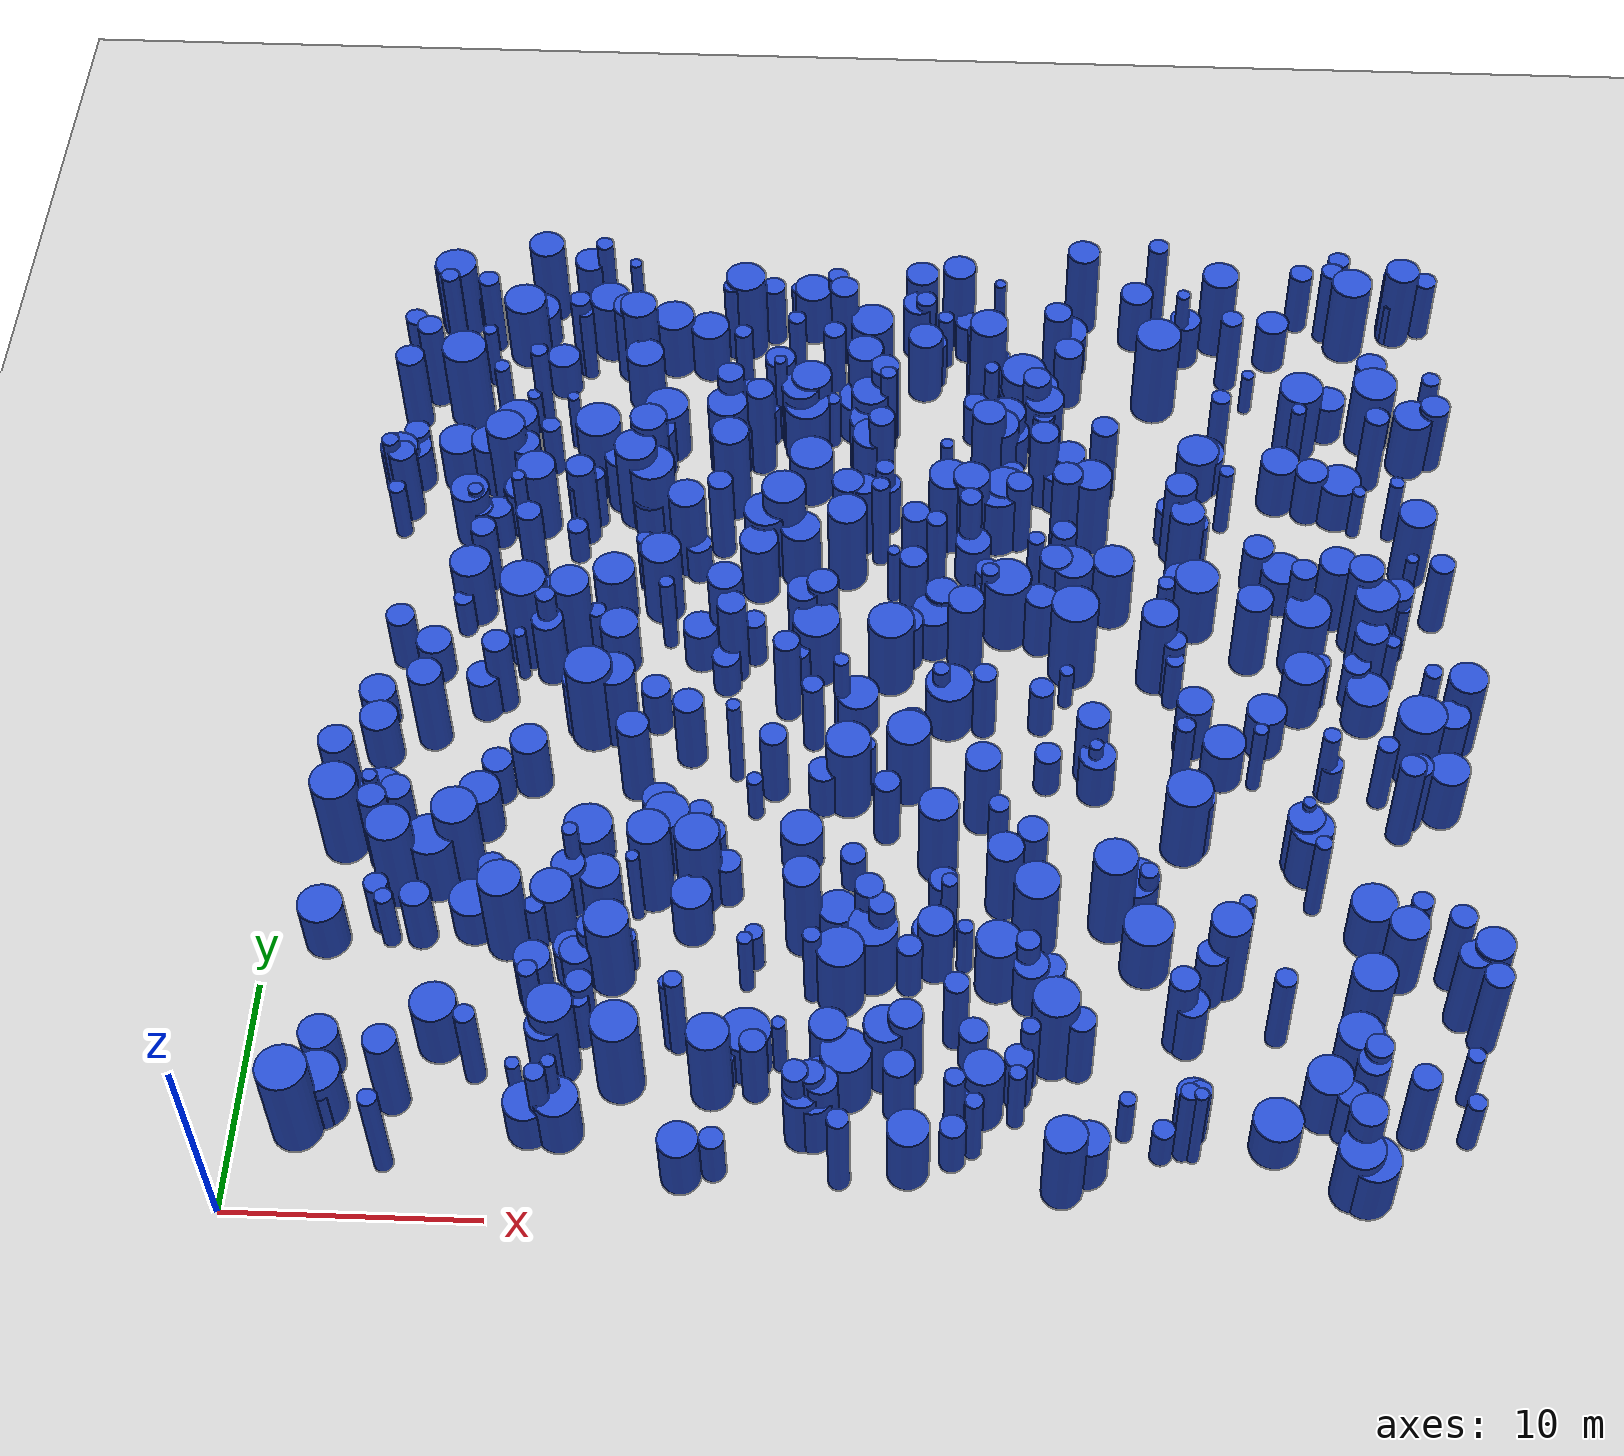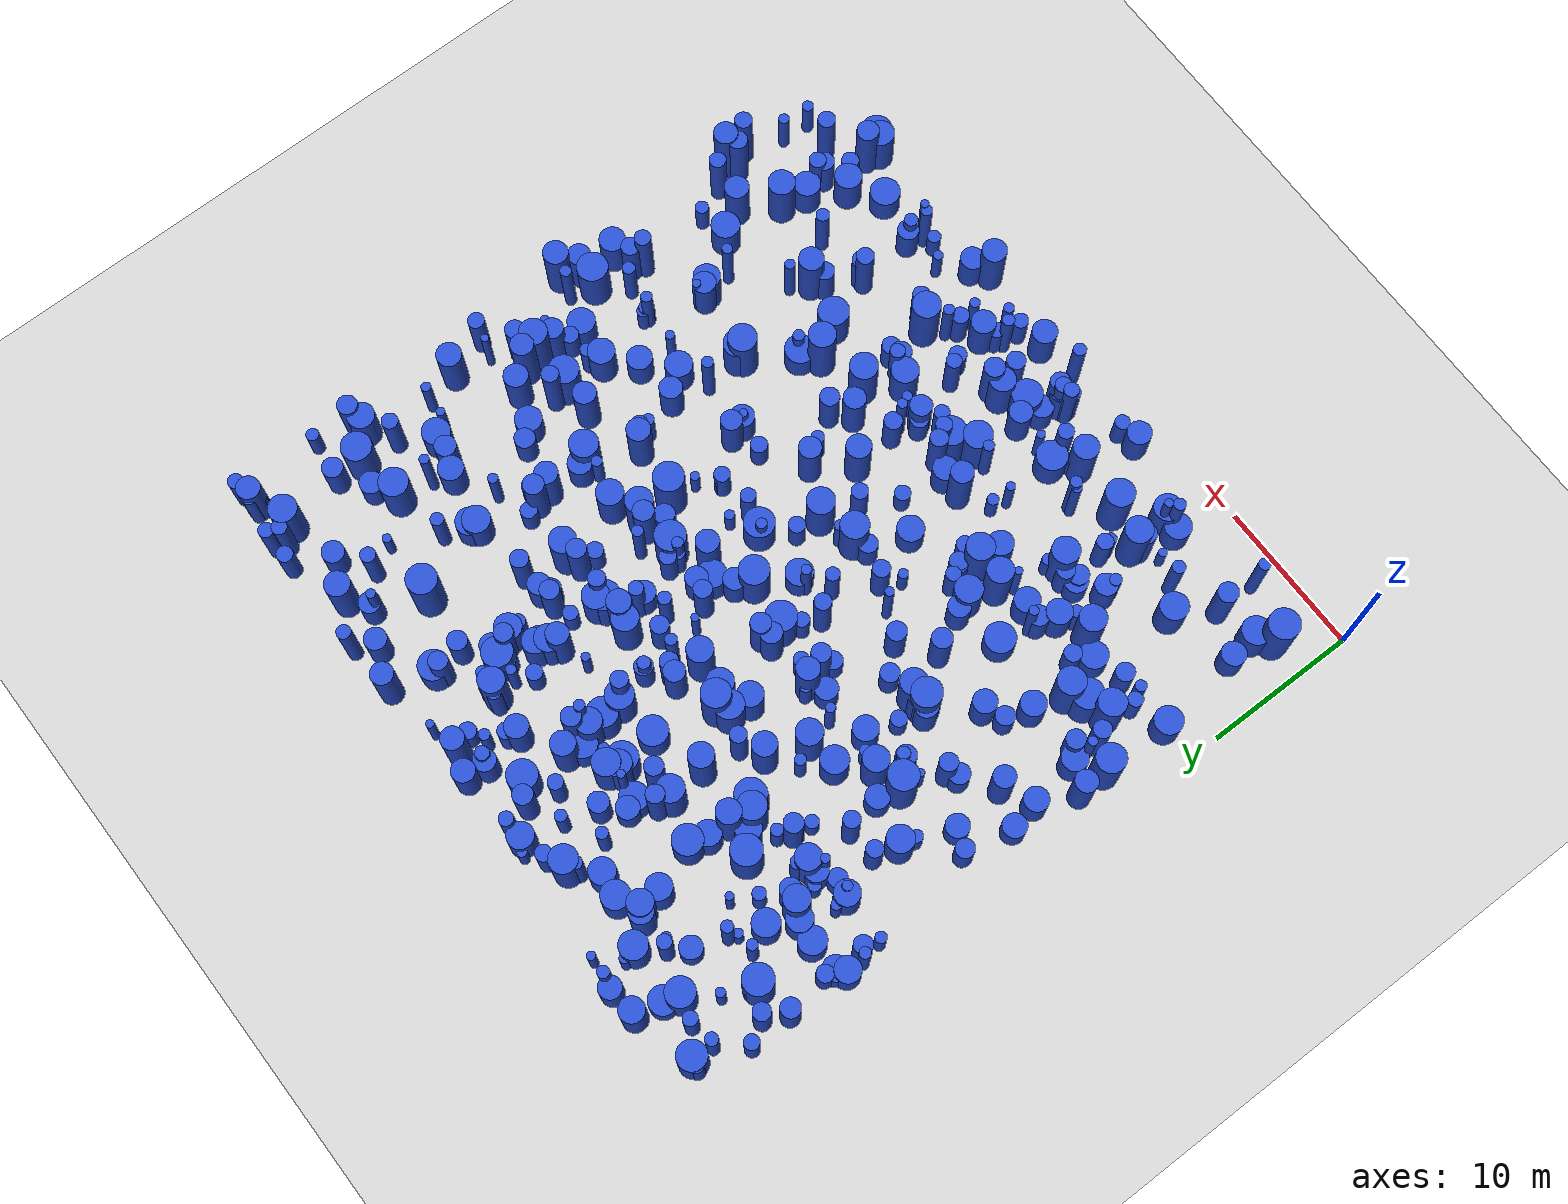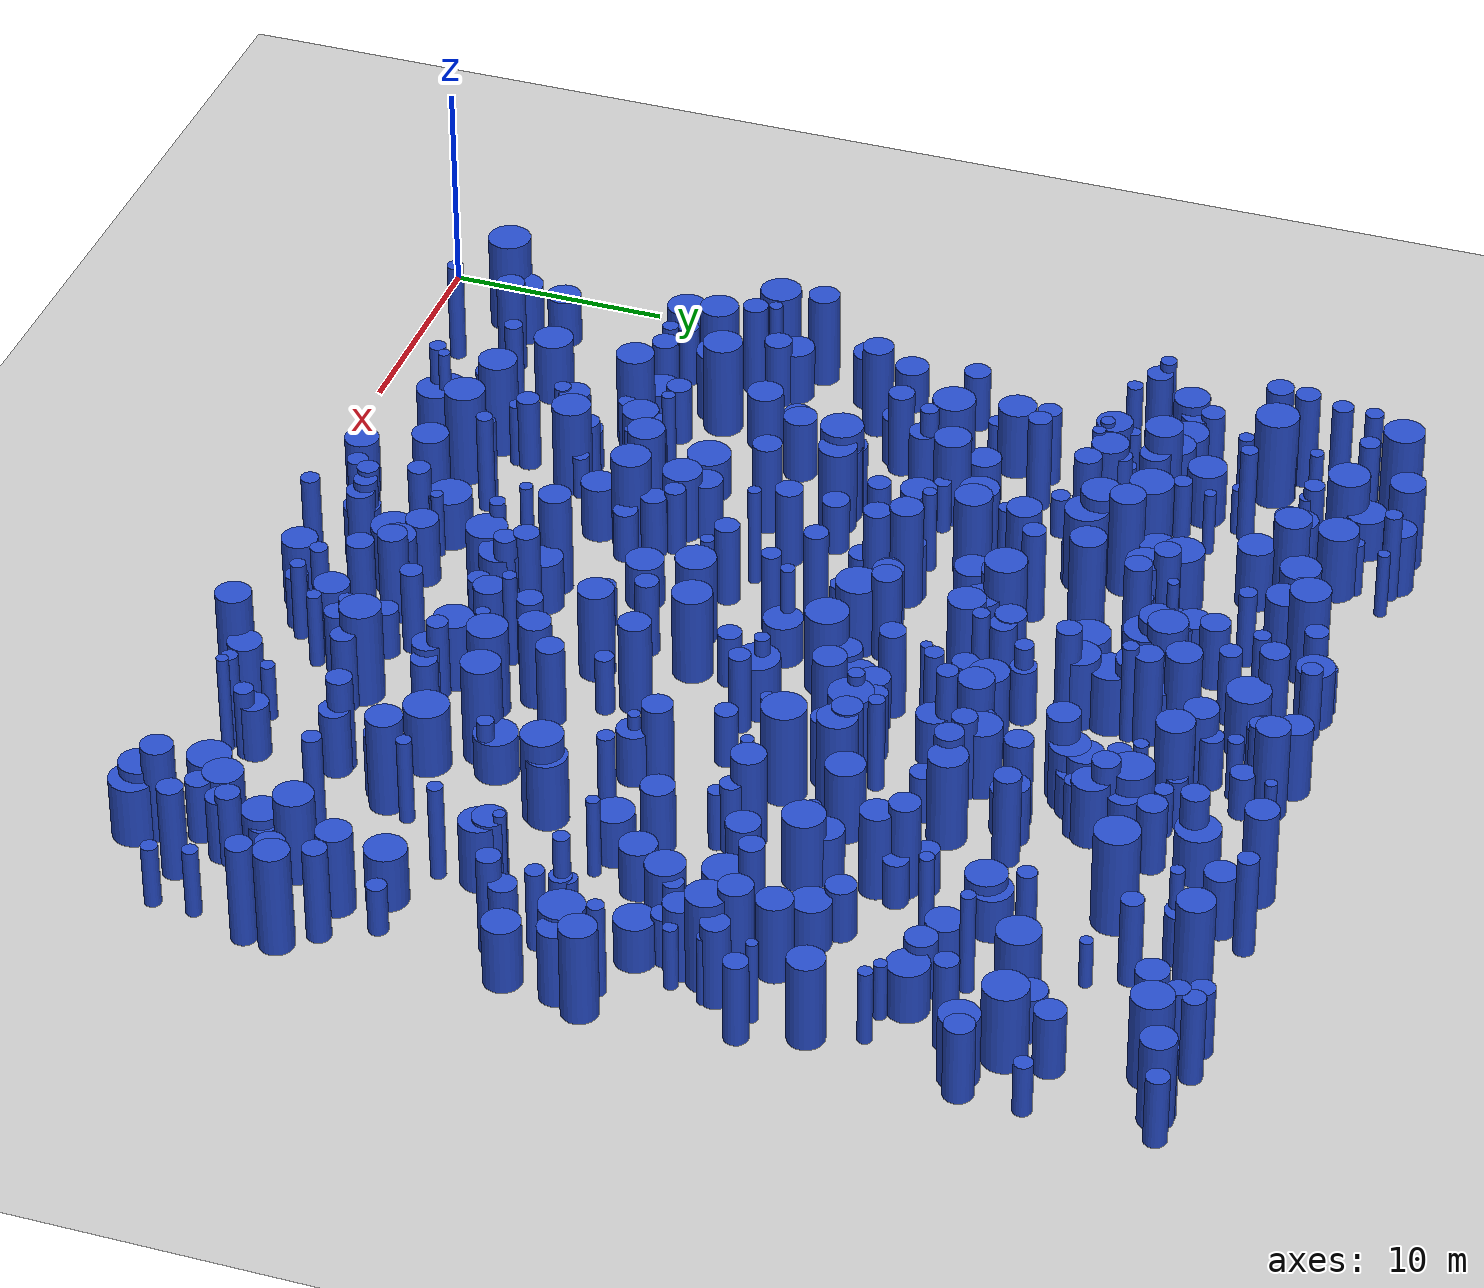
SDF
<sdf version="1.6">
 <world name="default">
  <plugin name="disable_physics" filename="libdisable_physics.so"/>
  <light name="sun" type="directional">
   <pose>0 0 10 0 -0 0</pose>
   <diffuse>0.8 0.8 0.8 1</diffuse>
   <specular>0.1 0.1 0.1 1</specular>
   <attenuation>
    <range>1000</range>
    <constant>0.9</constant>
    <linear>0.01</linear>
    <quadratic>0.001</quadratic>
   </attenuation>
   <direction>-0.5 0.5 -1</direction>
  </light>
  <model name="ground_plane">
   <static>1</static>
   <link name="link">
    <collision name="collision">
     <geometry><plane><normal>0 0 1</normal><size>100 100</size></plane></geometry>
     <surface><friction><ode><mu>100</mu><mu2>50</mu2></ode></friction></surface>
    </collision>
    <visual name="visual">
     <cast_shadows>0</cast_shadows>
     <geometry><plane><normal>0 0 1</normal><size>100 100</size></plane></geometry>
     <material>
      <script><uri>file://media/materials/scripts/gazebo.material</uri><name>Gazebo/Grey</name></script>
     </material>
    </visual>
   </link>
  </model>
  <gravity>0 0 -9.8</gravity>
  <magnetic_field>6e-06 2.3e-05 -4.2e-05</magnetic_field>
  <atmosphere type="adiabatic"/>
  <physics name="default_physics" default="0" type="ode">
   <max_step_size>0.001</max_step_size>
   <real_time_factor>1</real_time_factor>
   <real_time_update_rate>1000</real_time_update_rate>
  </physics>
  <scene><ambient>0.4 0.4 0.4 1</ambient><background>0.7 0.7 0.7 1</background><shadows>1</shadows></scene>
  <spherical_coordinates>
   <surface_model>EARTH_WGS84</surface_model>
   <latitude_deg>0</latitude_deg>
   <longitude_deg>0</longitude_deg>
   <elevation>0</elevation>
   <heading_deg>0</heading_deg>
  </spherical_coordinates>
  <model name="0">
   <static>0</static>
   <link name="link">
    <inertial>
     <mass>2</mass>
     <inertia><ixx>2.34982</ixx><ixy>0</ixy><ixz>0</ixz><iyy>2.34982</iyy><iyz>0</iyz><izz>0.175341</izz></inertia>
    </inertial>
    <collision name="collision">
     <geometry><cylinder><length>3.68414</length><radius>0.418737</radius></cylinder></geometry>
     <surface><contact><collide_without_contact>1</collide_without_contact></contact></surface>
    </collision>
    <visual name="visual">
     <geometry><cylinder><length>3.68414</length><radius>0.418737</radius></cylinder></geometry>
     <material>
      <script><uri>file://media/materials/scripts/gazebo.material</uri><name>Gazebo/Blue</name></script>
     </material>
    </visual>
    <gravity>0</gravity>
   </link>
   <pose>22.4212 20.0822 1.84207 0 -0 0</pose>
  </model>
  <model name="1">
   <static>0</static>
   <link name="link">
    <inertial>
     <mass>2</mass>
     <inertia><ixx>1.42291</ixx><ixy>0</ixy><ixz>0</ixz><iyy>1.42291</iyy><iyz>0</iyz><izz>0.128584</izz></inertia>
    </inertial>
    <collision name="collision">
     <geometry><cylinder><length>2.85512</length><radius>0.358586</radius></cylinder></geometry>
     <surface><contact><collide_without_contact>1</collide_without_contact></contact></surface>
    </collision>
    <visual name="visual">
     <geometry><cylinder><length>2.85512</length><radius>0.358586</radius></cylinder></geometry>
     <material>
      <script><uri>file://media/materials/scripts/gazebo.material</uri><name>Gazebo/Blue</name></script>
     </material>
    </visual>
    <gravity>0</gravity>
   </link>
   <pose>41.7752 27.9235 1.42756 0 -0 0</pose>
  </model>
  <model name="2">
   <static>0</static>
   <link name="link">
    <inertial>
     <mass>2</mass>
     <inertia><ixx>3.7496</ixx><ixy>0</ixy><ixz>0</ixz><iyy>3.7496</iyy><iyz>0</iyz><izz>0.179017</izz></inertia>
    </inertial>
    <collision name="collision">
     <geometry><cylinder><length>4.68621</length><radius>0.423104</radius></cylinder></geometry>
     <surface><contact><collide_without_contact>1</collide_without_contact></contact></surface>
    </collision>
    <visual name="visual">
     <geometry><cylinder><length>4.68621</length><radius>0.423104</radius></cylinder></geometry>
     <material>
      <script><uri>file://media/materials/scripts/gazebo.material</uri><name>Gazebo/Blue</name></script>
     </material>
    </visual>
    <gravity>0</gravity>
   </link>
   <pose>23.1867 2.18453 2.3431 0 -0 0</pose>
  </model>
  <model name="3">
   <static>0</static>
   <link name="link">
    <inertial>
     <mass>2</mass>
     <inertia><ixx>1.32488</ixx><ixy>0</ixy><ixz>0</ixz><iyy>1.32488</iyy><iyz>0</iyz><izz>0.51786</izz></inertia>
    </inertial>
    <collision name="collision">
     <geometry><cylinder><length>2.52897</length><radius>0.719625</radius></cylinder></geometry>
     <surface><contact><collide_without_contact>1</collide_without_contact></contact></surface>
    </collision>
    <visual name="visual">
     <geometry><cylinder><length>2.52897</length><radius>0.719625</radius></cylinder></geometry>
     <material>
      <script><uri>file://media/materials/scripts/gazebo.material</uri><name>Gazebo/Blue</name></script>
     </material>
    </visual>
    <gravity>0</gravity>
   </link>
   <pose>40.9199 45.4642 1.26449 0 -0 0</pose>
  </model>
  <model name="4">
   <static>0</static>
   <link name="link">
    <inertial>
     <mass>2</mass>
     <inertia>
      <ixx>0.784851</ixx>
      <ixy>0</ixy>
      <ixz>0</ixz>
      <iyy>0.784851</iyy>
      <iyz>0</iyz>
      <izz>0.196081</izz>
     </inertia>
    </inertial>
    <collision name="collision">
     <geometry><cylinder><length>2.02999</length><radius>0.442811</radius></cylinder></geometry>
     <surface><contact><collide_without_contact>1</collide_without_contact></contact></surface>
    </collision>
    <visual name="visual">
     <geometry><cylinder><length>2.02999</length><radius>0.442811</radius></cylinder></geometry>
     <material>
      <script><uri>file://media/materials/scripts/gazebo.material</uri><name>Gazebo/Blue</name></script>
     </material>
    </visual>
    <gravity>0</gravity>
   </link>
   <pose>22.4216 3.87466 1.015 0 -0 0</pose>
  </model>
  <model name="5">
   <static>0</static>
   <link name="link">
    <inertial>
     <mass>2</mass>
     <inertia><ixx>1.19895</ixx><ixy>0</ixy><ixz>0</ixz><iyy>1.19895</iyy><iyz>0</iyz><izz>0.27551</izz></inertia>
    </inertial>
    <collision name="collision">
     <geometry><cylinder><length>2.52333</length><radius>0.52489</radius></cylinder></geometry>
     <surface><contact><collide_without_contact>1</collide_without_contact></contact></surface>
    </collision>
    <visual name="visual">
     <geometry><cylinder><length>2.52333</length><radius>0.52489</radius></cylinder></geometry>
     <material>
      <script><uri>file://media/materials/scripts/gazebo.material</uri><name>Gazebo/Blue</name></script>
     </material>
    </visual>
    <gravity>0</gravity>
   </link>
   <pose>27.8719 4.70569 1.26166 0 -0 0</pose>
  </model>
  <model name="6">
   <static>0</static>
   <link name="link">
    <inertial>
     <mass>2</mass>
     <inertia><ixx>1.37461</ixx><ixy>0</ixy><ixz>0</ixz><iyy>1.37461</iyy><iyz>0</iyz><izz>0.826308</izz></inertia>
    </inertial>
    <collision name="collision">
     <geometry><cylinder><length>2.40182</length><radius>0.909015</radius></cylinder></geometry>
     <surface><contact><collide_without_contact>1</collide_without_contact></contact></surface>
    </collision>
    <visual name="visual">
     <geometry><cylinder><length>2.40182</length><radius>0.909015</radius></cylinder></geometry>
     <material>
      <script><uri>file://media/materials/scripts/gazebo.material</uri><name>Gazebo/Blue</name></script>
     </material>
    </visual>
    <gravity>0</gravity>
   </link>
   <pose>25.9791 28.1484 1.20091 0 -0 0</pose>
  </model>
  <model name="7">
   <static>0</static>
   <link name="link">
    <inertial>
     <mass>2</mass>
     <inertia><ixx>1.55105</ixx><ixy>0</ixy><ixz>0</ixz><iyy>1.55105</iyy><iyz>0</iyz><izz>0.812849</izz></inertia>
    </inertial>
    <collision name="collision">
     <geometry><cylinder><length>2.62064</length><radius>0.901581</radius></cylinder></geometry>
     <surface><contact><collide_without_contact>1</collide_without_contact></contact></surface>
    </collision>
    <visual name="visual">
     <geometry><cylinder><length>2.62064</length><radius>0.901581</radius></cylinder></geometry>
     <material>
      <script><uri>file://media/materials/scripts/gazebo.material</uri><name>Gazebo/Blue</name></script>
     </material>
    </visual>
    <gravity>0</gravity>
   </link>
   <pose>37.3399 37.4414 1.31032 0 -0 0</pose>
  </model>
  <model name="8">
   <static>0</static>
   <link name="link">
    <inertial>
     <mass>2</mass>
     <inertia>
      <ixx>0.936811</ixx>
      <ixy>0</ixy>
      <ixz>0</ixz>
      <iyy>0.936811</iyy>
      <iyz>0</iyz>
      <izz>0.138882</izz>
     </inertia>
    </inertial>
    <collision name="collision">
     <geometry><cylinder><length>2.28128</length><radius>0.372668</radius></cylinder></geometry>
     <surface><contact><collide_without_contact>1</collide_without_contact></contact></surface>
    </collision>
    <visual name="visual">
     <geometry><cylinder><length>2.28128</length><radius>0.372668</radius></cylinder></geometry>
     <material>
      <script><uri>file://media/materials/scripts/gazebo.material</uri><name>Gazebo/Blue</name></script>
     </material>
    </visual>
    <gravity>0</gravity>
   </link>
   <pose>19.4248 11.7611 1.14064 0 -0 0</pose>
  </model>
  <model name="9">
   <static>0</static>
   <link name="link">
    <inertial>
     <mass>2</mass>
     <inertia><ixx>1.77191</ixx><ixy>0</ixy><ixz>0</ixz><iyy>1.77191</iyy><iyz>0</iyz><izz>0.691914</izz></inertia>
    </inertial>
    <collision name="collision">
     <geometry><cylinder><length>2.92502</length><radius>0.831814</radius></cylinder></geometry>
     <surface><contact><collide_without_contact>1</collide_without_contact></contact></surface>
    </collision>
    <visual name="visual">
     <geometry><cylinder><length>2.92502</length><radius>0.831814</radius></cylinder></geometry>
     <material>
      <script><uri>file://media/materials/scripts/gazebo.material</uri><name>Gazebo/Blue</name></script>
     </material>
    </visual>
    <gravity>0</gravity>
   </link>
   <pose>11.3721 13.2 1.46251 0 -0 0</pose>
  </model>
  <model name="10">
   <static>0</static>
   <link name="link">
    <inertial>
     <mass>2</mass>
     <inertia>
      <ixx>0.774725</ixx>
      <ixy>0</ixy>
      <ixz>0</ixz>
      <iyy>0.774725</iyy>
      <iyz>0</iyz>
      <izz>0.189763</izz>
     </inertia>
    </inertial>
    <collision name="collision">
     <geometry><cylinder><length>2.01967</length><radius>0.435618</radius></cylinder></geometry>
     <surface><contact><collide_without_contact>1</collide_without_contact></contact></surface>
    </collision>
    <visual name="visual">
     <geometry><cylinder><length>2.01967</length><radius>0.435618</radius></cylinder></geometry>
     <material>
      <script><uri>file://media/materials/scripts/gazebo.material</uri><name>Gazebo/Blue</name></script>
     </material>
    </visual>
    <gravity>0</gravity>
   </link>
   <pose>10.4125 32.5588 1.00983 0 -0 0</pose>
  </model>
  <model name="11">
   <static>0</static>
   <link name="link">
    <inertial>
     <mass>2</mass>
     <inertia><ixx>3.80874</ixx><ixy>0</ixy><ixz>0</ixz><iyy>3.80874</iyy><iyz>0</iyz><izz>0.499703</izz></inertia>
    </inertial>
    <collision name="collision">
     <geometry><cylinder><length>4.62097</length><radius>0.706896</radius></cylinder></geometry>
     <surface><contact><collide_without_contact>1</collide_without_contact></contact></surface>
    </collision>
    <visual name="visual">
     <geometry><cylinder><length>4.62097</length><radius>0.706896</radius></cylinder></geometry>
     <material>
      <script><uri>file://media/materials/scripts/gazebo.material</uri><name>Gazebo/Blue</name></script>
     </material>
    </visual>
    <gravity>0</gravity>
   </link>
   <pose>42.6481 3.33236 2.31048 0 -0 0</pose>
  </model>
  <model name="12">
   <static>0</static>
   <link name="link">
    <inertial>
     <mass>2</mass>
     <inertia>
      <ixx>3.57056</ixx>
      <ixy>0</ixy>
      <ixz>0</ixz>
      <iyy>3.57056</iyy>
      <iyz>0</iyz>
      <izz>0.0913782</izz>
     </inertia>
    </inertial>
    <collision name="collision">
     <geometry><cylinder><length>4.59883</length><radius>0.302288</radius></cylinder></geometry>
     <surface><contact><collide_without_contact>1</collide_without_contact></contact></surface>
    </collision>
    <visual name="visual">
     <geometry><cylinder><length>4.59883</length><radius>0.302288</radius></cylinder></geometry>
     <material>
      <script><uri>file://media/materials/scripts/gazebo.material</uri><name>Gazebo/Blue</name></script>
     </material>
    </visual>
    <gravity>0</gravity>
   </link>
   <pose>3.87306 17.0696 2.29941 0 -0 0</pose>
  </model>
  <model name="13">
   <static>0</static>
   <link name="link">
    <inertial>
     <mass>2</mass>
     <inertia><ixx>1.9703</ixx><ixy>0</ixy><ixz>0</ixz><iyy>1.9703</iyy><iyz>0</iyz><izz>0.2914</izz></inertia>
    </inertial>
    <collision name="collision">
     <geometry><cylinder><length>3.30871</length><radius>0.539815</radius></cylinder></geometry>
     <surface><contact><collide_without_contact>1</collide_without_contact></contact></surface>
    </collision>
    <visual name="visual">
     <geometry><cylinder><length>3.30871</length><radius>0.539815</radius></cylinder></geometry>
     <material>
      <script><uri>file://media/materials/scripts/gazebo.material</uri><name>Gazebo/Blue</name></script>
     </material>
    </visual>
    <gravity>0</gravity>
   </link>
   <pose>28.2282 29.745 1.65436 0 -0 0</pose>
  </model>
  <model name="14">
   <static>0</static>
   <link name="link">
    <inertial>
     <mass>2</mass>
     <inertia><ixx>1.37401</ixx><ixy>0</ixy><ixz>0</ixz><iyy>1.37401</iyy><iyz>0</iyz><izz>0.143411</izz></inertia>
    </inertial>
    <collision name="collision">
     <geometry><cylinder><length>2.79532</length><radius>0.378697</radius></cylinder></geometry>
     <surface><contact><collide_without_contact>1</collide_without_contact></contact></surface>
    </collision>
    <visual name="visual">
     <geometry><cylinder><length>2.79532</length><radius>0.378697</radius></cylinder></geometry>
     <material>
      <script><uri>file://media/materials/scripts/gazebo.material</uri><name>Gazebo/Blue</name></script>
     </material>
    </visual>
    <gravity>0</gravity>
   </link>
   <pose>23.7113 6.20723 1.39766 0 -0 0</pose>
  </model>
  <model name="15">
   <static>0</static>
   <link name="link">
    <inertial>
     <mass>2</mass>
     <inertia><ixx>1.15166</ixx><ixy>0</ixy><ixz>0</ixz><iyy>1.15166</iyy><iyz>0</iyz><izz>0.803615</izz></inertia>
    </inertial>
    <collision name="collision">
     <geometry><cylinder><length>2.12111</length><radius>0.896446</radius></cylinder></geometry>
     <surface><contact><collide_without_contact>1</collide_without_contact></contact></surface>
    </collision>
    <visual name="visual">
     <geometry><cylinder><length>2.12111</length><radius>0.896446</radius></cylinder></geometry>
     <material>
      <script><uri>file://media/materials/scripts/gazebo.material</uri><name>Gazebo/Blue</name></script>
     </material>
    </visual>
    <gravity>0</gravity>
   </link>
   <pose>8.16995 13.0512 1.06056 0 -0 0</pose>
  </model>
  <model name="16">
   <static>0</static>
   <link name="link">
    <inertial>
     <mass>2</mass>
     <inertia>
      <ixx>0.892268</ixx>
      <ixy>0</ixy>
      <ixz>0</ixz>
      <iyy>0.892268</iyy>
      <iyz>0</iyz>
      <izz>0.347311</izz>
     </inertia>
    </inertial>
    <collision name="collision">
     <geometry><cylinder><length>2.07646</length><radius>0.589331</radius></cylinder></geometry>
     <surface><contact><collide_without_contact>1</collide_without_contact></contact></surface>
    </collision>
    <visual name="visual">
     <geometry><cylinder><length>2.07646</length><radius>0.589331</radius></cylinder></geometry>
     <material>
      <script><uri>file://media/materials/scripts/gazebo.material</uri><name>Gazebo/Blue</name></script>
     </material>
    </visual>
    <gravity>0</gravity>
   </link>
   <pose>17.3559 25.5947 1.03823 0 -0 0</pose>
  </model>
  <model name="17">
   <static>0</static>
   <link name="link">
    <inertial>
     <mass>2</mass>
     <inertia><ixx>1.53515</ixx><ixy>0</ixy><ixz>0</ixz><iyy>1.53515</iyy><iyz>0</iyz><izz>0.667989</izz></inertia>
    </inertial>
    <collision name="collision">
     <geometry><cylinder><length>2.68458</length><radius>0.817306</radius></cylinder></geometry>
     <surface><contact><collide_without_contact>1</collide_without_contact></contact></surface>
    </collision>
    <visual name="visual">
     <geometry><cylinder><length>2.68458</length><radius>0.817306</radius></cylinder></geometry>
     <material>
      <script><uri>file://media/materials/scripts/gazebo.material</uri><name>Gazebo/Blue</name></script>
     </material>
    </visual>
    <gravity>0</gravity>
   </link>
   <pose>12.7985 26.728 1.34229 0 -0 0</pose>
  </model>
  <model name="18">
   <static>0</static>
   <link name="link">
    <inertial>
     <mass>2</mass>
     <inertia>
      <ixx>0.755053</ixx>
      <ixy>0</ixy>
      <ixz>0</ixz>
      <iyy>0.755053</iyy>
      <iyz>0</iyz>
      <izz>0.161134</izz>
     </inertia>
    </inertial>
    <collision name="collision">
     <geometry><cylinder><length>2.01169</length><radius>0.401415</radius></cylinder></geometry>
     <surface><contact><collide_without_contact>1</collide_without_contact></contact></surface>
    </collision>
    <visual name="visual">
     <geometry><cylinder><length>2.01169</length><radius>0.401415</radius></cylinder></geometry>
     <material>
      <script><uri>file://media/materials/scripts/gazebo.material</uri><name>Gazebo/Blue</name></script>
     </material>
    </visual>
    <gravity>0</gravity>
   </link>
   <pose>42.3675 21.2109 1.00585 0 -0 0</pose>
  </model>
  <model name="19">
   <static>0</static>
   <link name="link">
    <inertial>
     <mass>2</mass>
     <inertia><ixx>3.44669</ixx><ixy>0</ixy><ixz>0</ixz><iyy>3.44669</iyy><iyz>0</iyz><izz>0.34216</izz></inertia>
    </inertial>
    <collision name="collision">
     <geometry><cylinder><length>4.43325</length><radius>0.584945</radius></cylinder></geometry>
     <surface><contact><collide_without_contact>1</collide_without_contact></contact></surface>
    </collision>
    <visual name="visual">
     <geometry><cylinder><length>4.43325</length><radius>0.584945</radius></cylinder></geometry>
     <material>
      <script><uri>file://media/materials/scripts/gazebo.material</uri><name>Gazebo/Blue</name></script>
     </material>
    </visual>
    <gravity>0</gravity>
   </link>
   <pose>33.1585 37.0156 2.21662 0 -0 0</pose>
  </model>
  <model name="20">
   <static>0</static>
   <link name="link">
    <inertial>
     <mass>2</mass>
     <inertia><ixx>2.14927</ixx><ixy>0</ixy><ixz>0</ixz><iyy>2.14927</iyy><iyz>0</iyz><izz>0.10024</izz></inertia>
    </inertial>
    <collision name="collision">
     <geometry><cylinder><length>3.54893</length><radius>0.316606</radius></cylinder></geometry>
     <surface><contact><collide_without_contact>1</collide_without_contact></contact></surface>
    </collision>
    <visual name="visual">
     <geometry><cylinder><length>3.54893</length><radius>0.316606</radius></cylinder></geometry>
     <material>
      <script><uri>file://media/materials/scripts/gazebo.material</uri><name>Gazebo/Blue</name></script>
     </material>
    </visual>
    <gravity>0</gravity>
   </link>
   <pose>45.8173 35.0316 1.77447 0 -0 0</pose>
  </model>
  <model name="21">
   <static>0</static>
   <link name="link">
    <inertial>
     <mass>2</mass>
     <inertia><ixx>2.07639</ixx><ixy>0</ixy><ixz>0</ixz><iyy>2.07639</iyy><iyz>0</iyz><izz>0.241004</izz></inertia>
    </inertial>
    <collision name="collision">
     <geometry><cylinder><length>3.42569</length><radius>0.490922</radius></cylinder></geometry>
     <surface><contact><collide_without_contact>1</collide_without_contact></contact></surface>
    </collision>
    <visual name="visual">
     <geometry><cylinder><length>3.42569</length><radius>0.490922</radius></cylinder></geometry>
     <material>
      <script><uri>file://media/materials/scripts/gazebo.material</uri><name>Gazebo/Blue</name></script>
     </material>
    </visual>
    <gravity>0</gravity>
   </link>
   <pose>36.0554 26.0454 1.71284 0 -0 0</pose>
  </model>
  <model name="22">
   <static>0</static>
   <link name="link">
    <inertial>
     <mass>2</mass>
     <inertia><ixx>2.26913</ixx><ixy>0</ixy><ixz>0</ixz><iyy>2.26913</iyy><iyz>0</iyz><izz>0.505011</izz></inertia>
    </inertial>
    <collision name="collision">
     <geometry><cylinder><length>3.47847</length><radius>0.710641</radius></cylinder></geometry>
     <surface><contact><collide_without_contact>1</collide_without_contact></contact></surface>
    </collision>
    <visual name="visual">
     <geometry><cylinder><length>3.47847</length><radius>0.710641</radius></cylinder></geometry>
     <material>
      <script><uri>file://media/materials/scripts/gazebo.material</uri><name>Gazebo/Blue</name></script>
     </material>
    </visual>
    <gravity>0</gravity>
   </link>
   <pose>26.527 11.7667 1.73924 0 -0 0</pose>
  </model>
  <model name="23">
   <static>0</static>
   <link name="link">
    <inertial>
     <mass>2</mass>
     <inertia><ixx>2.13264</ixx><ixy>0</ixy><ixz>0</ixz><iyy>2.13264</iyy><iyz>0</iyz><izz>0.34742</izz></inertia>
    </inertial>
    <collision name="collision">
     <geometry><cylinder><length>3.42835</length><radius>0.589423</radius></cylinder></geometry>
     <surface><contact><collide_without_contact>1</collide_without_contact></contact></surface>
    </collision>
    <visual name="visual">
     <geometry><cylinder><length>3.42835</length><radius>0.589423</radius></cylinder></geometry>
     <material>
      <script><uri>file://media/materials/scripts/gazebo.material</uri><name>Gazebo/Blue</name></script>
     </material>
    </visual>
    <gravity>0</gravity>
   </link>
   <pose>25.0737 32.6969 1.71417 0 -0 0</pose>
  </model>
  <model name="24">
   <static>0</static>
   <link name="link">
    <inertial>
     <mass>2</mass>
     <inertia><ixx>3.77941</ixx><ixy>0</ixy><ixz>0</ixz><iyy>3.77941</iyy><iyz>0</iyz><izz>0.148371</izz></inertia>
    </inertial>
    <collision name="collision">
     <geometry><cylinder><length>4.71502</length><radius>0.38519</radius></cylinder></geometry>
     <surface><contact><collide_without_contact>1</collide_without_contact></contact></surface>
    </collision>
    <visual name="visual">
     <geometry><cylinder><length>4.71502</length><radius>0.38519</radius></cylinder></geometry>
     <material>
      <script><uri>file://media/materials/scripts/gazebo.material</uri><name>Gazebo/Blue</name></script>
     </material>
    </visual>
    <gravity>0</gravity>
   </link>
   <pose>8.12711 40.4296 2.35751 0 -0 0</pose>
  </model>
  <model name="25">
   <static>0</static>
   <link name="link">
    <inertial>
     <mass>2</mass>
     <inertia><ixx>3.99631</ixx><ixy>0</ixy><ixz>0</ixz><iyy>3.99631</iyy><iyz>0</iyz><izz>0.280628</izz></inertia>
    </inertial>
    <collision name="collision">
     <geometry><cylinder><length>4.80998</length><radius>0.529744</radius></cylinder></geometry>
     <surface><contact><collide_without_contact>1</collide_without_contact></contact></surface>
    </collision>
    <visual name="visual">
     <geometry><cylinder><length>4.80998</length><radius>0.529744</radius></cylinder></geometry>
     <material>
      <script><uri>file://media/materials/scripts/gazebo.material</uri><name>Gazebo/Blue</name></script>
     </material>
    </visual>
    <gravity>0</gravity>
   </link>
   <pose>45.2657 18.9256 2.40499 0 -0 0</pose>
  </model>
  <model name="26">
   <static>0</static>
   <link name="link">
    <inertial>
     <mass>2</mass>
     <inertia><ixx>2.66427</ixx><ixy>0</ixy><ixz>0</ixz><iyy>2.66427</iyy><iyz>0</iyz><izz>0.704227</izz></inertia>
    </inertial>
    <collision name="collision">
     <geometry><cylinder><length>3.72464</length><radius>0.839182</radius></cylinder></geometry>
     <surface><contact><collide_without_contact>1</collide_without_contact></contact></surface>
    </collision>
    <visual name="visual">
     <geometry><cylinder><length>3.72464</length><radius>0.839182</radius></cylinder></geometry>
     <material>
      <script><uri>file://media/materials/scripts/gazebo.material</uri><name>Gazebo/Blue</name></script>
     </material>
    </visual>
    <gravity>0</gravity>
   </link>
   <pose>19.7542 39.6332 1.86232 0 -0 0</pose>
  </model>
  <model name="27">
   <static>0</static>
   <link name="link">
    <inertial>
     <mass>2</mass>
     <inertia><ixx>1.44612</ixx><ixy>0</ixy><ixz>0</ixz><iyy>1.44612</iyy><iyz>0</iyz><izz>0.468528</izz></inertia>
    </inertial>
    <collision name="collision">
     <geometry><cylinder><length>2.69651</length><radius>0.684491</radius></cylinder></geometry>
     <surface><contact><collide_without_contact>1</collide_without_contact></contact></surface>
    </collision>
    <visual name="visual">
     <geometry><cylinder><length>2.69651</length><radius>0.684491</radius></cylinder></geometry>
     <material>
      <script><uri>file://media/materials/scripts/gazebo.material</uri><name>Gazebo/Blue</name></script>
     </material>
    </visual>
    <gravity>0</gravity>
   </link>
   <pose>36.4301 4.9127 1.34825 0 -0 0</pose>
  </model>
  <model name="28">
   <static>0</static>
   <link name="link">
    <inertial>
     <mass>2</mass>
     <inertia><ixx>3.02201</ixx><ixy>0</ixy><ixz>0</ixz><iyy>3.02201</iyy><iyz>0</iyz><izz>0.698976</izz></inertia>
    </inertial>
    <collision name="collision">
     <geometry><cylinder><length>4.00439</length><radius>0.836048</radius></cylinder></geometry>
     <surface><contact><collide_without_contact>1</collide_without_contact></contact></surface>
    </collision>
    <visual name="visual">
     <geometry><cylinder><length>4.00439</length><radius>0.836048</radius></cylinder></geometry>
     <material>
      <script><uri>file://media/materials/scripts/gazebo.material</uri><name>Gazebo/Blue</name></script>
     </material>
    </visual>
    <gravity>0</gravity>
   </link>
   <pose>8.59451 34.2473 2.0022 0 -0 0</pose>
  </model>
  <model name="29">
   <static>0</static>
   <link name="link">
    <inertial>
     <mass>2</mass>
     <inertia>
      <ixx>0.975002</ixx>
      <ixy>0</ixy>
      <ixz>0</ixz>
      <iyy>0.975002</iyy>
      <iyz>0</iyz>
      <izz>0.174571</izz>
     </inertia>
    </inertial>
    <collision name="collision">
     <geometry><cylinder><length>2.30788</length><radius>0.417817</radius></cylinder></geometry>
     <surface><contact><collide_without_contact>1</collide_without_contact></contact></surface>
    </collision>
    <visual name="visual">
     <geometry><cylinder><length>2.30788</length><radius>0.417817</radius></cylinder></geometry>
     <material>
      <script><uri>file://media/materials/scripts/gazebo.material</uri><name>Gazebo/Blue</name></script>
     </material>
    </visual>
    <gravity>0</gravity>
   </link>
   <pose>29.3907 42.6499 1.15394 0 -0 0</pose>
  </model>
  <model name="30">
   <static>0</static>
   <link name="link">
    <inertial>
     <mass>2</mass>
     <inertia><ixx>3.44762</ixx><ixy>0</ixy><ixz>0</ixz><iyy>3.44762</iyy><iyz>0</iyz><izz>0.103691</izz></inertia>
    </inertial>
    <collision name="collision">
     <geometry><cylinder><length>4.51383</length><radius>0.322011</radius></cylinder></geometry>
     <surface><contact><collide_without_contact>1</collide_without_contact></contact></surface>
    </collision>
    <visual name="visual">
     <geometry><cylinder><length>4.51383</length><radius>0.322011</radius></cylinder></geometry>
     <material>
      <script><uri>file://media/materials/scripts/gazebo.material</uri><name>Gazebo/Blue</name></script>
     </material>
    </visual>
    <gravity>0</gravity>
   </link>
   <pose>16.4467 7.91767 2.25692 0 -0 0</pose>
  </model>
  <model name="31">
   <static>0</static>
   <link name="link">
    <inertial>
     <mass>2</mass>
     <inertia><ixx>2.57392</ixx><ixy>0</ixy><ixz>0</ixz><iyy>2.57392</iyy><iyz>0</iyz><izz>0.71737</izz></inertia>
    </inertial>
    <collision name="collision">
     <geometry><cylinder><length>3.64574</length><radius>0.846977</radius></cylinder></geometry>
     <surface><contact><collide_without_contact>1</collide_without_contact></contact></surface>
    </collision>
    <visual name="visual">
     <geometry><cylinder><length>3.64574</length><radius>0.846977</radius></cylinder></geometry>
     <material>
      <script><uri>file://media/materials/scripts/gazebo.material</uri><name>Gazebo/Blue</name></script>
     </material>
    </visual>
    <gravity>0</gravity>
   </link>
   <pose>22.8649 39.5204 1.82287 0 -0 0</pose>
  </model>
  <model name="32">
   <static>0</static>
   <link name="link">
    <inertial>
     <mass>2</mass>
     <inertia><ixx>4.32118</ixx><ixy>0</ixy><ixz>0</ixz><iyy>4.32118</iyy><iyz>0</iyz><izz>0.545109</izz></inertia>
    </inertial>
    <collision name="collision">
     <geometry><cylinder><length>4.92867</length><radius>0.738315</radius></cylinder></geometry>
     <surface><contact><collide_without_contact>1</collide_without_contact></contact></surface>
    </collision>
    <visual name="visual">
     <geometry><cylinder><length>4.92867</length><radius>0.738315</radius></cylinder></geometry>
     <material>
      <script><uri>file://media/materials/scripts/gazebo.material</uri><name>Gazebo/Blue</name></script>
     </material>
    </visual>
    <gravity>0</gravity>
   </link>
   <pose>43.9927 28.992 2.46433 0 -0 0</pose>
  </model>
  <model name="33">
   <static>0</static>
   <link name="link">
    <inertial>
     <mass>2</mass>
     <inertia><ixx>1.18232</ixx><ixy>0</ixy><ixz>0</ixz><iyy>1.18232</iyy><iyz>0</iyz><izz>0.933247</izz></inertia>
    </inertial>
    <collision name="collision">
     <geometry><cylinder><length>2.07224</length><radius>0.966047</radius></cylinder></geometry>
     <surface><contact><collide_without_contact>1</collide_without_contact></contact></surface>
    </collision>
    <visual name="visual">
     <geometry><cylinder><length>2.07224</length><radius>0.966047</radius></cylinder></geometry>
     <material>
      <script><uri>file://media/materials/scripts/gazebo.material</uri><name>Gazebo/Blue</name></script>
     </material>
    </visual>
    <gravity>0</gravity>
   </link>
   <pose>29.552 41.2584 1.03612 0 -0 0</pose>
  </model>
  <model name="34">
   <static>0</static>
   <link name="link">
    <inertial>
     <mass>2</mass>
     <inertia><ixx>3.25336</ixx><ixy>0</ixy><ixz>0</ixz><iyy>3.25336</iyy><iyz>0</iyz><izz>0.568015</izz></inertia>
    </inertial>
    <collision name="collision">
     <geometry><cylinder><length>4.22092</length><radius>0.753668</radius></cylinder></geometry>
     <surface><contact><collide_without_contact>1</collide_without_contact></contact></surface>
    </collision>
    <visual name="visual">
     <geometry><cylinder><length>4.22092</length><radius>0.753668</radius></cylinder></geometry>
     <material>
      <script><uri>file://media/materials/scripts/gazebo.material</uri><name>Gazebo/Blue</name></script>
     </material>
    </visual>
    <gravity>0</gravity>
   </link>
   <pose>46.7338 47.3062 2.11046 0 -0 0</pose>
  </model>
  <model name="35">
   <static>0</static>
   <link name="link">
    <inertial>
     <mass>2</mass>
     <inertia>
      <ixx>1.30378</ixx>
      <ixy>0</ixy>
      <ixz>0</ixz>
      <iyy>1.30378</iyy>
      <iyz>0</iyz>
      <izz>0.0818979</izz>
     </inertia>
    </inertial>
    <collision name="collision">
     <geometry><cylinder><length>2.75264</length><radius>0.286178</radius></cylinder></geometry>
     <surface><contact><collide_without_contact>1</collide_without_contact></contact></surface>
    </collision>
    <visual name="visual">
     <geometry><cylinder><length>2.75264</length><radius>0.286178</radius></cylinder></geometry>
     <material>
      <script><uri>file://media/materials/scripts/gazebo.material</uri><name>Gazebo/Blue</name></script>
     </material>
    </visual>
    <gravity>0</gravity>
   </link>
   <pose>44.2744 35.1639 1.37632 0 -0 0</pose>
  </model>
  <model name="36">
   <static>0</static>
   <link name="link">
    <inertial>
     <mass>2</mass>
     <inertia><ixx>3.51883</ixx><ixy>0</ixy><ixz>0</ixz><iyy>3.51883</iyy><iyz>0</iyz><izz>0.320908</izz></inertia>
    </inertial>
    <collision name="collision">
     <geometry><cylinder><length>4.4889</length><radius>0.566488</radius></cylinder></geometry>
     <surface><contact><collide_without_contact>1</collide_without_contact></contact></surface>
    </collision>
    <visual name="visual">
     <geometry><cylinder><length>4.4889</length><radius>0.566488</radius></cylinder></geometry>
     <material>
      <script><uri>file://media/materials/scripts/gazebo.material</uri><name>Gazebo/Blue</name></script>
     </material>
    </visual>
    <gravity>0</gravity>
   </link>
   <pose>44.884 4.86893 2.24445 0 -0 0</pose>
  </model>
  <model name="37">
   <static>0</static>
   <link name="link">
    <inertial>
     <mass>2</mass>
     <inertia><ixx>3.04398</ixx><ixy>0</ixy><ixz>0</ixz><iyy>3.04398</iyy><iyz>0</iyz><izz>0.92073</izz></inertia>
    </inertial>
    <collision name="collision">
     <geometry><cylinder><length>3.93722</length><radius>0.959547</radius></cylinder></geometry>
     <surface><contact><collide_without_contact>1</collide_without_contact></contact></surface>
    </collision>
    <visual name="visual">
     <geometry><cylinder><length>3.93722</length><radius>0.959547</radius></cylinder></geometry>
     <material>
      <script><uri>file://media/materials/scripts/gazebo.material</uri><name>Gazebo/Blue</name></script>
     </material>
    </visual>
    <gravity>0</gravity>
   </link>
   <pose>24.2494 26.2747 1.96861 0 -0 0</pose>
  </model>
  <model name="38">
   <static>0</static>
   <link name="link">
    <inertial>
     <mass>2</mass>
     <inertia><ixx>1.02896</ixx><ixy>0</ixy><ixz>0</ixz><iyy>1.02896</iyy><iyz>0</iyz><izz>0.550959</izz></inertia>
    </inertial>
    <collision name="collision">
     <geometry><cylinder><length>2.12623</length><radius>0.742266</radius></cylinder></geometry>
     <surface><contact><collide_without_contact>1</collide_without_contact></contact></surface>
    </collision>
    <visual name="visual">
     <geometry><cylinder><length>2.12623</length><radius>0.742266</radius></cylinder></geometry>
     <material>
      <script><uri>file://media/materials/scripts/gazebo.material</uri><name>Gazebo/Blue</name></script>
     </material>
    </visual>
    <gravity>0</gravity>
   </link>
   <pose>29.1701 38.6962 1.06311 0 -0 0</pose>
  </model>
  <model name="39">
   <static>0</static>
   <link name="link">
    <inertial>
     <mass>2</mass>
     <inertia><ixx>2.1303</ixx><ixy>0</ixy><ixz>0</ixz><iyy>2.1303</iyy><iyz>0</iyz><izz>0.504175</izz></inertia>
    </inertial>
    <collision name="collision">
     <geometry><cylinder><length>3.35697</length><radius>0.710052</radius></cylinder></geometry>
     <surface><contact><collide_without_contact>1</collide_without_contact></contact></surface>
    </collision>
    <visual name="visual">
     <geometry><cylinder><length>3.35697</length><radius>0.710052</radius></cylinder></geometry>
     <material>
      <script><uri>file://media/materials/scripts/gazebo.material</uri><name>Gazebo/Blue</name></script>
     </material>
    </visual>
    <gravity>0</gravity>
   </link>
   <pose>21.7132 4.03501 1.67849 0 -0 0</pose>
  </model>
  <model name="40">
   <static>0</static>
   <link name="link">
    <inertial>
     <mass>2</mass>
     <inertia><ixx>1.56214</ixx><ixy>0</ixy><ixz>0</ixz><iyy>1.56214</iyy><iyz>0</iyz><izz>0.523114</izz></inertia>
    </inertial>
    <collision name="collision">
     <geometry><cylinder><length>2.79347</length><radius>0.723266</radius></cylinder></geometry>
     <surface><contact><collide_without_contact>1</collide_without_contact></contact></surface>
    </collision>
    <visual name="visual">
     <geometry><cylinder><length>2.79347</length><radius>0.723266</radius></cylinder></geometry>
     <material>
      <script><uri>file://media/materials/scripts/gazebo.material</uri><name>Gazebo/Blue</name></script>
     </material>
    </visual>
    <gravity>0</gravity>
   </link>
   <pose>15.2742 17.7058 1.39674 0 -0 0</pose>
  </model>
  <model name="41">
   <static>0</static>
   <link name="link">
    <inertial>
     <mass>2</mass>
     <inertia><ixx>2.43129</ixx><ixy>0</ixy><ixz>0</ixz><iyy>2.43129</iyy><iyz>0</iyz><izz>0.15694</izz></inertia>
    </inertial>
    <collision name="collision">
     <geometry><cylinder><length>3.75725</length><radius>0.396156</radius></cylinder></geometry>
     <surface><contact><collide_without_contact>1</collide_without_contact></contact></surface>
    </collision>
    <visual name="visual">
     <geometry><cylinder><length>3.75725</length><radius>0.396156</radius></cylinder></geometry>
     <material>
      <script><uri>file://media/materials/scripts/gazebo.material</uri><name>Gazebo/Blue</name></script>
     </material>
    </visual>
    <gravity>0</gravity>
   </link>
   <pose>16.9986 42.8262 1.87863 0 -0 0</pose>
  </model>
  <model name="42">
   <static>0</static>
   <link name="link">
    <inertial>
     <mass>2</mass>
     <inertia><ixx>3.9345</ixx><ixy>0</ixy><ixz>0</ixz><iyy>3.9345</iyy><iyz>0</iyz><izz>0.817818</izz></inertia>
    </inertial>
    <collision name="collision">
     <geometry><cylinder><length>4.5993</length><radius>0.904333</radius></cylinder></geometry>
     <surface><contact><collide_without_contact>1</collide_without_contact></contact></surface>
    </collision>
    <visual name="visual">
     <geometry><cylinder><length>4.5993</length><radius>0.904333</radius></cylinder></geometry>
     <material>
      <script><uri>file://media/materials/scripts/gazebo.material</uri><name>Gazebo/Blue</name></script>
     </material>
    </visual>
    <gravity>0</gravity>
   </link>
   <pose>7.3963 15.7324 2.29965 0 -0 0</pose>
  </model>
  <model name="43">
   <static>0</static>
   <link name="link">
    <inertial>
     <mass>2</mass>
     <inertia>
      <ixx>3.81452</ixx>
      <ixy>0</ixy>
      <ixz>0</ixz>
      <iyy>3.81452</iyy>
      <iyz>0</iyz>
      <izz>0.0700208</izz>
     </inertia>
    </inertial>
    <collision name="collision">
     <geometry><cylinder><length>4.76204</length><radius>0.264614</radius></cylinder></geometry>
     <surface><contact><collide_without_contact>1</collide_without_contact></contact></surface>
    </collision>
    <visual name="visual">
     <geometry><cylinder><length>4.76204</length><radius>0.264614</radius></cylinder></geometry>
     <material>
      <script><uri>file://media/materials/scripts/gazebo.material</uri><name>Gazebo/Blue</name></script>
     </material>
    </visual>
    <gravity>0</gravity>
   </link>
   <pose>36.5145 3.67072 2.38102 0 -0 0</pose>
  </model>
  <model name="44">
   <static>0</static>
   <link name="link">
    <inertial>
     <mass>2</mass>
     <inertia><ixx>1.89444</ixx><ixy>0</ixy><ixz>0</ixz><iyy>1.89444</iyy><iyz>0</iyz><izz>0.104986</izz></inertia>
    </inertial>
    <collision name="collision">
     <geometry><cylinder><length>3.32441</length><radius>0.324016</radius></cylinder></geometry>
     <surface><contact><collide_without_contact>1</collide_without_contact></contact></surface>
    </collision>
    <visual name="visual">
     <geometry><cylinder><length>3.32441</length><radius>0.324016</radius></cylinder></geometry>
     <material>
      <script><uri>file://media/materials/scripts/gazebo.material</uri><name>Gazebo/Blue</name></script>
     </material>
    </visual>
    <gravity>0</gravity>
   </link>
   <pose>6.01162 33.3985 1.6622 0 -0 0</pose>
  </model>
  <model name="45">
   <static>0</static>
   <link name="link">
    <inertial>
     <mass>2</mass>
     <inertia>
      <ixx>0.842287</ixx>
      <ixy>0</ixy>
      <ixz>0</ixz>
      <iyy>0.842287</iyy>
      <iyz>0</iyz>
      <izz>0.166231</izz>
     </inertia>
    </inertial>
    <collision name="collision">
     <geometry><cylinder><length>2.13425</length><radius>0.407715</radius></cylinder></geometry>
     <surface><contact><collide_without_contact>1</collide_without_contact></contact></surface>
    </collision>
    <visual name="visual">
     <geometry><cylinder><length>2.13425</length><radius>0.407715</radius></cylinder></geometry>
     <material>
      <script><uri>file://media/materials/scripts/gazebo.material</uri><name>Gazebo/Blue</name></script>
     </material>
    </visual>
    <gravity>0</gravity>
   </link>
   <pose>5.99403 28.261 1.06713 0 -0 0</pose>
  </model>
  <model name="46">
   <static>0</static>
   <link name="link">
    <inertial>
     <mass>2</mass>
     <inertia><ixx>3.66514</ixx><ixy>0</ixy><ixz>0</ixz><iyy>3.66514</iyy><iyz>0</iyz><izz>0.277177</izz></inertia>
    </inertial>
    <collision name="collision">
     <geometry><cylinder><length>4.59992</length><radius>0.526476</radius></cylinder></geometry>
     <surface><contact><collide_without_contact>1</collide_without_contact></contact></surface>
    </collision>
    <visual name="visual">
     <geometry><cylinder><length>4.59992</length><radius>0.526476</radius></cylinder></geometry>
     <material>
      <script><uri>file://media/materials/scripts/gazebo.material</uri><name>Gazebo/Blue</name></script>
     </material>
    </visual>
    <gravity>0</gravity>
   </link>
   <pose>16.6724 33.1642 2.29996 0 -0 0</pose>
  </model>
  <model name="47">
   <static>0</static>
   <link name="link">
    <inertial>
     <mass>2</mass>
     <inertia><ixx>4.39041</ixx><ixy>0</ixy><ixz>0</ixz><iyy>4.39041</iyy><iyz>0</iyz><izz>0.626142</izz></inertia>
    </inertial>
    <collision name="collision">
     <geometry><cylinder><length>4.94611</length><radius>0.791291</radius></cylinder></geometry>
     <surface><contact><collide_without_contact>1</collide_without_contact></contact></surface>
    </collision>
    <visual name="visual">
     <geometry><cylinder><length>4.94611</length><radius>0.791291</radius></cylinder></geometry>
     <material>
      <script><uri>file://media/materials/scripts/gazebo.material</uri><name>Gazebo/Blue</name></script>
     </material>
    </visual>
    <gravity>0</gravity>
   </link>
   <pose>13.3403 36.3856 2.47306 0 -0 0</pose>
  </model>
  <model name="48">
   <static>0</static>
   <link name="link">
    <inertial>
     <mass>2</mass>
     <inertia><ixx>1.60895</ixx><ixy>0</ixy><ixz>0</ixz><iyy>1.60895</iyy><iyz>0</iyz><izz>0.100304</izz></inertia>
    </inertial>
    <collision name="collision">
     <geometry><cylinder><length>3.05823</length><radius>0.316709</radius></cylinder></geometry>
     <surface><contact><collide_without_contact>1</collide_without_contact></contact></surface>
    </collision>
    <visual name="visual">
     <geometry><cylinder><length>3.05823</length><radius>0.316709</radius></cylinder></geometry>
     <material>
      <script><uri>file://media/materials/scripts/gazebo.material</uri><name>Gazebo/Blue</name></script>
     </material>
    </visual>
    <gravity>0</gravity>
   </link>
   <pose>45.1707 26.6144 1.52911 0 -0 0</pose>
  </model>
  <model name="49">
   <static>0</static>
   <link name="link">
    <inertial>
     <mass>2</mass>
     <inertia><ixx>1.51586</ixx><ixy>0</ixy><ixz>0</ixz><iyy>1.51586</iyy><iyz>0</iyz><izz>0.321451</izz></inertia>
    </inertial>
    <collision name="collision">
     <geometry><cylinder><length>2.85146</length><radius>0.566967</radius></cylinder></geometry>
     <surface><contact><collide_without_contact>1</collide_without_contact></contact></surface>
    </collision>
    <visual name="visual">
     <geometry><cylinder><length>2.85146</length><radius>0.566967</radius></cylinder></geometry>
     <material>
      <script><uri>file://media/materials/scripts/gazebo.material</uri><name>Gazebo/Blue</name></script>
     </material>
    </visual>
    <gravity>0</gravity>
   </link>
   <pose>8.91157 14.1693 1.42573 0 -0 0</pose>
  </model>
  <model name="50">
   <static>0</static>
   <link name="link">
    <inertial>
     <mass>2</mass>
     <inertia><ixx>1.61339</ixx><ixy>0</ixy><ixz>0</ixz><iyy>1.61339</iyy><iyz>0</iyz><izz>0.452002</izz></inertia>
    </inertial>
    <collision name="collision">
     <geometry><cylinder><length>2.8852</length><radius>0.672311</radius></cylinder></geometry>
     <surface><contact><collide_without_contact>1</collide_without_contact></contact></surface>
    </collision>
    <visual name="visual">
     <geometry><cylinder><length>2.8852</length><radius>0.672311</radius></cylinder></geometry>
     <material>
      <script><uri>file://media/materials/scripts/gazebo.material</uri><name>Gazebo/Blue</name></script>
     </material>
    </visual>
    <gravity>0</gravity>
   </link>
   <pose>11.9244 14.3079 1.4426 0 -0 0</pose>
  </model>
  <model name="51">
   <static>0</static>
   <link name="link">
    <inertial>
     <mass>2</mass>
     <inertia><ixx>2.45508</ixx><ixy>0</ixy><ixz>0</ixz><iyy>2.45508</iyy><iyz>0</iyz><izz>0.2284</izz></inertia>
    </inertial>
    <collision name="collision">
     <geometry><cylinder><length>3.7477</length><radius>0.477912</radius></cylinder></geometry>
     <surface><contact><collide_without_contact>1</collide_without_contact></contact></surface>
    </collision>
    <visual name="visual">
     <geometry><cylinder><length>3.7477</length><radius>0.477912</radius></cylinder></geometry>
     <material>
      <script><uri>file://media/materials/scripts/gazebo.material</uri><name>Gazebo/Blue</name></script>
     </material>
    </visual>
    <gravity>0</gravity>
   </link>
   <pose>3.10571 46.4389 1.87385 0 -0 0</pose>
  </model>
  <model name="52">
   <static>0</static>
   <link name="link">
    <inertial>
     <mass>2</mass>
     <inertia><ixx>1.9861</ixx><ixy>0</ixy><ixz>0</ixz><iyy>1.9861</iyy><iyz>0</iyz><izz>0.542401</izz></inertia>
    </inertial>
    <collision name="collision">
     <geometry><cylinder><length>3.20771</length><radius>0.736479</radius></cylinder></geometry>
     <surface><contact><collide_without_contact>1</collide_without_contact></contact></surface>
    </collision>
    <visual name="visual">
     <geometry><cylinder><length>3.20771</length><radius>0.736479</radius></cylinder></geometry>
     <material>
      <script><uri>file://media/materials/scripts/gazebo.material</uri><name>Gazebo/Blue</name></script>
     </material>
    </visual>
    <gravity>0</gravity>
   </link>
   <pose>22.5768 7.11732 1.60386 0 -0 0</pose>
  </model>
  <model name="53">
   <static>0</static>
   <link name="link">
    <inertial>
     <mass>2</mass>
     <inertia><ixx>3.78116</ixx><ixy>0</ixy><ixz>0</ixz><iyy>3.78116</iyy><iyz>0</iyz><izz>0.58004</izz></inertia>
    </inertial>
    <collision name="collision">
     <geometry><cylinder><length>4.57677</length><radius>0.761604</radius></cylinder></geometry>
     <surface><contact><collide_without_contact>1</collide_without_contact></contact></surface>
    </collision>
    <visual name="visual">
     <geometry><cylinder><length>4.57677</length><radius>0.761604</radius></cylinder></geometry>
     <material>
      <script><uri>file://media/materials/scripts/gazebo.material</uri><name>Gazebo/Blue</name></script>
     </material>
    </visual>
    <gravity>0</gravity>
   </link>
   <pose>35.376 26.5708 2.28839 0 -0 0</pose>
  </model>
  <model name="54">
   <static>0</static>
   <link name="link">
    <inertial>
     <mass>2</mass>
     <inertia>
      <ixx>0.855605</ixx>
      <ixy>0</ixy>
      <ixz>0</ixz>
      <iyy>0.855605</iyy>
      <iyz>0</iyz>
      <izz>0.167054</izz>
     </inertia>
    </inertial>
    <collision name="collision">
     <geometry><cylinder><length>2.15232</length><radius>0.408722</radius></cylinder></geometry>
     <surface><contact><collide_without_contact>1</collide_without_contact></contact></surface>
    </collision>
    <visual name="visual">
     <geometry><cylinder><length>2.15232</length><radius>0.408722</radius></cylinder></geometry>
     <material>
      <script><uri>file://media/materials/scripts/gazebo.material</uri><name>Gazebo/Blue</name></script>
     </material>
    </visual>
    <gravity>0</gravity>
   </link>
   <pose>3.50927 4.04848 1.07616 0 -0 0</pose>
  </model>
  <model name="55">
   <static>0</static>
   <link name="link">
    <inertial>
     <mass>2</mass>
     <inertia><ixx>4.19628</ixx><ixy>0</ixy><ixz>0</ixz><iyy>4.19628</iyy><iyz>0</iyz><izz>0.712394</izz></inertia>
    </inertial>
    <collision name="collision">
     <geometry><cylinder><length>4.80005</length><radius>0.844034</radius></cylinder></geometry>
     <surface><contact><collide_without_contact>1</collide_without_contact></contact></surface>
    </collision>
    <visual name="visual">
     <geometry><cylinder><length>4.80005</length><radius>0.844034</radius></cylinder></geometry>
     <material>
      <script><uri>file://media/materials/scripts/gazebo.material</uri><name>Gazebo/Blue</name></script>
     </material>
    </visual>
    <gravity>0</gravity>
   </link>
   <pose>15.1603 14.8496 2.40003 0 -0 0</pose>
  </model>
  <model name="56">
   <static>0</static>
   <link name="link">
    <inertial>
     <mass>2</mass>
     <inertia><ixx>3.96337</ixx><ixy>0</ixy><ixz>0</ixz><iyy>3.96337</iyy><iyz>0</iyz><izz>0.741021</izz></inertia>
    </inertial>
    <collision name="collision">
     <geometry><cylinder><length>4.64297</length><radius>0.860826</radius></cylinder></geometry>
     <surface><contact><collide_without_contact>1</collide_without_contact></contact></surface>
    </collision>
    <visual name="visual">
     <geometry><cylinder><length>4.64297</length><radius>0.860826</radius></cylinder></geometry>
     <material>
      <script><uri>file://media/materials/scripts/gazebo.material</uri><name>Gazebo/Blue</name></script>
     </material>
    </visual>
    <gravity>0</gravity>
   </link>
   <pose>9.58124 12.331 2.32149 0 -0 0</pose>
  </model>
  <model name="57">
   <static>0</static>
   <link name="link">
    <inertial>
     <mass>2</mass>
     <inertia><ixx>1.41533</ixx><ixy>0</ixy><ixz>0</ixz><iyy>1.41533</iyy><iyz>0</iyz><izz>0.380508</izz></inertia>
    </inertial>
    <collision name="collision">
     <geometry><cylinder><length>2.71117</length><radius>0.616853</radius></cylinder></geometry>
     <surface><contact><collide_without_contact>1</collide_without_contact></contact></surface>
    </collision>
    <visual name="visual">
     <geometry><cylinder><length>2.71117</length><radius>0.616853</radius></cylinder></geometry>
     <material>
      <script><uri>file://media/materials/scripts/gazebo.material</uri><name>Gazebo/Blue</name></script>
     </material>
    </visual>
    <gravity>0</gravity>
   </link>
   <pose>26.4776 16.4928 1.35559 0 -0 0</pose>
  </model>
  <model name="58">
   <static>0</static>
   <link name="link">
    <inertial>
     <mass>2</mass>
     <inertia><ixx>1.01116</ixx><ixy>0</ixy><ixz>0</ixz><iyy>1.01116</iyy><iyz>0</iyz><izz>0.471925</izz></inertia>
    </inertial>
    <collision name="collision">
     <geometry><cylinder><length>2.15666</length><radius>0.686968</radius></cylinder></geometry>
     <surface><contact><collide_without_contact>1</collide_without_contact></contact></surface>
    </collision>
    <visual name="visual">
     <geometry><cylinder><length>2.15666</length><radius>0.686968</radius></cylinder></geometry>
     <material>
      <script><uri>file://media/materials/scripts/gazebo.material</uri><name>Gazebo/Blue</name></script>
     </material>
    </visual>
    <gravity>0</gravity>
   </link>
   <pose>31.2002 36.402 1.07833 0 -0 0</pose>
  </model>
  <model name="59">
   <static>0</static>
   <link name="link">
    <inertial>
     <mass>2</mass>
     <inertia><ixx>3.92698</ixx><ixy>0</ixy><ixz>0</ixz><iyy>3.92698</iyy><iyz>0</iyz><izz>0.61693</izz></inertia>
    </inertial>
    <collision name="collision">
     <geometry><cylinder><length>4.65952</length><radius>0.785449</radius></cylinder></geometry>
     <surface><contact><collide_without_contact>1</collide_without_contact></contact></surface>
    </collision>
    <visual name="visual">
     <geometry><cylinder><length>4.65952</length><radius>0.785449</radius></cylinder></geometry>
     <material>
      <script><uri>file://media/materials/scripts/gazebo.material</uri><name>Gazebo/Blue</name></script>
     </material>
    </visual>
    <gravity>0</gravity>
   </link>
   <pose>15.2975 32.3059 2.32976 0 -0 0</pose>
  </model>
  <model name="60">
   <static>0</static>
   <link name="link">
    <inertial>
     <mass>2</mass>
     <inertia><ixx>1.93141</ixx><ixy>0</ixy><ixz>0</ixz><iyy>1.93141</iyy><iyz>0</iyz><izz>0.684843</izz></inertia>
    </inertial>
    <collision name="collision">
     <geometry><cylinder><length>3.08771</length><radius>0.827552</radius></cylinder></geometry>
     <surface><contact><collide_without_contact>1</collide_without_contact></contact></surface>
    </collision>
    <visual name="visual">
     <geometry><cylinder><length>3.08771</length><radius>0.827552</radius></cylinder></geometry>
     <material>
      <script><uri>file://media/materials/scripts/gazebo.material</uri><name>Gazebo/Blue</name></script>
     </material>
    </visual>
    <gravity>0</gravity>
   </link>
   <pose>12.1888 35.8743 1.54386 0 -0 0</pose>
  </model>
  <model name="61">
   <static>0</static>
   <link name="link">
    <inertial>
     <mass>2</mass>
     <inertia><ixx>1.98038</ixx><ixy>0</ixy><ixz>0</ixz><iyy>1.98038</iyy><iyz>0</iyz><izz>0.205126</izz></inertia>
    </inertial>
    <collision name="collision">
     <geometry><cylinder><length>3.35662</length><radius>0.452909</radius></cylinder></geometry>
     <surface><contact><collide_without_contact>1</collide_without_contact></contact></surface>
    </collision>
    <visual name="visual">
     <geometry><cylinder><length>3.35662</length><radius>0.452909</radius></cylinder></geometry>
     <material>
      <script><uri>file://media/materials/scripts/gazebo.material</uri><name>Gazebo/Blue</name></script>
     </material>
    </visual>
    <gravity>0</gravity>
   </link>
   <pose>25.1371 45.5648 1.67831 0 -0 0</pose>
  </model>
  <model name="62">
   <static>0</static>
   <link name="link">
    <inertial>
     <mass>2</mass>
     <inertia><ixx>2.47347</ixx><ixy>0</ixy><ixz>0</ixz><iyy>2.47347</iyy><iyz>0</iyz><izz>0.98743</izz></inertia>
    </inertial>
    <collision name="collision">
     <geometry><cylinder><length>3.44652</length><radius>0.993695</radius></cylinder></geometry>
     <surface><contact><collide_without_contact>1</collide_without_contact></contact></surface>
    </collision>
    <visual name="visual">
     <geometry><cylinder><length>3.44652</length><radius>0.993695</radius></cylinder></geometry>
     <material>
      <script><uri>file://media/materials/scripts/gazebo.material</uri><name>Gazebo/Blue</name></script>
     </material>
    </visual>
    <gravity>0</gravity>
   </link>
   <pose>21.1142 26.6464 1.72326 0 -0 0</pose>
  </model>
  <model name="63">
   <static>0</static>
   <link name="link">
    <inertial>
     <mass>2</mass>
     <inertia><ixx>3.52604</ixx><ixy>0</ixy><ixz>0</ixz><iyy>3.52604</iyy><iyz>0</iyz><izz>0.741918</izz></inertia>
    </inertial>
    <collision name="collision">
     <geometry><cylinder><length>4.35092</length><radius>0.861346</radius></cylinder></geometry>
     <surface><contact><collide_without_contact>1</collide_without_contact></contact></surface>
    </collision>
    <visual name="visual">
     <geometry><cylinder><length>4.35092</length><radius>0.861346</radius></cylinder></geometry>
     <material>
      <script><uri>file://media/materials/scripts/gazebo.material</uri><name>Gazebo/Blue</name></script>
     </material>
    </visual>
    <gravity>0</gravity>
   </link>
   <pose>32.5729 34.2745 2.17546 0 -0 0</pose>
  </model>
  <model name="64">
   <static>0</static>
   <link name="link">
    <inertial>
     <mass>2</mass>
     <inertia><ixx>2.96651</ixx><ixy>0</ixy><ixz>0</ixz><iyy>2.96651</iyy><iyz>0</iyz><izz>0.892374</izz></inertia>
    </inertial>
    <collision name="collision">
     <geometry><cylinder><length>3.88869</length><radius>0.944655</radius></cylinder></geometry>
     <surface><contact><collide_without_contact>1</collide_without_contact></contact></surface>
    </collision>
    <visual name="visual">
     <geometry><cylinder><length>3.88869</length><radius>0.944655</radius></cylinder></geometry>
     <material>
      <script><uri>file://media/materials/scripts/gazebo.material</uri><name>Gazebo/Blue</name></script>
     </material>
    </visual>
    <gravity>0</gravity>
   </link>
   <pose>41.8645 40.1542 1.94434 0 -0 0</pose>
  </model>
  <model name="65">
   <static>0</static>
   <link name="link">
    <inertial>
     <mass>2</mass>
     <inertia><ixx>1.82034</ixx><ixy>0</ixy><ixz>0</ixz><iyy>1.82034</iyy><iyz>0</iyz><izz>0.128433</izz></inertia>
    </inertial>
    <collision name="collision">
     <geometry><cylinder><length>3.24603</length><radius>0.358375</radius></cylinder></geometry>
     <surface><contact><collide_without_contact>1</collide_without_contact></contact></surface>
    </collision>
    <visual name="visual">
     <geometry><cylinder><length>3.24603</length><radius>0.358375</radius></cylinder></geometry>
     <material>
      <script><uri>file://media/materials/scripts/gazebo.material</uri><name>Gazebo/Blue</name></script>
     </material>
    </visual>
    <gravity>0</gravity>
   </link>
   <pose>23.5079 20.3422 1.62302 0 -0 0</pose>
  </model>
  <model name="66">
   <static>0</static>
   <link name="link">
    <inertial>
     <mass>2</mass>
     <inertia><ixx>2.97876</ixx><ixy>0</ixy><ixz>0</ixz><iyy>2.97876</iyy><iyz>0</iyz><izz>0.129571</izz></inertia>
    </inertial>
    <collision name="collision">
     <geometry><cylinder><length>4.18137</length><radius>0.359959</radius></cylinder></geometry>
     <surface><contact><collide_without_contact>1</collide_without_contact></contact></surface>
    </collision>
    <visual name="visual">
     <geometry><cylinder><length>4.18137</length><radius>0.359959</radius></cylinder></geometry>
     <material>
      <script><uri>file://media/materials/scripts/gazebo.material</uri><name>Gazebo/Blue</name></script>
     </material>
    </visual>
    <gravity>0</gravity>
   </link>
   <pose>30.227 6.70811 2.09069 0 -0 0</pose>
  </model>
  <model name="67">
   <static>0</static>
   <link name="link">
    <inertial>
     <mass>2</mass>
     <inertia><ixx>3.83548</ixx><ixy>0</ixy><ixz>0</ixz><iyy>3.83548</iyy><iyz>0</iyz><izz>0.673844</izz></inertia>
    </inertial>
    <collision name="collision">
     <geometry><cylinder><length>4.58163</length><radius>0.82088</radius></cylinder></geometry>
     <surface><contact><collide_without_contact>1</collide_without_contact></contact></surface>
    </collision>
    <visual name="visual">
     <geometry><cylinder><length>4.58163</length><radius>0.82088</radius></cylinder></geometry>
     <material>
      <script><uri>file://media/materials/scripts/gazebo.material</uri><name>Gazebo/Blue</name></script>
     </material>
    </visual>
    <gravity>0</gravity>
   </link>
   <pose>12.2633 43.5245 2.29082 0 -0 0</pose>
  </model>
  <model name="68">
   <static>0</static>
   <link name="link">
    <inertial>
     <mass>2</mass>
     <inertia><ixx>2.41844</ixx><ixy>0</ixy><ixz>0</ixz><iyy>2.41844</iyy><iyz>0</iyz><izz>0.53192</izz></inertia>
    </inertial>
    <collision name="collision">
     <geometry><cylinder><length>3.59373</length><radius>0.729328</radius></cylinder></geometry>
     <surface><contact><collide_without_contact>1</collide_without_contact></contact></surface>
    </collision>
    <visual name="visual">
     <geometry><cylinder><length>3.59373</length><radius>0.729328</radius></cylinder></geometry>
     <material>
      <script><uri>file://media/materials/scripts/gazebo.material</uri><name>Gazebo/Blue</name></script>
     </material>
    </visual>
    <gravity>0</gravity>
   </link>
   <pose>47.2387 22.452 1.79686 0 -0 0</pose>
  </model>
  <model name="69">
   <static>0</static>
   <link name="link">
    <inertial>
     <mass>2</mass>
     <inertia><ixx>3.87499</ixx><ixy>0</ixy><ixz>0</ixz><iyy>3.87499</iyy><iyz>0</iyz><izz>0.295667</izz></inertia>
    </inertial>
    <collision name="collision">
     <geometry><cylinder><length>4.72895</length><radius>0.543753</radius></cylinder></geometry>
     <surface><contact><collide_without_contact>1</collide_without_contact></contact></surface>
    </collision>
    <visual name="visual">
     <geometry><cylinder><length>4.72895</length><radius>0.543753</radius></cylinder></geometry>
     <material>
      <script><uri>file://media/materials/scripts/gazebo.material</uri><name>Gazebo/Blue</name></script>
     </material>
    </visual>
    <gravity>0</gravity>
   </link>
   <pose>20.0239 24.3758 2.36447 0 -0 0</pose>
  </model>
  <model name="70">
   <static>0</static>
   <link name="link">
    <inertial>
     <mass>2</mass>
     <inertia>
      <ixx>1.68909</ixx>
      <ixy>0</ixy>
      <ixz>0</ixz>
      <iyy>1.68909</iyy>
      <iyz>0</iyz>
      <izz>0.0711109</izz>
     </inertia>
    </inertial>
    <collision name="collision">
     <geometry><cylinder><length>3.14979</length><radius>0.266666</radius></cylinder></geometry>
     <surface><contact><collide_without_contact>1</collide_without_contact></contact></surface>
    </collision>
    <visual name="visual">
     <geometry><cylinder><length>3.14979</length><radius>0.266666</radius></cylinder></geometry>
     <material>
      <script><uri>file://media/materials/scripts/gazebo.material</uri><name>Gazebo/Blue</name></script>
     </material>
    </visual>
    <gravity>0</gravity>
   </link>
   <pose>9.67754 39.1381 1.5749 0 -0 0</pose>
  </model>
  <model name="71">
   <static>0</static>
   <link name="link">
    <inertial>
     <mass>2</mass>
     <inertia><ixx>3.59264</ixx><ixy>0</ixy><ixz>0</ixz><iyy>3.59264</iyy><iyz>0</iyz><izz>0.399079</izz></inertia>
    </inertial>
    <collision name="collision">
     <geometry><cylinder><length>4.51205</length><radius>0.631727</radius></cylinder></geometry>
     <surface><contact><collide_without_contact>1</collide_without_contact></contact></surface>
    </collision>
    <visual name="visual">
     <geometry><cylinder><length>4.51205</length><radius>0.631727</radius></cylinder></geometry>
     <material>
      <script><uri>file://media/materials/scripts/gazebo.material</uri><name>Gazebo/Blue</name></script>
     </material>
    </visual>
    <gravity>0</gravity>
   </link>
   <pose>23.478 40.2505 2.25603 0 -0 0</pose>
  </model>
  <model name="72">
   <static>0</static>
   <link name="link">
    <inertial>
     <mass>2</mass>
     <inertia><ixx>2.09914</ixx><ixy>0</ixy><ixz>0</ixz><iyy>2.09914</iyy><iyz>0</iyz><izz>0.55611</izz></inertia>
    </inertial>
    <collision name="collision">
     <geometry><cylinder><length>3.30553</length><radius>0.745728</radius></cylinder></geometry>
     <surface><contact><collide_without_contact>1</collide_without_contact></contact></surface>
    </collision>
    <visual name="visual">
     <geometry><cylinder><length>3.30553</length><radius>0.745728</radius></cylinder></geometry>
     <material>
      <script><uri>file://media/materials/scripts/gazebo.material</uri><name>Gazebo/Blue</name></script>
     </material>
    </visual>
    <gravity>0</gravity>
   </link>
   <pose>41.124 17.3426 1.65277 0 -0 0</pose>
  </model>
  <model name="73">
   <static>0</static>
   <link name="link">
    <inertial>
     <mass>2</mass>
     <inertia><ixx>3.57015</ixx><ixy>0</ixy><ixz>0</ixz><iyy>3.57015</iyy><iyz>0</iyz><izz>0.638733</izz></inertia>
    </inertial>
    <collision name="collision">
     <geometry><cylinder><length>4.41641</length><radius>0.799207</radius></cylinder></geometry>
     <surface><contact><collide_without_contact>1</collide_without_contact></contact></surface>
    </collision>
    <visual name="visual">
     <geometry><cylinder><length>4.41641</length><radius>0.799207</radius></cylinder></geometry>
     <material>
      <script><uri>file://media/materials/scripts/gazebo.material</uri><name>Gazebo/Blue</name></script>
     </material>
    </visual>
    <gravity>0</gravity>
   </link>
   <pose>26.4993 16.6319 2.20821 0 -0 0</pose>
  </model>
  <model name="74">
   <static>0</static>
   <link name="link">
    <inertial>
     <mass>2</mass>
     <inertia><ixx>3.74291</ixx><ixy>0</ixy><ixz>0</ixz><iyy>3.74291</iyy><iyz>0</iyz><izz>0.319595</izz></inertia>
    </inertial>
    <collision name="collision">
     <geometry><cylinder><length>4.63667</length><radius>0.565327</radius></cylinder></geometry>
     <surface><contact><collide_without_contact>1</collide_without_contact></contact></surface>
    </collision>
    <visual name="visual">
     <geometry><cylinder><length>4.63667</length><radius>0.565327</radius></cylinder></geometry>
     <material>
      <script><uri>file://media/materials/scripts/gazebo.material</uri><name>Gazebo/Blue</name></script>
     </material>
    </visual>
    <gravity>0</gravity>
   </link>
   <pose>36.0139 8.72628 2.31833 0 -0 0</pose>
  </model>
  <model name="75">
   <static>0</static>
   <link name="link">
    <inertial>
     <mass>2</mass>
     <inertia>
      <ixx>1.12046</ixx>
      <ixy>0</ixy>
      <ixz>0</ixz>
      <iyy>1.12046</iyy>
      <iyz>0</iyz>
      <izz>0.0821955</izz>
     </inertia>
    </inertial>
    <collision name="collision">
     <geometry><cylinder><length>2.54483</length><radius>0.286698</radius></cylinder></geometry>
     <surface><contact><collide_without_contact>1</collide_without_contact></contact></surface>
    </collision>
    <visual name="visual">
     <geometry><cylinder><length>2.54483</length><radius>0.286698</radius></cylinder></geometry>
     <material>
      <script><uri>file://media/materials/scripts/gazebo.material</uri><name>Gazebo/Blue</name></script>
     </material>
    </visual>
    <gravity>0</gravity>
   </link>
   <pose>34.7912 46.2772 1.27241 0 -0 0</pose>
  </model>
  <model name="76">
   <static>0</static>
   <link name="link">
    <inertial>
     <mass>2</mass>
     <inertia><ixx>2.90704</ixx><ixy>0</ixy><ixz>0</ixz><iyy>2.90704</iyy><iyz>0</iyz><izz>0.308433</izz></inertia>
    </inertial>
    <collision name="collision">
     <geometry><cylinder><length>4.0641</length><radius>0.555368</radius></cylinder></geometry>
     <surface><contact><collide_without_contact>1</collide_without_contact></contact></surface>
    </collision>
    <visual name="visual">
     <geometry><cylinder><length>4.0641</length><radius>0.555368</radius></cylinder></geometry>
     <material>
      <script><uri>file://media/materials/scripts/gazebo.material</uri><name>Gazebo/Blue</name></script>
     </material>
    </visual>
    <gravity>0</gravity>
   </link>
   <pose>29.4935 34.03 2.03205 0 -0 0</pose>
  </model>
  <model name="77">
   <static>0</static>
   <link name="link">
    <inertial>
     <mass>2</mass>
     <inertia><ixx>3.29642</ixx><ixy>0</ixy><ixz>0</ixz><iyy>3.29642</iyy><iyz>0</iyz><izz>0.149809</izz></inertia>
    </inertial>
    <collision name="collision">
     <geometry><cylinder><length>4.39648</length><radius>0.387051</radius></cylinder></geometry>
     <surface><contact><collide_without_contact>1</collide_without_contact></contact></surface>
    </collision>
    <visual name="visual">
     <geometry><cylinder><length>4.39648</length><radius>0.387051</radius></cylinder></geometry>
     <material>
      <script><uri>file://media/materials/scripts/gazebo.material</uri><name>Gazebo/Blue</name></script>
     </material>
    </visual>
    <gravity>0</gravity>
   </link>
   <pose>10.3762 47.5174 2.19824 0 -0 0</pose>
  </model>
  <model name="78">
   <static>0</static>
   <link name="link">
    <inertial>
     <mass>2</mass>
     <inertia><ixx>1.49884</ixx><ixy>0</ixy><ixz>0</ixz><iyy>1.49884</iyy><iyz>0</iyz><izz>0.718499</izz></inertia>
    </inertial>
    <collision name="collision">
     <geometry><cylinder><length>2.61487</length><radius>0.847643</radius></cylinder></geometry>
     <surface><contact><collide_without_contact>1</collide_without_contact></contact></surface>
    </collision>
    <visual name="visual">
     <geometry><cylinder><length>2.61487</length><radius>0.847643</radius></cylinder></geometry>
     <material>
      <script><uri>file://media/materials/scripts/gazebo.material</uri><name>Gazebo/Blue</name></script>
     </material>
    </visual>
    <gravity>0</gravity>
   </link>
   <pose>3.94613 18.0538 1.30744 0 -0 0</pose>
  </model>
  <model name="79">
   <static>0</static>
   <link name="link">
    <inertial>
     <mass>2</mass>
     <inertia><ixx>1.49288</ixx><ixy>0</ixy><ixz>0</ixz><iyy>1.49288</iyy><iyz>0</iyz><izz>0.148529</izz></inertia>
    </inertial>
    <collision name="collision">
     <geometry><cylinder><length>2.91748</length><radius>0.385395</radius></cylinder></geometry>
     <surface><contact><collide_without_contact>1</collide_without_contact></contact></surface>
    </collision>
    <visual name="visual">
     <geometry><cylinder><length>2.91748</length><radius>0.385395</radius></cylinder></geometry>
     <material>
      <script><uri>file://media/materials/scripts/gazebo.material</uri><name>Gazebo/Blue</name></script>
     </material>
    </visual>
    <gravity>0</gravity>
   </link>
   <pose>36.0862 25.4242 1.45874 0 -0 0</pose>
  </model>
  <model name="80">
   <static>0</static>
   <link name="link">
    <inertial>
     <mass>2</mass>
     <inertia><ixx>3.80086</ixx><ixy>0</ixy><ixz>0</ixz><iyy>3.80086</iyy><iyz>0</iyz><izz>0.77804</izz></inertia>
    </inertial>
    <collision name="collision">
     <geometry><cylinder><length>4.52449</length><radius>0.882066</radius></cylinder></geometry>
     <surface><contact><collide_without_contact>1</collide_without_contact></contact></surface>
    </collision>
    <visual name="visual">
     <geometry><cylinder><length>4.52449</length><radius>0.882066</radius></cylinder></geometry>
     <material>
      <script><uri>file://media/materials/scripts/gazebo.material</uri><name>Gazebo/Blue</name></script>
     </material>
    </visual>
    <gravity>0</gravity>
   </link>
   <pose>31.7605 29.2102 2.26225 0 -0 0</pose>
  </model>
  <model name="81">
   <static>0</static>
   <link name="link">
    <inertial>
     <mass>2</mass>
     <inertia><ixx>2.74723</ixx><ixy>0</ixy><ixz>0</ixz><iyy>2.74723</iyy><iyz>0</iyz><izz>0.869014</izz></inertia>
    </inertial>
    <collision name="collision">
     <geometry><cylinder><length>3.72509</length><radius>0.932209</radius></cylinder></geometry>
     <surface><contact><collide_without_contact>1</collide_without_contact></contact></surface>
    </collision>
    <visual name="visual">
     <geometry><cylinder><length>3.72509</length><radius>0.932209</radius></cylinder></geometry>
     <material>
      <script><uri>file://media/materials/scripts/gazebo.material</uri><name>Gazebo/Blue</name></script>
     </material>
    </visual>
    <gravity>0</gravity>
   </link>
   <pose>22.8803 10.2598 1.86255 0 -0 0</pose>
  </model>
  <model name="82">
   <static>0</static>
   <link name="link">
    <inertial>
     <mass>2</mass>
     <inertia><ixx>1.61235</ixx><ixy>0</ixy><ixz>0</ixz><iyy>1.61235</iyy><iyz>0</iyz><izz>0.244371</izz></inertia>
    </inertial>
    <collision name="collision">
     <geometry><cylinder><length>2.99014</length><radius>0.494338</radius></cylinder></geometry>
     <surface><contact><collide_without_contact>1</collide_without_contact></contact></surface>
    </collision>
    <visual name="visual">
     <geometry><cylinder><length>2.99014</length><radius>0.494338</radius></cylinder></geometry>
     <material>
      <script><uri>file://media/materials/scripts/gazebo.material</uri><name>Gazebo/Blue</name></script>
     </material>
    </visual>
    <gravity>0</gravity>
   </link>
   <pose>25.5362 10.8942 1.49507 0 -0 0</pose>
  </model>
  <model name="83">
   <static>0</static>
   <link name="link">
    <inertial>
     <mass>2</mass>
     <inertia><ixx>1.69403</ixx><ixy>0</ixy><ixz>0</ixz><iyy>1.69403</iyy><iyz>0</iyz><izz>0.134634</izz></inertia>
    </inertial>
    <collision name="collision">
     <geometry><cylinder><length>3.12414</length><radius>0.366925</radius></cylinder></geometry>
     <surface><contact><collide_without_contact>1</collide_without_contact></contact></surface>
    </collision>
    <visual name="visual">
     <geometry><cylinder><length>3.12414</length><radius>0.366925</radius></cylinder></geometry>
     <material>
      <script><uri>file://media/materials/scripts/gazebo.material</uri><name>Gazebo/Blue</name></script>
     </material>
    </visual>
    <gravity>0</gravity>
   </link>
   <pose>4.88645 12.3275 1.56207 0 -0 0</pose>
  </model>
  <model name="84">
   <static>0</static>
   <link name="link">
    <inertial>
     <mass>2</mass>
     <inertia><ixx>2.71071</ixx><ixy>0</ixy><ixz>0</ixz><iyy>2.71071</iyy><iyz>0</iyz><izz>0.884749</izz></inertia>
    </inertial>
    <collision name="collision">
     <geometry><cylinder><length>3.68917</length><radius>0.940611</radius></cylinder></geometry>
     <surface><contact><collide_without_contact>1</collide_without_contact></contact></surface>
    </collision>
    <visual name="visual">
     <geometry><cylinder><length>3.68917</length><radius>0.940611</radius></cylinder></geometry>
     <material>
      <script><uri>file://media/materials/scripts/gazebo.material</uri><name>Gazebo/Blue</name></script>
     </material>
    </visual>
    <gravity>0</gravity>
   </link>
   <pose>18.6467 32.3799 1.84459 0 -0 0</pose>
  </model>
  <model name="85">
   <static>0</static>
   <link name="link">
    <inertial>
     <mass>2</mass>
     <inertia><ixx>1.16177</ixx><ixy>0</ixy><ixz>0</ixz><iyy>1.16177</iyy><iyz>0</iyz><izz>0.543841</izz></inertia>
    </inertial>
    <collision name="collision">
     <geometry><cylinder><length>2.31065</length><radius>0.737455</radius></cylinder></geometry>
     <surface><contact><collide_without_contact>1</collide_without_contact></contact></surface>
    </collision>
    <visual name="visual">
     <geometry><cylinder><length>2.31065</length><radius>0.737455</radius></cylinder></geometry>
     <material>
      <script><uri>file://media/materials/scripts/gazebo.material</uri><name>Gazebo/Blue</name></script>
     </material>
    </visual>
    <gravity>0</gravity>
   </link>
   <pose>16.1913 27.0229 1.15532 0 -0 0</pose>
  </model>
  <model name="86">
   <static>0</static>
   <link name="link">
    <inertial>
     <mass>2</mass>
     <inertia><ixx>2.28266</ixx><ixy>0</ixy><ixz>0</ixz><iyy>2.28266</iyy><iyz>0</iyz><izz>0.845902</izz></inertia>
    </inertial>
    <collision name="collision">
     <geometry><cylinder><length>3.3404</length><radius>0.919729</radius></cylinder></geometry>
     <surface><contact><collide_without_contact>1</collide_without_contact></contact></surface>
    </collision>
    <visual name="visual">
     <geometry><cylinder><length>3.3404</length><radius>0.919729</radius></cylinder></geometry>
     <material>
      <script><uri>file://media/materials/scripts/gazebo.material</uri><name>Gazebo/Blue</name></script>
     </material>
    </visual>
    <gravity>0</gravity>
   </link>
   <pose>36.6208 18.1374 1.6702 0 -0 0</pose>
  </model>
  <model name="87">
   <static>0</static>
   <link name="link">
    <inertial>
     <mass>2</mass>
     <inertia><ixx>1.2223</ixx><ixy>0</ixy><ixz>0</ixz><iyy>1.2223</iyy><iyz>0</iyz><izz>0.801071</izz></inertia>
    </inertial>
    <collision name="collision">
     <geometry><cylinder><length>2.2205</length><radius>0.895026</radius></cylinder></geometry>
     <surface><contact><collide_without_contact>1</collide_without_contact></contact></surface>
    </collision>
    <visual name="visual">
     <geometry><cylinder><length>2.2205</length><radius>0.895026</radius></cylinder></geometry>
     <material>
      <script><uri>file://media/materials/scripts/gazebo.material</uri><name>Gazebo/Blue</name></script>
     </material>
    </visual>
    <gravity>0</gravity>
   </link>
   <pose>44.0898 24.707 1.11025 0 -0 0</pose>
  </model>
  <model name="88">
   <static>0</static>
   <link name="link">
    <inertial>
     <mass>2</mass>
     <inertia><ixx>2.86237</ixx><ixy>0</ixy><ixz>0</ixz><iyy>2.86237</iyy><iyz>0</iyz><izz>0.098513</izz></inertia>
    </inertial>
    <collision name="collision">
     <geometry><cylinder><length>4.10837</length><radius>0.313868</radius></cylinder></geometry>
     <surface><contact><collide_without_contact>1</collide_without_contact></contact></surface>
    </collision>
    <visual name="visual">
     <geometry><cylinder><length>4.10837</length><radius>0.313868</radius></cylinder></geometry>
     <material>
      <script><uri>file://media/materials/scripts/gazebo.material</uri><name>Gazebo/Blue</name></script>
     </material>
    </visual>
    <gravity>0</gravity>
   </link>
   <pose>14.7797 27.8503 2.05418 0 -0 0</pose>
  </model>
  <model name="89">
   <static>0</static>
   <link name="link">
    <inertial>
     <mass>2</mass>
     <inertia><ixx>4.46549</ixx><ixy>0</ixy><ixz>0</ixz><iyy>4.46549</iyy><iyz>0</iyz><izz>0.649868</izz></inertia>
    </inertial>
    <collision name="collision">
     <geometry><cylinder><length>4.98431</length><radius>0.806144</radius></cylinder></geometry>
     <surface><contact><collide_without_contact>1</collide_without_contact></contact></surface>
    </collision>
    <visual name="visual">
     <geometry><cylinder><length>4.98431</length><radius>0.806144</radius></cylinder></geometry>
     <material>
      <script><uri>file://media/materials/scripts/gazebo.material</uri><name>Gazebo/Blue</name></script>
     </material>
    </visual>
    <gravity>0</gravity>
   </link>
   <pose>16.9416 35.66 2.49215 0 -0 0</pose>
  </model>
  <model name="90">
   <static>0</static>
   <link name="link">
    <inertial>
     <mass>2</mass>
     <inertia><ixx>1.25348</ixx><ixy>0</ixy><ixz>0</ixz><iyy>1.25348</iyy><iyz>0</iyz><izz>0.890795</izz></inertia>
    </inertial>
    <collision name="collision">
     <geometry><cylinder><length>2.20193</length><radius>0.943819</radius></cylinder></geometry>
     <surface><contact><collide_without_contact>1</collide_without_contact></contact></surface>
    </collision>
    <visual name="visual">
     <geometry><cylinder><length>2.20193</length><radius>0.943819</radius></cylinder></geometry>
     <material>
      <script><uri>file://media/materials/scripts/gazebo.material</uri><name>Gazebo/Blue</name></script>
     </material>
    </visual>
    <gravity>0</gravity>
   </link>
   <pose>22.3331 40.4778 1.10096 0 -0 0</pose>
  </model>
  <model name="91">
   <static>0</static>
   <link name="link">
    <inertial>
     <mass>2</mass>
     <inertia>
      <ixx>0.882223</ixx>
      <ixy>0</ixy>
      <ixz>0</ixz>
      <iyy>0.882223</iyy>
      <iyz>0</iyz>
      <izz>0.0874614</izz>
     </inertia>
    </inertial>
    <collision name="collision">
     <geometry><cylinder><length>2.24298</length><radius>0.295739</radius></cylinder></geometry>
     <surface><contact><collide_without_contact>1</collide_without_contact></contact></surface>
    </collision>
    <visual name="visual">
     <geometry><cylinder><length>2.24298</length><radius>0.295739</radius></cylinder></geometry>
     <material>
      <script><uri>file://media/materials/scripts/gazebo.material</uri><name>Gazebo/Blue</name></script>
     </material>
    </visual>
    <gravity>0</gravity>
   </link>
   <pose>31.6263 25.2196 1.12149 0 -0 0</pose>
  </model>
  <model name="92">
   <static>0</static>
   <link name="link">
    <inertial>
     <mass>2</mass>
     <inertia><ixx>4.14606</ixx><ixy>0</ixy><ixz>0</ixz><iyy>4.14606</iyy><iyz>0</iyz><izz>0.139804</izz></inertia>
    </inertial>
    <collision name="collision">
     <geometry><cylinder><length>4.9454</length><radius>0.373904</radius></cylinder></geometry>
     <surface><contact><collide_without_contact>1</collide_without_contact></contact></surface>
    </collision>
    <visual name="visual">
     <geometry><cylinder><length>4.9454</length><radius>0.373904</radius></cylinder></geometry>
     <material>
      <script><uri>file://media/materials/scripts/gazebo.material</uri><name>Gazebo/Blue</name></script>
     </material>
    </visual>
    <gravity>0</gravity>
   </link>
   <pose>5.92605 2.27303 2.4727 0 -0 0</pose>
  </model>
  <model name="93">
   <static>0</static>
   <link name="link">
    <inertial>
     <mass>2</mass>
     <inertia><ixx>3.51306</ixx><ixy>0</ixy><ixz>0</ixz><iyy>3.51306</iyy><iyz>0</iyz><izz>0.438819</izz></inertia>
    </inertial>
    <collision name="collision">
     <geometry><cylinder><length>4.44544</length><radius>0.662434</radius></cylinder></geometry>
     <surface><contact><collide_without_contact>1</collide_without_contact></contact></surface>
    </collision>
    <visual name="visual">
     <geometry><cylinder><length>4.44544</length><radius>0.662434</radius></cylinder></geometry>
     <material>
      <script><uri>file://media/materials/scripts/gazebo.material</uri><name>Gazebo/Blue</name></script>
     </material>
    </visual>
    <gravity>0</gravity>
   </link>
   <pose>14.0495 20.1173 2.22272 0 -0 0</pose>
  </model>
  <model name="94">
   <static>0</static>
   <link name="link">
    <inertial>
     <mass>2</mass>
     <inertia><ixx>2.17349</ixx><ixy>0</ixy><ixz>0</ixz><iyy>2.17349</iyy><iyz>0</iyz><izz>0.653674</izz></inertia>
    </inertial>
    <collision name="collision">
     <geometry><cylinder><length>3.32865</length><radius>0.808501</radius></cylinder></geometry>
     <surface><contact><collide_without_contact>1</collide_without_contact></contact></surface>
    </collision>
    <visual name="visual">
     <geometry><cylinder><length>3.32865</length><radius>0.808501</radius></cylinder></geometry>
     <material>
      <script><uri>file://media/materials/scripts/gazebo.material</uri><name>Gazebo/Blue</name></script>
     </material>
    </visual>
    <gravity>0</gravity>
   </link>
   <pose>25.7537 2.67026 1.66433 0 -0 0</pose>
  </model>
  <model name="95">
   <static>0</static>
   <link name="link">
    <inertial>
     <mass>2</mass>
     <inertia><ixx>2.62375</ixx><ixy>0</ixy><ixz>0</ixz><iyy>2.62375</iyy><iyz>0</iyz><izz>0.398352</izz></inertia>
    </inertial>
    <collision name="collision">
     <geometry><cylinder><length>3.81411</length><radius>0.631151</radius></cylinder></geometry>
     <surface><contact><collide_without_contact>1</collide_without_contact></contact></surface>
    </collision>
    <visual name="visual">
     <geometry><cylinder><length>3.81411</length><radius>0.631151</radius></cylinder></geometry>
     <material>
      <script><uri>file://media/materials/scripts/gazebo.material</uri><name>Gazebo/Blue</name></script>
     </material>
    </visual>
    <gravity>0</gravity>
   </link>
   <pose>16.1446 21.8435 1.90705 0 -0 0</pose>
  </model>
  <model name="96">
   <static>0</static>
   <link name="link">
    <inertial>
     <mass>2</mass>
     <inertia><ixx>2.87652</ixx><ixy>0</ixy><ixz>0</ixz><iyy>2.87652</iyy><iyz>0</iyz><izz>0.99004</izz></inertia>
    </inertial>
    <collision name="collision">
     <geometry><cylinder><length>3.78008</length><radius>0.995008</radius></cylinder></geometry>
     <surface><contact><collide_without_contact>1</collide_without_contact></contact></surface>
    </collision>
    <visual name="visual">
     <geometry><cylinder><length>3.78008</length><radius>0.995008</radius></cylinder></geometry>
     <material>
      <script><uri>file://media/materials/scripts/gazebo.material</uri><name>Gazebo/Blue</name></script>
     </material>
    </visual>
    <gravity>0</gravity>
   </link>
   <pose>29.0539 28.9243 1.89004 0 -0 0</pose>
  </model>
  <model name="97">
   <static>0</static>
   <link name="link">
    <inertial>
     <mass>2</mass>
     <inertia><ixx>3.06542</ixx><ixy>0</ixy><ixz>0</ixz><iyy>3.06542</iyy><iyz>0</iyz><izz>0.237937</izz></inertia>
    </inertial>
    <collision name="collision">
     <geometry><cylinder><length>4.20461</length><radius>0.487788</radius></cylinder></geometry>
     <surface><contact><collide_without_contact>1</collide_without_contact></contact></surface>
    </collision>
    <visual name="visual">
     <geometry><cylinder><length>4.20461</length><radius>0.487788</radius></cylinder></geometry>
     <material>
      <script><uri>file://media/materials/scripts/gazebo.material</uri><name>Gazebo/Blue</name></script>
     </material>
    </visual>
    <gravity>0</gravity>
   </link>
   <pose>38.9002 43.9954 2.1023 0 -0 0</pose>
  </model>
  <model name="98">
   <static>0</static>
   <link name="link">
    <inertial>
     <mass>2</mass>
     <inertia><ixx>1.56863</ixx><ixy>0</ixy><ixz>0</ixz><iyy>1.56863</iyy><iyz>0</iyz><izz>0.659448</izz></inertia>
    </inertial>
    <collision name="collision">
     <geometry><cylinder><length>2.72643</length><radius>0.812064</radius></cylinder></geometry>
     <surface><contact><collide_without_contact>1</collide_without_contact></contact></surface>
    </collision>
    <visual name="visual">
     <geometry><cylinder><length>2.72643</length><radius>0.812064</radius></cylinder></geometry>
     <material>
      <script><uri>file://media/materials/scripts/gazebo.material</uri><name>Gazebo/Blue</name></script>
     </material>
    </visual>
    <gravity>0</gravity>
   </link>
   <pose>16.8643 13.2333 1.36321 0 -0 0</pose>
  </model>
  <model name="99">
   <static>0</static>
   <link name="link">
    <inertial>
     <mass>2</mass>
     <inertia><ixx>3.60206</ixx><ixy>0</ixy><ixz>0</ixz><iyy>3.60206</iyy><iyz>0</iyz><izz>0.658908</izz></inertia>
    </inertial>
    <collision name="collision">
     <geometry><cylinder><length>4.43121</length><radius>0.811731</radius></cylinder></geometry>
     <surface><contact><collide_without_contact>1</collide_without_contact></contact></surface>
    </collision>
    <visual name="visual">
     <geometry><cylinder><length>4.43121</length><radius>0.811731</radius></cylinder></geometry>
     <material>
      <script><uri>file://media/materials/scripts/gazebo.material</uri><name>Gazebo/Blue</name></script>
     </material>
    </visual>
    <gravity>0</gravity>
   </link>
   <pose>38.4414 46.4906 2.21561 0 -0 0</pose>
  </model>
  <model name="100">
   <static>0</static>
   <link name="link">
    <inertial>
     <mass>2</mass>
     <inertia><ixx>4.22866</ixx><ixy>0</ixy><ixz>0</ixz><iyy>4.22866</iyy><iyz>0</iyz><izz>0.960089</izz></inertia>
    </inertial>
    <collision name="collision">
     <geometry><cylinder><length>4.74254</length><radius>0.979841</radius></cylinder></geometry>
     <surface><contact><collide_without_contact>1</collide_without_contact></contact></surface>
    </collision>
    <visual name="visual">
     <geometry><cylinder><length>4.74254</length><radius>0.979841</radius></cylinder></geometry>
     <material>
      <script><uri>file://media/materials/scripts/gazebo.material</uri><name>Gazebo/Blue</name></script>
     </material>
    </visual>
    <gravity>0</gravity>
   </link>
   <pose>35.549 42.3674 2.37127 0 -0 0</pose>
  </model>
  <model name="101">
   <static>0</static>
   <link name="link">
    <inertial>
     <mass>2</mass>
     <inertia><ixx>2.22594</ixx><ixy>0</ixy><ixz>0</ixz><iyy>2.22594</iyy><iyz>0</iyz><izz>0.205713</izz></inertia>
    </inertial>
    <collision name="collision">
     <geometry><cylinder><length>3.5691</length><radius>0.453555</radius></cylinder></geometry>
     <surface><contact><collide_without_contact>1</collide_without_contact></contact></surface>
    </collision>
    <visual name="visual">
     <geometry><cylinder><length>3.5691</length><radius>0.453555</radius></cylinder></geometry>
     <material>
      <script><uri>file://media/materials/scripts/gazebo.material</uri><name>Gazebo/Blue</name></script>
     </material>
    </visual>
    <gravity>0</gravity>
   </link>
   <pose>46.4323 47.5985 1.78455 0 -0 0</pose>
  </model>
  <model name="102">
   <static>0</static>
   <link name="link">
    <inertial>
     <mass>2</mass>
     <inertia>
      <ixx>0.731561</ixx>
      <ixy>0</ixy>
      <ixz>0</ixz>
      <iyy>0.731561</iyy>
      <iyz>0</iyz>
      <izz>0.0647101</izz>
     </inertia>
    </inertial>
    <collision name="collision">
     <geometry><cylinder><length>2.04823</length><radius>0.254382</radius></cylinder></geometry>
     <surface><contact><collide_without_contact>1</collide_without_contact></contact></surface>
    </collision>
    <visual name="visual">
     <geometry><cylinder><length>2.04823</length><radius>0.254382</radius></cylinder></geometry>
     <material>
      <script><uri>file://media/materials/scripts/gazebo.material</uri><name>Gazebo/Blue</name></script>
     </material>
    </visual>
    <gravity>0</gravity>
   </link>
   <pose>30.5558 24.1859 1.02411 0 -0 0</pose>
  </model>
  <model name="103">
   <static>0</static>
   <link name="link">
    <inertial>
     <mass>2</mass>
     <inertia><ixx>2.52847</ixx><ixy>0</ixy><ixz>0</ixz><iyy>2.52847</iyy><iyz>0</iyz><izz>0.874715</izz></inertia>
    </inertial>
    <collision name="collision">
     <geometry><cylinder><length>3.54213</length><radius>0.935262</radius></cylinder></geometry>
     <surface><contact><collide_without_contact>1</collide_without_contact></contact></surface>
    </collision>
    <visual name="visual">
     <geometry><cylinder><length>3.54213</length><radius>0.935262</radius></cylinder></geometry>
     <material>
      <script><uri>file://media/materials/scripts/gazebo.material</uri><name>Gazebo/Blue</name></script>
     </material>
    </visual>
    <gravity>0</gravity>
   </link>
   <pose>6.94051 44.7004 1.77107 0 -0 0</pose>
  </model>
  <model name="104">
   <static>0</static>
   <link name="link">
    <inertial>
     <mass>2</mass>
     <inertia><ixx>3.9165</ixx><ixy>0</ixy><ixz>0</ixz><iyy>3.9165</iyy><iyz>0</iyz><izz>0.40346</izz></inertia>
    </inertial>
    <collision name="collision">
     <geometry><cylinder><length>4.72108</length><radius>0.635185</radius></cylinder></geometry>
     <surface><contact><collide_without_contact>1</collide_without_contact></contact></surface>
    </collision>
    <visual name="visual">
     <geometry><cylinder><length>4.72108</length><radius>0.635185</radius></cylinder></geometry>
     <material>
      <script><uri>file://media/materials/scripts/gazebo.material</uri><name>Gazebo/Blue</name></script>
     </material>
    </visual>
    <gravity>0</gravity>
   </link>
   <pose>31.5272 33.9944 2.36054 0 -0 0</pose>
  </model>
  <model name="105">
   <static>0</static>
   <link name="link">
    <inertial>
     <mass>2</mass>
     <inertia><ixx>3.61232</ixx><ixy>0</ixy><ixz>0</ixz><iyy>3.61232</iyy><iyz>0</iyz><izz>0.498938</izz></inertia>
    </inertial>
    <collision name="collision">
     <geometry><cylinder><length>4.49189</length><radius>0.706356</radius></cylinder></geometry>
     <surface><contact><collide_without_contact>1</collide_without_contact></contact></surface>
    </collision>
    <visual name="visual">
     <geometry><cylinder><length>4.49189</length><radius>0.706356</radius></cylinder></geometry>
     <material>
      <script><uri>file://media/materials/scripts/gazebo.material</uri><name>Gazebo/Blue</name></script>
     </material>
    </visual>
    <gravity>0</gravity>
   </link>
   <pose>5.34761 22.4274 2.24595 0 -0 0</pose>
  </model>
  <model name="106">
   <static>0</static>
   <link name="link">
    <inertial>
     <mass>2</mass>
     <inertia><ixx>1.86812</ixx><ixy>0</ixy><ixz>0</ixz><iyy>1.86812</iyy><iyz>0</iyz><izz>0.587072</izz></inertia>
    </inertial>
    <collision name="collision">
     <geometry><cylinder><length>3.07368</length><radius>0.766206</radius></cylinder></geometry>
     <surface><contact><collide_without_contact>1</collide_without_contact></contact></surface>
    </collision>
    <visual name="visual">
     <geometry><cylinder><length>3.07368</length><radius>0.766206</radius></cylinder></geometry>
     <material>
      <script><uri>file://media/materials/scripts/gazebo.material</uri><name>Gazebo/Blue</name></script>
     </material>
    </visual>
    <gravity>0</gravity>
   </link>
   <pose>9.74168 20.2119 1.53684 0 -0 0</pose>
  </model>
  <model name="107">
   <static>0</static>
   <link name="link">
    <inertial>
     <mass>2</mass>
     <inertia><ixx>1.96436</ixx><ixy>0</ixy><ixz>0</ixz><iyy>1.96436</iyy><iyz>0</iyz><izz>0.272821</izz></inertia>
    </inertial>
    <collision name="collision">
     <geometry><cylinder><length>3.31175</length><radius>0.522322</radius></cylinder></geometry>
     <surface><contact><collide_without_contact>1</collide_without_contact></contact></surface>
    </collision>
    <visual name="visual">
     <geometry><cylinder><length>3.31175</length><radius>0.522322</radius></cylinder></geometry>
     <material>
      <script><uri>file://media/materials/scripts/gazebo.material</uri><name>Gazebo/Blue</name></script>
     </material>
    </visual>
    <gravity>0</gravity>
   </link>
   <pose>18.1658 46.183 1.65587 0 -0 0</pose>
  </model>
  <model name="108">
   <static>0</static>
   <link name="link">
    <inertial>
     <mass>2</mass>
     <inertia><ixx>1.89458</ixx><ixy>0</ixy><ixz>0</ixz><iyy>1.89458</iyy><iyz>0</iyz><izz>0.771832</izz></inertia>
    </inertial>
    <collision name="collision">
     <geometry><cylinder><length>3.00865</length><radius>0.87854</radius></cylinder></geometry>
     <surface><contact><collide_without_contact>1</collide_without_contact></contact></surface>
    </collision>
    <visual name="visual">
     <geometry><cylinder><length>3.00865</length><radius>0.87854</radius></cylinder></geometry>
     <material>
      <script><uri>file://media/materials/scripts/gazebo.material</uri><name>Gazebo/Blue</name></script>
     </material>
    </visual>
    <gravity>0</gravity>
   </link>
   <pose>41.5256 5.71485 1.50433 0 -0 0</pose>
  </model>
  <model name="109">
   <static>0</static>
   <link name="link">
    <inertial>
     <mass>2</mass>
     <inertia>
      <ixx>0.949774</ixx>
      <ixy>0</ixy>
      <ixz>0</ixz>
      <iyy>0.949774</iyy>
      <iyz>0</iyz>
      <izz>0.0924293</izz>
     </inertia>
    </inertial>
    <collision name="collision">
     <geometry><cylinder><length>2.32838</length><radius>0.304022</radius></cylinder></geometry>
     <surface><contact><collide_without_contact>1</collide_without_contact></contact></surface>
    </collision>
    <visual name="visual">
     <geometry><cylinder><length>2.32838</length><radius>0.304022</radius></cylinder></geometry>
     <material>
      <script><uri>file://media/materials/scripts/gazebo.material</uri><name>Gazebo/Blue</name></script>
     </material>
    </visual>
    <gravity>0</gravity>
   </link>
   <pose>7.77465 39.9579 1.16419 0 -0 0</pose>
  </model>
  <model name="110">
   <static>0</static>
   <link name="link">
    <inertial>
     <mass>2</mass>
     <inertia>
      <ixx>0.946997</ixx>
      <ixy>0</ixy>
      <ixz>0</ixz>
      <iyy>0.946997</iyy>
      <iyz>0</iyz>
      <izz>0.230982</izz>
     </inertia>
    </inertial>
    <collision name="collision">
     <geometry><cylinder><length>2.23361</length><radius>0.480606</radius></cylinder></geometry>
     <surface><contact><collide_without_contact>1</collide_without_contact></contact></surface>
    </collision>
    <visual name="visual">
     <geometry><cylinder><length>2.23361</length><radius>0.480606</radius></cylinder></geometry>
     <material>
      <script><uri>file://media/materials/scripts/gazebo.material</uri><name>Gazebo/Blue</name></script>
     </material>
    </visual>
    <gravity>0</gravity>
   </link>
   <pose>29.2281 36.3305 1.11681 0 -0 0</pose>
  </model>
  <model name="111">
   <static>0</static>
   <link name="link">
    <inertial>
     <mass>2</mass>
     <inertia><ixx>1.46807</ixx><ixy>0</ixy><ixz>0</ixz><iyy>1.46807</iyy><iyz>0</iyz><izz>0.571442</izz></inertia>
    </inertial>
    <collision name="collision">
     <geometry><cylinder><length>2.66347</length><radius>0.755938</radius></cylinder></geometry>
     <surface><contact><collide_without_contact>1</collide_without_contact></contact></surface>
    </collision>
    <visual name="visual">
     <geometry><cylinder><length>2.66347</length><radius>0.755938</radius></cylinder></geometry>
     <material>
      <script><uri>file://media/materials/scripts/gazebo.material</uri><name>Gazebo/Blue</name></script>
     </material>
    </visual>
    <gravity>0</gravity>
   </link>
   <pose>7.89645 34.1686 1.33174 0 -0 0</pose>
  </model>
  <model name="112">
   <static>0</static>
   <link name="link">
    <inertial>
     <mass>2</mass>
     <inertia><ixx>1.24524</ixx><ixy>0</ixy><ixz>0</ixz><iyy>1.24524</iyy><iyz>0</iyz><izz>0.298264</izz></inertia>
    </inertial>
    <collision name="collision">
     <geometry><cylinder><length>2.56449</length><radius>0.546136</radius></cylinder></geometry>
     <surface><contact><collide_without_contact>1</collide_without_contact></contact></surface>
    </collision>
    <visual name="visual">
     <geometry><cylinder><length>2.56449</length><radius>0.546136</radius></cylinder></geometry>
     <material>
      <script><uri>file://media/materials/scripts/gazebo.material</uri><name>Gazebo/Blue</name></script>
     </material>
    </visual>
    <gravity>0</gravity>
   </link>
   <pose>2.86458 37.4236 1.28225 0 -0 0</pose>
  </model>
  <model name="113">
   <static>0</static>
   <link name="link">
    <inertial>
     <mass>2</mass>
     <inertia>
      <ixx>0.757629</ixx>
      <ixy>0</ixy>
      <ixz>0</ixz>
      <iyy>0.757629</iyy>
      <iyz>0</iyz>
      <izz>0.168603</izz>
     </inertia>
    </inertial>
    <collision name="collision">
     <geometry><cylinder><length>2.00997</length><radius>0.410614</radius></cylinder></geometry>
     <surface><contact><collide_without_contact>1</collide_without_contact></contact></surface>
    </collision>
    <visual name="visual">
     <geometry><cylinder><length>2.00997</length><radius>0.410614</radius></cylinder></geometry>
     <material>
      <script><uri>file://media/materials/scripts/gazebo.material</uri><name>Gazebo/Blue</name></script>
     </material>
    </visual>
    <gravity>0</gravity>
   </link>
   <pose>18.6159 6.21219 1.00498 0 -0 0</pose>
  </model>
  <model name="114">
   <static>0</static>
   <link name="link">
    <inertial>
     <mass>2</mass>
     <inertia><ixx>3.88257</ixx><ixy>0</ixy><ixz>0</ixz><iyy>3.88257</iyy><iyz>0</iyz><izz>0.378975</izz></inertia>
    </inertial>
    <collision name="collision">
     <geometry><cylinder><length>4.70728</length><radius>0.61561</radius></cylinder></geometry>
     <surface><contact><collide_without_contact>1</collide_without_contact></contact></surface>
    </collision>
    <visual name="visual">
     <geometry><cylinder><length>4.70728</length><radius>0.61561</radius></cylinder></geometry>
     <material>
      <script><uri>file://media/materials/scripts/gazebo.material</uri><name>Gazebo/Blue</name></script>
     </material>
    </visual>
    <gravity>0</gravity>
   </link>
   <pose>17.6251 26.3576 2.35364 0 -0 0</pose>
  </model>
  <model name="115">
   <static>0</static>
   <link name="link">
    <inertial>
     <mass>2</mass>
     <inertia><ixx>3.6437</ixx><ixy>0</ixy><ixz>0</ixz><iyy>3.6437</iyy><iyz>0</iyz><izz>0.381318</izz></inertia>
    </inertial>
    <collision name="collision">
     <geometry><cylinder><length>4.55173</length><radius>0.61751</radius></cylinder></geometry>
     <surface><contact><collide_without_contact>1</collide_without_contact></contact></surface>
    </collision>
    <visual name="visual">
     <geometry><cylinder><length>4.55173</length><radius>0.61751</radius></cylinder></geometry>
     <material>
      <script><uri>file://media/materials/scripts/gazebo.material</uri><name>Gazebo/Blue</name></script>
     </material>
    </visual>
    <gravity>0</gravity>
   </link>
   <pose>10.5925 33.7909 2.27586 0 -0 0</pose>
  </model>
  <model name="116">
   <static>0</static>
   <link name="link">
    <inertial>
     <mass>2</mass>
     <inertia><ixx>1.82778</ixx><ixy>0</ixy><ixz>0</ixz><iyy>1.82778</iyy><iyz>0</iyz><izz>0.687072</izz></inertia>
    </inertial>
    <collision name="collision">
     <geometry><cylinder><length>2.9842</length><radius>0.828898</radius></cylinder></geometry>
     <surface><contact><collide_without_contact>1</collide_without_contact></contact></surface>
    </collision>
    <visual name="visual">
     <geometry><cylinder><length>2.9842</length><radius>0.828898</radius></cylinder></geometry>
     <material>
      <script><uri>file://media/materials/scripts/gazebo.material</uri><name>Gazebo/Blue</name></script>
     </material>
    </visual>
    <gravity>0</gravity>
   </link>
   <pose>22.1262 4.11813 1.4921 0 -0 0</pose>
  </model>
  <model name="117">
   <static>0</static>
   <link name="link">
    <inertial>
     <mass>2</mass>
     <inertia><ixx>3.83077</ixx><ixy>0</ixy><ixz>0</ixz><iyy>3.83077</iyy><iyz>0</iyz><izz>0.816156</izz></inertia>
    </inertial>
    <collision name="collision">
     <geometry><cylinder><length>4.53168</length><radius>0.903414</radius></cylinder></geometry>
     <surface><contact><collide_without_contact>1</collide_without_contact></contact></surface>
    </collision>
    <visual name="visual">
     <geometry><cylinder><length>4.53168</length><radius>0.903414</radius></cylinder></geometry>
     <material>
      <script><uri>file://media/materials/scripts/gazebo.material</uri><name>Gazebo/Blue</name></script>
     </material>
    </visual>
    <gravity>0</gravity>
   </link>
   <pose>44.4012 27.9009 2.26584 0 -0 0</pose>
  </model>
  <model name="118">
   <static>0</static>
   <link name="link">
    <inertial>
     <mass>2</mass>
     <inertia><ixx>1.18813</ixx><ixy>0</ixy><ixz>0</ixz><iyy>1.18813</iyy><iyz>0</iyz><izz>0.232355</izz></inertia>
    </inertial>
    <collision name="collision">
     <geometry><cylinder><length>2.53608</length><radius>0.482032</radius></cylinder></geometry>
     <surface><contact><collide_without_contact>1</collide_without_contact></contact></surface>
    </collision>
    <visual name="visual">
     <geometry><cylinder><length>2.53608</length><radius>0.482032</radius></cylinder></geometry>
     <material>
      <script><uri>file://media/materials/scripts/gazebo.material</uri><name>Gazebo/Blue</name></script>
     </material>
    </visual>
    <gravity>0</gravity>
   </link>
   <pose>20.3931 25.6293 1.26804 0 -0 0</pose>
  </model>
  <model name="119">
   <static>0</static>
   <link name="link">
    <inertial>
     <mass>2</mass>
     <inertia><ixx>4.1708</ixx><ixy>0</ixy><ixz>0</ixz><iyy>4.1708</iyy><iyz>0</iyz><izz>0.167894</izz></inertia>
    </inertial>
    <collision name="collision">
     <geometry><cylinder><length>4.95188</length><radius>0.409748</radius></cylinder></geometry>
     <surface><contact><collide_without_contact>1</collide_without_contact></contact></surface>
    </collision>
    <visual name="visual">
     <geometry><cylinder><length>4.95188</length><radius>0.409748</radius></cylinder></geometry>
     <material>
      <script><uri>file://media/materials/scripts/gazebo.material</uri><name>Gazebo/Blue</name></script>
     </material>
    </visual>
    <gravity>0</gravity>
   </link>
   <pose>9.91773 26.2895 2.47594 0 -0 0</pose>
  </model>
  <model name="120">
   <static>0</static>
   <link name="link">
    <inertial>
     <mass>2</mass>
     <inertia><ixx>2.54871</ixx><ixy>0</ixy><ixz>0</ixz><iyy>2.54871</iyy><iyz>0</iyz><izz>0.224282</izz></inertia>
    </inertial>
    <collision name="collision">
     <geometry><cylinder><length>3.82354</length><radius>0.473584</radius></cylinder></geometry>
     <surface><contact><collide_without_contact>1</collide_without_contact></contact></surface>
    </collision>
    <visual name="visual">
     <geometry><cylinder><length>3.82354</length><radius>0.473584</radius></cylinder></geometry>
     <material>
      <script><uri>file://media/materials/scripts/gazebo.material</uri><name>Gazebo/Blue</name></script>
     </material>
    </visual>
    <gravity>0</gravity>
   </link>
   <pose>30.1137 10.7823 1.91177 0 -0 0</pose>
  </model>
  <model name="121">
   <static>0</static>
   <link name="link">
    <inertial>
     <mass>2</mass>
     <inertia><ixx>2.19147</ixx><ixy>0</ixy><ixz>0</ixz><iyy>2.19147</iyy><iyz>0</iyz><izz>0.213321</izz></inertia>
    </inertial>
    <collision name="collision">
     <geometry><cylinder><length>3.53679</length><radius>0.461867</radius></cylinder></geometry>
     <surface><contact><collide_without_contact>1</collide_without_contact></contact></surface>
    </collision>
    <visual name="visual">
     <geometry><cylinder><length>3.53679</length><radius>0.461867</radius></cylinder></geometry>
     <material>
      <script><uri>file://media/materials/scripts/gazebo.material</uri><name>Gazebo/Blue</name></script>
     </material>
    </visual>
    <gravity>0</gravity>
   </link>
   <pose>21.0757 46.7296 1.76839 0 -0 0</pose>
  </model>
  <model name="122">
   <static>0</static>
   <link name="link">
    <inertial>
     <mass>2</mass>
     <inertia><ixx>3.29208</ixx><ixy>0</ixy><ixz>0</ixz><iyy>3.29208</iyy><iyz>0</iyz><izz>0.392404</izz></inertia>
    </inertial>
    <collision name="collision">
     <geometry><cylinder><length>4.30991</length><radius>0.626421</radius></cylinder></geometry>
     <surface><contact><collide_without_contact>1</collide_without_contact></contact></surface>
    </collision>
    <visual name="visual">
     <geometry><cylinder><length>4.30991</length><radius>0.626421</radius></cylinder></geometry>
     <material>
      <script><uri>file://media/materials/scripts/gazebo.material</uri><name>Gazebo/Blue</name></script>
     </material>
    </visual>
    <gravity>0</gravity>
   </link>
   <pose>30.545 36.7008 2.15495 0 -0 0</pose>
  </model>
  <model name="123">
   <static>0</static>
   <link name="link">
    <inertial>
     <mass>2</mass>
     <inertia><ixx>4.2969</ixx><ixy>0</ixy><ixz>0</ixz><iyy>4.2969</iyy><iyz>0</iyz><izz>0.341178</izz></inertia>
    </inertial>
    <collision name="collision">
     <geometry><cylinder><length>4.97572</length><radius>0.584104</radius></cylinder></geometry>
     <surface><contact><collide_without_contact>1</collide_without_contact></contact></surface>
    </collision>
    <visual name="visual">
     <geometry><cylinder><length>4.97572</length><radius>0.584104</radius></cylinder></geometry>
     <material>
      <script><uri>file://media/materials/scripts/gazebo.material</uri><name>Gazebo/Blue</name></script>
     </material>
    </visual>
    <gravity>0</gravity>
   </link>
   <pose>16.7188 39.1376 2.48786 0 -0 0</pose>
  </model>
  <model name="124">
   <static>0</static>
   <link name="link">
    <inertial>
     <mass>2</mass>
     <inertia><ixx>1.56828</ixx><ixy>0</ixy><ixz>0</ixz><iyy>1.56828</iyy><iyz>0</iyz><izz>0.792169</izz></inertia>
    </inertial>
    <collision name="collision">
     <geometry><cylinder><length>2.65201</length><radius>0.890039</radius></cylinder></geometry>
     <surface><contact><collide_without_contact>1</collide_without_contact></contact></surface>
    </collision>
    <visual name="visual">
     <geometry><cylinder><length>2.65201</length><radius>0.890039</radius></cylinder></geometry>
     <material>
      <script><uri>file://media/materials/scripts/gazebo.material</uri><name>Gazebo/Blue</name></script>
     </material>
    </visual>
    <gravity>0</gravity>
   </link>
   <pose>4.8166 36.845 1.32601 0 -0 0</pose>
  </model>
  <model name="125">
   <static>0</static>
   <link name="link">
    <inertial>
     <mass>2</mass>
     <inertia><ixx>3.0237</ixx><ixy>0</ixy><ixz>0</ixz><iyy>3.0237</iyy><iyz>0</iyz><izz>0.240514</izz></inertia>
    </inertial>
    <collision name="collision">
     <geometry><cylinder><length>4.17381</length><radius>0.490422</radius></cylinder></geometry>
     <surface><contact><collide_without_contact>1</collide_without_contact></contact></surface>
    </collision>
    <visual name="visual">
     <geometry><cylinder><length>4.17381</length><radius>0.490422</radius></cylinder></geometry>
     <material>
      <script><uri>file://media/materials/scripts/gazebo.material</uri><name>Gazebo/Blue</name></script>
     </material>
    </visual>
    <gravity>0</gravity>
   </link>
   <pose>43.5516 47.2178 2.0869 0 -0 0</pose>
  </model>
  <model name="126">
   <static>0</static>
   <link name="link">
    <inertial>
     <mass>2</mass>
     <inertia><ixx>2.71554</ixx><ixy>0</ixy><ixz>0</ixz><iyy>2.71554</iyy><iyz>0</iyz><izz>0.387515</izz></inertia>
    </inertial>
    <collision name="collision">
     <geometry><cylinder><length>3.88982</length><radius>0.622507</radius></cylinder></geometry>
     <surface><contact><collide_without_contact>1</collide_without_contact></contact></surface>
    </collision>
    <visual name="visual">
     <geometry><cylinder><length>3.88982</length><radius>0.622507</radius></cylinder></geometry>
     <material>
      <script><uri>file://media/materials/scripts/gazebo.material</uri><name>Gazebo/Blue</name></script>
     </material>
    </visual>
    <gravity>0</gravity>
   </link>
   <pose>30.2394 15.9447 1.94491 0 -0 0</pose>
  </model>
  <model name="127">
   <static>0</static>
   <link name="link">
    <inertial>
     <mass>2</mass>
     <inertia><ixx>3.22287</ixx><ixy>0</ixy><ixz>0</ixz><iyy>3.22287</iyy><iyz>0</iyz><izz>0.762799</izz></inertia>
    </inertial>
    <collision name="collision">
     <geometry><cylinder><length>4.12902</length><radius>0.873384</radius></cylinder></geometry>
     <surface><contact><collide_without_contact>1</collide_without_contact></contact></surface>
    </collision>
    <visual name="visual">
     <geometry><cylinder><length>4.12902</length><radius>0.873384</radius></cylinder></geometry>
     <material>
      <script><uri>file://media/materials/scripts/gazebo.material</uri><name>Gazebo/Blue</name></script>
     </material>
    </visual>
    <gravity>0</gravity>
   </link>
   <pose>16.6059 38.1571 2.06451 0 -0 0</pose>
  </model>
  <model name="128">
   <static>0</static>
   <link name="link">
    <inertial>
     <mass>2</mass>
     <inertia><ixx>1.43318</ixx><ixy>0</ixy><ixz>0</ixz><iyy>1.43318</iyy><iyz>0</iyz><izz>0.965714</izz></inertia>
    </inertial>
    <collision name="collision">
     <geometry><cylinder><length>2.38787</length><radius>0.982708</radius></cylinder></geometry>
     <surface><contact><collide_without_contact>1</collide_without_contact></contact></surface>
    </collision>
    <visual name="visual">
     <geometry><cylinder><length>2.38787</length><radius>0.982708</radius></cylinder></geometry>
     <material>
      <script><uri>file://media/materials/scripts/gazebo.material</uri><name>Gazebo/Blue</name></script>
     </material>
    </visual>
    <gravity>0</gravity>
   </link>
   <pose>31.5115 44.7196 1.19394 0 -0 0</pose>
  </model>
  <model name="129">
   <static>0</static>
   <link name="link">
    <inertial>
     <mass>2</mass>
     <inertia><ixx>1.71504</ixx><ixy>0</ixy><ixz>0</ixz><iyy>1.71504</iyy><iyz>0</iyz><izz>0.857109</izz></inertia>
    </inertial>
    <collision name="collision">
     <geometry><cylinder><length>2.7783</length><radius>0.925802</radius></cylinder></geometry>
     <surface><contact><collide_without_contact>1</collide_without_contact></contact></surface>
    </collision>
    <visual name="visual">
     <geometry><cylinder><length>2.7783</length><radius>0.925802</radius></cylinder></geometry>
     <material>
      <script><uri>file://media/materials/scripts/gazebo.material</uri><name>Gazebo/Blue</name></script>
     </material>
    </visual>
    <gravity>0</gravity>
   </link>
   <pose>3.35246 4.58719 1.38915 0 -0 0</pose>
  </model>
  <model name="130">
   <static>0</static>
   <link name="link">
    <inertial>
     <mass>2</mass>
     <inertia><ixx>2.08421</ixx><ixy>0</ixy><ixz>0</ixz><iyy>2.08421</iyy><iyz>0</iyz><izz>0.73609</izz></inertia>
    </inertial>
    <collision name="collision">
     <geometry><cylinder><length>3.20889</length><radius>0.857957</radius></cylinder></geometry>
     <surface><contact><collide_without_contact>1</collide_without_contact></contact></surface>
    </collision>
    <visual name="visual">
     <geometry><cylinder><length>3.20889</length><radius>0.857957</radius></cylinder></geometry>
     <material>
      <script><uri>file://media/materials/scripts/gazebo.material</uri><name>Gazebo/Blue</name></script>
     </material>
    </visual>
    <gravity>0</gravity>
   </link>
   <pose>20.1641 31.8975 1.60445 0 -0 0</pose>
  </model>
  <model name="131">
   <static>0</static>
   <link name="link">
    <inertial>
     <mass>2</mass>
     <inertia><ixx>1.453</ixx><ixy>0</ixy><ixz>0</ixz><iyy>1.453</iyy><iyz>0</iyz><izz>0.351605</izz></inertia>
    </inertial>
    <collision name="collision">
     <geometry><cylinder><length>2.76824</length><radius>0.592963</radius></cylinder></geometry>
     <surface><contact><collide_without_contact>1</collide_without_contact></contact></surface>
    </collision>
    <visual name="visual">
     <geometry><cylinder><length>2.76824</length><radius>0.592963</radius></cylinder></geometry>
     <material>
      <script><uri>file://media/materials/scripts/gazebo.material</uri><name>Gazebo/Blue</name></script>
     </material>
    </visual>
    <gravity>0</gravity>
   </link>
   <pose>23.7772 34.883 1.38412 0 -0 0</pose>
  </model>
  <model name="132">
   <static>0</static>
   <link name="link">
    <inertial>
     <mass>2</mass>
     <inertia><ixx>1.61534</ixx><ixy>0</ixy><ixz>0</ixz><iyy>1.61534</iyy><iyz>0</iyz><izz>0.365131</izz></inertia>
    </inertial>
    <collision name="collision">
     <geometry><cylinder><length>2.93201</length><radius>0.604261</radius></cylinder></geometry>
     <surface><contact><collide_without_contact>1</collide_without_contact></contact></surface>
    </collision>
    <visual name="visual">
     <geometry><cylinder><length>2.93201</length><radius>0.604261</radius></cylinder></geometry>
     <material>
      <script><uri>file://media/materials/scripts/gazebo.material</uri><name>Gazebo/Blue</name></script>
     </material>
    </visual>
    <gravity>0</gravity>
   </link>
   <pose>3.6225 26.5939 1.466 0 -0 0</pose>
  </model>
  <model name="133">
   <static>0</static>
   <link name="link">
    <inertial>
     <mass>2</mass>
     <inertia><ixx>3.39922</ixx><ixy>0</ixy><ixz>0</ixz><iyy>3.39922</iyy><iyz>0</iyz><izz>0.407342</izz></inertia>
    </inertial>
    <collision name="collision">
     <geometry><cylinder><length>4.37873</length><radius>0.638233</radius></cylinder></geometry>
     <surface><contact><collide_without_contact>1</collide_without_contact></contact></surface>
    </collision>
    <visual name="visual">
     <geometry><cylinder><length>4.37873</length><radius>0.638233</radius></cylinder></geometry>
     <material>
      <script><uri>file://media/materials/scripts/gazebo.material</uri><name>Gazebo/Blue</name></script>
     </material>
    </visual>
    <gravity>0</gravity>
   </link>
   <pose>21.4511 45.1741 2.18937 0 -0 0</pose>
  </model>
  <model name="134">
   <static>0</static>
   <link name="link">
    <inertial>
     <mass>2</mass>
     <inertia>
      <ixx>0.788618</ixx>
      <ixy>0</ixy>
      <ixz>0</ixz>
      <iyy>0.788618</iyy>
      <iyz>0</iyz>
      <izz>0.186006</izz>
     </inertia>
    </inertial>
    <collision name="collision">
     <geometry><cylinder><length>2.04296</length><radius>0.431284</radius></cylinder></geometry>
     <surface><contact><collide_without_contact>1</collide_without_contact></contact></surface>
    </collision>
    <visual name="visual">
     <geometry><cylinder><length>2.04296</length><radius>0.431284</radius></cylinder></geometry>
     <material>
      <script><uri>file://media/materials/scripts/gazebo.material</uri><name>Gazebo/Blue</name></script>
     </material>
    </visual>
    <gravity>0</gravity>
   </link>
   <pose>35.3037 3.69044 1.02148 0 -0 0</pose>
  </model>
  <model name="135">
   <static>0</static>
   <link name="link">
    <inertial>
     <mass>2</mass>
     <inertia><ixx>1.19633</ixx><ixy>0</ixy><ixz>0</ixz><iyy>1.19633</iyy><iyz>0</iyz><izz>0.751827</izz></inertia>
    </inertial>
    <collision name="collision">
     <geometry><cylinder><length>2.21867</length><radius>0.867079</radius></cylinder></geometry>
     <surface><contact><collide_without_contact>1</collide_without_contact></contact></surface>
    </collision>
    <visual name="visual">
     <geometry><cylinder><length>2.21867</length><radius>0.867079</radius></cylinder></geometry>
     <material>
      <script><uri>file://media/materials/scripts/gazebo.material</uri><name>Gazebo/Blue</name></script>
     </material>
    </visual>
    <gravity>0</gravity>
   </link>
   <pose>11.3003 3.90964 1.10934 0 -0 0</pose>
  </model>
  <model name="136">
   <static>0</static>
   <link name="link">
    <inertial>
     <mass>2</mass>
     <inertia><ixx>3.70332</ixx><ixy>0</ixy><ixz>0</ixz><iyy>3.70332</iyy><iyz>0</iyz><izz>0.955801</izz></inertia>
    </inertial>
    <collision name="collision">
     <geometry><cylinder><length>4.39915</length><radius>0.977651</radius></cylinder></geometry>
     <surface><contact><collide_without_contact>1</collide_without_contact></contact></surface>
    </collision>
    <visual name="visual">
     <geometry><cylinder><length>4.39915</length><radius>0.977651</radius></cylinder></geometry>
     <material>
      <script><uri>file://media/materials/scripts/gazebo.material</uri><name>Gazebo/Blue</name></script>
     </material>
    </visual>
    <gravity>0</gravity>
   </link>
   <pose>4.72085 40.8118 2.19957 0 -0 0</pose>
  </model>
  <model name="137">
   <static>0</static>
   <link name="link">
    <inertial>
     <mass>2</mass>
     <inertia><ixx>3.97567</ixx><ixy>0</ixy><ixz>0</ixz><iyy>3.97567</iyy><iyz>0</iyz><izz>0.855594</izz></inertia>
    </inertial>
    <collision name="collision">
     <geometry><cylinder><length>4.61381</length><radius>0.924983</radius></cylinder></geometry>
     <surface><contact><collide_without_contact>1</collide_without_contact></contact></surface>
    </collision>
    <visual name="visual">
     <geometry><cylinder><length>4.61381</length><radius>0.924983</radius></cylinder></geometry>
     <material>
      <script><uri>file://media/materials/scripts/gazebo.material</uri><name>Gazebo/Blue</name></script>
     </material>
    </visual>
    <gravity>0</gravity>
   </link>
   <pose>14.6148 6.07332 2.3069 0 -0 0</pose>
  </model>
  <model name="138">
   <static>0</static>
   <link name="link">
    <inertial>
     <mass>2</mass>
     <inertia><ixx>3.16834</ixx><ixy>0</ixy><ixz>0</ixz><iyy>3.16834</iyy><iyz>0</iyz><izz>0.64621</izz></inertia>
    </inertial>
    <collision name="collision">
     <geometry><cylinder><length>4.13176</length><radius>0.803872</radius></cylinder></geometry>
     <surface><contact><collide_without_contact>1</collide_without_contact></contact></surface>
    </collision>
    <visual name="visual">
     <geometry><cylinder><length>4.13176</length><radius>0.803872</radius></cylinder></geometry>
     <material>
      <script><uri>file://media/materials/scripts/gazebo.material</uri><name>Gazebo/Blue</name></script>
     </material>
    </visual>
    <gravity>0</gravity>
   </link>
   <pose>46.4667 32.7789 2.06588 0 -0 0</pose>
  </model>
  <model name="139">
   <static>0</static>
   <link name="link">
    <inertial>
     <mass>2</mass>
     <inertia><ixx>1.26043</ixx><ixy>0</ixy><ixz>0</ixz><iyy>1.26043</iyy><iyz>0</iyz><izz>0.289407</izz></inertia>
    </inertial>
    <collision name="collision">
     <geometry><cylinder><length>2.58734</length><radius>0.537965</radius></cylinder></geometry>
     <surface><contact><collide_without_contact>1</collide_without_contact></contact></surface>
    </collision>
    <visual name="visual">
     <geometry><cylinder><length>2.58734</length><radius>0.537965</radius></cylinder></geometry>
     <material>
      <script><uri>file://media/materials/scripts/gazebo.material</uri><name>Gazebo/Blue</name></script>
     </material>
    </visual>
    <gravity>0</gravity>
   </link>
   <pose>25.2967 22.244 1.29367 0 -0 0</pose>
  </model>
  <model name="140">
   <static>0</static>
   <link name="link">
    <inertial>
     <mass>2</mass>
     <inertia><ixx>3.96038</ixx><ixy>0</ixy><ixz>0</ixz><iyy>3.96038</iyy><iyz>0</iyz><izz>0.962462</izz></inertia>
    </inertial>
    <collision name="collision">
     <geometry><cylinder><length>4.5689</length><radius>0.981051</radius></cylinder></geometry>
     <surface><contact><collide_without_contact>1</collide_without_contact></contact></surface>
    </collision>
    <visual name="visual">
     <geometry><cylinder><length>4.5689</length><radius>0.981051</radius></cylinder></geometry>
     <material>
      <script><uri>file://media/materials/scripts/gazebo.material</uri><name>Gazebo/Blue</name></script>
     </material>
    </visual>
    <gravity>0</gravity>
   </link>
   <pose>31.8637 26.9192 2.28445 0 -0 0</pose>
  </model>
  <model name="141">
   <static>0</static>
   <link name="link">
    <inertial>
     <mass>2</mass>
     <inertia><ixx>2.20126</ixx><ixy>0</ixy><ixz>0</ixz><iyy>2.20126</iyy><iyz>0</iyz><izz>0.372364</izz></inertia>
    </inertial>
    <collision name="collision">
     <geometry><cylinder><length>3.47714</length><radius>0.610216</radius></cylinder></geometry>
     <surface><contact><collide_without_contact>1</collide_without_contact></contact></surface>
    </collision>
    <visual name="visual">
     <geometry><cylinder><length>3.47714</length><radius>0.610216</radius></cylinder></geometry>
     <material>
      <script><uri>file://media/materials/scripts/gazebo.material</uri><name>Gazebo/Blue</name></script>
     </material>
    </visual>
    <gravity>0</gravity>
   </link>
   <pose>25.3082 5.31481 1.73857 0 -0 0</pose>
  </model>
  <model name="142">
   <static>0</static>
   <link name="link">
    <inertial>
     <mass>2</mass>
     <inertia><ixx>2.94757</ixx><ixy>0</ixy><ixz>0</ixz><iyy>2.94757</iyy><iyz>0</iyz><izz>0.109963</izz></inertia>
    </inertial>
    <collision name="collision">
     <geometry><cylinder><length>4.166</length><radius>0.331607</radius></cylinder></geometry>
     <surface><contact><collide_without_contact>1</collide_without_contact></contact></surface>
    </collision>
    <visual name="visual">
     <geometry><cylinder><length>4.166</length><radius>0.331607</radius></cylinder></geometry>
     <material>
      <script><uri>file://media/materials/scripts/gazebo.material</uri><name>Gazebo/Blue</name></script>
     </material>
    </visual>
    <gravity>0</gravity>
   </link>
   <pose>38.5649 12.612 2.083 0 -0 0</pose>
  </model>
  <model name="143">
   <static>0</static>
   <link name="link">
    <inertial>
     <mass>2</mass>
     <inertia><ixx>3.93473</ixx><ixy>0</ixy><ixz>0</ixz><iyy>3.93473</iyy><iyz>0</iyz><izz>0.206258</izz></inertia>
    </inertial>
    <collision name="collision">
     <geometry><cylinder><length>4.79475</length><radius>0.454157</radius></cylinder></geometry>
     <surface><contact><collide_without_contact>1</collide_without_contact></contact></surface>
    </collision>
    <visual name="visual">
     <geometry><cylinder><length>4.79475</length><radius>0.454157</radius></cylinder></geometry>
     <material>
      <script><uri>file://media/materials/scripts/gazebo.material</uri><name>Gazebo/Blue</name></script>
     </material>
    </visual>
    <gravity>0</gravity>
   </link>
   <pose>35.6397 47.8653 2.39737 0 -0 0</pose>
  </model>
  <model name="144">
   <static>0</static>
   <link name="link">
    <inertial>
     <mass>2</mass>
     <inertia><ixx>1.62736</ixx><ixy>0</ixy><ixz>0</ixz><iyy>1.62736</iyy><iyz>0</iyz><izz>0.775463</izz></inertia>
    </inertial>
    <collision name="collision">
     <geometry><cylinder><length>2.72723</length><radius>0.880604</radius></cylinder></geometry>
     <surface><contact><collide_without_contact>1</collide_without_contact></contact></surface>
    </collision>
    <visual name="visual">
     <geometry><cylinder><length>2.72723</length><radius>0.880604</radius></cylinder></geometry>
     <material>
      <script><uri>file://media/materials/scripts/gazebo.material</uri><name>Gazebo/Blue</name></script>
     </material>
    </visual>
    <gravity>0</gravity>
   </link>
   <pose>7.22925 38.3606 1.36361 0 -0 0</pose>
  </model>
  <model name="145">
   <static>0</static>
   <link name="link">
    <inertial>
     <mass>2</mass>
     <inertia><ixx>3.38474</ixx><ixy>0</ixy><ixz>0</ixz><iyy>3.38474</iyy><iyz>0</iyz><izz>0.826733</izz></inertia>
    </inertial>
    <collision name="collision">
     <geometry><cylinder><length>4.22235</length><radius>0.909248</radius></cylinder></geometry>
     <surface><contact><collide_without_contact>1</collide_without_contact></contact></surface>
    </collision>
    <visual name="visual">
     <geometry><cylinder><length>4.22235</length><radius>0.909248</radius></cylinder></geometry>
     <material>
      <script><uri>file://media/materials/scripts/gazebo.material</uri><name>Gazebo/Blue</name></script>
     </material>
    </visual>
    <gravity>0</gravity>
   </link>
   <pose>22.763 19.844 2.11117 0 -0 0</pose>
  </model>
  <model name="146">
   <static>0</static>
   <link name="link">
    <inertial>
     <mass>2</mass>
     <inertia>
      <ixx>2.51646</ixx>
      <ixy>0</ixy>
      <ixz>0</ixz>
      <iyy>2.51646</iyy>
      <iyz>0</iyz>
      <izz>0.0857115</izz>
     </inertia>
    </inertial>
    <collision name="collision">
     <geometry><cylinder><length>3.85248</length><radius>0.292765</radius></cylinder></geometry>
     <surface><contact><collide_without_contact>1</collide_without_contact></contact></surface>
    </collision>
    <visual name="visual">
     <geometry><cylinder><length>3.85248</length><radius>0.292765</radius></cylinder></geometry>
     <material>
      <script><uri>file://media/materials/scripts/gazebo.material</uri><name>Gazebo/Blue</name></script>
     </material>
    </visual>
    <gravity>0</gravity>
   </link>
   <pose>39.4106 21.2297 1.92624 0 -0 0</pose>
  </model>
  <model name="147">
   <static>0</static>
   <link name="link">
    <inertial>
     <mass>2</mass>
     <inertia><ixx>2.23956</ixx><ixy>0</ixy><ixz>0</ixz><iyy>2.23956</iyy><iyz>0</iyz><izz>0.798507</izz></inertia>
    </inertial>
    <collision name="collision">
     <geometry><cylinder><length>3.32292</length><radius>0.893592</radius></cylinder></geometry>
     <surface><contact><collide_without_contact>1</collide_without_contact></contact></surface>
    </collision>
    <visual name="visual">
     <geometry><cylinder><length>3.32292</length><radius>0.893592</radius></cylinder></geometry>
     <material>
      <script><uri>file://media/materials/scripts/gazebo.material</uri><name>Gazebo/Blue</name></script>
     </material>
    </visual>
    <gravity>0</gravity>
   </link>
   <pose>15.6747 16.7073 1.66146 0 -0 0</pose>
  </model>
  <model name="148">
   <static>0</static>
   <link name="link">
    <inertial>
     <mass>2</mass>
     <inertia><ixx>3.77434</ixx><ixy>0</ixy><ixz>0</ixz><iyy>3.77434</iyy><iyz>0</iyz><izz>0.802966</izz></inertia>
    </inertial>
    <collision name="collision">
     <geometry><cylinder><length>4.49857</length><radius>0.896084</radius></cylinder></geometry>
     <surface><contact><collide_without_contact>1</collide_without_contact></contact></surface>
    </collision>
    <visual name="visual">
     <geometry><cylinder><length>4.49857</length><radius>0.896084</radius></cylinder></geometry>
     <material>
      <script><uri>file://media/materials/scripts/gazebo.material</uri><name>Gazebo/Blue</name></script>
     </material>
    </visual>
    <gravity>0</gravity>
   </link>
   <pose>16.9609 45.5384 2.24929 0 -0 0</pose>
  </model>
  <model name="149">
   <static>0</static>
   <link name="link">
    <inertial>
     <mass>2</mass>
     <inertia>
      <ixx>1.56013</ixx>
      <ixy>0</ixy>
      <ixz>0</ixz>
      <iyy>1.56013</iyy>
      <iyz>0</iyz>
      <izz>0.0696492</izz>
     </inertia>
    </inertial>
    <collision name="collision">
     <geometry><cylinder><length>3.0252</length><radius>0.263911</radius></cylinder></geometry>
     <surface><contact><collide_without_contact>1</collide_without_contact></contact></surface>
    </collision>
    <visual name="visual">
     <geometry><cylinder><length>3.0252</length><radius>0.263911</radius></cylinder></geometry>
     <material>
      <script><uri>file://media/materials/scripts/gazebo.material</uri><name>Gazebo/Blue</name></script>
     </material>
    </visual>
    <gravity>0</gravity>
   </link>
   <pose>4.93171 40.2692 1.5126 0 -0 0</pose>
  </model>
  <model name="150">
   <static>0</static>
   <link name="link">
    <inertial>
     <mass>2</mass>
     <inertia>
      <ixx>0.989811</ixx>
      <ixy>0</ixy>
      <ixz>0</ixz>
      <iyy>0.989811</iyy>
      <iyz>0</iyz>
      <izz>0.088194</izz>
     </inertia>
    </inertial>
    <collision name="collision">
     <geometry><cylinder><length>2.38208</length><radius>0.296975</radius></cylinder></geometry>
     <surface><contact><collide_without_contact>1</collide_without_contact></contact></surface>
    </collision>
    <visual name="visual">
     <geometry><cylinder><length>2.38208</length><radius>0.296975</radius></cylinder></geometry>
     <material>
      <script><uri>file://media/materials/scripts/gazebo.material</uri><name>Gazebo/Blue</name></script>
     </material>
    </visual>
    <gravity>0</gravity>
   </link>
   <pose>4.71128 41.4967 1.19104 0 -0 0</pose>
  </model>
  <model name="151">
   <static>0</static>
   <link name="link">
    <inertial>
     <mass>2</mass>
     <inertia><ixx>1.90216</ixx><ixy>0</ixy><ixz>0</ixz><iyy>1.90216</iyy><iyz>0</iyz><izz>0.795254</izz></inertia>
    </inertial>
    <collision name="collision">
     <geometry><cylinder><length>3.00453</length><radius>0.89177</radius></cylinder></geometry>
     <surface><contact><collide_without_contact>1</collide_without_contact></contact></surface>
    </collision>
    <visual name="visual">
     <geometry><cylinder><length>3.00453</length><radius>0.89177</radius></cylinder></geometry>
     <material>
      <script><uri>file://media/materials/scripts/gazebo.material</uri><name>Gazebo/Blue</name></script>
     </material>
    </visual>
    <gravity>0</gravity>
   </link>
   <pose>28.5536 38.351 1.50226 0 -0 0</pose>
  </model>
  <model name="152">
   <static>0</static>
   <link name="link">
    <inertial>
     <mass>2</mass>
     <inertia><ixx>3.0223</ixx><ixy>0</ixy><ixz>0</ixz><iyy>3.0223</iyy><iyz>0</iyz><izz>0.469931</izz></inertia>
    </inertial>
    <collision name="collision">
     <geometry><cylinder><length>4.0895</length><radius>0.685515</radius></cylinder></geometry>
     <surface><contact><collide_without_contact>1</collide_without_contact></contact></surface>
    </collision>
    <visual name="visual">
     <geometry><cylinder><length>4.0895</length><radius>0.685515</radius></cylinder></geometry>
     <material>
      <script><uri>file://media/materials/scripts/gazebo.material</uri><name>Gazebo/Blue</name></script>
     </material>
    </visual>
    <gravity>0</gravity>
   </link>
   <pose>22.115 33.7828 2.04475 0 -0 0</pose>
  </model>
  <model name="153">
   <static>0</static>
   <link name="link">
    <inertial>
     <mass>2</mass>
     <inertia>
      <ixx>1.95078</ixx>
      <ixy>0</ixy>
      <ixz>0</ixz>
      <iyy>1.95078</iyy>
      <iyz>0</iyz>
      <izz>0.0955632</izz>
     </inertia>
    </inertial>
    <collision name="collision">
     <geometry><cylinder><length>3.37906</length><radius>0.309133</radius></cylinder></geometry>
     <surface><contact><collide_without_contact>1</collide_without_contact></contact></surface>
    </collision>
    <visual name="visual">
     <geometry><cylinder><length>3.37906</length><radius>0.309133</radius></cylinder></geometry>
     <material>
      <script><uri>file://media/materials/scripts/gazebo.material</uri><name>Gazebo/Blue</name></script>
     </material>
    </visual>
    <gravity>0</gravity>
   </link>
   <pose>5.55025 42.8779 1.68953 0 -0 0</pose>
  </model>
  <model name="154">
   <static>0</static>
   <link name="link">
    <inertial>
     <mass>2</mass>
     <inertia><ixx>1.08129</ixx><ixy>0</ixy><ixz>0</ixz><iyy>1.08129</iyy><iyz>0</iyz><izz>0.230415</izz></inertia>
    </inertial>
    <collision name="collision">
     <geometry><cylinder><length>2.40759</length><radius>0.480015</radius></cylinder></geometry>
     <surface><contact><collide_without_contact>1</collide_without_contact></contact></surface>
    </collision>
    <visual name="visual">
     <geometry><cylinder><length>2.40759</length><radius>0.480015</radius></cylinder></geometry>
     <material>
      <script><uri>file://media/materials/scripts/gazebo.material</uri><name>Gazebo/Blue</name></script>
     </material>
    </visual>
    <gravity>0</gravity>
   </link>
   <pose>28.5346 42.9609 1.2038 0 -0 0</pose>
  </model>
  <model name="155">
   <static>0</static>
   <link name="link">
    <inertial>
     <mass>2</mass>
     <inertia><ixx>1.12011</ixx><ixy>0</ixy><ixz>0</ixz><iyy>1.12011</iyy><iyz>0</iyz><izz>0.166165</izz></inertia>
    </inertial>
    <collision name="collision">
     <geometry><cylinder><length>2.49443</length><radius>0.407633</radius></cylinder></geometry>
     <surface><contact><collide_without_contact>1</collide_without_contact></contact></surface>
    </collision>
    <visual name="visual">
     <geometry><cylinder><length>2.49443</length><radius>0.407633</radius></cylinder></geometry>
     <material>
      <script><uri>file://media/materials/scripts/gazebo.material</uri><name>Gazebo/Blue</name></script>
     </material>
    </visual>
    <gravity>0</gravity>
   </link>
   <pose>47.8927 42.2093 1.24721 0 -0 0</pose>
  </model>
  <model name="156">
   <static>0</static>
   <link name="link">
    <inertial>
     <mass>2</mass>
     <inertia><ixx>1.19211</ixx><ixy>0</ixy><ixz>0</ixz><iyy>1.19211</iyy><iyz>0</iyz><izz>0.749006</izz></inertia>
    </inertial>
    <collision name="collision">
     <geometry><cylinder><length>2.21487</length><radius>0.865451</radius></cylinder></geometry>
     <surface><contact><collide_without_contact>1</collide_without_contact></contact></surface>
    </collision>
    <visual name="visual">
     <geometry><cylinder><length>2.21487</length><radius>0.865451</radius></cylinder></geometry>
     <material>
      <script><uri>file://media/materials/scripts/gazebo.material</uri><name>Gazebo/Blue</name></script>
     </material>
    </visual>
    <gravity>0</gravity>
   </link>
   <pose>21.0144 16.8537 1.10743 0 -0 0</pose>
  </model>
  <model name="157">
   <static>0</static>
   <link name="link">
    <inertial>
     <mass>2</mass>
     <inertia><ixx>3.46825</ixx><ixy>0</ixy><ixz>0</ixz><iyy>3.46825</iyy><iyz>0</iyz><izz>0.134053</izz></inertia>
    </inertial>
    <collision name="collision">
     <geometry><cylinder><length>4.51745</length><radius>0.366133</radius></cylinder></geometry>
     <surface><contact><collide_without_contact>1</collide_without_contact></contact></surface>
    </collision>
    <visual name="visual">
     <geometry><cylinder><length>4.51745</length><radius>0.366133</radius></cylinder></geometry>
     <material>
      <script><uri>file://media/materials/scripts/gazebo.material</uri><name>Gazebo/Blue</name></script>
     </material>
    </visual>
    <gravity>0</gravity>
   </link>
   <pose>46.4594 23.9461 2.25872 0 -0 0</pose>
  </model>
  <model name="158">
   <static>0</static>
   <link name="link">
    <inertial>
     <mass>2</mass>
     <inertia><ixx>1.29846</ixx><ixy>0</ixy><ixz>0</ixz><iyy>1.29846</iyy><iyz>0</iyz><izz>0.251787</izz></inertia>
    </inertial>
    <collision name="collision">
     <geometry><cylinder><length>2.65243</length><radius>0.501784</radius></cylinder></geometry>
     <surface><contact><collide_without_contact>1</collide_without_contact></contact></surface>
    </collision>
    <visual name="visual">
     <geometry><cylinder><length>2.65243</length><radius>0.501784</radius></cylinder></geometry>
     <material>
      <script><uri>file://media/materials/scripts/gazebo.material</uri><name>Gazebo/Blue</name></script>
     </material>
    </visual>
    <gravity>0</gravity>
   </link>
   <pose>27.4067 3.17067 1.32622 0 -0 0</pose>
  </model>
  <model name="159">
   <static>0</static>
   <link name="link">
    <inertial>
     <mass>2</mass>
     <inertia><ixx>1.47575</ixx><ixy>0</ixy><ixz>0</ixz><iyy>1.47575</iyy><iyz>0</iyz><izz>0.742642</izz></inertia>
    </inertial>
    <collision name="collision">
     <geometry><cylinder><length>2.57422</length><radius>0.861767</radius></cylinder></geometry>
     <surface><contact><collide_without_contact>1</collide_without_contact></contact></surface>
    </collision>
    <visual name="visual">
     <geometry><cylinder><length>2.57422</length><radius>0.861767</radius></cylinder></geometry>
     <material>
      <script><uri>file://media/materials/scripts/gazebo.material</uri><name>Gazebo/Blue</name></script>
     </material>
    </visual>
    <gravity>0</gravity>
   </link>
   <pose>42.8436 7.96022 1.28711 0 -0 0</pose>
  </model>
  <model name="160">
   <static>0</static>
   <link name="link">
    <inertial>
     <mass>2</mass>
     <inertia><ixx>2.06953</ixx><ixy>0</ixy><ixz>0</ixz><iyy>2.06953</iyy><iyz>0</iyz><izz>0.748875</izz></inertia>
    </inertial>
    <collision name="collision">
     <geometry><cylinder><length>3.18913</length><radius>0.865375</radius></cylinder></geometry>
     <surface><contact><collide_without_contact>1</collide_without_contact></contact></surface>
    </collision>
    <visual name="visual">
     <geometry><cylinder><length>3.18913</length><radius>0.865375</radius></cylinder></geometry>
     <material>
      <script><uri>file://media/materials/scripts/gazebo.material</uri><name>Gazebo/Blue</name></script>
     </material>
    </visual>
    <gravity>0</gravity>
   </link>
   <pose>41.3788 16.9585 1.59456 0 -0 0</pose>
  </model>
  <model name="161">
   <static>0</static>
   <link name="link">
    <inertial>
     <mass>2</mass>
     <inertia><ixx>3.76279</ixx><ixy>0</ixy><ixz>0</ixz><iyy>3.76279</iyy><iyz>0</iyz><izz>0.168409</izz></inertia>
    </inertial>
    <collision name="collision">
     <geometry><cylinder><length>4.69803</length><radius>0.410377</radius></cylinder></geometry>
     <surface><contact><collide_without_contact>1</collide_without_contact></contact></surface>
    </collision>
    <visual name="visual">
     <geometry><cylinder><length>4.69803</length><radius>0.410377</radius></cylinder></geometry>
     <material>
      <script><uri>file://media/materials/scripts/gazebo.material</uri><name>Gazebo/Blue</name></script>
     </material>
    </visual>
    <gravity>0</gravity>
   </link>
   <pose>3.6196 44.9291 2.34902 0 -0 0</pose>
  </model>
  <model name="162">
   <static>0</static>
   <link name="link">
    <inertial>
     <mass>2</mass>
     <inertia><ixx>2.49064</ixx><ixy>0</ixy><ixz>0</ixz><iyy>2.49064</iyy><iyz>0</iyz><izz>0.753027</izz></inertia>
    </inertial>
    <collision name="collision">
     <geometry><cylinder><length>3.56157</length><radius>0.867771</radius></cylinder></geometry>
     <surface><contact><collide_without_contact>1</collide_without_contact></contact></surface>
    </collision>
    <visual name="visual">
     <geometry><cylinder><length>3.56157</length><radius>0.867771</radius></cylinder></geometry>
     <material>
      <script><uri>file://media/materials/scripts/gazebo.material</uri><name>Gazebo/Blue</name></script>
     </material>
    </visual>
    <gravity>0</gravity>
   </link>
   <pose>33.5253 30.1542 1.78078 0 -0 0</pose>
  </model>
  <model name="163">
   <static>0</static>
   <link name="link">
    <inertial>
     <mass>2</mass>
     <inertia>
      <ixx>0.925012</ixx>
      <ixy>0</ixy>
      <ixz>0</ixz>
      <iyy>0.925012</iyy>
      <iyz>0</iyz>
      <izz>0.377759</izz>
     </inertia>
    </inertial>
    <collision name="collision">
     <geometry><cylinder><length>2.10162</length><radius>0.614621</radius></cylinder></geometry>
     <surface><contact><collide_without_contact>1</collide_without_contact></contact></surface>
    </collision>
    <visual name="visual">
     <geometry><cylinder><length>2.10162</length><radius>0.614621</radius></cylinder></geometry>
     <material>
      <script><uri>file://media/materials/scripts/gazebo.material</uri><name>Gazebo/Blue</name></script>
     </material>
    </visual>
    <gravity>0</gravity>
   </link>
   <pose>6.85279 33.4181 1.05081 0 -0 0</pose>
  </model>
  <model name="164">
   <static>0</static>
   <link name="link">
    <inertial>
     <mass>2</mass>
     <inertia>
      <ixx>1.45372</ixx>
      <ixy>0</ixy>
      <ixz>0</ixz>
      <iyy>1.45372</iyy>
      <iyz>0</iyz>
      <izz>0.0647348</izz>
     </inertia>
    </inertial>
    <collision name="collision">
     <geometry><cylinder><length>2.92029</length><radius>0.25443</radius></cylinder></geometry>
     <surface><contact><collide_without_contact>1</collide_without_contact></contact></surface>
    </collision>
    <visual name="visual">
     <geometry><cylinder><length>2.92029</length><radius>0.25443</radius></cylinder></geometry>
     <material>
      <script><uri>file://media/materials/scripts/gazebo.material</uri><name>Gazebo/Blue</name></script>
     </material>
    </visual>
    <gravity>0</gravity>
   </link>
   <pose>8.71199 25.8672 1.46014 0 -0 0</pose>
  </model>
  <model name="165">
   <static>0</static>
   <link name="link">
    <inertial>
     <mass>2</mass>
     <inertia><ixx>1.52389</ixx><ixy>0</ixy><ixz>0</ixz><iyy>1.52389</iyy><iyz>0</iyz><izz>0.993919</izz></inertia>
    </inertial>
    <collision name="collision">
     <geometry><cylinder><length>2.48225</length><radius>0.996955</radius></cylinder></geometry>
     <surface><contact><collide_without_contact>1</collide_without_contact></contact></surface>
    </collision>
    <visual name="visual">
     <geometry><cylinder><length>2.48225</length><radius>0.996955</radius></cylinder></geometry>
     <material>
      <script><uri>file://media/materials/scripts/gazebo.material</uri><name>Gazebo/Blue</name></script>
     </material>
    </visual>
    <gravity>0</gravity>
   </link>
   <pose>19.3985 7.17138 1.24113 0 -0 0</pose>
  </model>
  <model name="166">
   <static>0</static>
   <link name="link">
    <inertial>
     <mass>2</mass>
     <inertia><ixx>1.5574</ixx><ixy>0</ixy><ixz>0</ixz><iyy>1.5574</iyy><iyz>0</iyz><izz>0.124894</izz></inertia>
    </inertial>
    <collision name="collision">
     <geometry><cylinder><length>2.99495</length><radius>0.353403</radius></cylinder></geometry>
     <surface><contact><collide_without_contact>1</collide_without_contact></contact></surface>
    </collision>
    <visual name="visual">
     <geometry><cylinder><length>2.99495</length><radius>0.353403</radius></cylinder></geometry>
     <material>
      <script><uri>file://media/materials/scripts/gazebo.material</uri><name>Gazebo/Blue</name></script>
     </material>
    </visual>
    <gravity>0</gravity>
   </link>
   <pose>26.0606 44.8052 1.49748 0 -0 0</pose>
  </model>
  <model name="167">
   <static>0</static>
   <link name="link">
    <inertial>
     <mass>2</mass>
     <inertia>
      <ixx>3.98124</ixx>
      <ixy>0</ixy>
      <ixz>0</ixz>
      <iyy>3.98124</iyy>
      <iyz>0</iyz>
      <izz>0.0870769</izz>
     </inertia>
    </inertial>
    <collision name="collision">
     <geometry><cylinder><length>4.86068</length><radius>0.295088</radius></cylinder></geometry>
     <surface><contact><collide_without_contact>1</collide_without_contact></contact></surface>
    </collision>
    <visual name="visual">
     <geometry><cylinder><length>4.86068</length><radius>0.295088</radius></cylinder></geometry>
     <material>
      <script><uri>file://media/materials/scripts/gazebo.material</uri><name>Gazebo/Blue</name></script>
     </material>
    </visual>
    <gravity>0</gravity>
   </link>
   <pose>18.097 20.9042 2.43034 0 -0 0</pose>
  </model>
  <model name="168">
   <static>0</static>
   <link name="link">
    <inertial>
     <mass>2</mass>
     <inertia><ixx>3.91282</ixx><ixy>0</ixy><ixz>0</ixz><iyy>3.91282</iyy><iyz>0</iyz><izz>0.64338</izz></inertia>
    </inertial>
    <collision name="collision">
     <geometry><cylinder><length>4.64185</length><radius>0.80211</radius></cylinder></geometry>
     <surface><contact><collide_without_contact>1</collide_without_contact></contact></surface>
    </collision>
    <visual name="visual">
     <geometry><cylinder><length>4.64185</length><radius>0.80211</radius></cylinder></geometry>
     <material>
      <script><uri>file://media/materials/scripts/gazebo.material</uri><name>Gazebo/Blue</name></script>
     </material>
    </visual>
    <gravity>0</gravity>
   </link>
   <pose>37.8783 11.4759 2.32093 0 -0 0</pose>
  </model>
  <model name="169">
   <static>0</static>
   <link name="link">
    <inertial>
     <mass>2</mass>
     <inertia><ixx>3.98314</ixx><ixy>0</ixy><ixz>0</ixz><iyy>3.98314</iyy><iyz>0</iyz><izz>0.125619</izz></inertia>
    </inertial>
    <collision name="collision">
     <geometry><cylinder><length>4.84995</length><radius>0.354428</radius></cylinder></geometry>
     <surface><contact><collide_without_contact>1</collide_without_contact></contact></surface>
    </collision>
    <visual name="visual">
     <geometry><cylinder><length>4.84995</length><radius>0.354428</radius></cylinder></geometry>
     <material>
      <script><uri>file://media/materials/scripts/gazebo.material</uri><name>Gazebo/Blue</name></script>
     </material>
    </visual>
    <gravity>0</gravity>
   </link>
   <pose>23.6433 39.4979 2.42497 0 -0 0</pose>
  </model>
  <model name="170">
   <static>0</static>
   <link name="link">
    <inertial>
     <mass>2</mass>
     <inertia><ixx>4.14608</ixx><ixy>0</ixy><ixz>0</ixz><iyy>4.14608</iyy><iyz>0</iyz><izz>0.325372</izz></inertia>
    </inertial>
    <collision name="collision">
     <geometry><cylinder><length>4.8888</length><radius>0.570414</radius></cylinder></geometry>
     <surface><contact><collide_without_contact>1</collide_without_contact></contact></surface>
    </collision>
    <visual name="visual">
     <geometry><cylinder><length>4.8888</length><radius>0.570414</radius></cylinder></geometry>
     <material>
      <script><uri>file://media/materials/scripts/gazebo.material</uri><name>Gazebo/Blue</name></script>
     </material>
    </visual>
    <gravity>0</gravity>
   </link>
   <pose>47.853 9.16861 2.4444 0 -0 0</pose>
  </model>
  <model name="171">
   <static>0</static>
   <link name="link">
    <inertial>
     <mass>2</mass>
     <inertia><ixx>4.13126</ixx><ixy>0</ixy><ixz>0</ixz><iyy>4.13126</iyy><iyz>0</iyz><izz>0.77287</izz></inertia>
    </inertial>
    <collision name="collision">
     <geometry><cylinder><length>4.74014</length><radius>0.87913</radius></cylinder></geometry>
     <surface><contact><collide_without_contact>1</collide_without_contact></contact></surface>
    </collision>
    <visual name="visual">
     <geometry><cylinder><length>4.74014</length><radius>0.87913</radius></cylinder></geometry>
     <material>
      <script><uri>file://media/materials/scripts/gazebo.material</uri><name>Gazebo/Blue</name></script>
     </material>
    </visual>
    <gravity>0</gravity>
   </link>
   <pose>12.1266 6.70582 2.37007 0 -0 0</pose>
  </model>
  <model name="172">
   <static>0</static>
   <link name="link">
    <inertial>
     <mass>2</mass>
     <inertia><ixx>3.68279</ixx><ixy>0</ixy><ixz>0</ixz><iyy>3.68279</iyy><iyz>0</iyz><izz>0.512461</izz></inertia>
    </inertial>
    <collision name="collision">
     <geometry><cylinder><length>4.53424</length><radius>0.715864</radius></cylinder></geometry>
     <surface><contact><collide_without_contact>1</collide_without_contact></contact></surface>
    </collision>
    <visual name="visual">
     <geometry><cylinder><length>4.53424</length><radius>0.715864</radius></cylinder></geometry>
     <material>
      <script><uri>file://media/materials/scripts/gazebo.material</uri><name>Gazebo/Blue</name></script>
     </material>
    </visual>
    <gravity>0</gravity>
   </link>
   <pose>2.25294 18.8386 2.26712 0 -0 0</pose>
  </model>
  <model name="173">
   <static>0</static>
   <link name="link">
    <inertial>
     <mass>2</mass>
     <inertia><ixx>2.65741</ixx><ixy>0</ixy><ixz>0</ixz><iyy>2.65741</iyy><iyz>0</iyz><izz>0.370708</izz></inertia>
    </inertial>
    <collision name="collision">
     <geometry><cylinder><length>3.85127</length><radius>0.608858</radius></cylinder></geometry>
     <surface><contact><collide_without_contact>1</collide_without_contact></contact></surface>
    </collision>
    <visual name="visual">
     <geometry><cylinder><length>3.85127</length><radius>0.608858</radius></cylinder></geometry>
     <material>
      <script><uri>file://media/materials/scripts/gazebo.material</uri><name>Gazebo/Blue</name></script>
     </material>
    </visual>
    <gravity>0</gravity>
   </link>
   <pose>45.6421 19.6514 1.92564 0 -0 0</pose>
  </model>
  <model name="174">
   <static>0</static>
   <link name="link">
    <inertial>
     <mass>2</mass>
     <inertia><ixx>2.58714</ixx><ixy>0</ixy><ixz>0</ixz><iyy>2.58714</iyy><iyz>0</iyz><izz>0.23591</izz></inertia>
    </inertial>
    <collision name="collision">
     <geometry><cylinder><length>3.84904</length><radius>0.485706</radius></cylinder></geometry>
     <surface><contact><collide_without_contact>1</collide_without_contact></contact></surface>
    </collision>
    <visual name="visual">
     <geometry><cylinder><length>3.84904</length><radius>0.485706</radius></cylinder></geometry>
     <material>
      <script><uri>file://media/materials/scripts/gazebo.material</uri><name>Gazebo/Blue</name></script>
     </material>
    </visual>
    <gravity>0</gravity>
   </link>
   <pose>28.2157 23.7027 1.92452 0 -0 0</pose>
  </model>
  <model name="175">
   <static>0</static>
   <link name="link">
    <inertial>
     <mass>2</mass>
     <inertia><ixx>2.04164</ixx><ixy>0</ixy><ixz>0</ixz><iyy>2.04164</iyy><iyz>0</iyz><izz>0.831871</izz></inertia>
    </inertial>
    <collision name="collision">
     <geometry><cylinder><length>3.12318</length><radius>0.91207</radius></cylinder></geometry>
     <surface><contact><collide_without_contact>1</collide_without_contact></contact></surface>
    </collision>
    <visual name="visual">
     <geometry><cylinder><length>3.12318</length><radius>0.91207</radius></cylinder></geometry>
     <material>
      <script><uri>file://media/materials/scripts/gazebo.material</uri><name>Gazebo/Blue</name></script>
     </material>
    </visual>
    <gravity>0</gravity>
   </link>
   <pose>13.7304 44.3128 1.56159 0 -0 0</pose>
  </model>
  <model name="176">
   <static>0</static>
   <link name="link">
    <inertial>
     <mass>2</mass>
     <inertia><ixx>2.53835</ixx><ixy>0</ixy><ixz>0</ixz><iyy>2.53835</iyy><iyz>0</iyz><izz>0.118597</izz></inertia>
    </inertial>
    <collision name="collision">
     <geometry><cylinder><length>3.85672</length><radius>0.34438</radius></cylinder></geometry>
     <surface><contact><collide_without_contact>1</collide_without_contact></contact></surface>
    </collision>
    <visual name="visual">
     <geometry><cylinder><length>3.85672</length><radius>0.34438</radius></cylinder></geometry>
     <material>
      <script><uri>file://media/materials/scripts/gazebo.material</uri><name>Gazebo/Blue</name></script>
     </material>
    </visual>
    <gravity>0</gravity>
   </link>
   <pose>28.1689 3.60871 1.92836 0 -0 0</pose>
  </model>
  <model name="177">
   <static>0</static>
   <link name="link">
    <inertial>
     <mass>2</mass>
     <inertia><ixx>1.69614</ixx><ixy>0</ixy><ixz>0</ixz><iyy>1.69614</iyy><iyz>0</iyz><izz>0.787847</izz></inertia>
    </inertial>
    <collision name="collision">
     <geometry><cylinder><length>2.79523</length><radius>0.887607</radius></cylinder></geometry>
     <surface><contact><collide_without_contact>1</collide_without_contact></contact></surface>
    </collision>
    <visual name="visual">
     <geometry><cylinder><length>2.79523</length><radius>0.887607</radius></cylinder></geometry>
     <material>
      <script><uri>file://media/materials/scripts/gazebo.material</uri><name>Gazebo/Blue</name></script>
     </material>
    </visual>
    <gravity>0</gravity>
   </link>
   <pose>12.4885 3.81219 1.39762 0 -0 0</pose>
  </model>
  <model name="178">
   <static>0</static>
   <link name="link">
    <inertial>
     <mass>2</mass>
     <inertia><ixx>1.41536</ixx><ixy>0</ixy><ixz>0</ixz><iyy>1.41536</iyy><iyz>0</iyz><izz>0.157154</izz></inertia>
    </inertial>
    <collision name="collision">
     <geometry><cylinder><length>2.83208</length><radius>0.396426</radius></cylinder></geometry>
     <surface><contact><collide_without_contact>1</collide_without_contact></contact></surface>
    </collision>
    <visual name="visual">
     <geometry><cylinder><length>2.83208</length><radius>0.396426</radius></cylinder></geometry>
     <material>
      <script><uri>file://media/materials/scripts/gazebo.material</uri><name>Gazebo/Blue</name></script>
     </material>
    </visual>
    <gravity>0</gravity>
   </link>
   <pose>10.7741 12.3415 1.41604 0 -0 0</pose>
  </model>
  <model name="179">
   <static>0</static>
   <link name="link">
    <inertial>
     <mass>2</mass>
     <inertia>
      <ixx>0.859238</ixx>
      <ixy>0</ixy>
      <ixz>0</ixz>
      <iyy>0.859238</iyy>
      <iyz>0</iyz>
      <izz>0.245358</izz>
     </inertia>
    </inertial>
    <collision name="collision">
     <geometry><cylinder><length>2.10223</length><radius>0.495337</radius></cylinder></geometry>
     <surface><contact><collide_without_contact>1</collide_without_contact></contact></surface>
    </collision>
    <visual name="visual">
     <geometry><cylinder><length>2.10223</length><radius>0.495337</radius></cylinder></geometry>
     <material>
      <script><uri>file://media/materials/scripts/gazebo.material</uri><name>Gazebo/Blue</name></script>
     </material>
    </visual>
    <gravity>0</gravity>
   </link>
   <pose>42.4258 20.9007 1.05111 0 -0 0</pose>
  </model>
  <model name="180">
   <static>0</static>
   <link name="link">
    <inertial>
     <mass>2</mass>
     <inertia><ixx>4.25872</ixx><ixy>0</ixy><ixz>0</ixz><iyy>4.25872</iyy><iyz>0</iyz><izz>0.693397</izz></inertia>
    </inertial>
    <collision name="collision">
     <geometry><cylinder><length>4.8448</length><radius>0.832705</radius></cylinder></geometry>
     <surface><contact><collide_without_contact>1</collide_without_contact></contact></surface>
    </collision>
    <visual name="visual">
     <geometry><cylinder><length>4.8448</length><radius>0.832705</radius></cylinder></geometry>
     <material>
      <script><uri>file://media/materials/scripts/gazebo.material</uri><name>Gazebo/Blue</name></script>
     </material>
    </visual>
    <gravity>0</gravity>
   </link>
   <pose>28.0065 42.6788 2.4224 0 -0 0</pose>
  </model>
  <model name="181">
   <static>0</static>
   <link name="link">
    <inertial>
     <mass>2</mass>
     <inertia><ixx>1.37707</ixx><ixy>0</ixy><ixz>0</ixz><iyy>1.37707</iyy><iyz>0</iyz><izz>0.203434</izz></inertia>
    </inertial>
    <collision name="collision">
     <geometry><cylinder><length>2.76625</length><radius>0.451036</radius></cylinder></geometry>
     <surface><contact><collide_without_contact>1</collide_without_contact></contact></surface>
    </collision>
    <visual name="visual">
     <geometry><cylinder><length>2.76625</length><radius>0.451036</radius></cylinder></geometry>
     <material>
      <script><uri>file://media/materials/scripts/gazebo.material</uri><name>Gazebo/Blue</name></script>
     </material>
    </visual>
    <gravity>0</gravity>
   </link>
   <pose>42.1011 25.6486 1.38312 0 -0 0</pose>
  </model>
  <model name="182">
   <static>0</static>
   <link name="link">
    <inertial>
     <mass>2</mass>
     <inertia><ixx>2.82944</ixx><ixy>0</ixy><ixz>0</ixz><iyy>2.82944</iyy><iyz>0</iyz><izz>0.978961</izz></inertia>
    </inertial>
    <collision name="collision">
     <geometry><cylinder><length>3.74697</length><radius>0.989425</radius></cylinder></geometry>
     <surface><contact><collide_without_contact>1</collide_without_contact></contact></surface>
    </collision>
    <visual name="visual">
     <geometry><cylinder><length>3.74697</length><radius>0.989425</radius></cylinder></geometry>
     <material>
      <script><uri>file://media/materials/scripts/gazebo.material</uri><name>Gazebo/Blue</name></script>
     </material>
    </visual>
    <gravity>0</gravity>
   </link>
   <pose>46.0089 22.3169 1.87348 0 -0 0</pose>
  </model>
  <model name="183">
   <static>0</static>
   <link name="link">
    <inertial>
     <mass>2</mass>
     <inertia><ixx>3.67163</ixx><ixy>0</ixy><ixz>0</ixz><iyy>3.67163</iyy><iyz>0</iyz><izz>0.271582</izz></inertia>
    </inertial>
    <collision name="collision">
     <geometry><cylinder><length>4.60598</length><radius>0.521135</radius></cylinder></geometry>
     <surface><contact><collide_without_contact>1</collide_without_contact></contact></surface>
    </collision>
    <visual name="visual">
     <geometry><cylinder><length>4.60598</length><radius>0.521135</radius></cylinder></geometry>
     <material>
      <script><uri>file://media/materials/scripts/gazebo.material</uri><name>Gazebo/Blue</name></script>
     </material>
    </visual>
    <gravity>0</gravity>
   </link>
   <pose>24.428 11.7393 2.30299 0 -0 0</pose>
  </model>
  <model name="184">
   <static>0</static>
   <link name="link">
    <inertial>
     <mass>2</mass>
     <inertia><ixx>2.09227</ixx><ixy>0</ixy><ixz>0</ixz><iyy>2.09227</iyy><iyz>0</iyz><izz>0.189244</izz></inertia>
    </inertial>
    <collision name="collision">
     <geometry><cylinder><length>3.46206</length><radius>0.435022</radius></cylinder></geometry>
     <surface><contact><collide_without_contact>1</collide_without_contact></contact></surface>
    </collision>
    <visual name="visual">
     <geometry><cylinder><length>3.46206</length><radius>0.435022</radius></cylinder></geometry>
     <material>
      <script><uri>file://media/materials/scripts/gazebo.material</uri><name>Gazebo/Blue</name></script>
     </material>
    </visual>
    <gravity>0</gravity>
   </link>
   <pose>36.6118 4.59693 1.73103 0 -0 0</pose>
  </model>
  <model name="185">
   <static>0</static>
   <link name="link">
    <inertial>
     <mass>2</mass>
     <inertia>
      <ixx>0.926216</ixx>
      <ixy>0</ixy>
      <ixz>0</ixz>
      <iyy>0.926216</iyy>
      <iyz>0</iyz>
      <izz>0.103612</izz>
     </inertia>
    </inertial>
    <collision name="collision">
     <geometry><cylinder><length>2.29052</length><radius>0.321888</radius></cylinder></geometry>
     <surface><contact><collide_without_contact>1</collide_without_contact></contact></surface>
    </collision>
    <visual name="visual">
     <geometry><cylinder><length>2.29052</length><radius>0.321888</radius></cylinder></geometry>
     <material>
      <script><uri>file://media/materials/scripts/gazebo.material</uri><name>Gazebo/Blue</name></script>
     </material>
    </visual>
    <gravity>0</gravity>
   </link>
   <pose>19.2132 47.1003 1.14526 0 -0 0</pose>
  </model>
  <model name="186">
   <static>0</static>
   <link name="link">
    <inertial>
     <mass>2</mass>
     <inertia><ixx>1.45752</ixx><ixy>0</ixy><ixz>0</ixz><iyy>1.45752</iyy><iyz>0</iyz><izz>0.163169</izz></inertia>
    </inertial>
    <collision name="collision">
     <geometry><cylinder><length>2.87326</length><radius>0.403942</radius></cylinder></geometry>
     <surface><contact><collide_without_contact>1</collide_without_contact></contact></surface>
    </collision>
    <visual name="visual">
     <geometry><cylinder><length>2.87326</length><radius>0.403942</radius></cylinder></geometry>
     <material>
      <script><uri>file://media/materials/scripts/gazebo.material</uri><name>Gazebo/Blue</name></script>
     </material>
    </visual>
    <gravity>0</gravity>
   </link>
   <pose>16.9574 27.9873 1.43663 0 -0 0</pose>
  </model>
  <model name="187">
   <static>0</static>
   <link name="link">
    <inertial>
     <mass>2</mass>
     <inertia><ixx>2.63857</ixx><ixy>0</ixy><ixz>0</ixz><iyy>2.63857</iyy><iyz>0</iyz><izz>0.964066</izz></inertia>
    </inertial>
    <collision name="collision">
     <geometry><cylinder><length>3.59711</length><radius>0.981869</radius></cylinder></geometry>
     <surface><contact><collide_without_contact>1</collide_without_contact></contact></surface>
    </collision>
    <visual name="visual">
     <geometry><cylinder><length>3.59711</length><radius>0.981869</radius></cylinder></geometry>
     <material>
      <script><uri>file://media/materials/scripts/gazebo.material</uri><name>Gazebo/Blue</name></script>
     </material>
    </visual>
    <gravity>0</gravity>
   </link>
   <pose>24.1094 11.3832 1.79856 0 -0 0</pose>
  </model>
  <model name="188">
   <static>0</static>
   <link name="link">
    <inertial>
     <mass>2</mass>
     <inertia><ixx>3.07218</ixx><ixy>0</ixy><ixz>0</ixz><iyy>3.07218</iyy><iyz>0</iyz><izz>0.1</izz></inertia>
    </inertial>
    <collision name="collision">
     <geometry><cylinder><length>4.25829</length><radius>0.316228</radius></cylinder></geometry>
     <surface><contact><collide_without_contact>1</collide_without_contact></contact></surface>
    </collision>
    <visual name="visual">
     <geometry><cylinder><length>4.25829</length><radius>0.316228</radius></cylinder></geometry>
     <material>
      <script><uri>file://media/materials/scripts/gazebo.material</uri><name>Gazebo/Blue</name></script>
     </material>
    </visual>
    <gravity>0</gravity>
   </link>
   <pose>2.37631 4.11587 2.12915 0 -0 0</pose>
  </model>
  <model name="189">
   <static>0</static>
   <link name="link">
    <inertial>
     <mass>2</mass>
     <inertia><ixx>1.79435</ixx><ixy>0</ixy><ixz>0</ixz><iyy>1.79435</iyy><iyz>0</iyz><izz>0.448999</izz></inertia>
    </inertial>
    <collision name="collision">
     <geometry><cylinder><length>3.06906</length><radius>0.670074</radius></cylinder></geometry>
     <surface><contact><collide_without_contact>1</collide_without_contact></contact></surface>
    </collision>
    <visual name="visual">
     <geometry><cylinder><length>3.06906</length><radius>0.670074</radius></cylinder></geometry>
     <material>
      <script><uri>file://media/materials/scripts/gazebo.material</uri><name>Gazebo/Blue</name></script>
     </material>
    </visual>
    <gravity>0</gravity>
   </link>
   <pose>45.1791 42.4775 1.53453 0 -0 0</pose>
  </model>
  <model name="190">
   <static>0</static>
   <link name="link">
    <inertial>
     <mass>2</mass>
     <inertia><ixx>2.32648</ixx><ixy>0</ixy><ixz>0</ixz><iyy>2.32648</iyy><iyz>0</iyz><izz>0.241289</izz></inertia>
    </inertial>
    <collision name="collision">
     <geometry><cylinder><length>3.63799</length><radius>0.491212</radius></cylinder></geometry>
     <surface><contact><collide_without_contact>1</collide_without_contact></contact></surface>
    </collision>
    <visual name="visual">
     <geometry><cylinder><length>3.63799</length><radius>0.491212</radius></cylinder></geometry>
     <material>
      <script><uri>file://media/materials/scripts/gazebo.material</uri><name>Gazebo/Blue</name></script>
     </material>
    </visual>
    <gravity>0</gravity>
   </link>
   <pose>21.0742 43.1879 1.819 0 -0 0</pose>
  </model>
  <model name="191">
   <static>0</static>
   <link name="link">
    <inertial>
     <mass>2</mass>
     <inertia><ixx>2.78748</ixx><ixy>0</ixy><ixz>0</ixz><iyy>2.78748</iyy><iyz>0</iyz><izz>0.109121</izz></inertia>
    </inertial>
    <collision name="collision">
     <geometry><cylinder><length>4.04939</length><radius>0.330335</radius></cylinder></geometry>
     <surface><contact><collide_without_contact>1</collide_without_contact></contact></surface>
    </collision>
    <visual name="visual">
     <geometry><cylinder><length>4.04939</length><radius>0.330335</radius></cylinder></geometry>
     <material>
      <script><uri>file://media/materials/scripts/gazebo.material</uri><name>Gazebo/Blue</name></script>
     </material>
    </visual>
    <gravity>0</gravity>
   </link>
   <pose>9.8422 43.5022 2.02469 0 -0 0</pose>
  </model>
  <model name="192">
   <static>0</static>
   <link name="link">
    <inertial>
     <mass>2</mass>
     <inertia><ixx>2.03155</ixx><ixy>0</ixy><ixz>0</ixz><iyy>2.03155</iyy><iyz>0</iyz><izz>0.938977</izz></inertia>
    </inertial>
    <collision name="collision">
     <geometry><cylinder><length>3.06143</length><radius>0.969008</radius></cylinder></geometry>
     <surface><contact><collide_without_contact>1</collide_without_contact></contact></surface>
    </collision>
    <visual name="visual">
     <geometry><cylinder><length>3.06143</length><radius>0.969008</radius></cylinder></geometry>
     <material>
      <script><uri>file://media/materials/scripts/gazebo.material</uri><name>Gazebo/Blue</name></script>
     </material>
    </visual>
    <gravity>0</gravity>
   </link>
   <pose>22.7298 44.454 1.53071 0 -0 0</pose>
  </model>
  <model name="193">
   <static>0</static>
   <link name="link">
    <inertial>
     <mass>2</mass>
     <inertia><ixx>1.21033</ixx><ixy>0</ixy><ixz>0</ixz><iyy>1.21033</iyy><iyz>0</iyz><izz>0.860285</izz></inertia>
    </inertial>
    <collision name="collision">
     <geometry><cylinder><length>2.16359</length><radius>0.927516</radius></cylinder></geometry>
     <surface><contact><collide_without_contact>1</collide_without_contact></contact></surface>
    </collision>
    <visual name="visual">
     <geometry><cylinder><length>2.16359</length><radius>0.927516</radius></cylinder></geometry>
     <material>
      <script><uri>file://media/materials/scripts/gazebo.material</uri><name>Gazebo/Blue</name></script>
     </material>
    </visual>
    <gravity>0</gravity>
   </link>
   <pose>17.8982 39.943 1.08179 0 -0 0</pose>
  </model>
  <model name="194">
   <static>0</static>
   <link name="link">
    <inertial>
     <mass>2</mass>
     <inertia><ixx>1.04865</ixx><ixy>0</ixy><ixz>0</ixz><iyy>1.04865</iyy><iyz>0</iyz><izz>0.294135</izz></inertia>
    </inertial>
    <collision name="collision">
     <geometry><cylinder><length>2.32583</length><radius>0.542342</radius></cylinder></geometry>
     <surface><contact><collide_without_contact>1</collide_without_contact></contact></surface>
    </collision>
    <visual name="visual">
     <geometry><cylinder><length>2.32583</length><radius>0.542342</radius></cylinder></geometry>
     <material>
      <script><uri>file://media/materials/scripts/gazebo.material</uri><name>Gazebo/Blue</name></script>
     </material>
    </visual>
    <gravity>0</gravity>
   </link>
   <pose>31.4851 32.8556 1.16291 0 -0 0</pose>
  </model>
  <model name="195">
   <static>0</static>
   <link name="link">
    <inertial>
     <mass>2</mass>
     <inertia><ixx>2.00888</ixx><ixy>0</ixy><ixz>0</ixz><iyy>2.00888</iyy><iyz>0</iyz><izz>0.820959</izz></inertia>
    </inertial>
    <collision name="collision">
     <geometry><cylinder><length>3.09684</length><radius>0.906068</radius></cylinder></geometry>
     <surface><contact><collide_without_contact>1</collide_without_contact></contact></surface>
    </collision>
    <visual name="visual">
     <geometry><cylinder><length>3.09684</length><radius>0.906068</radius></cylinder></geometry>
     <material>
      <script><uri>file://media/materials/scripts/gazebo.material</uri><name>Gazebo/Blue</name></script>
     </material>
    </visual>
    <gravity>0</gravity>
   </link>
   <pose>7.4454 7.59452 1.54842 0 -0 0</pose>
  </model>
  <model name="196">
   <static>0</static>
   <link name="link">
    <inertial>
     <mass>2</mass>
     <inertia><ixx>4.0546</ixx><ixy>0</ixy><ixz>0</ixz><iyy>4.0546</iyy><iyz>0</iyz><izz>0.14116</izz></inertia>
    </inertial>
    <collision name="collision">
     <geometry><cylinder><length>4.88919</length><radius>0.375713</radius></cylinder></geometry>
     <surface><contact><collide_without_contact>1</collide_without_contact></contact></surface>
    </collision>
    <visual name="visual">
     <geometry><cylinder><length>4.88919</length><radius>0.375713</radius></cylinder></geometry>
     <material>
      <script><uri>file://media/materials/scripts/gazebo.material</uri><name>Gazebo/Blue</name></script>
     </material>
    </visual>
    <gravity>0</gravity>
   </link>
   <pose>16.6931 7.82171 2.44459 0 -0 0</pose>
  </model>
  <model name="197">
   <static>0</static>
   <link name="link">
    <inertial>
     <mass>2</mass>
     <inertia>
      <ixx>2.94893</ixx>
      <ixy>0</ixy>
      <ixz>0</ixz>
      <iyy>2.94893</iyy>
      <iyz>0</iyz>
      <izz>0.0649626</izz>
     </inertia>
    </inertial>
    <collision name="collision">
     <geometry><cylinder><length>4.18315</length><radius>0.254878</radius></cylinder></geometry>
     <surface><contact><collide_without_contact>1</collide_without_contact></contact></surface>
    </collision>
    <visual name="visual">
     <geometry><cylinder><length>4.18315</length><radius>0.254878</radius></cylinder></geometry>
     <material>
      <script><uri>file://media/materials/scripts/gazebo.material</uri><name>Gazebo/Blue</name></script>
     </material>
    </visual>
    <gravity>0</gravity>
   </link>
   <pose>14.5908 13.8722 2.09157 0 -0 0</pose>
  </model>
  <model name="198">
   <static>0</static>
   <link name="link">
    <inertial>
     <mass>2</mass>
     <inertia><ixx>1.55105</ixx><ixy>0</ixy><ixz>0</ixz><iyy>1.55105</iyy><iyz>0</iyz><izz>0.133305</izz></inertia>
    </inertial>
    <collision name="collision">
     <geometry><cylinder><length>2.98436</length><radius>0.36511</radius></cylinder></geometry>
     <surface><contact><collide_without_contact>1</collide_without_contact></contact></surface>
    </collision>
    <visual name="visual">
     <geometry><cylinder><length>2.98436</length><radius>0.36511</radius></cylinder></geometry>
     <material>
      <script><uri>file://media/materials/scripts/gazebo.material</uri><name>Gazebo/Blue</name></script>
     </material>
    </visual>
    <gravity>0</gravity>
   </link>
   <pose>2.51742 33.665 1.49218 0 -0 0</pose>
  </model>
  <model name="199">
   <static>0</static>
   <link name="link">
    <inertial>
     <mass>2</mass>
     <inertia><ixx>1.5298</ixx><ixy>0</ixy><ixz>0</ixz><iyy>1.5298</iyy><iyz>0</iyz><izz>0.480172</izz></inertia>
    </inertial>
    <collision name="collision">
     <geometry><cylinder><length>2.78178</length><radius>0.692945</radius></cylinder></geometry>
     <surface><contact><collide_without_contact>1</collide_without_contact></contact></surface>
    </collision>
    <visual name="visual">
     <geometry><cylinder><length>2.78178</length><radius>0.692945</radius></cylinder></geometry>
     <material>
      <script><uri>file://media/materials/scripts/gazebo.material</uri><name>Gazebo/Blue</name></script>
     </material>
    </visual>
    <gravity>0</gravity>
   </link>
   <pose>30.2625 10.3596 1.39089 0 -0 0</pose>
  </model>
  <model name="200">
   <static>0</static>
   <link name="link">
    <inertial>
     <mass>2</mass>
     <inertia><ixx>2.27171</ixx><ixy>0</ixy><ixz>0</ixz><iyy>2.27171</iyy><iyz>0</iyz><izz>0.107901</izz></inertia>
    </inertial>
    <collision name="collision">
     <geometry><cylinder><length>3.64781</length><radius>0.328483</radius></cylinder></geometry>
     <surface><contact><collide_without_contact>1</collide_without_contact></contact></surface>
    </collision>
    <visual name="visual">
     <geometry><cylinder><length>3.64781</length><radius>0.328483</radius></cylinder></geometry>
     <material>
      <script><uri>file://media/materials/scripts/gazebo.material</uri><name>Gazebo/Blue</name></script>
     </material>
    </visual>
    <gravity>0</gravity>
   </link>
   <pose>29.7748 4.99236 1.82391 0 -0 0</pose>
  </model>
  <model name="201">
   <static>0</static>
   <link name="link">
    <inertial>
     <mass>2</mass>
     <inertia><ixx>1.10359</ixx><ixy>0</ixy><ixz>0</ixz><iyy>1.10359</iyy><iyz>0</iyz><izz>0.841668</izz></inertia>
    </inertial>
    <collision name="collision">
     <geometry><cylinder><length>2.024</length><radius>0.917424</radius></cylinder></geometry>
     <surface><contact><collide_without_contact>1</collide_without_contact></contact></surface>
    </collision>
    <visual name="visual">
     <geometry><cylinder><length>2.024</length><radius>0.917424</radius></cylinder></geometry>
     <material>
      <script><uri>file://media/materials/scripts/gazebo.material</uri><name>Gazebo/Blue</name></script>
     </material>
    </visual>
    <gravity>0</gravity>
   </link>
   <pose>7.36399 45.673 1.012 0 -0 0</pose>
  </model>
  <model name="202">
   <static>0</static>
   <link name="link">
    <inertial>
     <mass>2</mass>
     <inertia><ixx>1.59909</ixx><ixy>0</ixy><ixz>0</ixz><iyy>1.59909</iyy><iyz>0</iyz><izz>0.511426</izz></inertia>
    </inertial>
    <collision name="collision">
     <geometry><cylinder><length>2.83907</length><radius>0.71514</radius></cylinder></geometry>
     <surface><contact><collide_without_contact>1</collide_without_contact></contact></surface>
    </collision>
    <visual name="visual">
     <geometry><cylinder><length>2.83907</length><radius>0.71514</radius></cylinder></geometry>
     <material>
      <script><uri>file://media/materials/scripts/gazebo.material</uri><name>Gazebo/Blue</name></script>
     </material>
    </visual>
    <gravity>0</gravity>
   </link>
   <pose>31.6839 36.8491 1.41953 0 -0 0</pose>
  </model>
  <model name="203">
   <static>0</static>
   <link name="link">
    <inertial>
     <mass>2</mass>
     <inertia><ixx>2.43752</ixx><ixy>0</ixy><ixz>0</ixz><iyy>2.43752</iyy><iyz>0</iyz><izz>0.827022</izz></inertia>
    </inertial>
    <collision name="collision">
     <geometry><cylinder><length>3.48483</length><radius>0.909407</radius></cylinder></geometry>
     <surface><contact><collide_without_contact>1</collide_without_contact></contact></surface>
    </collision>
    <visual name="visual">
     <geometry><cylinder><length>3.48483</length><radius>0.909407</radius></cylinder></geometry>
     <material>
      <script><uri>file://media/materials/scripts/gazebo.material</uri><name>Gazebo/Blue</name></script>
     </material>
    </visual>
    <gravity>0</gravity>
   </link>
   <pose>23.0683 37.1293 1.74242 0 -0 0</pose>
  </model>
  <model name="204">
   <static>0</static>
   <link name="link">
    <inertial>
     <mass>2</mass>
     <inertia><ixx>1.18468</ixx><ixy>0</ixy><ixz>0</ixz><iyy>1.18468</iyy><iyz>0</iyz><izz>0.842136</izz></inertia>
    </inertial>
    <collision name="collision">
     <geometry><cylinder><length>2.14048</length><radius>0.91768</radius></cylinder></geometry>
     <surface><contact><collide_without_contact>1</collide_without_contact></contact></surface>
    </collision>
    <visual name="visual">
     <geometry><cylinder><length>2.14048</length><radius>0.91768</radius></cylinder></geometry>
     <material>
      <script><uri>file://media/materials/scripts/gazebo.material</uri><name>Gazebo/Blue</name></script>
     </material>
    </visual>
    <gravity>0</gravity>
   </link>
   <pose>37.629 37.7614 1.07024 0 -0 0</pose>
  </model>
  <model name="205">
   <static>0</static>
   <link name="link">
    <inertial>
     <mass>2</mass>
     <inertia>
      <ixx>3.70464</ixx>
      <ixy>0</ixy>
      <ixz>0</ixz>
      <iyy>3.70464</iyy>
      <iyz>0</iyz>
      <izz>0.0765261</izz>
     </inertia>
    </inertial>
    <collision name="collision">
     <geometry><cylinder><length>4.69023</length><radius>0.276634</radius></cylinder></geometry>
     <surface><contact><collide_without_contact>1</collide_without_contact></contact></surface>
    </collision>
    <visual name="visual">
     <geometry><cylinder><length>4.69023</length><radius>0.276634</radius></cylinder></geometry>
     <material>
      <script><uri>file://media/materials/scripts/gazebo.material</uri><name>Gazebo/Blue</name></script>
     </material>
    </visual>
    <gravity>0</gravity>
   </link>
   <pose>12.3437 4.21975 2.34511 0 -0 0</pose>
  </model>
  <model name="206">
   <static>0</static>
   <link name="link">
    <inertial>
     <mass>2</mass>
     <inertia><ixx>1.4202</ixx><ixy>0</ixy><ixz>0</ixz><iyy>1.4202</iyy><iyz>0</iyz><izz>0.643957</izz></inertia>
    </inertial>
    <collision name="collision">
     <geometry><cylinder><length>2.56697</length><radius>0.802469</radius></cylinder></geometry>
     <surface><contact><collide_without_contact>1</collide_without_contact></contact></surface>
    </collision>
    <visual name="visual">
     <geometry><cylinder><length>2.56697</length><radius>0.802469</radius></cylinder></geometry>
     <material>
      <script><uri>file://media/materials/scripts/gazebo.material</uri><name>Gazebo/Blue</name></script>
     </material>
    </visual>
    <gravity>0</gravity>
   </link>
   <pose>22.6809 12.8611 1.28349 0 -0 0</pose>
  </model>
  <model name="207">
   <static>0</static>
   <link name="link">
    <inertial>
     <mass>2</mass>
     <inertia><ixx>1.64041</ixx><ixy>0</ixy><ixz>0</ixz><iyy>1.64041</iyy><iyz>0</iyz><izz>0.317398</izz></inertia>
    </inertial>
    <collision name="collision">
     <geometry><cylinder><length>2.98165</length><radius>0.563381</radius></cylinder></geometry>
     <surface><contact><collide_without_contact>1</collide_without_contact></contact></surface>
    </collision>
    <visual name="visual">
     <geometry><cylinder><length>2.98165</length><radius>0.563381</radius></cylinder></geometry>
     <material>
      <script><uri>file://media/materials/scripts/gazebo.material</uri><name>Gazebo/Blue</name></script>
     </material>
    </visual>
    <gravity>0</gravity>
   </link>
   <pose>42.3185 4.94348 1.49083 0 -0 0</pose>
  </model>
  <model name="208">
   <static>0</static>
   <link name="link">
    <inertial>
     <mass>2</mass>
     <inertia><ixx>2.18125</ixx><ixy>0</ixy><ixz>0</ixz><iyy>2.18125</iyy><iyz>0</iyz><izz>0.120256</izz></inertia>
    </inertial>
    <collision name="collision">
     <geometry><cylinder><length>3.56746</length><radius>0.34678</radius></cylinder></geometry>
     <surface><contact><collide_without_contact>1</collide_without_contact></contact></surface>
    </collision>
    <visual name="visual">
     <geometry><cylinder><length>3.56746</length><radius>0.34678</radius></cylinder></geometry>
     <material>
      <script><uri>file://media/materials/scripts/gazebo.material</uri><name>Gazebo/Blue</name></script>
     </material>
    </visual>
    <gravity>0</gravity>
   </link>
   <pose>26.4023 24.0932 1.78373 0 -0 0</pose>
  </model>
  <model name="209">
   <static>0</static>
   <link name="link">
    <inertial>
     <mass>2</mass>
     <inertia>
      <ixx>0.868833</ixx>
      <ixy>0</ixy>
      <ixz>0</ixz>
      <iyy>0.868833</iyy>
      <iyz>0</iyz>
      <izz>0.327499</izz>
     </inertia>
    </inertial>
    <collision name="collision">
     <geometry><cylinder><length>2.05682</length><radius>0.572276</radius></cylinder></geometry>
     <surface><contact><collide_without_contact>1</collide_without_contact></contact></surface>
    </collision>
    <visual name="visual">
     <geometry><cylinder><length>2.05682</length><radius>0.572276</radius></cylinder></geometry>
     <material>
      <script><uri>file://media/materials/scripts/gazebo.material</uri><name>Gazebo/Blue</name></script>
     </material>
    </visual>
    <gravity>0</gravity>
   </link>
   <pose>15.7369 31.7663 1.02841 0 -0 0</pose>
  </model>
  <model name="210">
   <static>0</static>
   <link name="link">
    <inertial>
     <mass>2</mass>
     <inertia>
      <ixx>0.923363</ixx>
      <ixy>0</ixy>
      <ixz>0</ixz>
      <iyy>0.923363</iyy>
      <iyz>0</iyz>
      <izz>0.306376</izz>
     </inertia>
    </inertial>
    <collision name="collision">
     <geometry><cylinder><length>2.14966</length><radius>0.553512</radius></cylinder></geometry>
     <surface><contact><collide_without_contact>1</collide_without_contact></contact></surface>
    </collision>
    <visual name="visual">
     <geometry><cylinder><length>2.14966</length><radius>0.553512</radius></cylinder></geometry>
     <material>
      <script><uri>file://media/materials/scripts/gazebo.material</uri><name>Gazebo/Blue</name></script>
     </material>
    </visual>
    <gravity>0</gravity>
   </link>
   <pose>27.0623 45.4208 1.07483 0 -0 0</pose>
  </model>
  <model name="211">
   <static>0</static>
   <link name="link">
    <inertial>
     <mass>2</mass>
     <inertia><ixx>1.6601</ixx><ixy>0</ixy><ixz>0</ixz><iyy>1.6601</iyy><iyz>0</iyz><izz>0.609505</izz></inertia>
    </inertial>
    <collision name="collision">
     <geometry><cylinder><length>2.85168</length><radius>0.780708</radius></cylinder></geometry>
     <surface><contact><collide_without_contact>1</collide_without_contact></contact></surface>
    </collision>
    <visual name="visual">
     <geometry><cylinder><length>2.85168</length><radius>0.780708</radius></cylinder></geometry>
     <material>
      <script><uri>file://media/materials/scripts/gazebo.material</uri><name>Gazebo/Blue</name></script>
     </material>
    </visual>
    <gravity>0</gravity>
   </link>
   <pose>17.2131 2.13057 1.42584 0 -0 0</pose>
  </model>
  <model name="212">
   <static>0</static>
   <link name="link">
    <inertial>
     <mass>2</mass>
     <inertia><ixx>2.74728</ixx><ixy>0</ixy><ixz>0</ixz><iyy>2.74728</iyy><iyz>0</iyz><izz>0.69755</izz></inertia>
    </inertial>
    <collision name="collision">
     <geometry><cylinder><length>3.79355</length><radius>0.835195</radius></cylinder></geometry>
     <surface><contact><collide_without_contact>1</collide_without_contact></contact></surface>
    </collision>
    <visual name="visual">
     <geometry><cylinder><length>3.79355</length><radius>0.835195</radius></cylinder></geometry>
     <material>
      <script><uri>file://media/materials/scripts/gazebo.material</uri><name>Gazebo/Blue</name></script>
     </material>
    </visual>
    <gravity>0</gravity>
   </link>
   <pose>24.7513 6.84208 1.89678 0 -0 0</pose>
  </model>
  <model name="213">
   <static>0</static>
   <link name="link">
    <inertial>
     <mass>2</mass>
     <inertia><ixx>3.3631</ixx><ixy>0</ixy><ixz>0</ixz><iyy>3.3631</iyy><iyz>0</iyz><izz>0.133326</izz></inertia>
    </inertial>
    <collision name="collision">
     <geometry><cylinder><length>4.44731</length><radius>0.365139</radius></cylinder></geometry>
     <surface><contact><collide_without_contact>1</collide_without_contact></contact></surface>
    </collision>
    <visual name="visual">
     <geometry><cylinder><length>4.44731</length><radius>0.365139</radius></cylinder></geometry>
     <material>
      <script><uri>file://media/materials/scripts/gazebo.material</uri><name>Gazebo/Blue</name></script>
     </material>
    </visual>
    <gravity>0</gravity>
   </link>
   <pose>2.21908 35.095 2.22366 0 -0 0</pose>
  </model>
  <model name="214">
   <static>0</static>
   <link name="link">
    <inertial>
     <mass>2</mass>
     <inertia><ixx>4.10272</ixx><ixy>0</ixy><ixz>0</ixz><iyy>4.10272</iyy><iyz>0</iyz><izz>0.934461</izz></inertia>
    </inertial>
    <collision name="collision">
     <geometry><cylinder><length>4.67043</length><radius>0.966675</radius></cylinder></geometry>
     <surface><contact><collide_without_contact>1</collide_without_contact></contact></surface>
    </collision>
    <visual name="visual">
     <geometry><cylinder><length>4.67043</length><radius>0.966675</radius></cylinder></geometry>
     <material>
      <script><uri>file://media/materials/scripts/gazebo.material</uri><name>Gazebo/Blue</name></script>
     </material>
    </visual>
    <gravity>0</gravity>
   </link>
   <pose>11.9987 22.9 2.33522 0 -0 0</pose>
  </model>
  <model name="215">
   <static>0</static>
   <link name="link">
    <inertial>
     <mass>2</mass>
     <inertia><ixx>1.82664</ixx><ixy>0</ixy><ixz>0</ixz><iyy>1.82664</iyy><iyz>0</iyz><izz>0.408005</izz></inertia>
    </inertial>
    <collision name="collision">
     <geometry><cylinder><length>3.12023</length><radius>0.638753</radius></cylinder></geometry>
     <surface><contact><collide_without_contact>1</collide_without_contact></contact></surface>
    </collision>
    <visual name="visual">
     <geometry><cylinder><length>3.12023</length><radius>0.638753</radius></cylinder></geometry>
     <material>
      <script><uri>file://media/materials/scripts/gazebo.material</uri><name>Gazebo/Blue</name></script>
     </material>
    </visual>
    <gravity>0</gravity>
   </link>
   <pose>43.2111 6.31714 1.56011 0 -0 0</pose>
  </model>
  <model name="216">
   <static>0</static>
   <link name="link">
    <inertial>
     <mass>2</mass>
     <inertia><ixx>2.82168</ixx><ixy>0</ixy><ixz>0</ixz><iyy>2.82168</iyy><iyz>0</iyz><izz>0.463222</izz></inertia>
    </inertial>
    <collision name="collision">
     <geometry><cylinder><length>3.94213</length><radius>0.680604</radius></cylinder></geometry>
     <surface><contact><collide_without_contact>1</collide_without_contact></contact></surface>
    </collision>
    <visual name="visual">
     <geometry><cylinder><length>3.94213</length><radius>0.680604</radius></cylinder></geometry>
     <material>
      <script><uri>file://media/materials/scripts/gazebo.material</uri><name>Gazebo/Blue</name></script>
     </material>
    </visual>
    <gravity>0</gravity>
   </link>
   <pose>32.6505 21.6134 1.97106 0 -0 0</pose>
  </model>
  <model name="217">
   <static>0</static>
   <link name="link">
    <inertial>
     <mass>2</mass>
     <inertia>
      <ixx>0.720912</ixx>
      <ixy>0</ixy>
      <ixz>0</ixz>
      <iyy>0.720912</iyy>
      <iyz>0</iyz>
      <izz>0.0930883</izz>
     </inertia>
    </inertial>
    <collision name="collision">
     <geometry><cylinder><length>2.01152</length><radius>0.305104</radius></cylinder></geometry>
     <surface><contact><collide_without_contact>1</collide_without_contact></contact></surface>
    </collision>
    <visual name="visual">
     <geometry><cylinder><length>2.01152</length><radius>0.305104</radius></cylinder></geometry>
     <material>
      <script><uri>file://media/materials/scripts/gazebo.material</uri><name>Gazebo/Blue</name></script>
     </material>
    </visual>
    <gravity>0</gravity>
   </link>
   <pose>4.47146 46.3874 1.00576 0 -0 0</pose>
  </model>
  <model name="218">
   <static>0</static>
   <link name="link">
    <inertial>
     <mass>2</mass>
     <inertia><ixx>2.39991</ixx><ixy>0</ixy><ixz>0</ixz><iyy>2.39991</iyy><iyz>0</iyz><izz>0.867982</izz></inertia>
    </inertial>
    <collision name="collision">
     <geometry><cylinder><length>3.43446</length><radius>0.931655</radius></cylinder></geometry>
     <surface><contact><collide_without_contact>1</collide_without_contact></contact></surface>
    </collision>
    <visual name="visual">
     <geometry><cylinder><length>3.43446</length><radius>0.931655</radius></cylinder></geometry>
     <material>
      <script><uri>file://media/materials/scripts/gazebo.material</uri><name>Gazebo/Blue</name></script>
     </material>
    </visual>
    <gravity>0</gravity>
   </link>
   <pose>37.0542 29.5337 1.71723 0 -0 0</pose>
  </model>
  <model name="219">
   <static>0</static>
   <link name="link">
    <inertial>
     <mass>2</mass>
     <inertia><ixx>2.71545</ixx><ixy>0</ixy><ixz>0</ixz><iyy>2.71545</iyy><iyz>0</iyz><izz>0.491469</izz></inertia>
    </inertial>
    <collision name="collision">
     <geometry><cylinder><length>3.84945</length><radius>0.701049</radius></cylinder></geometry>
     <surface><contact><collide_without_contact>1</collide_without_contact></contact></surface>
    </collision>
    <visual name="visual">
     <geometry><cylinder><length>3.84945</length><radius>0.701049</radius></cylinder></geometry>
     <material>
      <script><uri>file://media/materials/scripts/gazebo.material</uri><name>Gazebo/Blue</name></script>
     </material>
    </visual>
    <gravity>0</gravity>
   </link>
   <pose>11.8594 6.2673 1.92473 0 -0 0</pose>
  </model>
  <model name="220">
   <static>0</static>
   <link name="link">
    <inertial>
     <mass>2</mass>
     <inertia><ixx>1.72789</ixx><ixy>0</ixy><ixz>0</ixz><iyy>1.72789</iyy><iyz>0</iyz><izz>0.15882</izz></inertia>
    </inertial>
    <collision name="collision">
     <geometry><cylinder><length>3.14497</length><radius>0.398523</radius></cylinder></geometry>
     <surface><contact><collide_without_contact>1</collide_without_contact></contact></surface>
    </collision>
    <visual name="visual">
     <geometry><cylinder><length>3.14497</length><radius>0.398523</radius></cylinder></geometry>
     <material>
      <script><uri>file://media/materials/scripts/gazebo.material</uri><name>Gazebo/Blue</name></script>
     </material>
    </visual>
    <gravity>0</gravity>
   </link>
   <pose>11.0817 34.6108 1.57249 0 -0 0</pose>
  </model>
  <model name="221">
   <static>0</static>
   <link name="link">
    <inertial>
     <mass>2</mass>
     <inertia><ixx>1.71833</ixx><ixy>0</ixy><ixz>0</ixz><iyy>1.71833</iyy><iyz>0</iyz><izz>0.326372</izz></inertia>
    </inertial>
    <collision name="collision">
     <geometry><cylinder><length>3.05464</length><radius>0.57129</radius></cylinder></geometry>
     <surface><contact><collide_without_contact>1</collide_without_contact></contact></surface>
    </collision>
    <visual name="visual">
     <geometry><cylinder><length>3.05464</length><radius>0.57129</radius></cylinder></geometry>
     <material>
      <script><uri>file://media/materials/scripts/gazebo.material</uri><name>Gazebo/Blue</name></script>
     </material>
    </visual>
    <gravity>0</gravity>
   </link>
   <pose>13.1178 11.3008 1.52732 0 -0 0</pose>
  </model>
  <model name="222">
   <static>0</static>
   <link name="link">
    <inertial>
     <mass>2</mass>
     <inertia><ixx>1.93129</ixx><ixy>0</ixy><ixz>0</ixz><iyy>1.93129</iyy><iyz>0</iyz><izz>0.551165</izz></inertia>
    </inertial>
    <collision name="collision">
     <geometry><cylinder><length>3.15186</length><radius>0.742405</radius></cylinder></geometry>
     <surface><contact><collide_without_contact>1</collide_without_contact></contact></surface>
    </collision>
    <visual name="visual">
     <geometry><cylinder><length>3.15186</length><radius>0.742405</radius></cylinder></geometry>
     <material>
      <script><uri>file://media/materials/scripts/gazebo.material</uri><name>Gazebo/Blue</name></script>
     </material>
    </visual>
    <gravity>0</gravity>
   </link>
   <pose>36.8387 23.1165 1.57593 0 -0 0</pose>
  </model>
  <model name="223">
   <static>0</static>
   <link name="link">
    <inertial>
     <mass>2</mass>
     <inertia><ixx>1.28319</ixx><ixy>0</ixy><ixz>0</ixz><iyy>1.28319</iyy><iyz>0</iyz><izz>0.441798</izz></inertia>
    </inertial>
    <collision name="collision">
     <geometry><cylinder><length>2.52463</length><radius>0.664679</radius></cylinder></geometry>
     <surface><contact><collide_without_contact>1</collide_without_contact></contact></surface>
    </collision>
    <visual name="visual">
     <geometry><cylinder><length>2.52463</length><radius>0.664679</radius></cylinder></geometry>
     <material>
      <script><uri>file://media/materials/scripts/gazebo.material</uri><name>Gazebo/Blue</name></script>
     </material>
    </visual>
    <gravity>0</gravity>
   </link>
   <pose>39.8236 32.0498 1.26231 0 -0 0</pose>
  </model>
  <model name="224">
   <static>0</static>
   <link name="link">
    <inertial>
     <mass>2</mass>
     <inertia>
      <ixx>0.99293</ixx>
      <ixy>0</ixy>
      <ixz>0</ixz>
      <iyy>0.99293</iyy>
      <iyz>0</iyz>
      <izz>0.0959306</izz>
     </inertia>
    </inertial>
    <collision name="collision">
     <geometry><cylinder><length>2.38113</length><radius>0.309727</radius></cylinder></geometry>
     <surface><contact><collide_without_contact>1</collide_without_contact></contact></surface>
    </collision>
    <visual name="visual">
     <geometry><cylinder><length>2.38113</length><radius>0.309727</radius></cylinder></geometry>
     <material>
      <script><uri>file://media/materials/scripts/gazebo.material</uri><name>Gazebo/Blue</name></script>
     </material>
    </visual>
    <gravity>0</gravity>
   </link>
   <pose>8.02064 24.4742 1.19057 0 -0 0</pose>
  </model>
  <model name="225">
   <static>0</static>
   <link name="link">
    <inertial>
     <mass>2</mass>
     <inertia><ixx>1.18217</ixx><ixy>0</ixy><ixz>0</ixz><iyy>1.18217</iyy><iyz>0</iyz><izz>0.348258</izz></inertia>
    </inertial>
    <collision name="collision">
     <geometry><cylinder><length>2.45932</length><radius>0.590134</radius></cylinder></geometry>
     <surface><contact><collide_without_contact>1</collide_without_contact></contact></surface>
    </collision>
    <visual name="visual">
     <geometry><cylinder><length>2.45932</length><radius>0.590134</radius></cylinder></geometry>
     <material>
      <script><uri>file://media/materials/scripts/gazebo.material</uri><name>Gazebo/Blue</name></script>
     </material>
    </visual>
    <gravity>0</gravity>
   </link>
   <pose>31.038 10.4921 1.22966 0 -0 0</pose>
  </model>
  <model name="226">
   <static>0</static>
   <link name="link">
    <inertial>
     <mass>2</mass>
     <inertia><ixx>1.93903</ixx><ixy>0</ixy><ixz>0</ixz><iyy>1.93903</iyy><iyz>0</iyz><izz>0.701202</izz></inertia>
    </inertial>
    <collision name="collision">
     <geometry><cylinder><length>3.08716</length><radius>0.837378</radius></cylinder></geometry>
     <surface><contact><collide_without_contact>1</collide_without_contact></contact></surface>
    </collision>
    <visual name="visual">
     <geometry><cylinder><length>3.08716</length><radius>0.837378</radius></cylinder></geometry>
     <material>
      <script><uri>file://media/materials/scripts/gazebo.material</uri><name>Gazebo/Blue</name></script>
     </material>
    </visual>
    <gravity>0</gravity>
   </link>
   <pose>47.0281 20.0922 1.54358 0 -0 0</pose>
  </model>
  <model name="227">
   <static>0</static>
   <link name="link">
    <inertial>
     <mass>2</mass>
     <inertia><ixx>1.84648</ixx><ixy>0</ixy><ixz>0</ixz><iyy>1.84648</iyy><iyz>0</iyz><izz>0.377681</izz></inertia>
    </inertial>
    <collision name="collision">
     <geometry><cylinder><length>3.15371</length><radius>0.614557</radius></cylinder></geometry>
     <surface><contact><collide_without_contact>1</collide_without_contact></contact></surface>
    </collision>
    <visual name="visual">
     <geometry><cylinder><length>3.15371</length><radius>0.614557</radius></cylinder></geometry>
     <material>
      <script><uri>file://media/materials/scripts/gazebo.material</uri><name>Gazebo/Blue</name></script>
     </material>
    </visual>
    <gravity>0</gravity>
   </link>
   <pose>37.2464 10.8875 1.57685 0 -0 0</pose>
  </model>
  <model name="228">
   <static>0</static>
   <link name="link">
    <inertial>
     <mass>2</mass>
     <inertia><ixx>3.16618</ixx><ixy>0</ixy><ixz>0</ixz><iyy>3.16618</iyy><iyz>0</iyz><izz>0.858592</izz></inertia>
    </inertial>
    <collision name="collision">
     <geometry><cylinder><length>4.05232</length><radius>0.926602</radius></cylinder></geometry>
     <surface><contact><collide_without_contact>1</collide_without_contact></contact></surface>
    </collision>
    <visual name="visual">
     <geometry><cylinder><length>4.05232</length><radius>0.926602</radius></cylinder></geometry>
     <material>
      <script><uri>file://media/materials/scripts/gazebo.material</uri><name>Gazebo/Blue</name></script>
     </material>
    </visual>
    <gravity>0</gravity>
   </link>
   <pose>3.64013 46.3281 2.02616 0 -0 0</pose>
  </model>
  <model name="229">
   <static>0</static>
   <link name="link">
    <inertial>
     <mass>2</mass>
     <inertia><ixx>1.56166</ixx><ixy>0</ixy><ixz>0</ixz><iyy>1.56166</iyy><iyz>0</iyz><izz>0.140164</izz></inertia>
    </inertial>
    <collision name="collision">
     <geometry><cylinder><length>2.99157</length><radius>0.374385</radius></cylinder></geometry>
     <surface><contact><collide_without_contact>1</collide_without_contact></contact></surface>
    </collision>
    <visual name="visual">
     <geometry><cylinder><length>2.99157</length><radius>0.374385</radius></cylinder></geometry>
     <material>
      <script><uri>file://media/materials/scripts/gazebo.material</uri><name>Gazebo/Blue</name></script>
     </material>
    </visual>
    <gravity>0</gravity>
   </link>
   <pose>34.8659 14.758 1.49578 0 -0 0</pose>
  </model>
  <model name="230">
   <static>0</static>
   <link name="link">
    <inertial>
     <mass>2</mass>
     <inertia><ixx>3.64776</ixx><ixy>0</ixy><ixz>0</ixz><iyy>3.64776</iyy><iyz>0</iyz><izz>0.643686</izz></inertia>
    </inertial>
    <collision name="collision">
     <geometry><cylinder><length>4.46716</length><radius>0.8023</radius></cylinder></geometry>
     <surface><contact><collide_without_contact>1</collide_without_contact></contact></surface>
    </collision>
    <visual name="visual">
     <geometry><cylinder><length>4.46716</length><radius>0.8023</radius></cylinder></geometry>
     <material>
      <script><uri>file://media/materials/scripts/gazebo.material</uri><name>Gazebo/Blue</name></script>
     </material>
    </visual>
    <gravity>0</gravity>
   </link>
   <pose>47.8741 23.7045 2.23358 0 -0 0</pose>
  </model>
  <model name="231">
   <static>0</static>
   <link name="link">
    <inertial>
     <mass>2</mass>
     <inertia><ixx>1.42993</ixx><ixy>0</ixy><ixz>0</ixz><iyy>1.42993</iyy><iyz>0</iyz><izz>0.118213</izz></inertia>
    </inertial>
    <collision name="collision">
     <geometry><cylinder><length>2.86792</length><radius>0.343821</radius></cylinder></geometry>
     <surface><contact><collide_without_contact>1</collide_without_contact></contact></surface>
    </collision>
    <visual name="visual">
     <geometry><cylinder><length>2.86792</length><radius>0.343821</radius></cylinder></geometry>
     <material>
      <script><uri>file://media/materials/scripts/gazebo.material</uri><name>Gazebo/Blue</name></script>
     </material>
    </visual>
    <gravity>0</gravity>
   </link>
   <pose>21.1521 39.6977 1.43396 0 -0 0</pose>
  </model>
  <model name="232">
   <static>0</static>
   <link name="link">
    <inertial>
     <mass>2</mass>
     <inertia><ixx>1.25471</ixx><ixy>0</ixy><ixz>0</ixz><iyy>1.25471</iyy><iyz>0</iyz><izz>0.231421</izz></inertia>
    </inertial>
    <collision name="collision">
     <geometry><cylinder><length>2.61419</length><radius>0.481063</radius></cylinder></geometry>
     <surface><contact><collide_without_contact>1</collide_without_contact></contact></surface>
    </collision>
    <visual name="visual">
     <geometry><cylinder><length>2.61419</length><radius>0.481063</radius></cylinder></geometry>
     <material>
      <script><uri>file://media/materials/scripts/gazebo.material</uri><name>Gazebo/Blue</name></script>
     </material>
    </visual>
    <gravity>0</gravity>
   </link>
   <pose>18.4605 27.1727 1.3071 0 -0 0</pose>
  </model>
  <model name="233">
   <static>0</static>
   <link name="link">
    <inertial>
     <mass>2</mass>
     <inertia><ixx>3.37901</ixx><ixy>0</ixy><ixz>0</ixz><iyy>3.37901</iyy><iyz>0</iyz><izz>0.638213</izz></inertia>
    </inertial>
    <collision name="collision">
     <geometry><cylinder><length>4.28479</length><radius>0.798883</radius></cylinder></geometry>
     <surface><contact><collide_without_contact>1</collide_without_contact></contact></surface>
    </collision>
    <visual name="visual">
     <geometry><cylinder><length>4.28479</length><radius>0.798883</radius></cylinder></geometry>
     <material>
      <script><uri>file://media/materials/scripts/gazebo.material</uri><name>Gazebo/Blue</name></script>
     </material>
    </visual>
    <gravity>0</gravity>
   </link>
   <pose>7.70317 47.4986 2.14239 0 -0 0</pose>
  </model>
  <model name="234">
   <static>0</static>
   <link name="link">
    <inertial>
     <mass>2</mass>
     <inertia><ixx>2.23863</ixx><ixy>0</ixy><ixz>0</ixz><iyy>2.23863</iyy><iyz>0</iyz><izz>0.288161</izz></inertia>
    </inertial>
    <collision name="collision">
     <geometry><cylinder><length>3.54504</length><radius>0.536806</radius></cylinder></geometry>
     <surface><contact><collide_without_contact>1</collide_without_contact></contact></surface>
    </collision>
    <visual name="visual">
     <geometry><cylinder><length>3.54504</length><radius>0.536806</radius></cylinder></geometry>
     <material>
      <script><uri>file://media/materials/scripts/gazebo.material</uri><name>Gazebo/Blue</name></script>
     </material>
    </visual>
    <gravity>0</gravity>
   </link>
   <pose>43.3808 6.73123 1.77252 0 -0 0</pose>
  </model>
  <model name="235">
   <static>0</static>
   <link name="link">
    <inertial>
     <mass>2</mass>
     <inertia><ixx>3.64645</ixx><ixy>0</ixy><ixz>0</ixz><iyy>3.64645</iyy><iyz>0</iyz><izz>0.222826</izz></inertia>
    </inertial>
    <collision name="collision">
     <geometry><cylinder><length>4.60545</length><radius>0.472045</radius></cylinder></geometry>
     <surface><contact><collide_without_contact>1</collide_without_contact></contact></surface>
    </collision>
    <visual name="visual">
     <geometry><cylinder><length>4.60545</length><radius>0.472045</radius></cylinder></geometry>
     <material>
      <script><uri>file://media/materials/scripts/gazebo.material</uri><name>Gazebo/Blue</name></script>
     </material>
    </visual>
    <gravity>0</gravity>
   </link>
   <pose>27.4192 32.6272 2.30273 0 -0 0</pose>
  </model>
  <model name="236">
   <static>0</static>
   <link name="link">
    <inertial>
     <mass>2</mass>
     <inertia><ixx>1.38269</ixx><ixy>0</ixy><ixz>0</ixz><iyy>1.38269</iyy><iyz>0</iyz><izz>0.521425</izz></inertia>
    </inertial>
    <collision name="collision">
     <geometry><cylinder><length>2.59459</length><radius>0.722097</radius></cylinder></geometry>
     <surface><contact><collide_without_contact>1</collide_without_contact></contact></surface>
    </collision>
    <visual name="visual">
     <geometry><cylinder><length>2.59459</length><radius>0.722097</radius></cylinder></geometry>
     <material>
      <script><uri>file://media/materials/scripts/gazebo.material</uri><name>Gazebo/Blue</name></script>
     </material>
    </visual>
    <gravity>0</gravity>
   </link>
   <pose>26.321 29.0593 1.29729 0 -0 0</pose>
  </model>
  <model name="237">
   <static>0</static>
   <link name="link">
    <inertial>
     <mass>2</mass>
     <inertia><ixx>3.61034</ixx><ixy>0</ixy><ixz>0</ixz><iyy>3.61034</iyy><iyz>0</iyz><izz>0.808551</izz></inertia>
    </inertial>
    <collision name="collision">
     <geometry><cylinder><length>4.38593</length><radius>0.899195</radius></cylinder></geometry>
     <surface><contact><collide_without_contact>1</collide_without_contact></contact></surface>
    </collision>
    <visual name="visual">
     <geometry><cylinder><length>4.38593</length><radius>0.899195</radius></cylinder></geometry>
     <material>
      <script><uri>file://media/materials/scripts/gazebo.material</uri><name>Gazebo/Blue</name></script>
     </material>
    </visual>
    <gravity>0</gravity>
   </link>
   <pose>30.414 13.1869 2.19296 0 -0 0</pose>
  </model>
  <model name="238">
   <static>0</static>
   <link name="link">
    <inertial>
     <mass>2</mass>
     <inertia><ixx>2.72336</ixx><ixy>0</ixy><ixz>0</ixz><iyy>2.72336</iyy><iyz>0</iyz><izz>0.618227</izz></inertia>
    </inertial>
    <collision name="collision">
     <geometry><cylinder><length>3.80598</length><radius>0.786274</radius></cylinder></geometry>
     <surface><contact><collide_without_contact>1</collide_without_contact></contact></surface>
    </collision>
    <visual name="visual">
     <geometry><cylinder><length>3.80598</length><radius>0.786274</radius></cylinder></geometry>
     <material>
      <script><uri>file://media/materials/scripts/gazebo.material</uri><name>Gazebo/Blue</name></script>
     </material>
    </visual>
    <gravity>0</gravity>
   </link>
   <pose>42.9998 30.2881 1.90299 0 -0 0</pose>
  </model>
  <model name="239">
   <static>0</static>
   <link name="link">
    <inertial>
     <mass>2</mass>
     <inertia><ixx>3.57144</ixx><ixy>0</ixy><ixz>0</ixz><iyy>3.57144</iyy><iyz>0</iyz><izz>0.331608</izz></inertia>
    </inertial>
    <collision name="collision">
     <geometry><cylinder><length>4.52038</length><radius>0.575854</radius></cylinder></geometry>
     <surface><contact><collide_without_contact>1</collide_without_contact></contact></surface>
    </collision>
    <visual name="visual">
     <geometry><cylinder><length>4.52038</length><radius>0.575854</radius></cylinder></geometry>
     <material>
      <script><uri>file://media/materials/scripts/gazebo.material</uri><name>Gazebo/Blue</name></script>
     </material>
    </visual>
    <gravity>0</gravity>
   </link>
   <pose>4.06341 16.1518 2.26019 0 -0 0</pose>
  </model>
  <model name="240">
   <static>0</static>
   <link name="link">
    <inertial>
     <mass>2</mass>
     <inertia><ixx>3.37595</ixx><ixy>0</ixy><ixz>0</ixz><iyy>3.37595</iyy><iyz>0</iyz><izz>0.794167</izz></inertia>
    </inertial>
    <collision name="collision">
     <geometry><cylinder><length>4.22767</length><radius>0.89116</radius></cylinder></geometry>
     <surface><contact><collide_without_contact>1</collide_without_contact></contact></surface>
    </collision>
    <visual name="visual">
     <geometry><cylinder><length>4.22767</length><radius>0.89116</radius></cylinder></geometry>
     <material>
      <script><uri>file://media/materials/scripts/gazebo.material</uri><name>Gazebo/Blue</name></script>
     </material>
    </visual>
    <gravity>0</gravity>
   </link>
   <pose>25.191 20.5239 2.11383 0 -0 0</pose>
  </model>
  <model name="241">
   <static>0</static>
   <link name="link">
    <inertial>
     <mass>2</mass>
     <inertia><ixx>2.50437</ixx><ixy>0</ixy><ixz>0</ixz><iyy>2.50437</iyy><iyz>0</iyz><izz>0.295767</izz></inertia>
    </inertial>
    <collision name="collision">
     <geometry><cylinder><length>3.76017</length><radius>0.543845</radius></cylinder></geometry>
     <surface><contact><collide_without_contact>1</collide_without_contact></contact></surface>
    </collision>
    <visual name="visual">
     <geometry><cylinder><length>3.76017</length><radius>0.543845</radius></cylinder></geometry>
     <material>
      <script><uri>file://media/materials/scripts/gazebo.material</uri><name>Gazebo/Blue</name></script>
     </material>
    </visual>
    <gravity>0</gravity>
   </link>
   <pose>6.67994 30.8942 1.88009 0 -0 0</pose>
  </model>
  <model name="242">
   <static>0</static>
   <link name="link">
    <inertial>
     <mass>2</mass>
     <inertia><ixx>3.43274</ixx><ixy>0</ixy><ixz>0</ixz><iyy>3.43274</iyy><iyz>0</iyz><izz>0.637187</izz></inertia>
    </inertial>
    <collision name="collision">
     <geometry><cylinder><length>4.3226</length><radius>0.79824</radius></cylinder></geometry>
     <surface><contact><collide_without_contact>1</collide_without_contact></contact></surface>
    </collision>
    <visual name="visual">
     <geometry><cylinder><length>4.3226</length><radius>0.79824</radius></cylinder></geometry>
     <material>
      <script><uri>file://media/materials/scripts/gazebo.material</uri><name>Gazebo/Blue</name></script>
     </material>
    </visual>
    <gravity>0</gravity>
   </link>
   <pose>31.5635 2.06072 2.1613 0 -0 0</pose>
  </model>
  <model name="243">
   <static>0</static>
   <link name="link">
    <inertial>
     <mass>2</mass>
     <inertia><ixx>1.00337</ixx><ixy>0</ixy><ixz>0</ixz><iyy>1.00337</iyy><iyz>0</iyz><izz>0.563019</izz></inertia>
    </inertial>
    <collision name="collision">
     <geometry><cylinder><length>2.08114</length><radius>0.750346</radius></cylinder></geometry>
     <surface><contact><collide_without_contact>1</collide_without_contact></contact></surface>
    </collision>
    <visual name="visual">
     <geometry><cylinder><length>2.08114</length><radius>0.750346</radius></cylinder></geometry>
     <material>
      <script><uri>file://media/materials/scripts/gazebo.material</uri><name>Gazebo/Blue</name></script>
     </material>
    </visual>
    <gravity>0</gravity>
   </link>
   <pose>12.3611 10.9827 1.04057 0 -0 0</pose>
  </model>
  <model name="244">
   <static>0</static>
   <link name="link">
    <inertial>
     <mass>2</mass>
     <inertia><ixx>1.74262</ixx><ixy>0</ixy><ixz>0</ixz><iyy>1.74262</iyy><iyz>0</iyz><izz>0.701645</izz></inertia>
    </inertial>
    <collision name="collision">
     <geometry><cylinder><length>2.88977</length><radius>0.837642</radius></cylinder></geometry>
     <surface><contact><collide_without_contact>1</collide_without_contact></contact></surface>
    </collision>
    <visual name="visual">
     <geometry><cylinder><length>2.88977</length><radius>0.837642</radius></cylinder></geometry>
     <material>
      <script><uri>file://media/materials/scripts/gazebo.material</uri><name>Gazebo/Blue</name></script>
     </material>
    </visual>
    <gravity>0</gravity>
   </link>
   <pose>6.22746 36.6822 1.44489 0 -0 0</pose>
  </model>
  <model name="245">
   <static>0</static>
   <link name="link">
    <inertial>
     <mass>2</mass>
     <inertia><ixx>3.09479</ixx><ixy>0</ixy><ixz>0</ixz><iyy>3.09479</iyy><iyz>0</iyz><izz>0.995737</izz></inertia>
    </inertial>
    <collision name="collision">
     <geometry><cylinder><length>3.94735</length><radius>0.997866</radius></cylinder></geometry>
     <surface><contact><collide_without_contact>1</collide_without_contact></contact></surface>
    </collision>
    <visual name="visual">
     <geometry><cylinder><length>3.94735</length><radius>0.997866</radius></cylinder></geometry>
     <material>
      <script><uri>file://media/materials/scripts/gazebo.material</uri><name>Gazebo/Blue</name></script>
     </material>
    </visual>
    <gravity>0</gravity>
   </link>
   <pose>13.551 34.6415 1.97367 0 -0 0</pose>
  </model>
  <model name="246">
   <static>0</static>
   <link name="link">
    <inertial>
     <mass>2</mass>
     <inertia><ixx>2.97359</ixx><ixy>0</ixy><ixz>0</ixz><iyy>2.97359</iyy><iyz>0</iyz><izz>0.243459</izz></inertia>
    </inertial>
    <collision name="collision">
     <geometry><cylinder><length>4.13656</length><radius>0.493416</radius></cylinder></geometry>
     <surface><contact><collide_without_contact>1</collide_without_contact></contact></surface>
    </collision>
    <visual name="visual">
     <geometry><cylinder><length>4.13656</length><radius>0.493416</radius></cylinder></geometry>
     <material>
      <script><uri>file://media/materials/scripts/gazebo.material</uri><name>Gazebo/Blue</name></script>
     </material>
    </visual>
    <gravity>0</gravity>
   </link>
   <pose>27.4064 8.5508 2.06828 0 -0 0</pose>
  </model>
  <model name="247">
   <static>0</static>
   <link name="link">
    <inertial>
     <mass>2</mass>
     <inertia><ixx>3.22151</ixx><ixy>0</ixy><ixz>0</ixz><iyy>3.22151</iyy><iyz>0</iyz><izz>0.345206</izz></inertia>
    </inertial>
    <collision name="collision">
     <geometry><cylinder><length>4.27708</length><radius>0.587543</radius></cylinder></geometry>
     <surface><contact><collide_without_contact>1</collide_without_contact></contact></surface>
    </collision>
    <visual name="visual">
     <geometry><cylinder><length>4.27708</length><radius>0.587543</radius></cylinder></geometry>
     <material>
      <script><uri>file://media/materials/scripts/gazebo.material</uri><name>Gazebo/Blue</name></script>
     </material>
    </visual>
    <gravity>0</gravity>
   </link>
   <pose>25.0728 29.4698 2.13854 0 -0 0</pose>
  </model>
  <model name="248">
   <static>0</static>
   <link name="link">
    <inertial>
     <mass>2</mass>
     <inertia><ixx>1.91592</ixx><ixy>0</ixy><ixz>0</ixz><iyy>1.91592</iyy><iyz>0</iyz><izz>0.999797</izz></inertia>
    </inertial>
    <collision name="collision">
     <geometry><cylinder><length>2.91481</length><radius>0.999898</radius></cylinder></geometry>
     <surface><contact><collide_without_contact>1</collide_without_contact></contact></surface>
    </collision>
    <visual name="visual">
     <geometry><cylinder><length>2.91481</length><radius>0.999898</radius></cylinder></geometry>
     <material>
      <script><uri>file://media/materials/scripts/gazebo.material</uri><name>Gazebo/Blue</name></script>
     </material>
    </visual>
    <gravity>0</gravity>
   </link>
   <pose>43.0164 2.26383 1.45741 0 -0 0</pose>
  </model>
  <model name="249">
   <static>0</static>
   <link name="link">
    <inertial>
     <mass>2</mass>
     <inertia><ixx>1.94318</ixx><ixy>0</ixy><ixz>0</ixz><iyy>1.94318</iyy><iyz>0</iyz><izz>0.526208</izz></inertia>
    </inertial>
    <collision name="collision">
     <geometry><cylinder><length>3.17497</length><radius>0.725402</radius></cylinder></geometry>
     <surface><contact><collide_without_contact>1</collide_without_contact></contact></surface>
    </collision>
    <visual name="visual">
     <geometry><cylinder><length>3.17497</length><radius>0.725402</radius></cylinder></geometry>
     <material>
      <script><uri>file://media/materials/scripts/gazebo.material</uri><name>Gazebo/Blue</name></script>
     </material>
    </visual>
    <gravity>0</gravity>
   </link>
   <pose>9.62949 47.6964 1.58749 0 -0 0</pose>
  </model>
  <model name="250">
   <static>0</static>
   <link name="link">
    <inertial>
     <mass>2</mass>
     <inertia><ixx>2.09211</ixx><ixy>0</ixy><ixz>0</ixz><iyy>2.09211</iyy><iyz>0</iyz><izz>0.992095</izz></inertia>
    </inertial>
    <collision name="collision">
     <geometry><cylinder><length>3.09457</length><radius>0.99604</radius></cylinder></geometry>
     <surface><contact><collide_without_contact>1</collide_without_contact></contact></surface>
    </collision>
    <visual name="visual">
     <geometry><cylinder><length>3.09457</length><radius>0.99604</radius></cylinder></geometry>
     <material>
      <script><uri>file://media/materials/scripts/gazebo.material</uri><name>Gazebo/Blue</name></script>
     </material>
    </visual>
    <gravity>0</gravity>
   </link>
   <pose>20.0275 39.193 1.54728 0 -0 0</pose>
  </model>
  <model name="251">
   <static>0</static>
   <link name="link">
    <inertial>
     <mass>2</mass>
     <inertia><ixx>2.6794</ixx><ixy>0</ixy><ixz>0</ixz><iyy>2.6794</iyy><iyz>0</iyz><izz>0.0639411</izz></inertia>
    </inertial>
    <collision name="collision">
     <geometry><cylinder><length>3.98554</length><radius>0.252866</radius></cylinder></geometry>
     <surface><contact><collide_without_contact>1</collide_without_contact></contact></surface>
    </collision>
    <visual name="visual">
     <geometry><cylinder><length>3.98554</length><radius>0.252866</radius></cylinder></geometry>
     <material>
      <script><uri>file://media/materials/scripts/gazebo.material</uri><name>Gazebo/Blue</name></script>
     </material>
    </visual>
    <gravity>0</gravity>
   </link>
   <pose>46.0882 30.3887 1.99277 0 -0 0</pose>
  </model>
  <model name="252">
   <static>0</static>
   <link name="link">
    <inertial>
     <mass>2</mass>
     <inertia><ixx>3.31079</ixx><ixy>0</ixy><ixz>0</ixz><iyy>3.31079</iyy><iyz>0</iyz><izz>0.279131</izz></inertia>
    </inertial>
    <collision name="collision">
     <geometry><cylinder><length>4.36203</length><radius>0.528329</radius></cylinder></geometry>
     <surface><contact><collide_without_contact>1</collide_without_contact></contact></surface>
    </collision>
    <visual name="visual">
     <geometry><cylinder><length>4.36203</length><radius>0.528329</radius></cylinder></geometry>
     <material>
      <script><uri>file://media/materials/scripts/gazebo.material</uri><name>Gazebo/Blue</name></script>
     </material>
    </visual>
    <gravity>0</gravity>
   </link>
   <pose>22.0772 4.31567 2.18102 0 -0 0</pose>
  </model>
  <model name="253">
   <static>0</static>
   <link name="link">
    <inertial>
     <mass>2</mass>
     <inertia><ixx>1.94277</ixx><ixy>0</ixy><ixz>0</ixz><iyy>1.94277</iyy><iyz>0</iyz><izz>0.672323</izz></inertia>
    </inertial>
    <collision name="collision">
     <geometry><cylinder><length>3.10478</length><radius>0.819953</radius></cylinder></geometry>
     <surface><contact><collide_without_contact>1</collide_without_contact></contact></surface>
    </collision>
    <visual name="visual">
     <geometry><cylinder><length>3.10478</length><radius>0.819953</radius></cylinder></geometry>
     <material>
      <script><uri>file://media/materials/scripts/gazebo.material</uri><name>Gazebo/Blue</name></script>
     </material>
    </visual>
    <gravity>0</gravity>
   </link>
   <pose>5.70056 33.6282 1.55239 0 -0 0</pose>
  </model>
  <model name="254">
   <static>0</static>
   <link name="link">
    <inertial>
     <mass>2</mass>
     <inertia><ixx>1.22697</ixx><ixy>0</ixy><ixz>0</ixz><iyy>1.22697</iyy><iyz>0</iyz><izz>0.761228</izz></inertia>
    </inertial>
    <collision name="collision">
     <geometry><cylinder><length>2.25348</length><radius>0.872484</radius></cylinder></geometry>
     <surface><contact><collide_without_contact>1</collide_without_contact></contact></surface>
    </collision>
    <visual name="visual">
     <geometry><cylinder><length>2.25348</length><radius>0.872484</radius></cylinder></geometry>
     <material>
      <script><uri>file://media/materials/scripts/gazebo.material</uri><name>Gazebo/Blue</name></script>
     </material>
    </visual>
    <gravity>0</gravity>
   </link>
   <pose>40.8019 31.107 1.12674 0 -0 0</pose>
  </model>
  <model name="255">
   <static>0</static>
   <link name="link">
    <inertial>
     <mass>2</mass>
     <inertia><ixx>1.4336</ixx><ixy>0</ixy><ixz>0</ixz><iyy>1.4336</iyy><iyz>0</iyz><izz>0.178463</izz></inertia>
    </inertial>
    <collision name="collision">
     <geometry><cylinder><length>2.84011</length><radius>0.422448</radius></cylinder></geometry>
     <surface><contact><collide_without_contact>1</collide_without_contact></contact></surface>
    </collision>
    <visual name="visual">
     <geometry><cylinder><length>2.84011</length><radius>0.422448</radius></cylinder></geometry>
     <material>
      <script><uri>file://media/materials/scripts/gazebo.material</uri><name>Gazebo/Blue</name></script>
     </material>
    </visual>
    <gravity>0</gravity>
   </link>
   <pose>28.9088 17.8747 1.42005 0 -0 0</pose>
  </model>
  <model name="256">
   <static>0</static>
   <link name="link">
    <inertial>
     <mass>2</mass>
     <inertia><ixx>1.33712</ixx><ixy>0</ixy><ixz>0</ixz><iyy>1.33712</iyy><iyz>0</iyz><izz>0.263301</izz></inertia>
    </inertial>
    <collision name="collision">
     <geometry><cylinder><length>2.68939</length><radius>0.513129</radius></cylinder></geometry>
     <surface><contact><collide_without_contact>1</collide_without_contact></contact></surface>
    </collision>
    <visual name="visual">
     <geometry><cylinder><length>2.68939</length><radius>0.513129</radius></cylinder></geometry>
     <material>
      <script><uri>file://media/materials/scripts/gazebo.material</uri><name>Gazebo/Blue</name></script>
     </material>
    </visual>
    <gravity>0</gravity>
   </link>
   <pose>30.5868 23.9252 1.34469 0 -0 0</pose>
  </model>
  <model name="257">
   <static>0</static>
   <link name="link">
    <inertial>
     <mass>2</mass>
     <inertia><ixx>4.27208</ixx><ixy>0</ixy><ixz>0</ixz><iyy>4.27208</iyy><iyz>0</iyz><izz>0.363037</izz></inertia>
    </inertial>
    <collision name="collision">
     <geometry><cylinder><length>4.95412</length><radius>0.602525</radius></cylinder></geometry>
     <surface><contact><collide_without_contact>1</collide_without_contact></contact></surface>
    </collision>
    <visual name="visual">
     <geometry><cylinder><length>4.95412</length><radius>0.602525</radius></cylinder></geometry>
     <material>
      <script><uri>file://media/materials/scripts/gazebo.material</uri><name>Gazebo/Blue</name></script>
     </material>
    </visual>
    <gravity>0</gravity>
   </link>
   <pose>18.08 38.2163 2.47706 0 -0 0</pose>
  </model>
  <model name="258">
   <static>0</static>
   <link name="link">
    <inertial>
     <mass>2</mass>
     <inertia><ixx>2.163</ixx><ixy>0</ixy><ixz>0</ixz><iyy>2.163</iyy><iyz>0</iyz><izz>0.485658</izz></inertia>
    </inertial>
    <collision name="collision">
     <geometry><cylinder><length>3.39426</length><radius>0.696892</radius></cylinder></geometry>
     <surface><contact><collide_without_contact>1</collide_without_contact></contact></surface>
    </collision>
    <visual name="visual">
     <geometry><cylinder><length>3.39426</length><radius>0.696892</radius></cylinder></geometry>
     <material>
      <script><uri>file://media/materials/scripts/gazebo.material</uri><name>Gazebo/Blue</name></script>
     </material>
    </visual>
    <gravity>0</gravity>
   </link>
   <pose>7.82364 36.1075 1.69713 0 -0 0</pose>
  </model>
  <model name="259">
   <static>0</static>
   <link name="link">
    <inertial>
     <mass>2</mass>
     <inertia><ixx>2.5401</ixx><ixy>0</ixy><ixz>0</ixz><iyy>2.5401</iyy><iyz>0</iyz><izz>0.269318</izz></inertia>
    </inertial>
    <collision name="collision">
     <geometry><cylinder><length>3.79903</length><radius>0.518959</radius></cylinder></geometry>
     <surface><contact><collide_without_contact>1</collide_without_contact></contact></surface>
    </collision>
    <visual name="visual">
     <geometry><cylinder><length>3.79903</length><radius>0.518959</radius></cylinder></geometry>
     <material>
      <script><uri>file://media/materials/scripts/gazebo.material</uri><name>Gazebo/Blue</name></script>
     </material>
    </visual>
    <gravity>0</gravity>
   </link>
   <pose>19.803 5.91185 1.89951 0 -0 0</pose>
  </model>
  <model name="260">
   <static>0</static>
   <link name="link">
    <inertial>
     <mass>2</mass>
     <inertia><ixx>2.98662</ixx><ixy>0</ixy><ixz>0</ixz><iyy>2.98662</iyy><iyz>0</iyz><izz>0.123577</izz></inertia>
    </inertial>
    <collision name="collision">
     <geometry><cylinder><length>4.18915</length><radius>0.351536</radius></cylinder></geometry>
     <surface><contact><collide_without_contact>1</collide_without_contact></contact></surface>
    </collision>
    <visual name="visual">
     <geometry><cylinder><length>4.18915</length><radius>0.351536</radius></cylinder></geometry>
     <material>
      <script><uri>file://media/materials/scripts/gazebo.material</uri><name>Gazebo/Blue</name></script>
     </material>
    </visual>
    <gravity>0</gravity>
   </link>
   <pose>6.50693 39.8801 2.09458 0 -0 0</pose>
  </model>
  <model name="261">
   <static>0</static>
   <link name="link">
    <inertial>
     <mass>2</mass>
     <inertia><ixx>3.86022</ixx><ixy>0</ixy><ixz>0</ixz><iyy>3.86022</iyy><iyz>0</iyz><izz>0.401054</izz></inertia>
    </inertial>
    <collision name="collision">
     <geometry><cylinder><length>4.68596</length><radius>0.633288</radius></cylinder></geometry>
     <surface><contact><collide_without_contact>1</collide_without_contact></contact></surface>
    </collision>
    <visual name="visual">
     <geometry><cylinder><length>4.68596</length><radius>0.633288</radius></cylinder></geometry>
     <material>
      <script><uri>file://media/materials/scripts/gazebo.material</uri><name>Gazebo/Blue</name></script>
     </material>
    </visual>
    <gravity>0</gravity>
   </link>
   <pose>47.0713 10.2075 2.34298 0 -0 0</pose>
  </model>
  <model name="262">
   <static>0</static>
   <link name="link">
    <inertial>
     <mass>2</mass>
     <inertia><ixx>1.89159</ixx><ixy>0</ixy><ixz>0</ixz><iyy>1.89159</iyy><iyz>0</iyz><izz>0.73683</izz></inertia>
    </inertial>
    <collision name="collision">
     <geometry><cylinder><length>3.02309</length><radius>0.858388</radius></cylinder></geometry>
     <surface><contact><collide_without_contact>1</collide_without_contact></contact></surface>
    </collision>
    <visual name="visual">
     <geometry><cylinder><length>3.02309</length><radius>0.858388</radius></cylinder></geometry>
     <material>
      <script><uri>file://media/materials/scripts/gazebo.material</uri><name>Gazebo/Blue</name></script>
     </material>
    </visual>
    <gravity>0</gravity>
   </link>
   <pose>30.569 39.8732 1.51154 0 -0 0</pose>
  </model>
  <model name="263">
   <static>0</static>
   <link name="link">
    <inertial>
     <mass>2</mass>
     <inertia>
      <ixx>0.822244</ixx>
      <ixy>0</ixy>
      <ixz>0</ixz>
      <iyy>0.822244</iyy>
      <iyz>0</iyz>
      <izz>0.141621</izz>
     </inertia>
    </inertial>
    <collision name="collision">
     <geometry><cylinder><length>2.12335</length><radius>0.376325</radius></cylinder></geometry>
     <surface><contact><collide_without_contact>1</collide_without_contact></contact></surface>
    </collision>
    <visual name="visual">
     <geometry><cylinder><length>2.12335</length><radius>0.376325</radius></cylinder></geometry>
     <material>
      <script><uri>file://media/materials/scripts/gazebo.material</uri><name>Gazebo/Blue</name></script>
     </material>
    </visual>
    <gravity>0</gravity>
   </link>
   <pose>14.4619 11.4778 1.06167 0 -0 0</pose>
  </model>
  <model name="264">
   <static>0</static>
   <link name="link">
    <inertial>
     <mass>2</mass>
     <inertia><ixx>2.4</ixx><ixy>0</ixy><ixz>0</ixz><iyy>2.4</iyy><iyz>0</iyz><izz>0.580652</izz></inertia>
    </inertial>
    <collision name="collision">
     <geometry><cylinder><length>3.55782</length><radius>0.762005</radius></cylinder></geometry>
     <surface><contact><collide_without_contact>1</collide_without_contact></contact></surface>
    </collision>
    <visual name="visual">
     <geometry><cylinder><length>3.55782</length><radius>0.762005</radius></cylinder></geometry>
     <material>
      <script><uri>file://media/materials/scripts/gazebo.material</uri><name>Gazebo/Blue</name></script>
     </material>
    </visual>
    <gravity>0</gravity>
   </link>
   <pose>25.1831 43.0487 1.77891 0 -0 0</pose>
  </model>
  <model name="265">
   <static>0</static>
   <link name="link">
    <inertial>
     <mass>2</mass>
     <inertia><ixx>1.29568</ixx><ixy>0</ixy><ixz>0</ixz><iyy>1.29568</iyy><iyz>0</iyz><izz>0.57723</izz></inertia>
    </inertial>
    <collision name="collision">
     <geometry><cylinder><length>2.45812</length><radius>0.759757</radius></cylinder></geometry>
     <surface><contact><collide_without_contact>1</collide_without_contact></contact></surface>
    </collision>
    <visual name="visual">
     <geometry><cylinder><length>2.45812</length><radius>0.759757</radius></cylinder></geometry>
     <material>
      <script><uri>file://media/materials/scripts/gazebo.material</uri><name>Gazebo/Blue</name></script>
     </material>
    </visual>
    <gravity>0</gravity>
   </link>
   <pose>30.4032 41.263 1.22906 0 -0 0</pose>
  </model>
  <model name="266">
   <static>0</static>
   <link name="link">
    <inertial>
     <mass>2</mass>
     <inertia><ixx>1.57399</ixx><ixy>0</ixy><ixz>0</ixz><iyy>1.57399</iyy><iyz>0</iyz><izz>0.484776</izz></inertia>
    </inertial>
    <collision name="collision">
     <geometry><cylinder><length>2.82659</length><radius>0.696258</radius></cylinder></geometry>
     <surface><contact><collide_without_contact>1</collide_without_contact></contact></surface>
    </collision>
    <visual name="visual">
     <geometry><cylinder><length>2.82659</length><radius>0.696258</radius></cylinder></geometry>
     <material>
      <script><uri>file://media/materials/scripts/gazebo.material</uri><name>Gazebo/Blue</name></script>
     </material>
    </visual>
    <gravity>0</gravity>
   </link>
   <pose>42.2595 36.2268 1.4133 0 -0 0</pose>
  </model>
  <model name="267">
   <static>0</static>
   <link name="link">
    <inertial>
     <mass>2</mass>
     <inertia><ixx>4.31805</ixx><ixy>0</ixy><ixz>0</ixz><iyy>4.31805</iyy><iyz>0</iyz><izz>0.760081</izz></inertia>
    </inertial>
    <collision name="collision">
     <geometry><cylinder><length>4.86087</length><radius>0.871826</radius></cylinder></geometry>
     <surface><contact><collide_without_contact>1</collide_without_contact></contact></surface>
    </collision>
    <visual name="visual">
     <geometry><cylinder><length>4.86087</length><radius>0.871826</radius></cylinder></geometry>
     <material>
      <script><uri>file://media/materials/scripts/gazebo.material</uri><name>Gazebo/Blue</name></script>
     </material>
    </visual>
    <gravity>0</gravity>
   </link>
   <pose>33.4336 14.0625 2.43043 0 -0 0</pose>
  </model>
  <model name="268">
   <static>0</static>
   <link name="link">
    <inertial>
     <mass>2</mass>
     <inertia><ixx>4.04036</ixx><ixy>0</ixy><ixz>0</ixz><iyy>4.04036</iyy><iyz>0</iyz><izz>0.098773</izz></inertia>
    </inertial>
    <collision name="collision">
     <geometry><cylinder><length>4.89345</length><radius>0.314282</radius></cylinder></geometry>
     <surface><contact><collide_without_contact>1</collide_without_contact></contact></surface>
    </collision>
    <visual name="visual">
     <geometry><cylinder><length>4.89345</length><radius>0.314282</radius></cylinder></geometry>
     <material>
      <script><uri>file://media/materials/scripts/gazebo.material</uri><name>Gazebo/Blue</name></script>
     </material>
    </visual>
    <gravity>0</gravity>
   </link>
   <pose>41.5509 37.9405 2.44672 0 -0 0</pose>
  </model>
  <model name="269">
   <static>0</static>
   <link name="link">
    <inertial>
     <mass>2</mass>
     <inertia><ixx>2.86463</ixx><ixy>0</ixy><ixz>0</ixz><iyy>2.86463</iyy><iyz>0</iyz><izz>0.940522</izz></inertia>
    </inertial>
    <collision name="collision">
     <geometry><cylinder><length>3.79028</length><radius>0.969805</radius></cylinder></geometry>
     <surface><contact><collide_without_contact>1</collide_without_contact></contact></surface>
    </collision>
    <visual name="visual">
     <geometry><cylinder><length>3.79028</length><radius>0.969805</radius></cylinder></geometry>
     <material>
      <script><uri>file://media/materials/scripts/gazebo.material</uri><name>Gazebo/Blue</name></script>
     </material>
    </visual>
    <gravity>0</gravity>
   </link>
   <pose>45.1383 40.6222 1.89514 0 -0 0</pose>
  </model>
  <model name="270">
   <static>0</static>
   <link name="link">
    <inertial>
     <mass>2</mass>
     <inertia><ixx>3.37916</ixx><ixy>0</ixy><ixz>0</ixz><iyy>3.37916</iyy><iyz>0</iyz><izz>0.558318</izz></inertia>
    </inertial>
    <collision name="collision">
     <geometry><cylinder><length>4.31277</length><radius>0.747207</radius></cylinder></geometry>
     <surface><contact><collide_without_contact>1</collide_without_contact></contact></surface>
    </collision>
    <visual name="visual">
     <geometry><cylinder><length>4.31277</length><radius>0.747207</radius></cylinder></geometry>
     <material>
      <script><uri>file://media/materials/scripts/gazebo.material</uri><name>Gazebo/Blue</name></script>
     </material>
    </visual>
    <gravity>0</gravity>
   </link>
   <pose>39.3538 27.7074 2.15639 0 -0 0</pose>
  </model>
  <model name="271">
   <static>0</static>
   <link name="link">
    <inertial>
     <mass>2</mass>
     <inertia><ixx>3.70542</ixx><ixy>0</ixy><ixz>0</ixz><iyy>3.70542</iyy><iyz>0</iyz><izz>0.678433</izz></inertia>
    </inertial>
    <collision name="collision">
     <geometry><cylinder><length>4.49413</length><radius>0.823671</radius></cylinder></geometry>
     <surface><contact><collide_without_contact>1</collide_without_contact></contact></surface>
    </collision>
    <visual name="visual">
     <geometry><cylinder><length>4.49413</length><radius>0.823671</radius></cylinder></geometry>
     <material>
      <script><uri>file://media/materials/scripts/gazebo.material</uri><name>Gazebo/Blue</name></script>
     </material>
    </visual>
    <gravity>0</gravity>
   </link>
   <pose>18.1298 5.81574 2.24706 0 -0 0</pose>
  </model>
  <model name="272">
   <static>0</static>
   <link name="link">
    <inertial>
     <mass>2</mass>
     <inertia><ixx>2.34393</ixx><ixy>0</ixy><ixz>0</ixz><iyy>2.34393</iyy><iyz>0</iyz><izz>0.963315</izz></inertia>
    </inertial>
    <collision name="collision">
     <geometry><cylinder><length>3.3427</length><radius>0.981486</radius></cylinder></geometry>
     <surface><contact><collide_without_contact>1</collide_without_contact></contact></surface>
    </collision>
    <visual name="visual">
     <geometry><cylinder><length>3.3427</length><radius>0.981486</radius></cylinder></geometry>
     <material>
      <script><uri>file://media/materials/scripts/gazebo.material</uri><name>Gazebo/Blue</name></script>
     </material>
    </visual>
    <gravity>0</gravity>
   </link>
   <pose>29.6126 41.3129 1.67135 0 -0 0</pose>
  </model>
  <model name="273">
   <static>0</static>
   <link name="link">
    <inertial>
     <mass>2</mass>
     <inertia><ixx>2.92525</ixx><ixy>0</ixy><ixz>0</ixz><iyy>2.92525</iyy><iyz>0</iyz><izz>0.610163</izz></inertia>
    </inertial>
    <collision name="collision">
     <geometry><cylinder><length>3.96497</length><radius>0.781129</radius></cylinder></geometry>
     <surface><contact><collide_without_contact>1</collide_without_contact></contact></surface>
    </collision>
    <visual name="visual">
     <geometry><cylinder><length>3.96497</length><radius>0.781129</radius></cylinder></geometry>
     <material>
      <script><uri>file://media/materials/scripts/gazebo.material</uri><name>Gazebo/Blue</name></script>
     </material>
    </visual>
    <gravity>0</gravity>
   </link>
   <pose>44.804 12.0158 1.98249 0 -0 0</pose>
  </model>
  <model name="274">
   <static>0</static>
   <link name="link">
    <inertial>
     <mass>2</mass>
     <inertia><ixx>1.88267</ixx><ixy>0</ixy><ixz>0</ixz><iyy>1.88267</iyy><iyz>0</iyz><izz>0.943516</izz></inertia>
    </inertial>
    <collision name="collision">
     <geometry><cylinder><length>2.90955</length><radius>0.971348</radius></cylinder></geometry>
     <surface><contact><collide_without_contact>1</collide_without_contact></contact></surface>
    </collision>
    <visual name="visual">
     <geometry><cylinder><length>2.90955</length><radius>0.971348</radius></cylinder></geometry>
     <material>
      <script><uri>file://media/materials/scripts/gazebo.material</uri><name>Gazebo/Blue</name></script>
     </material>
    </visual>
    <gravity>0</gravity>
   </link>
   <pose>13.8131 39.0635 1.45478 0 -0 0</pose>
  </model>
  <model name="275">
   <static>0</static>
   <link name="link">
    <inertial>
     <mass>2</mass>
     <inertia>
      <ixx>3.23204</ixx>
      <ixy>0</ixy>
      <ixz>0</ixz>
      <iyy>3.23204</iyy>
      <iyz>0</iyz>
      <izz>0.0905811</izz>
     </inertia>
    </inertial>
    <collision name="collision">
     <geometry><cylinder><length>4.3727</length><radius>0.300967</radius></cylinder></geometry>
     <surface><contact><collide_without_contact>1</collide_without_contact></contact></surface>
    </collision>
    <visual name="visual">
     <geometry><cylinder><length>4.3727</length><radius>0.300967</radius></cylinder></geometry>
     <material>
      <script><uri>file://media/materials/scripts/gazebo.material</uri><name>Gazebo/Blue</name></script>
     </material>
    </visual>
    <gravity>0</gravity>
   </link>
   <pose>36.7475 45.2467 2.18635 0 -0 0</pose>
  </model>
  <model name="276">
   <static>0</static>
   <link name="link">
    <inertial>
     <mass>2</mass>
     <inertia><ixx>1.32233</ixx><ixy>0</ixy><ixz>0</ixz><iyy>1.32233</iyy><iyz>0</iyz><izz>0.625833</izz></inertia>
    </inertial>
    <collision name="collision">
     <geometry><cylinder><length>2.46099</length><radius>0.791096</radius></cylinder></geometry>
     <surface><contact><collide_without_contact>1</collide_without_contact></contact></surface>
    </collision>
    <visual name="visual">
     <geometry><cylinder><length>2.46099</length><radius>0.791096</radius></cylinder></geometry>
     <material>
      <script><uri>file://media/materials/scripts/gazebo.material</uri><name>Gazebo/Blue</name></script>
     </material>
    </visual>
    <gravity>0</gravity>
   </link>
   <pose>36.5195 30.2984 1.2305 0 -0 0</pose>
  </model>
  <model name="277">
   <static>0</static>
   <link name="link">
    <inertial>
     <mass>2</mass>
     <inertia><ixx>2.89982</ixx><ixy>0</ixy><ixz>0</ixz><iyy>2.89982</iyy><iyz>0</iyz><izz>0.349394</izz></inertia>
    </inertial>
    <collision name="collision">
     <geometry><cylinder><length>4.0436</length><radius>0.591096</radius></cylinder></geometry>
     <surface><contact><collide_without_contact>1</collide_without_contact></contact></surface>
    </collision>
    <visual name="visual">
     <geometry><cylinder><length>4.0436</length><radius>0.591096</radius></cylinder></geometry>
     <material>
      <script><uri>file://media/materials/scripts/gazebo.material</uri><name>Gazebo/Blue</name></script>
     </material>
    </visual>
    <gravity>0</gravity>
   </link>
   <pose>22.7978 33.6579 2.0218 0 -0 0</pose>
  </model>
  <model name="278">
   <static>0</static>
   <link name="link">
    <inertial>
     <mass>2</mass>
     <inertia><ixx>1.01768</ixx><ixy>0</ixy><ixz>0</ixz><iyy>1.01768</iyy><iyz>0</iyz><izz>0.189489</izz></inertia>
    </inertial>
    <collision name="collision">
     <geometry><cylinder><length>2.35321</length><radius>0.435303</radius></cylinder></geometry>
     <surface><contact><collide_without_contact>1</collide_without_contact></contact></surface>
    </collision>
    <visual name="visual">
     <geometry><cylinder><length>2.35321</length><radius>0.435303</radius></cylinder></geometry>
     <material>
      <script><uri>file://media/materials/scripts/gazebo.material</uri><name>Gazebo/Blue</name></script>
     </material>
    </visual>
    <gravity>0</gravity>
   </link>
   <pose>45.6592 14.1516 1.17661 0 -0 0</pose>
  </model>
  <model name="279">
   <static>0</static>
   <link name="link">
    <inertial>
     <mass>2</mass>
     <inertia>
      <ixx>0.821033</ixx>
      <ixy>0</ixy>
      <ixz>0</ixz>
      <iyy>0.821033</iyy>
      <iyz>0</iyz>
      <izz>0.260444</izz>
     </inertia>
    </inertial>
    <collision name="collision">
     <geometry><cylinder><length>2.03589</length><radius>0.510337</radius></cylinder></geometry>
     <surface><contact><collide_without_contact>1</collide_without_contact></contact></surface>
    </collision>
    <visual name="visual">
     <geometry><cylinder><length>2.03589</length><radius>0.510337</radius></cylinder></geometry>
     <material>
      <script><uri>file://media/materials/scripts/gazebo.material</uri><name>Gazebo/Blue</name></script>
     </material>
    </visual>
    <gravity>0</gravity>
   </link>
   <pose>23.1385 15.789 1.01795 0 -0 0</pose>
  </model>
  <model name="280">
   <static>0</static>
   <link name="link">
    <inertial>
     <mass>2</mass>
     <inertia><ixx>1.53437</ixx><ixy>0</ixy><ixz>0</ixz><iyy>1.53437</iyy><iyz>0</iyz><izz>0.133804</izz></inertia>
    </inertial>
    <collision name="collision">
     <geometry><cylinder><length>2.96729</length><radius>0.365792</radius></cylinder></geometry>
     <surface><contact><collide_without_contact>1</collide_without_contact></contact></surface>
    </collision>
    <visual name="visual">
     <geometry><cylinder><length>2.96729</length><radius>0.365792</radius></cylinder></geometry>
     <material>
      <script><uri>file://media/materials/scripts/gazebo.material</uri><name>Gazebo/Blue</name></script>
     </material>
    </visual>
    <gravity>0</gravity>
   </link>
   <pose>46.9613 4.75114 1.48365 0 -0 0</pose>
  </model>
  <model name="281">
   <static>0</static>
   <link name="link">
    <inertial>
     <mass>2</mass>
     <inertia><ixx>3.61277</ixx><ixy>0</ixy><ixz>0</ixz><iyy>3.61277</iyy><iyz>0</iyz><izz>0.209908</izz></inertia>
    </inertial>
    <collision name="collision">
     <geometry><cylinder><length>4.58769</length><radius>0.458157</radius></cylinder></geometry>
     <surface><contact><collide_without_contact>1</collide_without_contact></contact></surface>
    </collision>
    <visual name="visual">
     <geometry><cylinder><length>4.58769</length><radius>0.458157</radius></cylinder></geometry>
     <material>
      <script><uri>file://media/materials/scripts/gazebo.material</uri><name>Gazebo/Blue</name></script>
     </material>
    </visual>
    <gravity>0</gravity>
   </link>
   <pose>9.6243 43.7653 2.29384 0 -0 0</pose>
  </model>
  <model name="282">
   <static>0</static>
   <link name="link">
    <inertial>
     <mass>2</mass>
     <inertia><ixx>1.53958</ixx><ixy>0</ixy><ixz>0</ixz><iyy>1.53958</iyy><iyz>0</iyz><izz>0.616621</izz></inertia>
    </inertial>
    <collision name="collision">
     <geometry><cylinder><length>2.71802</length><radius>0.785252</radius></cylinder></geometry>
     <surface><contact><collide_without_contact>1</collide_without_contact></contact></surface>
    </collision>
    <visual name="visual">
     <geometry><cylinder><length>2.71802</length><radius>0.785252</radius></cylinder></geometry>
     <material>
      <script><uri>file://media/materials/scripts/gazebo.material</uri><name>Gazebo/Blue</name></script>
     </material>
    </visual>
    <gravity>0</gravity>
   </link>
   <pose>3.39095 21.4374 1.35901 0 -0 0</pose>
  </model>
  <model name="283">
   <static>0</static>
   <link name="link">
    <inertial>
     <mass>2</mass>
     <inertia><ixx>3.28258</ixx><ixy>0</ixy><ixz>0</ixz><iyy>3.28258</iyy><iyz>0</iyz><izz>0.272507</izz></inertia>
    </inertial>
    <collision name="collision">
     <geometry><cylinder><length>4.34488</length><radius>0.522022</radius></cylinder></geometry>
     <surface><contact><collide_without_contact>1</collide_without_contact></contact></surface>
    </collision>
    <visual name="visual">
     <geometry><cylinder><length>4.34488</length><radius>0.522022</radius></cylinder></geometry>
     <material>
      <script><uri>file://media/materials/scripts/gazebo.material</uri><name>Gazebo/Blue</name></script>
     </material>
    </visual>
    <gravity>0</gravity>
   </link>
   <pose>45.0233 38.1385 2.17244 0 -0 0</pose>
  </model>
  <model name="284">
   <static>0</static>
   <link name="link">
    <inertial>
     <mass>2</mass>
     <inertia>
      <ixx>0.997187</ixx>
      <ixy>0</ixy>
      <ixz>0</ixz>
      <iyy>0.997187</iyy>
      <iyz>0</iyz>
      <izz>0.303162</izz>
     </inertia>
    </inertial>
    <collision name="collision">
     <geometry><cylinder><length>2.25247</length><radius>0.550601</radius></cylinder></geometry>
     <surface><contact><collide_without_contact>1</collide_without_contact></contact></surface>
    </collision>
    <visual name="visual">
     <geometry><cylinder><length>2.25247</length><radius>0.550601</radius></cylinder></geometry>
     <material>
      <script><uri>file://media/materials/scripts/gazebo.material</uri><name>Gazebo/Blue</name></script>
     </material>
    </visual>
    <gravity>0</gravity>
   </link>
   <pose>37.2065 33.5429 1.12624 0 -0 0</pose>
  </model>
  <model name="285">
   <static>0</static>
   <link name="link">
    <inertial>
     <mass>2</mass>
     <inertia><ixx>3.61661</ixx><ixy>0</ixy><ixz>0</ixz><iyy>3.61661</iyy><iyz>0</iyz><izz>0.281375</izz></inertia>
    </inertial>
    <collision name="collision">
     <geometry><cylinder><length>4.56679</length><radius>0.530447</radius></cylinder></geometry>
     <surface><contact><collide_without_contact>1</collide_without_contact></contact></surface>
    </collision>
    <visual name="visual">
     <geometry><cylinder><length>4.56679</length><radius>0.530447</radius></cylinder></geometry>
     <material>
      <script><uri>file://media/materials/scripts/gazebo.material</uri><name>Gazebo/Blue</name></script>
     </material>
    </visual>
    <gravity>0</gravity>
   </link>
   <pose>46.7733 12.0043 2.28339 0 -0 0</pose>
  </model>
  <model name="286">
   <static>0</static>
   <link name="link">
    <inertial>
     <mass>2</mass>
     <inertia><ixx>2.67394</ixx><ixy>0</ixy><ixz>0</ixz><iyy>2.67394</iyy><iyz>0</iyz><izz>0.37361</izz></inertia>
    </inertial>
    <collision name="collision">
     <geometry><cylinder><length>3.863</length><radius>0.611237</radius></cylinder></geometry>
     <surface><contact><collide_without_contact>1</collide_without_contact></contact></surface>
    </collision>
    <visual name="visual">
     <geometry><cylinder><length>3.863</length><radius>0.611237</radius></cylinder></geometry>
     <material>
      <script><uri>file://media/materials/scripts/gazebo.material</uri><name>Gazebo/Blue</name></script>
     </material>
    </visual>
    <gravity>0</gravity>
   </link>
   <pose>31.1164 44.4325 1.9315 0 -0 0</pose>
  </model>
  <model name="287">
   <static>0</static>
   <link name="link">
    <inertial>
     <mass>2</mass>
     <inertia><ixx>3.44127</ixx><ixy>0</ixy><ixz>0</ixz><iyy>3.44127</iyy><iyz>0</iyz><izz>0.173602</izz></inertia>
    </inertial>
    <collision name="collision">
     <geometry><cylinder><length>4.48629</length><radius>0.416656</radius></cylinder></geometry>
     <surface><contact><collide_without_contact>1</collide_without_contact></contact></surface>
    </collision>
    <visual name="visual">
     <geometry><cylinder><length>4.48629</length><radius>0.416656</radius></cylinder></geometry>
     <material>
      <script><uri>file://media/materials/scripts/gazebo.material</uri><name>Gazebo/Blue</name></script>
     </material>
    </visual>
    <gravity>0</gravity>
   </link>
   <pose>8.95497 6.25491 2.24315 0 -0 0</pose>
  </model>
  <model name="288">
   <static>0</static>
   <link name="link">
    <inertial>
     <mass>2</mass>
     <inertia><ixx>1.69893</ixx><ixy>0</ixy><ixz>0</ixz><iyy>1.69893</iyy><iyz>0</iyz><izz>0.132663</izz></inertia>
    </inertial>
    <collision name="collision">
     <geometry><cylinder><length>3.12979</length><radius>0.364229</radius></cylinder></geometry>
     <surface><contact><collide_without_contact>1</collide_without_contact></contact></surface>
    </collision>
    <visual name="visual">
     <geometry><cylinder><length>3.12979</length><radius>0.364229</radius></cylinder></geometry>
     <material>
      <script><uri>file://media/materials/scripts/gazebo.material</uri><name>Gazebo/Blue</name></script>
     </material>
    </visual>
    <gravity>0</gravity>
   </link>
   <pose>13.0014 7.91632 1.5649 0 -0 0</pose>
  </model>
  <model name="289">
   <static>0</static>
   <link name="link">
    <inertial>
     <mass>2</mass>
     <inertia><ixx>1.842</ixx><ixy>0</ixy><ixz>0</ixz><iyy>1.842</iyy><iyz>0</iyz><izz>0.0769606</izz></inertia>
    </inertial>
    <collision name="collision">
     <geometry><cylinder><length>3.28954</length><radius>0.277418</radius></cylinder></geometry>
     <surface><contact><collide_without_contact>1</collide_without_contact></contact></surface>
    </collision>
    <visual name="visual">
     <geometry><cylinder><length>3.28954</length><radius>0.277418</radius></cylinder></geometry>
     <material>
      <script><uri>file://media/materials/scripts/gazebo.material</uri><name>Gazebo/Blue</name></script>
     </material>
    </visual>
    <gravity>0</gravity>
   </link>
   <pose>32.7826 20.6256 1.64477 0 -0 0</pose>
  </model>
  <model name="290">
   <static>0</static>
   <link name="link">
    <inertial>
     <mass>2</mass>
     <inertia><ixx>3.39034</ixx><ixy>0</ixy><ixz>0</ixz><iyy>3.39034</iyy><iyz>0</iyz><izz>0.757932</izz></inertia>
    </inertial>
    <collision name="collision">
     <geometry><cylinder><length>4.25068</length><radius>0.870593</radius></cylinder></geometry>
     <surface><contact><collide_without_contact>1</collide_without_contact></contact></surface>
    </collision>
    <visual name="visual">
     <geometry><cylinder><length>4.25068</length><radius>0.870593</radius></cylinder></geometry>
     <material>
      <script><uri>file://media/materials/scripts/gazebo.material</uri><name>Gazebo/Blue</name></script>
     </material>
    </visual>
    <gravity>0</gravity>
   </link>
   <pose>26.4652 34.1736 2.12534 0 -0 0</pose>
  </model>
  <model name="291">
   <static>0</static>
   <link name="link">
    <inertial>
     <mass>2</mass>
     <inertia><ixx>1.28958</ixx><ixy>0</ixy><ixz>0</ixz><iyy>1.28958</iyy><iyz>0</iyz><izz>0.37673</izz></inertia>
    </inertial>
    <collision name="collision">
     <geometry><cylinder><length>2.57046</length><radius>0.613783</radius></cylinder></geometry>
     <surface><contact><collide_without_contact>1</collide_without_contact></contact></surface>
    </collision>
    <visual name="visual">
     <geometry><cylinder><length>2.57046</length><radius>0.613783</radius></cylinder></geometry>
     <material>
      <script><uri>file://media/materials/scripts/gazebo.material</uri><name>Gazebo/Blue</name></script>
     </material>
    </visual>
    <gravity>0</gravity>
   </link>
   <pose>14.6183 23.4885 1.28523 0 -0 0</pose>
  </model>
  <model name="292">
   <static>0</static>
   <link name="link">
    <inertial>
     <mass>2</mass>
     <inertia><ixx>3.68193</ixx><ixy>0</ixy><ixz>0</ixz><iyy>3.68193</iyy><iyz>0</iyz><izz>0.132964</izz></inertia>
    </inertial>
    <collision name="collision">
     <geometry><cylinder><length>4.65754</length><radius>0.364643</radius></cylinder></geometry>
     <surface><contact><collide_without_contact>1</collide_without_contact></contact></surface>
    </collision>
    <visual name="visual">
     <geometry><cylinder><length>4.65754</length><radius>0.364643</radius></cylinder></geometry>
     <material>
      <script><uri>file://media/materials/scripts/gazebo.material</uri><name>Gazebo/Blue</name></script>
     </material>
    </visual>
    <gravity>0</gravity>
   </link>
   <pose>36.1064 3.82481 2.32877 0 -0 0</pose>
  </model>
  <model name="293">
   <static>0</static>
   <link name="link">
    <inertial>
     <mass>2</mass>
     <inertia><ixx>2.23456</ixx><ixy>0</ixy><ixz>0</ixz><iyy>2.23456</iyy><iyz>0</iyz><izz>0.19613</izz></inertia>
    </inertial>
    <collision name="collision">
     <geometry><cylinder><length>3.58036</length><radius>0.442865</radius></cylinder></geometry>
     <surface><contact><collide_without_contact>1</collide_without_contact></contact></surface>
    </collision>
    <visual name="visual">
     <geometry><cylinder><length>3.58036</length><radius>0.442865</radius></cylinder></geometry>
     <material>
      <script><uri>file://media/materials/scripts/gazebo.material</uri><name>Gazebo/Blue</name></script>
     </material>
    </visual>
    <gravity>0</gravity>
   </link>
   <pose>8.79822 34.8797 1.79018 0 -0 0</pose>
  </model>
  <model name="294">
   <static>0</static>
   <link name="link">
    <inertial>
     <mass>2</mass>
     <inertia><ixx>3.22795</ixx><ixy>0</ixy><ixz>0</ixz><iyy>3.22795</iyy><iyz>0</iyz><izz>0.529863</izz></inertia>
    </inertial>
    <collision name="collision">
     <geometry><cylinder><length>4.21641</length><radius>0.727917</radius></cylinder></geometry>
     <surface><contact><collide_without_contact>1</collide_without_contact></contact></surface>
    </collision>
    <visual name="visual">
     <geometry><cylinder><length>4.21641</length><radius>0.727917</radius></cylinder></geometry>
     <material>
      <script><uri>file://media/materials/scripts/gazebo.material</uri><name>Gazebo/Blue</name></script>
     </material>
    </visual>
    <gravity>0</gravity>
   </link>
   <pose>28.1081 37.9146 2.1082 0 -0 0</pose>
  </model>
  <model name="295">
   <static>0</static>
   <link name="link">
    <inertial>
     <mass>2</mass>
     <inertia><ixx>3.90292</ixx><ixy>0</ixy><ixz>0</ixz><iyy>3.90292</iyy><iyz>0</iyz><izz>0.818913</izz></inertia>
    </inertial>
    <collision name="collision">
     <geometry><cylinder><length>4.57829</length><radius>0.904938</radius></cylinder></geometry>
     <surface><contact><collide_without_contact>1</collide_without_contact></contact></surface>
    </collision>
    <visual name="visual">
     <geometry><cylinder><length>4.57829</length><radius>0.904938</radius></cylinder></geometry>
     <material>
      <script><uri>file://media/materials/scripts/gazebo.material</uri><name>Gazebo/Blue</name></script>
     </material>
    </visual>
    <gravity>0</gravity>
   </link>
   <pose>12.8573 35.0631 2.28915 0 -0 0</pose>
  </model>
  <model name="296">
   <static>0</static>
   <link name="link">
    <inertial>
     <mass>2</mass>
     <inertia><ixx>1.11084</ixx><ixy>0</ixy><ixz>0</ixz><iyy>1.11084</iyy><iyz>0</iyz><izz>0.784169</izz></inertia>
    </inertial>
    <collision name="collision">
     <geometry><cylinder><length>2.07667</length><radius>0.885533</radius></cylinder></geometry>
     <surface><contact><collide_without_contact>1</collide_without_contact></contact></surface>
    </collision>
    <visual name="visual">
     <geometry><cylinder><length>2.07667</length><radius>0.885533</radius></cylinder></geometry>
     <material>
      <script><uri>file://media/materials/scripts/gazebo.material</uri><name>Gazebo/Blue</name></script>
     </material>
    </visual>
    <gravity>0</gravity>
   </link>
   <pose>22.9486 23.8587 1.03833 0 -0 0</pose>
  </model>
  <model name="297">
   <static>0</static>
   <link name="link">
    <inertial>
     <mass>2</mass>
     <inertia><ixx>4.02066</ixx><ixy>0</ixy><ixz>0</ixz><iyy>4.02066</iyy><iyz>0</iyz><izz>0.828228</izz></inertia>
    </inertial>
    <collision name="collision">
     <geometry><cylinder><length>4.6518</length><radius>0.91007</radius></cylinder></geometry>
     <surface><contact><collide_without_contact>1</collide_without_contact></contact></surface>
    </collision>
    <visual name="visual">
     <geometry><cylinder><length>4.6518</length><radius>0.91007</radius></cylinder></geometry>
     <material>
      <script><uri>file://media/materials/scripts/gazebo.material</uri><name>Gazebo/Blue</name></script>
     </material>
    </visual>
    <gravity>0</gravity>
   </link>
   <pose>31.1714 7.73121 2.3259 0 -0 0</pose>
  </model>
  <model name="298">
   <static>0</static>
   <link name="link">
    <inertial>
     <mass>2</mass>
     <inertia><ixx>3.20943</ixx><ixy>0</ixy><ixz>0</ixz><iyy>3.20943</iyy><iyz>0</iyz><izz>0.753446</izz></inertia>
    </inertial>
    <collision name="collision">
     <geometry><cylinder><length>4.12265</length><radius>0.868013</radius></cylinder></geometry>
     <surface><contact><collide_without_contact>1</collide_without_contact></contact></surface>
    </collision>
    <visual name="visual">
     <geometry><cylinder><length>4.12265</length><radius>0.868013</radius></cylinder></geometry>
     <material>
      <script><uri>file://media/materials/scripts/gazebo.material</uri><name>Gazebo/Blue</name></script>
     </material>
    </visual>
    <gravity>0</gravity>
   </link>
   <pose>43.2944 9.63657 2.06133 0 -0 0</pose>
  </model>
  <model name="299">
   <static>0</static>
   <link name="link">
    <inertial>
     <mass>2</mass>
     <inertia><ixx>1.69078</ixx><ixy>0</ixy><ixz>0</ixz><iyy>1.69078</iyy><iyz>0</iyz><izz>0.52543</izz></inertia>
    </inertial>
    <collision name="collision">
     <geometry><cylinder><length>2.92718</length><radius>0.724866</radius></cylinder></geometry>
     <surface><contact><collide_without_contact>1</collide_without_contact></contact></surface>
    </collision>
    <visual name="visual">
     <geometry><cylinder><length>2.92718</length><radius>0.724866</radius></cylinder></geometry>
     <material>
      <script><uri>file://media/materials/scripts/gazebo.material</uri><name>Gazebo/Blue</name></script>
     </material>
    </visual>
    <gravity>0</gravity>
   </link>
   <pose>10.9658 9.91271 1.46359 0 -0 0</pose>
  </model>
  <model name="300">
   <static>0</static>
   <link name="link">
    <inertial>
     <mass>2</mass>
     <inertia><ixx>3.24895</ixx><ixy>0</ixy><ixz>0</ixz><iyy>3.24895</iyy><iyz>0</iyz><izz>0.167088</izz></inertia>
    </inertial>
    <collision name="collision">
     <geometry><cylinder><length>4.35803</length><radius>0.408764</radius></cylinder></geometry>
     <surface><contact><collide_without_contact>1</collide_without_contact></contact></surface>
    </collision>
    <visual name="visual">
     <geometry><cylinder><length>4.35803</length><radius>0.408764</radius></cylinder></geometry>
     <material>
      <script><uri>file://media/materials/scripts/gazebo.material</uri><name>Gazebo/Blue</name></script>
     </material>
    </visual>
    <gravity>0</gravity>
   </link>
   <pose>16.3887 45.0721 2.17902 0 -0 0</pose>
  </model>
  <model name="301">
   <static>0</static>
   <link name="link">
    <inertial>
     <mass>2</mass>
     <inertia><ixx>2.20664</ixx><ixy>0</ixy><ixz>0</ixz><iyy>2.20664</iyy><iyz>0</iyz><izz>0.545153</izz></inertia>
    </inertial>
    <collision name="collision">
     <geometry><cylinder><length>3.40652</length><radius>0.738345</radius></cylinder></geometry>
     <surface><contact><collide_without_contact>1</collide_without_contact></contact></surface>
    </collision>
    <visual name="visual">
     <geometry><cylinder><length>3.40652</length><radius>0.738345</radius></cylinder></geometry>
     <material>
      <script><uri>file://media/materials/scripts/gazebo.material</uri><name>Gazebo/Blue</name></script>
     </material>
    </visual>
    <gravity>0</gravity>
   </link>
   <pose>11.5515 23.1869 1.70326 0 -0 0</pose>
  </model>
  <model name="302">
   <static>0</static>
   <link name="link">
    <inertial>
     <mass>2</mass>
     <inertia><ixx>1.46096</ixx><ixy>0</ixy><ixz>0</ixz><iyy>1.46096</iyy><iyz>0</iyz><izz>0.185764</izz></inertia>
    </inertial>
    <collision name="collision">
     <geometry><cylinder><length>2.86505</length><radius>0.431004</radius></cylinder></geometry>
     <surface><contact><collide_without_contact>1</collide_without_contact></contact></surface>
    </collision>
    <visual name="visual">
     <geometry><cylinder><length>2.86505</length><radius>0.431004</radius></cylinder></geometry>
     <material>
      <script><uri>file://media/materials/scripts/gazebo.material</uri><name>Gazebo/Blue</name></script>
     </material>
    </visual>
    <gravity>0</gravity>
   </link>
   <pose>8.79788 37.6596 1.43252 0 -0 0</pose>
  </model>
  <model name="303">
   <static>0</static>
   <link name="link">
    <inertial>
     <mass>2</mass>
     <inertia><ixx>1.10804</ixx><ixy>0</ixy><ixz>0</ixz><iyy>1.10804</iyy><iyz>0</iyz><izz>0.384993</izz></inertia>
    </inertial>
    <collision name="collision">
     <geometry><cylinder><length>2.34377</length><radius>0.620478</radius></cylinder></geometry>
     <surface><contact><collide_without_contact>1</collide_without_contact></contact></surface>
    </collision>
    <visual name="visual">
     <geometry><cylinder><length>2.34377</length><radius>0.620478</radius></cylinder></geometry>
     <material>
      <script><uri>file://media/materials/scripts/gazebo.material</uri><name>Gazebo/Blue</name></script>
     </material>
    </visual>
    <gravity>0</gravity>
   </link>
   <pose>8.44668 19.6552 1.17188 0 -0 0</pose>
  </model>
  <model name="304">
   <static>0</static>
   <link name="link">
    <inertial>
     <mass>2</mass>
     <inertia><ixx>1.92398</ixx><ixy>0</ixy><ixz>0</ixz><iyy>1.92398</iyy><iyz>0</iyz><izz>0.799679</izz></inertia>
    </inertial>
    <collision name="collision">
     <geometry><cylinder><length>3.02404</length><radius>0.894248</radius></cylinder></geometry>
     <surface><contact><collide_without_contact>1</collide_without_contact></contact></surface>
    </collision>
    <visual name="visual">
     <geometry><cylinder><length>3.02404</length><radius>0.894248</radius></cylinder></geometry>
     <material>
      <script><uri>file://media/materials/scripts/gazebo.material</uri><name>Gazebo/Blue</name></script>
     </material>
    </visual>
    <gravity>0</gravity>
   </link>
   <pose>12.363 29.3953 1.51202 0 -0 0</pose>
  </model>
  <model name="305">
   <static>0</static>
   <link name="link">
    <inertial>
     <mass>2</mass>
     <inertia><ixx>3.27637</ixx><ixy>0</ixy><ixz>0</ixz><iyy>3.27637</iyy><iyz>0</iyz><izz>0.624267</izz></inertia>
    </inertial>
    <collision name="collision">
     <geometry><cylinder><length>4.21727</length><radius>0.790106</radius></cylinder></geometry>
     <surface><contact><collide_without_contact>1</collide_without_contact></contact></surface>
    </collision>
    <visual name="visual">
     <geometry><cylinder><length>4.21727</length><radius>0.790106</radius></cylinder></geometry>
     <material>
      <script><uri>file://media/materials/scripts/gazebo.material</uri><name>Gazebo/Blue</name></script>
     </material>
    </visual>
    <gravity>0</gravity>
   </link>
   <pose>22.5455 41.5344 2.10864 0 -0 0</pose>
  </model>
  <model name="306">
   <static>0</static>
   <link name="link">
    <inertial>
     <mass>2</mass>
     <inertia>
      <ixx>2.23535</ixx>
      <ixy>0</ixy>
      <ixz>0</ixz>
      <iyy>2.23535</iyy>
      <iyz>0</iyz>
      <izz>0.0724104</izz>
     </inertia>
    </inertial>
    <collision name="collision">
     <geometry><cylinder><length>3.63247</length><radius>0.269092</radius></cylinder></geometry>
     <surface><contact><collide_without_contact>1</collide_without_contact></contact></surface>
    </collision>
    <visual name="visual">
     <geometry><cylinder><length>3.63247</length><radius>0.269092</radius></cylinder></geometry>
     <material>
      <script><uri>file://media/materials/scripts/gazebo.material</uri><name>Gazebo/Blue</name></script>
     </material>
    </visual>
    <gravity>0</gravity>
   </link>
   <pose>41.2481 17.8399 1.81624 0 -0 0</pose>
  </model>
  <model name="307">
   <static>0</static>
   <link name="link">
    <inertial>
     <mass>2</mass>
     <inertia><ixx>2.83759</ixx><ixy>0</ixy><ixz>0</ixz><iyy>2.83759</iyy><iyz>0</iyz><izz>0.406114</izz></inertia>
    </inertial>
    <collision name="collision">
     <geometry><cylinder><length>3.97583</length><radius>0.637271</radius></cylinder></geometry>
     <surface><contact><collide_without_contact>1</collide_without_contact></contact></surface>
    </collision>
    <visual name="visual">
     <geometry><cylinder><length>3.97583</length><radius>0.637271</radius></cylinder></geometry>
     <material>
      <script><uri>file://media/materials/scripts/gazebo.material</uri><name>Gazebo/Blue</name></script>
     </material>
    </visual>
    <gravity>0</gravity>
   </link>
   <pose>22.4526 4.21384 1.98791 0 -0 0</pose>
  </model>
  <model name="308">
   <static>0</static>
   <link name="link">
    <inertial>
     <mass>2</mass>
     <inertia><ixx>3.40626</ixx><ixy>0</ixy><ixz>0</ixz><iyy>3.40626</iyy><iyz>0</iyz><izz>0.976851</izz></inertia>
    </inertial>
    <collision name="collision">
     <geometry><cylinder><length>4.18414</length><radius>0.988358</radius></cylinder></geometry>
     <surface><contact><collide_without_contact>1</collide_without_contact></contact></surface>
    </collision>
    <visual name="visual">
     <geometry><cylinder><length>4.18414</length><radius>0.988358</radius></cylinder></geometry>
     <material>
      <script><uri>file://media/materials/scripts/gazebo.material</uri><name>Gazebo/Blue</name></script>
     </material>
    </visual>
    <gravity>0</gravity>
   </link>
   <pose>11.0567 36.8413 2.09207 0 -0 0</pose>
  </model>
  <model name="309">
   <static>0</static>
   <link name="link">
    <inertial>
     <mass>2</mass>
     <inertia><ixx>2.62935</ixx><ixy>0</ixy><ixz>0</ixz><iyy>2.62935</iyy><iyz>0</iyz><izz>0.170985</izz></inertia>
    </inertial>
    <collision name="collision">
     <geometry><cylinder><length>3.90681</length><radius>0.413503</radius></cylinder></geometry>
     <surface><contact><collide_without_contact>1</collide_without_contact></contact></surface>
    </collision>
    <visual name="visual">
     <geometry><cylinder><length>3.90681</length><radius>0.413503</radius></cylinder></geometry>
     <material>
      <script><uri>file://media/materials/scripts/gazebo.material</uri><name>Gazebo/Blue</name></script>
     </material>
    </visual>
    <gravity>0</gravity>
   </link>
   <pose>44.5018 20.6082 1.95341 0 -0 0</pose>
  </model>
  <model name="310">
   <static>0</static>
   <link name="link">
    <inertial>
     <mass>2</mass>
     <inertia><ixx>1.97588</ixx><ixy>0</ixy><ixz>0</ixz><iyy>1.97588</iyy><iyz>0</iyz><izz>0.148072</izz></inertia>
    </inertial>
    <collision name="collision">
     <geometry><cylinder><length>3.37803</length><radius>0.384801</radius></cylinder></geometry>
     <surface><contact><collide_without_contact>1</collide_without_contact></contact></surface>
    </collision>
    <visual name="visual">
     <geometry><cylinder><length>3.37803</length><radius>0.384801</radius></cylinder></geometry>
     <material>
      <script><uri>file://media/materials/scripts/gazebo.material</uri><name>Gazebo/Blue</name></script>
     </material>
    </visual>
    <gravity>0</gravity>
   </link>
   <pose>28.4009 5.2997 1.68901 0 -0 0</pose>
  </model>
  <model name="311">
   <static>0</static>
   <link name="link">
    <inertial>
     <mass>2</mass>
     <inertia><ixx>2.86992</ixx><ixy>0</ixy><ixz>0</ixz><iyy>2.86992</iyy><iyz>0</iyz><izz>0.350057</izz></inertia>
    </inertial>
    <collision name="collision">
     <geometry><cylinder><length>4.02111</length><radius>0.591656</radius></cylinder></geometry>
     <surface><contact><collide_without_contact>1</collide_without_contact></contact></surface>
    </collision>
    <visual name="visual">
     <geometry><cylinder><length>4.02111</length><radius>0.591656</radius></cylinder></geometry>
     <material>
      <script><uri>file://media/materials/scripts/gazebo.material</uri><name>Gazebo/Blue</name></script>
     </material>
    </visual>
    <gravity>0</gravity>
   </link>
   <pose>2.69242 34.8475 2.01056 0 -0 0</pose>
  </model>
  <model name="312">
   <static>0</static>
   <link name="link">
    <inertial>
     <mass>2</mass>
     <inertia><ixx>1.56041</ixx><ixy>0</ixy><ixz>0</ixz><iyy>1.56041</iyy><iyz>0</iyz><izz>0.232536</izz></inertia>
    </inertial>
    <collision name="collision">
     <geometry><cylinder><length>2.94361</length><radius>0.48222</radius></cylinder></geometry>
     <surface><contact><collide_without_contact>1</collide_without_contact></contact></surface>
    </collision>
    <visual name="visual">
     <geometry><cylinder><length>2.94361</length><radius>0.48222</radius></cylinder></geometry>
     <material>
      <script><uri>file://media/materials/scripts/gazebo.material</uri><name>Gazebo/Blue</name></script>
     </material>
    </visual>
    <gravity>0</gravity>
   </link>
   <pose>4.46694 13.0554 1.47181 0 -0 0</pose>
  </model>
  <model name="313">
   <static>0</static>
   <link name="link">
    <inertial>
     <mass>2</mass>
     <inertia>
      <ixx>0.780289</ixx>
      <ixy>0</ixy>
      <ixz>0</ixz>
      <iyy>0.780289</iyy>
      <iyz>0</iyz>
      <izz>0.105517</izz>
     </inertia>
    </inertial>
    <collision name="collision">
     <geometry><cylinder><length>2.0893</length><radius>0.324834</radius></cylinder></geometry>
     <surface><contact><collide_without_contact>1</collide_without_contact></contact></surface>
    </collision>
    <visual name="visual">
     <geometry><cylinder><length>2.0893</length><radius>0.324834</radius></cylinder></geometry>
     <material>
      <script><uri>file://media/materials/scripts/gazebo.material</uri><name>Gazebo/Blue</name></script>
     </material>
    </visual>
    <gravity>0</gravity>
   </link>
   <pose>28.4006 25.0125 1.04465 0 -0 0</pose>
  </model>
  <model name="314">
   <static>0</static>
   <link name="link">
    <inertial>
     <mass>2</mass>
     <inertia><ixx>1.33091</ixx><ixy>0</ixy><ixz>0</ixz><iyy>1.33091</iyy><iyz>0</iyz><izz>0.780506</izz></inertia>
    </inertial>
    <collision name="collision">
     <geometry><cylinder><length>2.3757</length><radius>0.883463</radius></cylinder></geometry>
     <surface><contact><collide_without_contact>1</collide_without_contact></contact></surface>
    </collision>
    <visual name="visual">
     <geometry><cylinder><length>2.3757</length><radius>0.883463</radius></cylinder></geometry>
     <material>
      <script><uri>file://media/materials/scripts/gazebo.material</uri><name>Gazebo/Blue</name></script>
     </material>
    </visual>
    <gravity>0</gravity>
   </link>
   <pose>38.0568 21.6486 1.18785 0 -0 0</pose>
  </model>
  <model name="315">
   <static>0</static>
   <link name="link">
    <inertial>
     <mass>2</mass>
     <inertia><ixx>1.76797</ixx><ixy>0</ixy><ixz>0</ixz><iyy>1.76797</iyy><iyz>0</iyz><izz>0.367786</izz></inertia>
    </inertial>
    <collision name="collision">
     <geometry><cylinder><length>3.08293</length><radius>0.606453</radius></cylinder></geometry>
     <surface><contact><collide_without_contact>1</collide_without_contact></contact></surface>
    </collision>
    <visual name="visual">
     <geometry><cylinder><length>3.08293</length><radius>0.606453</radius></cylinder></geometry>
     <material>
      <script><uri>file://media/materials/scripts/gazebo.material</uri><name>Gazebo/Blue</name></script>
     </material>
    </visual>
    <gravity>0</gravity>
   </link>
   <pose>6.09512 12.5094 1.54147 0 -0 0</pose>
  </model>
  <model name="316">
   <static>0</static>
   <link name="link">
    <inertial>
     <mass>2</mass>
     <inertia><ixx>2.39269</ixx><ixy>0</ixy><ixz>0</ixz><iyy>2.39269</iyy><iyz>0</iyz><izz>0.978938</izz></inertia>
    </inertial>
    <collision name="collision">
     <geometry><cylinder><length>3.37925</length><radius>0.989413</radius></cylinder></geometry>
     <surface><contact><collide_without_contact>1</collide_without_contact></contact></surface>
    </collision>
    <visual name="visual">
     <geometry><cylinder><length>3.37925</length><radius>0.989413</radius></cylinder></geometry>
     <material>
      <script><uri>file://media/materials/scripts/gazebo.material</uri><name>Gazebo/Blue</name></script>
     </material>
    </visual>
    <gravity>0</gravity>
   </link>
   <pose>6.38619 15.1518 1.68962 0 -0 0</pose>
  </model>
  <model name="317">
   <static>0</static>
   <link name="link">
    <inertial>
     <mass>2</mass>
     <inertia><ixx>1.43158</ixx><ixy>0</ixy><ixz>0</ixz><iyy>1.43158</iyy><iyz>0</iyz><izz>0.589558</izz></inertia>
    </inertial>
    <collision name="collision">
     <geometry><cylinder><length>2.61166</length><radius>0.767827</radius></cylinder></geometry>
     <surface><contact><collide_without_contact>1</collide_without_contact></contact></surface>
    </collision>
    <visual name="visual">
     <geometry><cylinder><length>2.61166</length><radius>0.767827</radius></cylinder></geometry>
     <material>
      <script><uri>file://media/materials/scripts/gazebo.material</uri><name>Gazebo/Blue</name></script>
     </material>
    </visual>
    <gravity>0</gravity>
   </link>
   <pose>32.5086 2.88801 1.30583 0 -0 0</pose>
  </model>
  <model name="318">
   <static>0</static>
   <link name="link">
    <inertial>
     <mass>2</mass>
     <inertia><ixx>3.59345</ixx><ixy>0</ixy><ixz>0</ixz><iyy>3.59345</iyy><iyz>0</iyz><izz>0.101301</izz></inertia>
    </inertial>
    <collision name="collision">
     <geometry><cylinder><length>4.61051</length><radius>0.318278</radius></cylinder></geometry>
     <surface><contact><collide_without_contact>1</collide_without_contact></contact></surface>
    </collision>
    <visual name="visual">
     <geometry><cylinder><length>4.61051</length><radius>0.318278</radius></cylinder></geometry>
     <material>
      <script><uri>file://media/materials/scripts/gazebo.material</uri><name>Gazebo/Blue</name></script>
     </material>
    </visual>
    <gravity>0</gravity>
   </link>
   <pose>27.0182 12.9095 2.30526 0 -0 0</pose>
  </model>
  <model name="319">
   <static>0</static>
   <link name="link">
    <inertial>
     <mass>2</mass>
     <inertia><ixx>2.67204</ixx><ixy>0</ixy><ixz>0</ixz><iyy>2.67204</iyy><iyz>0</iyz><izz>0.928196</izz></inertia>
    </inertial>
    <collision name="collision">
     <geometry><cylinder><length>3.63973</length><radius>0.963429</radius></cylinder></geometry>
     <surface><contact><collide_without_contact>1</collide_without_contact></contact></surface>
    </collision>
    <visual name="visual">
     <geometry><cylinder><length>3.63973</length><radius>0.963429</radius></cylinder></geometry>
     <material>
      <script><uri>file://media/materials/scripts/gazebo.material</uri><name>Gazebo/Blue</name></script>
     </material>
    </visual>
    <gravity>0</gravity>
   </link>
   <pose>41.6114 27.7107 1.81987 0 -0 0</pose>
  </model>
  <model name="320">
   <static>0</static>
   <link name="link">
    <inertial>
     <mass>2</mass>
     <inertia><ixx>1.65125</ixx><ixy>0</ixy><ixz>0</ixz><iyy>1.65125</iyy><iyz>0</iyz><izz>0.72156</izz></inertia>
    </inertial>
    <collision name="collision">
     <geometry><cylinder><length>2.7826</length><radius>0.849447</radius></cylinder></geometry>
     <surface><contact><collide_without_contact>1</collide_without_contact></contact></surface>
    </collision>
    <visual name="visual">
     <geometry><cylinder><length>2.7826</length><radius>0.849447</radius></cylinder></geometry>
     <material>
      <script><uri>file://media/materials/scripts/gazebo.material</uri><name>Gazebo/Blue</name></script>
     </material>
    </visual>
    <gravity>0</gravity>
   </link>
   <pose>15.3691 44.0783 1.3913 0 -0 0</pose>
  </model>
  <model name="321">
   <static>0</static>
   <link name="link">
    <inertial>
     <mass>2</mass>
     <inertia><ixx>3.83467</ixx><ixy>0</ixy><ixz>0</ixz><iyy>3.83467</iyy><iyz>0</iyz><izz>0.315015</izz></inertia>
    </inertial>
    <collision name="collision">
     <geometry><cylinder><length>4.69712</length><radius>0.561262</radius></cylinder></geometry>
     <surface><contact><collide_without_contact>1</collide_without_contact></contact></surface>
    </collision>
    <visual name="visual">
     <geometry><cylinder><length>4.69712</length><radius>0.561262</radius></cylinder></geometry>
     <material>
      <script><uri>file://media/materials/scripts/gazebo.material</uri><name>Gazebo/Blue</name></script>
     </material>
    </visual>
    <gravity>0</gravity>
   </link>
   <pose>3.11663 41.7697 2.34856 0 -0 0</pose>
  </model>
  <model name="322">
   <static>0</static>
   <link name="link">
    <inertial>
     <mass>2</mass>
     <inertia><ixx>1.39692</ixx><ixy>0</ixy><ixz>0</ixz><iyy>1.39692</iyy><iyz>0</iyz><izz>0.219752</izz></inertia>
    </inertial>
    <collision name="collision">
     <geometry><cylinder><length>2.7789</length><radius>0.468777</radius></cylinder></geometry>
     <surface><contact><collide_without_contact>1</collide_without_contact></contact></surface>
    </collision>
    <visual name="visual">
     <geometry><cylinder><length>2.7789</length><radius>0.468777</radius></cylinder></geometry>
     <material>
      <script><uri>file://media/materials/scripts/gazebo.material</uri><name>Gazebo/Blue</name></script>
     </material>
    </visual>
    <gravity>0</gravity>
   </link>
   <pose>30.5481 39.1734 1.38945 0 -0 0</pose>
  </model>
  <model name="323">
   <static>0</static>
   <link name="link">
    <inertial>
     <mass>2</mass>
     <inertia>
      <ixx>3.12147</ixx>
      <ixy>0</ixy>
      <ixz>0</ixz>
      <iyy>3.12147</iyy>
      <iyz>0</iyz>
      <izz>0.0769715</izz>
     </inertia>
    </inertial>
    <collision name="collision">
     <geometry><cylinder><length>4.30092</length><radius>0.277437</radius></cylinder></geometry>
     <surface><contact><collide_without_contact>1</collide_without_contact></contact></surface>
    </collision>
    <visual name="visual">
     <geometry><cylinder><length>4.30092</length><radius>0.277437</radius></cylinder></geometry>
     <material>
      <script><uri>file://media/materials/scripts/gazebo.material</uri><name>Gazebo/Blue</name></script>
     </material>
    </visual>
    <gravity>0</gravity>
   </link>
   <pose>12.4292 34.6432 2.15046 0 -0 0</pose>
  </model>
  <model name="324">
   <static>0</static>
   <link name="link">
    <inertial>
     <mass>2</mass>
     <inertia><ixx>1.20902</ixx><ixy>0</ixy><ixz>0</ixz><iyy>1.20902</iyy><iyz>0</iyz><izz>0.993328</izz></inertia>
    </inertial>
    <collision name="collision">
     <geometry><cylinder><length>2.0674</length><radius>0.996658</radius></cylinder></geometry>
     <surface><contact><collide_without_contact>1</collide_without_contact></contact></surface>
    </collision>
    <visual name="visual">
     <geometry><cylinder><length>2.0674</length><radius>0.996658</radius></cylinder></geometry>
     <material>
      <script><uri>file://media/materials/scripts/gazebo.material</uri><name>Gazebo/Blue</name></script>
     </material>
    </visual>
    <gravity>0</gravity>
   </link>
   <pose>12.4123 16.8154 1.0337 0 -0 0</pose>
  </model>
  <model name="325">
   <static>0</static>
   <link name="link">
    <inertial>
     <mass>2</mass>
     <inertia><ixx>2.87251</ixx><ixy>0</ixy><ixz>0</ixz><iyy>2.87251</iyy><iyz>0</iyz><izz>0.25607</izz></inertia>
    </inertial>
    <collision name="collision">
     <geometry><cylinder><length>4.05794</length><radius>0.506034</radius></cylinder></geometry>
     <surface><contact><collide_without_contact>1</collide_without_contact></contact></surface>
    </collision>
    <visual name="visual">
     <geometry><cylinder><length>4.05794</length><radius>0.506034</radius></cylinder></geometry>
     <material>
      <script><uri>file://media/materials/scripts/gazebo.material</uri><name>Gazebo/Blue</name></script>
     </material>
    </visual>
    <gravity>0</gravity>
   </link>
   <pose>27.5829 42.9209 2.02897 0 -0 0</pose>
  </model>
  <model name="326">
   <static>0</static>
   <link name="link">
    <inertial>
     <mass>2</mass>
     <inertia><ixx>1.87151</ixx><ixy>0</ixy><ixz>0</ixz><iyy>1.87151</iyy><iyz>0</iyz><izz>0.119067</izz></inertia>
    </inertial>
    <collision name="collision">
     <geometry><cylinder><length>3.29725</length><radius>0.345061</radius></cylinder></geometry>
     <surface><contact><collide_without_contact>1</collide_without_contact></contact></surface>
    </collision>
    <visual name="visual">
     <geometry><cylinder><length>3.29725</length><radius>0.345061</radius></cylinder></geometry>
     <material>
      <script><uri>file://media/materials/scripts/gazebo.material</uri><name>Gazebo/Blue</name></script>
     </material>
    </visual>
    <gravity>0</gravity>
   </link>
   <pose>47.0337 6.60115 1.64862 0 -0 0</pose>
  </model>
  <model name="327">
   <static>0</static>
   <link name="link">
    <inertial>
     <mass>2</mass>
     <inertia><ixx>1.10869</ixx><ixy>0</ixy><ixz>0</ixz><iyy>1.10869</iyy><iyz>0</iyz><izz>0.553855</izz></inertia>
    </inertial>
    <collision name="collision">
     <geometry><cylinder><length>2.23396</length><radius>0.744214</radius></cylinder></geometry>
     <surface><contact><collide_without_contact>1</collide_without_contact></contact></surface>
    </collision>
    <visual name="visual">
     <geometry><cylinder><length>2.23396</length><radius>0.744214</radius></cylinder></geometry>
     <material>
      <script><uri>file://media/materials/scripts/gazebo.material</uri><name>Gazebo/Blue</name></script>
     </material>
    </visual>
    <gravity>0</gravity>
   </link>
   <pose>17.5872 40.6451 1.11698 0 -0 0</pose>
  </model>
  <model name="328">
   <static>0</static>
   <link name="link">
    <inertial>
     <mass>2</mass>
     <inertia><ixx>2.23108</ixx><ixy>0</ixy><ixz>0</ixz><iyy>2.23108</iyy><iyz>0</iyz><izz>0.666087</izz></inertia>
    </inertial>
    <collision name="collision">
     <geometry><cylinder><length>3.37464</length><radius>0.816142</radius></cylinder></geometry>
     <surface><contact><collide_without_contact>1</collide_without_contact></contact></surface>
    </collision>
    <visual name="visual">
     <geometry><cylinder><length>3.37464</length><radius>0.816142</radius></cylinder></geometry>
     <material>
      <script><uri>file://media/materials/scripts/gazebo.material</uri><name>Gazebo/Blue</name></script>
     </material>
    </visual>
    <gravity>0</gravity>
   </link>
   <pose>18.4338 30.9563 1.68732 0 -0 0</pose>
  </model>
  <model name="329">
   <static>0</static>
   <link name="link">
    <inertial>
     <mass>2</mass>
     <inertia><ixx>1.24222</ixx><ixy>0</ixy><ixz>0</ixz><iyy>1.24222</iyy><iyz>0</iyz><izz>0.385061</izz></inertia>
    </inertial>
    <collision name="collision">
     <geometry><cylinder><length>2.50961</length><radius>0.620533</radius></cylinder></geometry>
     <surface><contact><collide_without_contact>1</collide_without_contact></contact></surface>
    </collision>
    <visual name="visual">
     <geometry><cylinder><length>2.50961</length><radius>0.620533</radius></cylinder></geometry>
     <material>
      <script><uri>file://media/materials/scripts/gazebo.material</uri><name>Gazebo/Blue</name></script>
     </material>
    </visual>
    <gravity>0</gravity>
   </link>
   <pose>21.7572 19.5504 1.25481 0 -0 0</pose>
  </model>
  <model name="330">
   <static>0</static>
   <link name="link">
    <inertial>
     <mass>2</mass>
     <inertia><ixx>3.24118</ixx><ixy>0</ixy><ixz>0</ixz><iyy>3.24118</iyy><iyz>0</iyz><izz>0.153849</izz></inertia>
    </inertial>
    <collision name="collision">
     <geometry><cylinder><length>4.35724</length><radius>0.392236</radius></cylinder></geometry>
     <surface><contact><collide_without_contact>1</collide_without_contact></contact></surface>
    </collision>
    <visual name="visual">
     <geometry><cylinder><length>4.35724</length><radius>0.392236</radius></cylinder></geometry>
     <material>
      <script><uri>file://media/materials/scripts/gazebo.material</uri><name>Gazebo/Blue</name></script>
     </material>
    </visual>
    <gravity>0</gravity>
   </link>
   <pose>27.4251 4.30531 2.17862 0 -0 0</pose>
  </model>
  <model name="331">
   <static>0</static>
   <link name="link">
    <inertial>
     <mass>2</mass>
     <inertia><ixx>1.53195</ixx><ixy>0</ixy><ixz>0</ixz><iyy>1.53195</iyy><iyz>0</iyz><izz>0.672093</izz></inertia>
    </inertial>
    <collision name="collision">
     <geometry><cylinder><length>2.67869</length><radius>0.819813</radius></cylinder></geometry>
     <surface><contact><collide_without_contact>1</collide_without_contact></contact></surface>
    </collision>
    <visual name="visual">
     <geometry><cylinder><length>2.67869</length><radius>0.819813</radius></cylinder></geometry>
     <material>
      <script><uri>file://media/materials/scripts/gazebo.material</uri><name>Gazebo/Blue</name></script>
     </material>
    </visual>
    <gravity>0</gravity>
   </link>
   <pose>13.4401 37.8543 1.33935 0 -0 0</pose>
  </model>
  <model name="332">
   <static>0</static>
   <link name="link">
    <inertial>
     <mass>2</mass>
     <inertia><ixx>3.08615</ixx><ixy>0</ixy><ixz>0</ixz><iyy>3.08615</iyy><iyz>0</iyz><izz>0.106365</izz></inertia>
    </inertial>
    <collision name="collision">
     <geometry><cylinder><length>4.26589</length><radius>0.326137</radius></cylinder></geometry>
     <surface><contact><collide_without_contact>1</collide_without_contact></contact></surface>
    </collision>
    <visual name="visual">
     <geometry><cylinder><length>4.26589</length><radius>0.326137</radius></cylinder></geometry>
     <material>
      <script><uri>file://media/materials/scripts/gazebo.material</uri><name>Gazebo/Blue</name></script>
     </material>
    </visual>
    <gravity>0</gravity>
   </link>
   <pose>22.2987 23.8525 2.13294 0 -0 0</pose>
  </model>
  <model name="333">
   <static>0</static>
   <link name="link">
    <inertial>
     <mass>2</mass>
     <inertia><ixx>1.9837</ixx><ixy>0</ixy><ixz>0</ixz><iyy>1.9837</iyy><iyz>0</iyz><izz>0.274031</izz></inertia>
    </inertial>
    <collision name="collision">
     <geometry><cylinder><length>3.32868</length><radius>0.52348</radius></cylinder></geometry>
     <surface><contact><collide_without_contact>1</collide_without_contact></contact></surface>
    </collision>
    <visual name="visual">
     <geometry><cylinder><length>3.32868</length><radius>0.52348</radius></cylinder></geometry>
     <material>
      <script><uri>file://media/materials/scripts/gazebo.material</uri><name>Gazebo/Blue</name></script>
     </material>
    </visual>
    <gravity>0</gravity>
   </link>
   <pose>42.2642 47.8816 1.66434 0 -0 0</pose>
  </model>
  <model name="334">
   <static>0</static>
   <link name="link">
    <inertial>
     <mass>2</mass>
     <inertia><ixx>2.06383</ixx><ixy>0</ixy><ixz>0</ixz><iyy>2.06383</iyy><iyz>0</iyz><izz>0.104386</izz></inertia>
    </inertial>
    <collision name="collision">
     <geometry><cylinder><length>3.47416</length><radius>0.323088</radius></cylinder></geometry>
     <surface><contact><collide_without_contact>1</collide_without_contact></contact></surface>
    </collision>
    <visual name="visual">
     <geometry><cylinder><length>3.47416</length><radius>0.323088</radius></cylinder></geometry>
     <material>
      <script><uri>file://media/materials/scripts/gazebo.material</uri><name>Gazebo/Blue</name></script>
     </material>
    </visual>
    <gravity>0</gravity>
   </link>
   <pose>28.1912 41.2979 1.73708 0 -0 0</pose>
  </model>
  <model name="335">
   <static>0</static>
   <link name="link">
    <inertial>
     <mass>2</mass>
     <inertia><ixx>3.33476</ixx><ixy>0</ixy><ixz>0</ixz><iyy>3.33476</iyy><iyz>0</iyz><izz>0.594148</izz></inertia>
    </inertial>
    <collision name="collision">
     <geometry><cylinder><length>4.26921</length><radius>0.77081</radius></cylinder></geometry>
     <surface><contact><collide_without_contact>1</collide_without_contact></contact></surface>
    </collision>
    <visual name="visual">
     <geometry><cylinder><length>4.26921</length><radius>0.77081</radius></cylinder></geometry>
     <material>
      <script><uri>file://media/materials/scripts/gazebo.material</uri><name>Gazebo/Blue</name></script>
     </material>
    </visual>
    <gravity>0</gravity>
   </link>
   <pose>11.8724 43.7785 2.1346 0 -0 0</pose>
  </model>
  <model name="336">
   <static>0</static>
   <link name="link">
    <inertial>
     <mass>2</mass>
     <inertia><ixx>2.08136</ixx><ixy>0</ixy><ixz>0</ixz><iyy>2.08136</iyy><iyz>0</iyz><izz>0.426781</izz></inertia>
    </inertial>
    <collision name="collision">
     <geometry><cylinder><length>3.34781</length><radius>0.653285</radius></cylinder></geometry>
     <surface><contact><collide_without_contact>1</collide_without_contact></contact></surface>
    </collision>
    <visual name="visual">
     <geometry><cylinder><length>3.34781</length><radius>0.653285</radius></cylinder></geometry>
     <material>
      <script><uri>file://media/materials/scripts/gazebo.material</uri><name>Gazebo/Blue</name></script>
     </material>
    </visual>
    <gravity>0</gravity>
   </link>
   <pose>30.4804 28.3062 1.6739 0 -0 0</pose>
  </model>
  <model name="337">
   <static>0</static>
   <link name="link">
    <inertial>
     <mass>2</mass>
     <inertia><ixx>1.19736</ixx><ixy>0</ixy><ixz>0</ixz><iyy>1.19736</iyy><iyz>0</iyz><izz>0.931327</izz></inertia>
    </inertial>
    <collision name="collision">
     <geometry><cylinder><length>2.09527</length><radius>0.965053</radius></cylinder></geometry>
     <surface><contact><collide_without_contact>1</collide_without_contact></contact></surface>
    </collision>
    <visual name="visual">
     <geometry><cylinder><length>2.09527</length><radius>0.965053</radius></cylinder></geometry>
     <material>
      <script><uri>file://media/materials/scripts/gazebo.material</uri><name>Gazebo/Blue</name></script>
     </material>
    </visual>
    <gravity>0</gravity>
   </link>
   <pose>39.6051 4.23765 1.04764 0 -0 0</pose>
  </model>
  <model name="338">
   <static>0</static>
   <link name="link">
    <inertial>
     <mass>2</mass>
     <inertia><ixx>1.03598</ixx><ixy>0</ixy><ixz>0</ixz><iyy>1.03598</iyy><iyz>0</iyz><izz>0.105021</izz></inertia>
    </inertial>
    <collision name="collision">
     <geometry><cylinder><length>2.42916</length><radius>0.32407</radius></cylinder></geometry>
     <surface><contact><collide_without_contact>1</collide_without_contact></contact></surface>
    </collision>
    <visual name="visual">
     <geometry><cylinder><length>2.42916</length><radius>0.32407</radius></cylinder></geometry>
     <material>
      <script><uri>file://media/materials/scripts/gazebo.material</uri><name>Gazebo/Blue</name></script>
     </material>
    </visual>
    <gravity>0</gravity>
   </link>
   <pose>18.987 19.0302 1.21458 0 -0 0</pose>
  </model>
  <model name="339">
   <static>0</static>
   <link name="link">
    <inertial>
     <mass>2</mass>
     <inertia><ixx>3.55486</ixx><ixy>0</ixy><ixz>0</ixz><iyy>3.55486</iyy><iyz>0</iyz><izz>0.131223</izz></inertia>
    </inertial>
    <collision name="collision">
     <geometry><cylinder><length>4.57553</length><radius>0.362248</radius></cylinder></geometry>
     <surface><contact><collide_without_contact>1</collide_without_contact></contact></surface>
    </collision>
    <visual name="visual">
     <geometry><cylinder><length>4.57553</length><radius>0.362248</radius></cylinder></geometry>
     <material>
      <script><uri>file://media/materials/scripts/gazebo.material</uri><name>Gazebo/Blue</name></script>
     </material>
    </visual>
    <gravity>0</gravity>
   </link>
   <pose>30.2351 30.4272 2.28777 0 -0 0</pose>
  </model>
  <model name="340">
   <static>0</static>
   <link name="link">
    <inertial>
     <mass>2</mass>
     <inertia><ixx>1.31479</ixx><ixy>0</ixy><ixz>0</ixz><iyy>1.31479</iyy><iyz>0</iyz><izz>0.102257</izz></inertia>
    </inertial>
    <collision name="collision">
     <geometry><cylinder><length>2.75354</length><radius>0.319777</radius></cylinder></geometry>
     <surface><contact><collide_without_contact>1</collide_without_contact></contact></surface>
    </collision>
    <visual name="visual">
     <geometry><cylinder><length>2.75354</length><radius>0.319777</radius></cylinder></geometry>
     <material>
      <script><uri>file://media/materials/scripts/gazebo.material</uri><name>Gazebo/Blue</name></script>
     </material>
    </visual>
    <gravity>0</gravity>
   </link>
   <pose>33.9274 4.53373 1.37677 0 -0 0</pose>
  </model>
  <model name="341">
   <static>0</static>
   <link name="link">
    <inertial>
     <mass>2</mass>
     <inertia>
      <ixx>1.93809</ixx>
      <ixy>0</ixy>
      <ixz>0</ixz>
      <iyy>1.93809</iyy>
      <iyz>0</iyz>
      <izz>0.0837407</izz>
     </inertia>
    </inertial>
    <collision name="collision">
     <geometry><cylinder><length>3.37303</length><radius>0.28938</radius></cylinder></geometry>
     <surface><contact><collide_without_contact>1</collide_without_contact></contact></surface>
    </collision>
    <visual name="visual">
     <geometry><cylinder><length>3.37303</length><radius>0.28938</radius></cylinder></geometry>
     <material>
      <script><uri>file://media/materials/scripts/gazebo.material</uri><name>Gazebo/Blue</name></script>
     </material>
    </visual>
    <gravity>0</gravity>
   </link>
   <pose>45.6569 28.1916 1.68651 0 -0 0</pose>
  </model>
  <model name="342">
   <static>0</static>
   <link name="link">
    <inertial>
     <mass>2</mass>
     <inertia><ixx>1.16149</ixx><ixy>0</ixy><ixz>0</ixz><iyy>1.16149</iyy><iyz>0</iyz><izz>0.322356</izz></inertia>
    </inertial>
    <collision name="collision">
     <geometry><cylinder><length>2.44987</length><radius>0.567764</radius></cylinder></geometry>
     <surface><contact><collide_without_contact>1</collide_without_contact></contact></surface>
    </collision>
    <visual name="visual">
     <geometry><cylinder><length>2.44987</length><radius>0.567764</radius></cylinder></geometry>
     <material>
      <script><uri>file://media/materials/scripts/gazebo.material</uri><name>Gazebo/Blue</name></script>
     </material>
    </visual>
    <gravity>0</gravity>
   </link>
   <pose>43.6926 25.8482 1.22494 0 -0 0</pose>
  </model>
  <model name="343">
   <static>0</static>
   <link name="link">
    <inertial>
     <mass>2</mass>
     <inertia><ixx>1.08623</ixx><ixy>0</ixy><ixz>0</ixz><iyy>1.08623</iyy><iyz>0</iyz><izz>0.324899</izz></inertia>
    </inertial>
    <collision name="collision">
     <geometry><cylinder><length>2.3543</length><radius>0.569999</radius></cylinder></geometry>
     <surface><contact><collide_without_contact>1</collide_without_contact></contact></surface>
    </collision>
    <visual name="visual">
     <geometry><cylinder><length>2.3543</length><radius>0.569999</radius></cylinder></geometry>
     <material>
      <script><uri>file://media/materials/scripts/gazebo.material</uri><name>Gazebo/Blue</name></script>
     </material>
    </visual>
    <gravity>0</gravity>
   </link>
   <pose>28.0989 7.56498 1.17715 0 -0 0</pose>
  </model>
  <model name="344">
   <static>0</static>
   <link name="link">
    <inertial>
     <mass>2</mass>
     <inertia><ixx>4.28664</ixx><ixy>0</ixy><ixz>0</ixz><iyy>4.28664</iyy><iyz>0</iyz><izz>0.592343</izz></inertia>
    </inertial>
    <collision name="collision">
     <geometry><cylinder><length>4.89314</length><radius>0.769638</radius></cylinder></geometry>
     <surface><contact><collide_without_contact>1</collide_without_contact></contact></surface>
    </collision>
    <visual name="visual">
     <geometry><cylinder><length>4.89314</length><radius>0.769638</radius></cylinder></geometry>
     <material>
      <script><uri>file://media/materials/scripts/gazebo.material</uri><name>Gazebo/Blue</name></script>
     </material>
    </visual>
    <gravity>0</gravity>
   </link>
   <pose>47.8223 10.5793 2.44657 0 -0 0</pose>
  </model>
  <model name="345">
   <static>0</static>
   <link name="link">
    <inertial>
     <mass>2</mass>
     <inertia><ixx>2.67654</ixx><ixy>0</ixy><ixz>0</ixz><iyy>2.67654</iyy><iyz>0</iyz><izz>0.181786</izz></inertia>
    </inertial>
    <collision name="collision">
     <geometry><cylinder><length>3.93876</length><radius>0.426364</radius></cylinder></geometry>
     <surface><contact><collide_without_contact>1</collide_without_contact></contact></surface>
    </collision>
    <visual name="visual">
     <geometry><cylinder><length>3.93876</length><radius>0.426364</radius></cylinder></geometry>
     <material>
      <script><uri>file://media/materials/scripts/gazebo.material</uri><name>Gazebo/Blue</name></script>
     </material>
    </visual>
    <gravity>0</gravity>
   </link>
   <pose>38.3081 39.4274 1.96938 0 -0 0</pose>
  </model>
  <model name="346">
   <static>0</static>
   <link name="link">
    <inertial>
     <mass>2</mass>
     <inertia><ixx>1.57697</ixx><ixy>0</ixy><ixz>0</ixz><iyy>1.57697</iyy><iyz>0</iyz><izz>0.150463</izz></inertia>
    </inertial>
    <collision name="collision">
     <geometry><cylinder><length>3.00174</length><radius>0.387896</radius></cylinder></geometry>
     <surface><contact><collide_without_contact>1</collide_without_contact></contact></surface>
    </collision>
    <visual name="visual">
     <geometry><cylinder><length>3.00174</length><radius>0.387896</radius></cylinder></geometry>
     <material>
      <script><uri>file://media/materials/scripts/gazebo.material</uri><name>Gazebo/Blue</name></script>
     </material>
    </visual>
    <gravity>0</gravity>
   </link>
   <pose>10.8514 9.29516 1.50087 0 -0 0</pose>
  </model>
  <model name="347">
   <static>0</static>
   <link name="link">
    <inertial>
     <mass>2</mass>
     <inertia><ixx>1.84704</ixx><ixy>0</ixy><ixz>0</ixz><iyy>1.84704</iyy><iyz>0</iyz><izz>0.692939</izz></inertia>
    </inertial>
    <collision name="collision">
     <geometry><cylinder><length>3.00057</length><radius>0.832429</radius></cylinder></geometry>
     <surface><contact><collide_without_contact>1</collide_without_contact></contact></surface>
    </collision>
    <visual name="visual">
     <geometry><cylinder><length>3.00057</length><radius>0.832429</radius></cylinder></geometry>
     <material>
      <script><uri>file://media/materials/scripts/gazebo.material</uri><name>Gazebo/Blue</name></script>
     </material>
    </visual>
    <gravity>0</gravity>
   </link>
   <pose>28.8964 39.0865 1.50029 0 -0 0</pose>
  </model>
  <model name="348">
   <static>0</static>
   <link name="link">
    <inertial>
     <mass>2</mass>
     <inertia><ixx>3.94161</ixx><ixy>0</ixy><ixz>0</ixz><iyy>3.94161</iyy><iyz>0</iyz><izz>0.802784</izz></inertia>
    </inertial>
    <collision name="collision">
     <geometry><cylinder><length>4.60883</length><radius>0.895982</radius></cylinder></geometry>
     <surface><contact><collide_without_contact>1</collide_without_contact></contact></surface>
    </collision>
    <visual name="visual">
     <geometry><cylinder><length>4.60883</length><radius>0.895982</radius></cylinder></geometry>
     <material>
      <script><uri>file://media/materials/scripts/gazebo.material</uri><name>Gazebo/Blue</name></script>
     </material>
    </visual>
    <gravity>0</gravity>
   </link>
   <pose>17.0551 14.8237 2.30441 0 -0 0</pose>
  </model>
  <model name="349">
   <static>0</static>
   <link name="link">
    <inertial>
     <mass>2</mass>
     <inertia><ixx>4.13949</ixx><ixy>0</ixy><ixz>0</ixz><iyy>4.13949</iyy><iyz>0</iyz><izz>0.785208</izz></inertia>
    </inertial>
    <collision name="collision">
     <geometry><cylinder><length>4.74145</length><radius>0.88612</radius></cylinder></geometry>
     <surface><contact><collide_without_contact>1</collide_without_contact></contact></surface>
    </collision>
    <visual name="visual">
     <geometry><cylinder><length>4.74145</length><radius>0.88612</radius></cylinder></geometry>
     <material>
      <script><uri>file://media/materials/scripts/gazebo.material</uri><name>Gazebo/Blue</name></script>
     </material>
    </visual>
    <gravity>0</gravity>
   </link>
   <pose>4.93355 14.712 2.37072 0 -0 0</pose>
  </model>
  <model name="350">
   <static>0</static>
   <link name="link">
    <inertial>
     <mass>2</mass>
     <inertia><ixx>1.67914</ixx><ixy>0</ixy><ixz>0</ixz><iyy>1.67914</iyy><iyz>0</iyz><izz>0.715868</izz></inertia>
    </inertial>
    <collision name="collision">
     <geometry><cylinder><length>2.81554</length><radius>0.84609</radius></cylinder></geometry>
     <surface><contact><collide_without_contact>1</collide_without_contact></contact></surface>
    </collision>
    <visual name="visual">
     <geometry><cylinder><length>2.81554</length><radius>0.84609</radius></cylinder></geometry>
     <material>
      <script><uri>file://media/materials/scripts/gazebo.material</uri><name>Gazebo/Blue</name></script>
     </material>
    </visual>
    <gravity>0</gravity>
   </link>
   <pose>19.9374 46.6261 1.40777 0 -0 0</pose>
  </model>
  <model name="351">
   <static>0</static>
   <link name="link">
    <inertial>
     <mass>2</mass>
     <inertia><ixx>1.2338</ixx><ixy>0</ixy><ixz>0</ixz><iyy>1.2338</iyy><iyz>0</iyz><izz>0.101336</izz></inertia>
    </inertial>
    <collision name="collision">
     <geometry><cylinder><length>2.66436</length><radius>0.318333</radius></cylinder></geometry>
     <surface><contact><collide_without_contact>1</collide_without_contact></contact></surface>
    </collision>
    <visual name="visual">
     <geometry><cylinder><length>2.66436</length><radius>0.318333</radius></cylinder></geometry>
     <material>
      <script><uri>file://media/materials/scripts/gazebo.material</uri><name>Gazebo/Blue</name></script>
     </material>
    </visual>
    <gravity>0</gravity>
   </link>
   <pose>10.5482 46.0363 1.33218 0 -0 0</pose>
  </model>
  <model name="352">
   <static>0</static>
   <link name="link">
    <inertial>
     <mass>2</mass>
     <inertia><ixx>3.22052</ixx><ixy>0</ixy><ixz>0</ixz><iyy>3.22052</iyy><iyz>0</iyz><izz>0.128067</izz></inertia>
    </inertial>
    <collision name="collision">
     <geometry><cylinder><length>4.35189</length><radius>0.357864</radius></cylinder></geometry>
     <surface><contact><collide_without_contact>1</collide_without_contact></contact></surface>
    </collision>
    <visual name="visual">
     <geometry><cylinder><length>4.35189</length><radius>0.357864</radius></cylinder></geometry>
     <material>
      <script><uri>file://media/materials/scripts/gazebo.material</uri><name>Gazebo/Blue</name></script>
     </material>
    </visual>
    <gravity>0</gravity>
   </link>
   <pose>21.79 10.3705 2.17594 0 -0 0</pose>
  </model>
  <model name="353">
   <static>0</static>
   <link name="link">
    <inertial>
     <mass>2</mass>
     <inertia><ixx>2.13674</ixx><ixy>0</ixy><ixz>0</ixz><iyy>2.13674</iyy><iyz>0</iyz><izz>0.99342</izz></inertia>
    </inertial>
    <collision name="collision">
     <geometry><cylinder><length>3.13691</length><radius>0.996704</radius></cylinder></geometry>
     <surface><contact><collide_without_contact>1</collide_without_contact></contact></surface>
    </collision>
    <visual name="visual">
     <geometry><cylinder><length>3.13691</length><radius>0.996704</radius></cylinder></geometry>
     <material>
      <script><uri>file://media/materials/scripts/gazebo.material</uri><name>Gazebo/Blue</name></script>
     </material>
    </visual>
    <gravity>0</gravity>
   </link>
   <pose>34.7926 12.0981 1.56846 0 -0 0</pose>
  </model>
  <model name="354">
   <static>0</static>
   <link name="link">
    <inertial>
     <mass>2</mass>
     <inertia><ixx>1.21627</ixx><ixy>0</ixy><ixz>0</ixz><iyy>1.21627</iyy><iyz>0</iyz><izz>0.284713</izz></inertia>
    </inertial>
    <collision name="collision">
     <geometry><cylinder><length>2.5384</length><radius>0.533585</radius></cylinder></geometry>
     <surface><contact><collide_without_contact>1</collide_without_contact></contact></surface>
    </collision>
    <visual name="visual">
     <geometry><cylinder><length>2.5384</length><radius>0.533585</radius></cylinder></geometry>
     <material>
      <script><uri>file://media/materials/scripts/gazebo.material</uri><name>Gazebo/Blue</name></script>
     </material>
    </visual>
    <gravity>0</gravity>
   </link>
   <pose>25.5976 43.644 1.2692 0 -0 0</pose>
  </model>
  <model name="355">
   <static>0</static>
   <link name="link">
    <inertial>
     <mass>2</mass>
     <inertia><ixx>1.31898</ixx><ixy>0</ixy><ixz>0</ixz><iyy>1.31898</iyy><iyz>0</iyz><izz>0.614107</izz></inertia>
    </inertial>
    <collision name="collision">
     <geometry><cylinder><length>2.46406</length><radius>0.78365</radius></cylinder></geometry>
     <surface><contact><collide_without_contact>1</collide_without_contact></contact></surface>
    </collision>
    <visual name="visual">
     <geometry><cylinder><length>2.46406</length><radius>0.78365</radius></cylinder></geometry>
     <material>
      <script><uri>file://media/materials/scripts/gazebo.material</uri><name>Gazebo/Blue</name></script>
     </material>
    </visual>
    <gravity>0</gravity>
   </link>
   <pose>3.11758 6.49397 1.23203 0 -0 0</pose>
  </model>
  <model name="356">
   <static>0</static>
   <link name="link">
    <inertial>
     <mass>2</mass>
     <inertia><ixx>2.44628</ixx><ixy>0</ixy><ixz>0</ixz><iyy>2.44628</iyy><iyz>0</iyz><izz>0.283401</izz></inertia>
    </inertial>
    <collision name="collision">
     <geometry><cylinder><length>3.71853</length><radius>0.532354</radius></cylinder></geometry>
     <surface><contact><collide_without_contact>1</collide_without_contact></contact></surface>
    </collision>
    <visual name="visual">
     <geometry><cylinder><length>3.71853</length><radius>0.532354</radius></cylinder></geometry>
     <material>
      <script><uri>file://media/materials/scripts/gazebo.material</uri><name>Gazebo/Blue</name></script>
     </material>
    </visual>
    <gravity>0</gravity>
   </link>
   <pose>24.3863 18.1727 1.85926 0 -0 0</pose>
  </model>
  <model name="357">
   <static>0</static>
   <link name="link">
    <inertial>
     <mass>2</mass>
     <inertia><ixx>1.4515</ixx><ixy>0</ixy><ixz>0</ixz><iyy>1.4515</iyy><iyz>0</iyz><izz>0.519763</izz></inertia>
    </inertial>
    <collision name="collision">
     <geometry><cylinder><length>2.6739</length><radius>0.720946</radius></cylinder></geometry>
     <surface><contact><collide_without_contact>1</collide_without_contact></contact></surface>
    </collision>
    <visual name="visual">
     <geometry><cylinder><length>2.6739</length><radius>0.720946</radius></cylinder></geometry>
     <material>
      <script><uri>file://media/materials/scripts/gazebo.material</uri><name>Gazebo/Blue</name></script>
     </material>
    </visual>
    <gravity>0</gravity>
   </link>
   <pose>24.838 27.3199 1.33695 0 -0 0</pose>
  </model>
  <model name="358">
   <static>0</static>
   <link name="link">
    <inertial>
     <mass>2</mass>
     <inertia><ixx>1.9852</ixx><ixy>0</ixy><ixz>0</ixz><iyy>1.9852</iyy><iyz>0</iyz><izz>0.410142</izz></inertia>
    </inertial>
    <collision name="collision">
     <geometry><cylinder><length>3.26814</length><radius>0.640423</radius></cylinder></geometry>
     <surface><contact><collide_without_contact>1</collide_without_contact></contact></surface>
    </collision>
    <visual name="visual">
     <geometry><cylinder><length>3.26814</length><radius>0.640423</radius></cylinder></geometry>
     <material>
      <script><uri>file://media/materials/scripts/gazebo.material</uri><name>Gazebo/Blue</name></script>
     </material>
    </visual>
    <gravity>0</gravity>
   </link>
   <pose>31.6316 42.7754 1.63407 0 -0 0</pose>
  </model>
  <model name="359">
   <static>0</static>
   <link name="link">
    <inertial>
     <mass>2</mass>
     <inertia><ixx>2.8409</ixx><ixy>0</ixy><ixz>0</ixz><iyy>2.8409</iyy><iyz>0</iyz><izz>0.779335</izz></inertia>
    </inertial>
    <collision name="collision">
     <geometry><cylinder><length>3.83503</length><radius>0.8828</radius></cylinder></geometry>
     <surface><contact><collide_without_contact>1</collide_without_contact></contact></surface>
    </collision>
    <visual name="visual">
     <geometry><cylinder><length>3.83503</length><radius>0.8828</radius></cylinder></geometry>
     <material>
      <script><uri>file://media/materials/scripts/gazebo.material</uri><name>Gazebo/Blue</name></script>
     </material>
    </visual>
    <gravity>0</gravity>
   </link>
   <pose>20.1993 40.1799 1.91751 0 -0 0</pose>
  </model>
  <model name="360">
   <static>0</static>
   <link name="link">
    <inertial>
     <mass>2</mass>
     <inertia><ixx>4.13819</ixx><ixy>0</ixy><ixz>0</ixz><iyy>4.13819</iyy><iyz>0</iyz><izz>0.067067</izz></inertia>
    </inertial>
    <collision name="collision">
     <geometry><cylinder><length>4.96265</length><radius>0.258973</radius></cylinder></geometry>
     <surface><contact><collide_without_contact>1</collide_without_contact></contact></surface>
    </collision>
    <visual name="visual">
     <geometry><cylinder><length>4.96265</length><radius>0.258973</radius></cylinder></geometry>
     <material>
      <script><uri>file://media/materials/scripts/gazebo.material</uri><name>Gazebo/Blue</name></script>
     </material>
    </visual>
    <gravity>0</gravity>
   </link>
   <pose>18.86 39.9893 2.48133 0 -0 0</pose>
  </model>
  <model name="361">
   <static>0</static>
   <link name="link">
    <inertial>
     <mass>2</mass>
     <inertia>
      <ixx>0.72223</ixx>
      <ixy>0</ixy>
      <ixz>0</ixz>
      <iyy>0.72223</iyy>
      <iyz>0</iyz>
      <izz>0.0806747</izz>
     </inertia>
    </inertial>
    <collision name="collision">
     <geometry><cylinder><length>2.02271</length><radius>0.284033</radius></cylinder></geometry>
     <surface><contact><collide_without_contact>1</collide_without_contact></contact></surface>
    </collision>
    <visual name="visual">
     <geometry><cylinder><length>2.02271</length><radius>0.284033</radius></cylinder></geometry>
     <material>
      <script><uri>file://media/materials/scripts/gazebo.material</uri><name>Gazebo/Blue</name></script>
     </material>
    </visual>
    <gravity>0</gravity>
   </link>
   <pose>10.6037 5.65257 1.01135 0 -0 0</pose>
  </model>
  <model name="362">
   <static>0</static>
   <link name="link">
    <inertial>
     <mass>2</mass>
     <inertia><ixx>2.27126</ixx><ixy>0</ixy><ixz>0</ixz><iyy>2.27126</iyy><iyz>0</iyz><izz>0.977194</izz></inertia>
    </inertial>
    <collision name="collision">
     <geometry><cylinder><length>3.27047</length><radius>0.988531</radius></cylinder></geometry>
     <surface><contact><collide_without_contact>1</collide_without_contact></contact></surface>
    </collision>
    <visual name="visual">
     <geometry><cylinder><length>3.27047</length><radius>0.988531</radius></cylinder></geometry>
     <material>
      <script><uri>file://media/materials/scripts/gazebo.material</uri><name>Gazebo/Blue</name></script>
     </material>
    </visual>
    <gravity>0</gravity>
   </link>
   <pose>28.5962 34.2013 1.63524 0 -0 0</pose>
  </model>
  <model name="363">
   <static>0</static>
   <link name="link">
    <inertial>
     <mass>2</mass>
     <inertia><ixx>3.14608</ixx><ixy>0</ixy><ixz>0</ixz><iyy>3.14608</iyy><iyz>0</iyz><izz>0.719599</izz></inertia>
    </inertial>
    <collision name="collision">
     <geometry><cylinder><length>4.08873</length><radius>0.848292</radius></cylinder></geometry>
     <surface><contact><collide_without_contact>1</collide_without_contact></contact></surface>
    </collision>
    <visual name="visual">
     <geometry><cylinder><length>4.08873</length><radius>0.848292</radius></cylinder></geometry>
     <material>
      <script><uri>file://media/materials/scripts/gazebo.material</uri><name>Gazebo/Blue</name></script>
     </material>
    </visual>
    <gravity>0</gravity>
   </link>
   <pose>14.3779 29.7137 2.04436 0 -0 0</pose>
  </model>
  <model name="364">
   <static>0</static>
   <link name="link">
    <inertial>
     <mass>2</mass>
     <inertia><ixx>1.5267</ixx><ixy>0</ixy><ixz>0</ixz><iyy>1.5267</iyy><iyz>0</iyz><izz>0.932266</izz></inertia>
    </inertial>
    <collision name="collision">
     <geometry><cylinder><length>2.52258</length><radius>0.965539</radius></cylinder></geometry>
     <surface><contact><collide_without_contact>1</collide_without_contact></contact></surface>
    </collision>
    <visual name="visual">
     <geometry><cylinder><length>2.52258</length><radius>0.965539</radius></cylinder></geometry>
     <material>
      <script><uri>file://media/materials/scripts/gazebo.material</uri><name>Gazebo/Blue</name></script>
     </material>
    </visual>
    <gravity>0</gravity>
   </link>
   <pose>20.346 36.7642 1.26129 0 -0 0</pose>
  </model>
  <model name="365">
   <static>0</static>
   <link name="link">
    <inertial>
     <mass>2</mass>
     <inertia><ixx>2.4537</ixx><ixy>0</ixy><ixz>0</ixz><iyy>2.4537</iyy><iyz>0</iyz><izz>0.230047</izz></inertia>
    </inertial>
    <collision name="collision">
     <geometry><cylinder><length>3.74594</length><radius>0.479632</radius></cylinder></geometry>
     <surface><contact><collide_without_contact>1</collide_without_contact></contact></surface>
    </collision>
    <visual name="visual">
     <geometry><cylinder><length>3.74594</length><radius>0.479632</radius></cylinder></geometry>
     <material>
      <script><uri>file://media/materials/scripts/gazebo.material</uri><name>Gazebo/Blue</name></script>
     </material>
    </visual>
    <gravity>0</gravity>
   </link>
   <pose>2.21589 43.184 1.87297 0 -0 0</pose>
  </model>
  <model name="366">
   <static>0</static>
   <link name="link">
    <inertial>
     <mass>2</mass>
     <inertia><ixx>3.69509</ixx><ixy>0</ixy><ixz>0</ixz><iyy>3.69509</iyy><iyz>0</iyz><izz>0.699388</izz></inertia>
    </inertial>
    <collision name="collision">
     <geometry><cylinder><length>4.48022</length><radius>0.836294</radius></cylinder></geometry>
     <surface><contact><collide_without_contact>1</collide_without_contact></contact></surface>
    </collision>
    <visual name="visual">
     <geometry><cylinder><length>4.48022</length><radius>0.836294</radius></cylinder></geometry>
     <material>
      <script><uri>file://media/materials/scripts/gazebo.material</uri><name>Gazebo/Blue</name></script>
     </material>
    </visual>
    <gravity>0</gravity>
   </link>
   <pose>22.1671 31.8475 2.24011 0 -0 0</pose>
  </model>
  <model name="367">
   <static>0</static>
   <link name="link">
    <inertial>
     <mass>2</mass>
     <inertia><ixx>2.68991</ixx><ixy>0</ixy><ixz>0</ixz><iyy>2.68991</iyy><iyz>0</iyz><izz>0.371054</izz></inertia>
    </inertial>
    <collision name="collision">
     <geometry><cylinder><length>3.87638</length><radius>0.609142</radius></cylinder></geometry>
     <surface><contact><collide_without_contact>1</collide_without_contact></contact></surface>
    </collision>
    <visual name="visual">
     <geometry><cylinder><length>3.87638</length><radius>0.609142</radius></cylinder></geometry>
     <material>
      <script><uri>file://media/materials/scripts/gazebo.material</uri><name>Gazebo/Blue</name></script>
     </material>
    </visual>
    <gravity>0</gravity>
   </link>
   <pose>30.1985 40.3664 1.93819 0 -0 0</pose>
  </model>
  <model name="368">
   <static>0</static>
   <link name="link">
    <inertial>
     <mass>2</mass>
     <inertia><ixx>2.28712</ixx><ixy>0</ixy><ixz>0</ixz><iyy>2.28712</iyy><iyz>0</iyz><izz>0.554921</izz></inertia>
    </inertial>
    <collision name="collision">
     <geometry><cylinder><length>3.47246</length><radius>0.74493</radius></cylinder></geometry>
     <surface><contact><collide_without_contact>1</collide_without_contact></contact></surface>
    </collision>
    <visual name="visual">
     <geometry><cylinder><length>3.47246</length><radius>0.74493</radius></cylinder></geometry>
     <material>
      <script><uri>file://media/materials/scripts/gazebo.material</uri><name>Gazebo/Blue</name></script>
     </material>
    </visual>
    <gravity>0</gravity>
   </link>
   <pose>24.9259 47.0585 1.73623 0 -0 0</pose>
  </model>
  <model name="369">
   <static>0</static>
   <link name="link">
    <inertial>
     <mass>2</mass>
     <inertia>
      <ixx>2.86665</ixx>
      <ixy>0</ixy>
      <ixz>0</ixz>
      <iyy>2.86665</iyy>
      <iyz>0</iyz>
      <izz>0.0865546</izz>
     </inertia>
    </inertial>
    <collision name="collision">
     <geometry><cylinder><length>4.11585</length><radius>0.294202</radius></cylinder></geometry>
     <surface><contact><collide_without_contact>1</collide_without_contact></contact></surface>
    </collision>
    <visual name="visual">
     <geometry><cylinder><length>4.11585</length><radius>0.294202</radius></cylinder></geometry>
     <material>
      <script><uri>file://media/materials/scripts/gazebo.material</uri><name>Gazebo/Blue</name></script>
     </material>
    </visual>
    <gravity>0</gravity>
   </link>
   <pose>7.92364 33.5296 2.05793 0 -0 0</pose>
  </model>
  <model name="370">
   <static>0</static>
   <link name="link">
    <inertial>
     <mass>2</mass>
     <inertia>
      <ixx>0.902121</ixx>
      <ixy>0</ixy>
      <ixz>0</ixz>
      <iyy>0.902121</iyy>
      <iyz>0</iyz>
      <izz>0.290618</izz>
     </inertia>
    </inertial>
    <collision name="collision">
     <geometry><cylinder><length>2.13093</length><radius>0.53909</radius></cylinder></geometry>
     <surface><contact><collide_without_contact>1</collide_without_contact></contact></surface>
    </collision>
    <visual name="visual">
     <geometry><cylinder><length>2.13093</length><radius>0.53909</radius></cylinder></geometry>
     <material>
      <script><uri>file://media/materials/scripts/gazebo.material</uri><name>Gazebo/Blue</name></script>
     </material>
    </visual>
    <gravity>0</gravity>
   </link>
   <pose>36.0348 34.5198 1.06547 0 -0 0</pose>
  </model>
  <model name="371">
   <static>0</static>
   <link name="link">
    <inertial>
     <mass>2</mass>
     <inertia><ixx>1.19954</ixx><ixy>0</ixy><ixz>0</ixz><iyy>1.19954</iyy><iyz>0</iyz><izz>0.23239</izz></inertia>
    </inertial>
    <collision name="collision">
     <geometry><cylinder><length>2.54953</length><radius>0.482069</radius></cylinder></geometry>
     <surface><contact><collide_without_contact>1</collide_without_contact></contact></surface>
    </collision>
    <visual name="visual">
     <geometry><cylinder><length>2.54953</length><radius>0.482069</radius></cylinder></geometry>
     <material>
      <script><uri>file://media/materials/scripts/gazebo.material</uri><name>Gazebo/Blue</name></script>
     </material>
    </visual>
    <gravity>0</gravity>
   </link>
   <pose>18.439 2.41267 1.27476 0 -0 0</pose>
  </model>
  <model name="372">
   <static>0</static>
   <link name="link">
    <inertial>
     <mass>2</mass>
     <inertia><ixx>1.63686</ixx><ixy>0</ixy><ixz>0</ixz><iyy>1.63686</iyy><iyz>0</iyz><izz>0.678212</izz></inertia>
    </inertial>
    <collision name="collision">
     <geometry><cylinder><length>2.79043</length><radius>0.823536</radius></cylinder></geometry>
     <surface><contact><collide_without_contact>1</collide_without_contact></contact></surface>
    </collision>
    <visual name="visual">
     <geometry><cylinder><length>2.79043</length><radius>0.823536</radius></cylinder></geometry>
     <material>
      <script><uri>file://media/materials/scripts/gazebo.material</uri><name>Gazebo/Blue</name></script>
     </material>
    </visual>
    <gravity>0</gravity>
   </link>
   <pose>40.891 36.785 1.39522 0 -0 0</pose>
  </model>
  <model name="373">
   <static>0</static>
   <link name="link">
    <inertial>
     <mass>2</mass>
     <inertia><ixx>1.08877</ixx><ixy>0</ixy><ixz>0</ixz><iyy>1.08877</iyy><iyz>0</iyz><izz>0.545567</izz></inertia>
    </inertial>
    <collision name="collision">
     <geometry><cylinder><length>2.21267</length><radius>0.738625</radius></cylinder></geometry>
     <surface><contact><collide_without_contact>1</collide_without_contact></contact></surface>
    </collision>
    <visual name="visual">
     <geometry><cylinder><length>2.21267</length><radius>0.738625</radius></cylinder></geometry>
     <material>
      <script><uri>file://media/materials/scripts/gazebo.material</uri><name>Gazebo/Blue</name></script>
     </material>
    </visual>
    <gravity>0</gravity>
   </link>
   <pose>43.291 41.1069 1.10634 0 -0 0</pose>
  </model>
  <model name="374">
   <static>0</static>
   <link name="link">
    <inertial>
     <mass>2</mass>
     <inertia><ixx>2.00949</ixx><ixy>0</ixy><ixz>0</ixz><iyy>2.00949</iyy><iyz>0</iyz><izz>0.389696</izz></inertia>
    </inertial>
    <collision name="collision">
     <geometry><cylinder><length>3.29968</length><radius>0.624256</radius></cylinder></geometry>
     <surface><contact><collide_without_contact>1</collide_without_contact></contact></surface>
    </collision>
    <visual name="visual">
     <geometry><cylinder><length>3.29968</length><radius>0.624256</radius></cylinder></geometry>
     <material>
      <script><uri>file://media/materials/scripts/gazebo.material</uri><name>Gazebo/Blue</name></script>
     </material>
    </visual>
    <gravity>0</gravity>
   </link>
   <pose>4.69948 17.4582 1.64984 0 -0 0</pose>
  </model>
  <model name="375">
   <static>0</static>
   <link name="link">
    <inertial>
     <mass>2</mass>
     <inertia><ixx>4.128</ixx><ixy>0</ixy><ixz>0</ixz><iyy>4.128</iyy><iyz>0</iyz><izz>0.142563</izz></inertia>
    </inertial>
    <collision name="collision">
     <geometry><cylinder><length>4.93359</length><radius>0.377575</radius></cylinder></geometry>
     <surface><contact><collide_without_contact>1</collide_without_contact></contact></surface>
    </collision>
    <visual name="visual">
     <geometry><cylinder><length>4.93359</length><radius>0.377575</radius></cylinder></geometry>
     <material>
      <script><uri>file://media/materials/scripts/gazebo.material</uri><name>Gazebo/Blue</name></script>
     </material>
    </visual>
    <gravity>0</gravity>
   </link>
   <pose>23.5595 32.8979 2.4668 0 -0 0</pose>
  </model>
  <model name="376">
   <static>0</static>
   <link name="link">
    <inertial>
     <mass>2</mass>
     <inertia><ixx>3.63268</ixx><ixy>0</ixy><ixz>0</ixz><iyy>3.63268</iyy><iyz>0</iyz><izz>0.545264</izz></inertia>
    </inertial>
    <collision name="collision">
     <geometry><cylinder><length>4.49002</length><radius>0.73842</radius></cylinder></geometry>
     <surface><contact><collide_without_contact>1</collide_without_contact></contact></surface>
    </collision>
    <visual name="visual">
     <geometry><cylinder><length>4.49002</length><radius>0.73842</radius></cylinder></geometry>
     <material>
      <script><uri>file://media/materials/scripts/gazebo.material</uri><name>Gazebo/Blue</name></script>
     </material>
    </visual>
    <gravity>0</gravity>
   </link>
   <pose>26.6233 46.4854 2.24501 0 -0 0</pose>
  </model>
  <model name="377">
   <static>0</static>
   <link name="link">
    <inertial>
     <mass>2</mass>
     <inertia><ixx>3.11682</ixx><ixy>0</ixy><ixz>0</ixz><iyy>3.11682</iyy><iyz>0</iyz><izz>0.546675</izz></inertia>
    </inertial>
    <collision name="collision">
     <geometry><cylinder><length>4.13049</length><radius>0.739374</radius></cylinder></geometry>
     <surface><contact><collide_without_contact>1</collide_without_contact></contact></surface>
    </collision>
    <visual name="visual">
     <geometry><cylinder><length>4.13049</length><radius>0.739374</radius></cylinder></geometry>
     <material>
      <script><uri>file://media/materials/scripts/gazebo.material</uri><name>Gazebo/Blue</name></script>
     </material>
    </visual>
    <gravity>0</gravity>
   </link>
   <pose>36.6751 32.547 2.06524 0 -0 0</pose>
  </model>
  <model name="378">
   <static>0</static>
   <link name="link">
    <inertial>
     <mass>2</mass>
     <inertia>
      <ixx>0.884263</ixx>
      <ixy>0</ixy>
      <ixz>0</ixz>
      <iyy>0.884263</iyy>
      <iyz>0</iyz>
      <izz>0.279062</izz>
     </inertia>
    </inertial>
    <collision name="collision">
     <geometry><cylinder><length>2.11386</length><radius>0.528263</radius></cylinder></geometry>
     <surface><contact><collide_without_contact>1</collide_without_contact></contact></surface>
    </collision>
    <visual name="visual">
     <geometry><cylinder><length>2.11386</length><radius>0.528263</radius></cylinder></geometry>
     <material>
      <script><uri>file://media/materials/scripts/gazebo.material</uri><name>Gazebo/Blue</name></script>
     </material>
    </visual>
    <gravity>0</gravity>
   </link>
   <pose>12.1719 24.7098 1.05693 0 -0 0</pose>
  </model>
  <model name="379">
   <static>0</static>
   <link name="link">
    <inertial>
     <mass>2</mass>
     <inertia><ixx>2.91862</ixx><ixy>0</ixy><ixz>0</ixz><iyy>2.91862</iyy><iyz>0</iyz><izz>0.393126</izz></inertia>
    </inertial>
    <collision name="collision">
     <geometry><cylinder><length>4.04133</length><radius>0.626998</radius></cylinder></geometry>
     <surface><contact><collide_without_contact>1</collide_without_contact></contact></surface>
    </collision>
    <visual name="visual">
     <geometry><cylinder><length>4.04133</length><radius>0.626998</radius></cylinder></geometry>
     <material>
      <script><uri>file://media/materials/scripts/gazebo.material</uri><name>Gazebo/Blue</name></script>
     </material>
    </visual>
    <gravity>0</gravity>
   </link>
   <pose>45.4203 28.6109 2.02066 0 -0 0</pose>
  </model>
  <model name="380">
   <static>0</static>
   <link name="link">
    <inertial>
     <mass>2</mass>
     <inertia><ixx>1.43417</ixx><ixy>0</ixy><ixz>0</ixz><iyy>1.43417</iyy><iyz>0</iyz><izz>0.251022</izz></inertia>
    </inertial>
    <collision name="collision">
     <geometry><cylinder><length>2.80214</length><radius>0.501021</radius></cylinder></geometry>
     <surface><contact><collide_without_contact>1</collide_without_contact></contact></surface>
    </collision>
    <visual name="visual">
     <geometry><cylinder><length>2.80214</length><radius>0.501021</radius></cylinder></geometry>
     <material>
      <script><uri>file://media/materials/scripts/gazebo.material</uri><name>Gazebo/Blue</name></script>
     </material>
    </visual>
    <gravity>0</gravity>
   </link>
   <pose>17.5604 38.3113 1.40107 0 -0 0</pose>
  </model>
  <model name="381">
   <static>0</static>
   <link name="link">
    <inertial>
     <mass>2</mass>
     <inertia><ixx>4.36412</ixx><ixy>0</ixy><ixz>0</ixz><iyy>4.36412</iyy><iyz>0</iyz><izz>0.53238</izz></inertia>
    </inertial>
    <collision name="collision">
     <geometry><cylinder><length>4.95858</length><radius>0.729644</radius></cylinder></geometry>
     <surface><contact><collide_without_contact>1</collide_without_contact></contact></surface>
    </collision>
    <visual name="visual">
     <geometry><cylinder><length>4.95858</length><radius>0.729644</radius></cylinder></geometry>
     <material>
      <script><uri>file://media/materials/scripts/gazebo.material</uri><name>Gazebo/Blue</name></script>
     </material>
    </visual>
    <gravity>0</gravity>
   </link>
   <pose>21.2933 12.8514 2.47929 0 -0 0</pose>
  </model>
  <model name="382">
   <static>0</static>
   <link name="link">
    <inertial>
     <mass>2</mass>
     <inertia><ixx>1.20302</ixx><ixy>0</ixy><ixz>0</ixz><iyy>1.20302</iyy><iyz>0</iyz><izz>0.460988</izz></inertia>
    </inertial>
    <collision name="collision">
     <geometry><cylinder><length>2.4156</length><radius>0.678961</radius></cylinder></geometry>
     <surface><contact><collide_without_contact>1</collide_without_contact></contact></surface>
    </collision>
    <visual name="visual">
     <geometry><cylinder><length>2.4156</length><radius>0.678961</radius></cylinder></geometry>
     <material>
      <script><uri>file://media/materials/scripts/gazebo.material</uri><name>Gazebo/Blue</name></script>
     </material>
    </visual>
    <gravity>0</gravity>
   </link>
   <pose>7.35432 23.9928 1.2078 0 -0 0</pose>
  </model>
  <model name="383">
   <static>0</static>
   <link name="link">
    <inertial>
     <mass>2</mass>
     <inertia><ixx>3.04236</ixx><ixy>0</ixy><ixz>0</ixz><iyy>3.04236</iyy><iyz>0</iyz><izz>0.131297</izz></inertia>
    </inertial>
    <collision name="collision">
     <geometry><cylinder><length>4.22614</length><radius>0.36235</radius></cylinder></geometry>
     <surface><contact><collide_without_contact>1</collide_without_contact></contact></surface>
    </collision>
    <visual name="visual">
     <geometry><cylinder><length>4.22614</length><radius>0.36235</radius></cylinder></geometry>
     <material>
      <script><uri>file://media/materials/scripts/gazebo.material</uri><name>Gazebo/Blue</name></script>
     </material>
    </visual>
    <gravity>0</gravity>
   </link>
   <pose>28.3145 28.9138 2.11307 0 -0 0</pose>
  </model>
  <model name="384">
   <static>0</static>
   <link name="link">
    <inertial>
     <mass>2</mass>
     <inertia><ixx>3.45171</ixx><ixy>0</ixy><ixz>0</ixz><iyy>3.45171</iyy><iyz>0</iyz><izz>0.441051</izz></inertia>
    </inertial>
    <collision name="collision">
     <geometry><cylinder><length>4.40308</length><radius>0.664117</radius></cylinder></geometry>
     <surface><contact><collide_without_contact>1</collide_without_contact></contact></surface>
    </collision>
    <visual name="visual">
     <geometry><cylinder><length>4.40308</length><radius>0.664117</radius></cylinder></geometry>
     <material>
      <script><uri>file://media/materials/scripts/gazebo.material</uri><name>Gazebo/Blue</name></script>
     </material>
    </visual>
    <gravity>0</gravity>
   </link>
   <pose>25.5146 6.93782 2.20154 0 -0 0</pose>
  </model>
  <model name="385">
   <static>0</static>
   <link name="link">
    <inertial>
     <mass>2</mass>
     <inertia><ixx>1.48205</ixx><ixy>0</ixy><ixz>0</ixz><iyy>1.48205</iyy><iyz>0</iyz><izz>0.686506</izz></inertia>
    </inertial>
    <collision name="collision">
     <geometry><cylinder><length>2.61396</length><radius>0.828557</radius></cylinder></geometry>
     <surface><contact><collide_without_contact>1</collide_without_contact></contact></surface>
    </collision>
    <visual name="visual">
     <geometry><cylinder><length>2.61396</length><radius>0.828557</radius></cylinder></geometry>
     <material>
      <script><uri>file://media/materials/scripts/gazebo.material</uri><name>Gazebo/Blue</name></script>
     </material>
    </visual>
    <gravity>0</gravity>
   </link>
   <pose>13.1599 14.1897 1.30698 0 -0 0</pose>
  </model>
  <model name="386">
   <static>0</static>
   <link name="link">
    <inertial>
     <mass>2</mass>
     <inertia><ixx>1.31734</ixx><ixy>0</ixy><ixz>0</ixz><iyy>1.31734</iyy><iyz>0</iyz><izz>0.670785</izz></inertia>
    </inertial>
    <collision name="collision">
     <geometry><cylinder><length>2.42728</length><radius>0.819015</radius></cylinder></geometry>
     <surface><contact><collide_without_contact>1</collide_without_contact></contact></surface>
    </collision>
    <visual name="visual">
     <geometry><cylinder><length>2.42728</length><radius>0.819015</radius></cylinder></geometry>
     <material>
      <script><uri>file://media/materials/scripts/gazebo.material</uri><name>Gazebo/Blue</name></script>
     </material>
    </visual>
    <gravity>0</gravity>
   </link>
   <pose>39.8519 23.3318 1.21364 0 -0 0</pose>
  </model>
  <model name="387">
   <static>0</static>
   <link name="link">
    <inertial>
     <mass>2</mass>
     <inertia>
      <ixx>1.33149</ixx>
      <ixy>0</ixy>
      <ixz>0</ixz>
      <iyy>1.33149</iyy>
      <iyz>0</iyz>
      <izz>0.0793408</izz>
     </inertia>
    </inertial>
    <collision name="collision">
     <geometry><cylinder><length>2.78405</length><radius>0.281675</radius></cylinder></geometry>
     <surface><contact><collide_without_contact>1</collide_without_contact></contact></surface>
    </collision>
    <visual name="visual">
     <geometry><cylinder><length>2.78405</length><radius>0.281675</radius></cylinder></geometry>
     <material>
      <script><uri>file://media/materials/scripts/gazebo.material</uri><name>Gazebo/Blue</name></script>
     </material>
    </visual>
    <gravity>0</gravity>
   </link>
   <pose>26.3215 37.2722 1.39202 0 -0 0</pose>
  </model>
  <model name="388">
   <static>0</static>
   <link name="link">
    <inertial>
     <mass>2</mass>
     <inertia><ixx>1.85616</ixx><ixy>0</ixy><ixz>0</ixz><iyy>1.85616</iyy><iyz>0</iyz><izz>0.445052</izz></inertia>
    </inertial>
    <collision name="collision">
     <geometry><cylinder><length>3.13078</length><radius>0.667122</radius></cylinder></geometry>
     <surface><contact><collide_without_contact>1</collide_without_contact></contact></surface>
    </collision>
    <visual name="visual">
     <geometry><cylinder><length>3.13078</length><radius>0.667122</radius></cylinder></geometry>
     <material>
      <script><uri>file://media/materials/scripts/gazebo.material</uri><name>Gazebo/Blue</name></script>
     </material>
    </visual>
    <gravity>0</gravity>
   </link>
   <pose>18.7036 41.8819 1.56539 0 -0 0</pose>
  </model>
  <model name="389">
   <static>0</static>
   <link name="link">
    <inertial>
     <mass>2</mass>
     <inertia><ixx>1.16901</ixx><ixy>0</ixy><ixz>0</ixz><iyy>1.16901</iyy><iyz>0</iyz><izz>0.107043</izz></inertia>
    </inertial>
    <collision name="collision">
     <geometry><cylinder><length>2.58707</length><radius>0.327174</radius></cylinder></geometry>
     <surface><contact><collide_without_contact>1</collide_without_contact></contact></surface>
    </collision>
    <visual name="visual">
     <geometry><cylinder><length>2.58707</length><radius>0.327174</radius></cylinder></geometry>
     <material>
      <script><uri>file://media/materials/scripts/gazebo.material</uri><name>Gazebo/Blue</name></script>
     </material>
    </visual>
    <gravity>0</gravity>
   </link>
   <pose>17.3742 37.997 1.29353 0 -0 0</pose>
  </model>
  <model name="390">
   <static>0</static>
   <link name="link">
    <inertial>
     <mass>2</mass>
     <inertia><ixx>2.79871</ixx><ixy>0</ixy><ixz>0</ixz><iyy>2.79871</iyy><iyz>0</iyz><izz>0.198458</izz></inertia>
    </inertial>
    <collision name="collision">
     <geometry><cylinder><length>4.02454</length><radius>0.445486</radius></cylinder></geometry>
     <surface><contact><collide_without_contact>1</collide_without_contact></contact></surface>
    </collision>
    <visual name="visual">
     <geometry><cylinder><length>4.02454</length><radius>0.445486</radius></cylinder></geometry>
     <material>
      <script><uri>file://media/materials/scripts/gazebo.material</uri><name>Gazebo/Blue</name></script>
     </material>
    </visual>
    <gravity>0</gravity>
   </link>
   <pose>21.1771 22.7286 2.01227 0 -0 0</pose>
  </model>
  <model name="391">
   <static>0</static>
   <link name="link">
    <inertial>
     <mass>2</mass>
     <inertia>
      <ixx>1.77857</ixx>
      <ixy>0</ixy>
      <ixz>0</ixz>
      <iyy>1.77857</iyy>
      <iyz>0</iyz>
      <izz>0.0766056</izz>
     </inertia>
    </inertial>
    <collision name="collision">
     <geometry><cylinder><length>3.23134</length><radius>0.276777</radius></cylinder></geometry>
     <surface><contact><collide_without_contact>1</collide_without_contact></contact></surface>
    </collision>
    <visual name="visual">
     <geometry><cylinder><length>3.23134</length><radius>0.276777</radius></cylinder></geometry>
     <material>
      <script><uri>file://media/materials/scripts/gazebo.material</uri><name>Gazebo/Blue</name></script>
     </material>
    </visual>
    <gravity>0</gravity>
   </link>
   <pose>11.7278 47.4916 1.61567 0 -0 0</pose>
  </model>
  <model name="392">
   <static>0</static>
   <link name="link">
    <inertial>
     <mass>2</mass>
     <inertia><ixx>2.41266</ixx><ixy>0</ixy><ixz>0</ixz><iyy>2.41266</iyy><iyz>0</iyz><izz>0.103825</izz></inertia>
    </inertial>
    <collision name="collision">
     <geometry><cylinder><length>3.76357</length><radius>0.322218</radius></cylinder></geometry>
     <surface><contact><collide_without_contact>1</collide_without_contact></contact></surface>
    </collision>
    <visual name="visual">
     <geometry><cylinder><length>3.76357</length><radius>0.322218</radius></cylinder></geometry>
     <material>
      <script><uri>file://media/materials/scripts/gazebo.material</uri><name>Gazebo/Blue</name></script>
     </material>
    </visual>
    <gravity>0</gravity>
   </link>
   <pose>38.4556 35.2424 1.88179 0 -0 0</pose>
  </model>
  <model name="393">
   <static>0</static>
   <link name="link">
    <inertial>
     <mass>2</mass>
     <inertia><ixx>4.02221</ixx><ixy>0</ixy><ixz>0</ixz><iyy>4.02221</iyy><iyz>0</iyz><izz>0.981569</izz></inertia>
    </inertial>
    <collision name="collision">
     <geometry><cylinder><length>4.6031</length><radius>0.990741</radius></cylinder></geometry>
     <surface><contact><collide_without_contact>1</collide_without_contact></contact></surface>
    </collision>
    <visual name="visual">
     <geometry><cylinder><length>4.6031</length><radius>0.990741</radius></cylinder></geometry>
     <material>
      <script><uri>file://media/materials/scripts/gazebo.material</uri><name>Gazebo/Blue</name></script>
     </material>
    </visual>
    <gravity>0</gravity>
   </link>
   <pose>2.46581 3.61553 2.30155 0 -0 0</pose>
  </model>
  <model name="394">
   <static>0</static>
   <link name="link">
    <inertial>
     <mass>2</mass>
     <inertia><ixx>3.18966</ixx><ixy>0</ixy><ixz>0</ixz><iyy>3.18966</iyy><iyz>0</iyz><izz>0.389553</izz></inertia>
    </inertial>
    <collision name="collision">
     <geometry><cylinder><length>4.23902</length><radius>0.624142</radius></cylinder></geometry>
     <surface><contact><collide_without_contact>1</collide_without_contact></contact></surface>
    </collision>
    <visual name="visual">
     <geometry><cylinder><length>4.23902</length><radius>0.624142</radius></cylinder></geometry>
     <material>
      <script><uri>file://media/materials/scripts/gazebo.material</uri><name>Gazebo/Blue</name></script>
     </material>
    </visual>
    <gravity>0</gravity>
   </link>
   <pose>2.3538 40.3178 2.11951 0 -0 0</pose>
  </model>
  <model name="395">
   <static>0</static>
   <link name="link">
    <inertial>
     <mass>2</mass>
     <inertia><ixx>2.43289</ixx><ixy>0</ixy><ixz>0</ixz><iyy>2.43289</iyy><iyz>0</iyz><izz>0.489771</izz></inertia>
    </inertial>
    <collision name="collision">
     <geometry><cylinder><length>3.62327</length><radius>0.699837</radius></cylinder></geometry>
     <surface><contact><collide_without_contact>1</collide_without_contact></contact></surface>
    </collision>
    <visual name="visual">
     <geometry><cylinder><length>3.62327</length><radius>0.699837</radius></cylinder></geometry>
     <material>
      <script><uri>file://media/materials/scripts/gazebo.material</uri><name>Gazebo/Blue</name></script>
     </material>
    </visual>
    <gravity>0</gravity>
   </link>
   <pose>44.2288 26.6753 1.81163 0 -0 0</pose>
  </model>
  <model name="396">
   <static>0</static>
   <link name="link">
    <inertial>
     <mass>2</mass>
     <inertia><ixx>1.1677</ixx><ixy>0</ixy><ixz>0</ixz><iyy>1.1677</iyy><iyz>0</iyz><izz>0.305326</izz></inertia>
    </inertial>
    <collision name="collision">
     <geometry><cylinder><length>2.46784</length><radius>0.552563</radius></cylinder></geometry>
     <surface><contact><collide_without_contact>1</collide_without_contact></contact></surface>
    </collision>
    <visual name="visual">
     <geometry><cylinder><length>2.46784</length><radius>0.552563</radius></cylinder></geometry>
     <material>
      <script><uri>file://media/materials/scripts/gazebo.material</uri><name>Gazebo/Blue</name></script>
     </material>
    </visual>
    <gravity>0</gravity>
   </link>
   <pose>18.1752 14.9324 1.23392 0 -0 0</pose>
  </model>
  <model name="397">
   <static>0</static>
   <link name="link">
    <inertial>
     <mass>2</mass>
     <inertia>
      <ixx>2.10816</ixx>
      <ixy>0</ixy>
      <ixz>0</ixz>
      <iyy>2.10816</iyy>
      <iyz>0</iyz>
      <izz>0.0886619</izz>
     </inertia>
    </inertial>
    <collision name="collision">
     <geometry><cylinder><length>3.51895</length><radius>0.297761</radius></cylinder></geometry>
     <surface><contact><collide_without_contact>1</collide_without_contact></contact></surface>
    </collision>
    <visual name="visual">
     <geometry><cylinder><length>3.51895</length><radius>0.297761</radius></cylinder></geometry>
     <material>
      <script><uri>file://media/materials/scripts/gazebo.material</uri><name>Gazebo/Blue</name></script>
     </material>
    </visual>
    <gravity>0</gravity>
   </link>
   <pose>10.3334 33.5494 1.75947 0 -0 0</pose>
  </model>
  <model name="398">
   <static>0</static>
   <link name="link">
    <inertial>
     <mass>2</mass>
     <inertia><ixx>1.53519</ixx><ixy>0</ixy><ixz>0</ixz><iyy>1.53519</iyy><iyz>0</iyz><izz>0.124156</izz></inertia>
    </inertial>
    <collision name="collision">
     <geometry><cylinder><length>2.97299</length><radius>0.352358</radius></cylinder></geometry>
     <surface><contact><collide_without_contact>1</collide_without_contact></contact></surface>
    </collision>
    <visual name="visual">
     <geometry><cylinder><length>2.97299</length><radius>0.352358</radius></cylinder></geometry>
     <material>
      <script><uri>file://media/materials/scripts/gazebo.material</uri><name>Gazebo/Blue</name></script>
     </material>
    </visual>
    <gravity>0</gravity>
   </link>
   <pose>35.7998 29.5105 1.48649 0 -0 0</pose>
  </model>
  <model name="399">
   <static>0</static>
   <link name="link">
    <inertial>
     <mass>2</mass>
     <inertia><ixx>1.29372</ixx><ixy>0</ixy><ixz>0</ixz><iyy>1.29372</iyy><iyz>0</iyz><izz>0.476447</izz></inertia>
    </inertial>
    <collision name="collision">
     <geometry><cylinder><length>2.51654</length><radius>0.690251</radius></cylinder></geometry>
     <surface><contact><collide_without_contact>1</collide_without_contact></contact></surface>
    </collision>
    <visual name="visual">
     <geometry><cylinder><length>2.51654</length><radius>0.690251</radius></cylinder></geometry>
     <material>
      <script><uri>file://media/materials/scripts/gazebo.material</uri><name>Gazebo/Blue</name></script>
     </material>
    </visual>
    <gravity>0</gravity>
   </link>
   <pose>36.9618 45.5275 1.25827 0 -0 0</pose>
  </model>
  <model name="400">
   <static>0</static>
   <link name="link">
    <inertial>
     <mass>2</mass>
     <inertia><ixx>3.0161</ixx><ixy>0</ixy><ixz>0</ixz><iyy>3.0161</iyy><iyz>0</iyz><izz>0.565029</izz></inertia>
    </inertial>
    <collision name="collision">
     <geometry><cylinder><length>4.04988</length><radius>0.751684</radius></cylinder></geometry>
     <surface><contact><collide_without_contact>1</collide_without_contact></contact></surface>
    </collision>
    <visual name="visual">
     <geometry><cylinder><length>4.04988</length><radius>0.751684</radius></cylinder></geometry>
     <material>
      <script><uri>file://media/materials/scripts/gazebo.material</uri><name>Gazebo/Blue</name></script>
     </material>
    </visual>
    <gravity>0</gravity>
   </link>
   <pose>27.3457 27.4174 2.02494 0 -0 0</pose>
  </model>
  <model name="401">
   <static>0</static>
   <link name="link">
    <inertial>
     <mass>2</mass>
     <inertia><ixx>2.86499</ixx><ixy>0</ixy><ixz>0</ixz><iyy>2.86499</iyy><iyz>0</iyz><izz>0.477141</izz></inertia>
    </inertial>
    <collision name="collision">
     <geometry><cylinder><length>3.9697</length><radius>0.690754</radius></cylinder></geometry>
     <surface><contact><collide_without_contact>1</collide_without_contact></contact></surface>
    </collision>
    <visual name="visual">
     <geometry><cylinder><length>3.9697</length><radius>0.690754</radius></cylinder></geometry>
     <material>
      <script><uri>file://media/materials/scripts/gazebo.material</uri><name>Gazebo/Blue</name></script>
     </material>
    </visual>
    <gravity>0</gravity>
   </link>
   <pose>20.5338 27.8115 1.98485 0 -0 0</pose>
  </model>
  <model name="402">
   <static>0</static>
   <link name="link">
    <inertial>
     <mass>2</mass>
     <inertia>
      <ixx>0.999783</ixx>
      <ixy>0</ixy>
      <ixz>0</ixz>
      <iyy>0.999783</iyy>
      <iyz>0</iyz>
      <izz>0.297664</izz>
     </inertia>
    </inertial>
    <collision name="collision">
     <geometry><cylinder><length>2.25958</length><radius>0.545586</radius></cylinder></geometry>
     <surface><contact><collide_without_contact>1</collide_without_contact></contact></surface>
    </collision>
    <visual name="visual">
     <geometry><cylinder><length>2.25958</length><radius>0.545586</radius></cylinder></geometry>
     <material>
      <script><uri>file://media/materials/scripts/gazebo.material</uri><name>Gazebo/Blue</name></script>
     </material>
    </visual>
    <gravity>0</gravity>
   </link>
   <pose>30.8703 20.8876 1.12979 0 -0 0</pose>
  </model>
  <model name="403">
   <static>0</static>
   <link name="link">
    <inertial>
     <mass>2</mass>
     <inertia><ixx>4.59726</ixx><ixy>0</ixy><ixz>0</ixz><iyy>4.59726</iyy><iyz>0</iyz><izz>0.922109</izz></inertia>
    </inertial>
    <collision name="collision">
     <geometry><cylinder><length>4.98169</length><radius>0.960265</radius></cylinder></geometry>
     <surface><contact><collide_without_contact>1</collide_without_contact></contact></surface>
    </collision>
    <visual name="visual">
     <geometry><cylinder><length>4.98169</length><radius>0.960265</radius></cylinder></geometry>
     <material>
      <script><uri>file://media/materials/scripts/gazebo.material</uri><name>Gazebo/Blue</name></script>
     </material>
    </visual>
    <gravity>0</gravity>
   </link>
   <pose>8.89273 27.0991 2.49084 0 -0 0</pose>
  </model>
  <model name="404">
   <static>0</static>
   <link name="link">
    <inertial>
     <mass>2</mass>
     <inertia><ixx>1.93027</ixx><ixy>0</ixy><ixz>0</ixz><iyy>1.93027</iyy><iyz>0</iyz><izz>0.757036</izz></inertia>
    </inertial>
    <collision name="collision">
     <geometry><cylinder><length>3.05131</length><radius>0.870078</radius></cylinder></geometry>
     <surface><contact><collide_without_contact>1</collide_without_contact></contact></surface>
    </collision>
    <visual name="visual">
     <geometry><cylinder><length>3.05131</length><radius>0.870078</radius></cylinder></geometry>
     <material>
      <script><uri>file://media/materials/scripts/gazebo.material</uri><name>Gazebo/Blue</name></script>
     </material>
    </visual>
    <gravity>0</gravity>
   </link>
   <pose>41.4106 25.0679 1.52566 0 -0 0</pose>
  </model>
  <model name="405">
   <static>0</static>
   <link name="link">
    <inertial>
     <mass>2</mass>
     <inertia><ixx>3.71318</ixx><ixy>0</ixy><ixz>0</ixz><iyy>3.71318</iyy><iyz>0</iyz><izz>0.15249</izz></inertia>
    </inertial>
    <collision name="collision">
     <geometry><cylinder><length>4.67136</length><radius>0.390499</radius></cylinder></geometry>
     <surface><contact><collide_without_contact>1</collide_without_contact></contact></surface>
    </collision>
    <visual name="visual">
     <geometry><cylinder><length>4.67136</length><radius>0.390499</radius></cylinder></geometry>
     <material>
      <script><uri>file://media/materials/scripts/gazebo.material</uri><name>Gazebo/Blue</name></script>
     </material>
    </visual>
    <gravity>0</gravity>
   </link>
   <pose>11.88 3.74405 2.33568 0 -0 0</pose>
  </model>
  <model name="406">
   <static>0</static>
   <link name="link">
    <inertial>
     <mass>2</mass>
     <inertia><ixx>1.73581</ixx><ixy>0</ixy><ixz>0</ixz><iyy>1.73581</iyy><iyz>0</iyz><izz>0.528495</izz></inertia>
    </inertial>
    <collision name="collision">
     <geometry><cylinder><length>2.97143</length><radius>0.726977</radius></cylinder></geometry>
     <surface><contact><collide_without_contact>1</collide_without_contact></contact></surface>
    </collision>
    <visual name="visual">
     <geometry><cylinder><length>2.97143</length><radius>0.726977</radius></cylinder></geometry>
     <material>
      <script><uri>file://media/materials/scripts/gazebo.material</uri><name>Gazebo/Blue</name></script>
     </material>
    </visual>
    <gravity>0</gravity>
   </link>
   <pose>24.8155 45.6798 1.48571 0 -0 0</pose>
  </model>
  <model name="407">
   <static>0</static>
   <link name="link">
    <inertial>
     <mass>2</mass>
     <inertia><ixx>1.61209</ixx><ixy>0</ixy><ixz>0</ixz><iyy>1.61209</iyy><iyz>0</iyz><izz>0.849822</izz></inertia>
    </inertial>
    <collision name="collision">
     <geometry><cylinder><length>2.66891</length><radius>0.921858</radius></cylinder></geometry>
     <surface><contact><collide_without_contact>1</collide_without_contact></contact></surface>
    </collision>
    <visual name="visual">
     <geometry><cylinder><length>2.66891</length><radius>0.921858</radius></cylinder></geometry>
     <material>
      <script><uri>file://media/materials/scripts/gazebo.material</uri><name>Gazebo/Blue</name></script>
     </material>
    </visual>
    <gravity>0</gravity>
   </link>
   <pose>43.6881 13.7773 1.33446 0 -0 0</pose>
  </model>
  <model name="408">
   <static>0</static>
   <link name="link">
    <inertial>
     <mass>2</mass>
     <inertia><ixx>2.64122</ixx><ixy>0</ixy><ixz>0</ixz><iyy>2.64122</iyy><iyz>0</iyz><izz>0.733481</izz></inertia>
    </inertial>
    <collision name="collision">
     <geometry><cylinder><length>3.69417</length><radius>0.856435</radius></cylinder></geometry>
     <surface><contact><collide_without_contact>1</collide_without_contact></contact></surface>
    </collision>
    <visual name="visual">
     <geometry><cylinder><length>3.69417</length><radius>0.856435</radius></cylinder></geometry>
     <material>
      <script><uri>file://media/materials/scripts/gazebo.material</uri><name>Gazebo/Blue</name></script>
     </material>
    </visual>
    <gravity>0</gravity>
   </link>
   <pose>12.1793 23.0338 1.84708 0 -0 0</pose>
  </model>
  <model name="409">
   <static>0</static>
   <link name="link">
    <inertial>
     <mass>2</mass>
     <inertia>
      <ixx>1.72948</ixx>
      <ixy>0</ixy>
      <ixz>0</ixz>
      <iyy>1.72948</iyy>
      <iyz>0</iyz>
      <izz>0.0695808</izz>
     </inertia>
    </inertial>
    <collision name="collision">
     <geometry><cylinder><length>3.18875</length><radius>0.263782</radius></cylinder></geometry>
     <surface><contact><collide_without_contact>1</collide_without_contact></contact></surface>
    </collision>
    <visual name="visual">
     <geometry><cylinder><length>3.18875</length><radius>0.263782</radius></cylinder></geometry>
     <material>
      <script><uri>file://media/materials/scripts/gazebo.material</uri><name>Gazebo/Blue</name></script>
     </material>
    </visual>
    <gravity>0</gravity>
   </link>
   <pose>24.2078 30.7131 1.59438 0 -0 0</pose>
  </model>
  <model name="410">
   <static>0</static>
   <link name="link">
    <inertial>
     <mass>2</mass>
     <inertia>
      <ixx>1.78498</ixx>
      <ixy>0</ixy>
      <ixz>0</ixz>
      <iyy>1.78498</iyy>
      <iyz>0</iyz>
      <izz>0.0762309</izz>
     </inertia>
    </inertial>
    <collision name="collision">
     <geometry><cylinder><length>3.23747</length><radius>0.276099</radius></cylinder></geometry>
     <surface><contact><collide_without_contact>1</collide_without_contact></contact></surface>
    </collision>
    <visual name="visual">
     <geometry><cylinder><length>3.23747</length><radius>0.276099</radius></cylinder></geometry>
     <material>
      <script><uri>file://media/materials/scripts/gazebo.material</uri><name>Gazebo/Blue</name></script>
     </material>
    </visual>
    <gravity>0</gravity>
   </link>
   <pose>20.6938 7.07813 1.61873 0 -0 0</pose>
  </model>
  <model name="411">
   <static>0</static>
   <link name="link">
    <inertial>
     <mass>2</mass>
     <inertia><ixx>4.35155</ixx><ixy>0</ixy><ixz>0</ixz><iyy>4.35155</iyy><iyz>0</iyz><izz>0.550593</izz></inertia>
    </inertial>
    <collision name="collision">
     <geometry><cylinder><length>4.94546</length><radius>0.742019</radius></cylinder></geometry>
     <surface><contact><collide_without_contact>1</collide_without_contact></contact></surface>
    </collision>
    <visual name="visual">
     <geometry><cylinder><length>4.94546</length><radius>0.742019</radius></cylinder></geometry>
     <material>
      <script><uri>file://media/materials/scripts/gazebo.material</uri><name>Gazebo/Blue</name></script>
     </material>
    </visual>
    <gravity>0</gravity>
   </link>
   <pose>17.2838 27.5865 2.47273 0 -0 0</pose>
  </model>
  <model name="412">
   <static>0</static>
   <link name="link">
    <inertial>
     <mass>2</mass>
     <inertia><ixx>2.0249</ixx><ixy>0</ixy><ixz>0</ixz><iyy>2.0249</iyy><iyz>0</iyz><izz>0.086012</izz></inertia>
    </inertial>
    <collision name="collision">
     <geometry><cylinder><length>3.44839</length><radius>0.293278</radius></cylinder></geometry>
     <surface><contact><collide_without_contact>1</collide_without_contact></contact></surface>
    </collision>
    <visual name="visual">
     <geometry><cylinder><length>3.44839</length><radius>0.293278</radius></cylinder></geometry>
     <material>
      <script><uri>file://media/materials/scripts/gazebo.material</uri><name>Gazebo/Blue</name></script>
     </material>
    </visual>
    <gravity>0</gravity>
   </link>
   <pose>19.1695 10.6944 1.7242 0 -0 0</pose>
  </model>
  <model name="413">
   <static>0</static>
   <link name="link">
    <inertial>
     <mass>2</mass>
     <inertia><ixx>1.33509</ixx><ixy>0</ixy><ixz>0</ixz><iyy>1.33509</iyy><iyz>0</iyz><izz>0.176562</izz></inertia>
    </inertial>
    <collision name="collision">
     <geometry><cylinder><length>2.73511</length><radius>0.420192</radius></cylinder></geometry>
     <surface><contact><collide_without_contact>1</collide_without_contact></contact></surface>
    </collision>
    <visual name="visual">
     <geometry><cylinder><length>2.73511</length><radius>0.420192</radius></cylinder></geometry>
     <material>
      <script><uri>file://media/materials/scripts/gazebo.material</uri><name>Gazebo/Blue</name></script>
     </material>
    </visual>
    <gravity>0</gravity>
   </link>
   <pose>28.1669 29.0495 1.36755 0 -0 0</pose>
  </model>
  <model name="414">
   <static>0</static>
   <link name="link">
    <inertial>
     <mass>2</mass>
     <inertia><ixx>3.72265</ixx><ixy>0</ixy><ixz>0</ixz><iyy>3.72265</iyy><iyz>0</iyz><izz>0.426662</izz></inertia>
    </inertial>
    <collision name="collision">
     <geometry><cylinder><length>4.58868</length><radius>0.653194</radius></cylinder></geometry>
     <surface><contact><collide_without_contact>1</collide_without_contact></contact></surface>
    </collision>
    <visual name="visual">
     <geometry><cylinder><length>4.58868</length><radius>0.653194</radius></cylinder></geometry>
     <material>
      <script><uri>file://media/materials/scripts/gazebo.material</uri><name>Gazebo/Blue</name></script>
     </material>
    </visual>
    <gravity>0</gravity>
   </link>
   <pose>5.94967 4.98249 2.29434 0 -0 0</pose>
  </model>
  <model name="415">
   <static>0</static>
   <link name="link">
    <inertial>
     <mass>2</mass>
     <inertia><ixx>1.9356</ixx><ixy>0</ixy><ixz>0</ixz><iyy>1.9356</iyy><iyz>0</iyz><izz>0.240736</izz></inertia>
    </inertial>
    <collision name="collision">
     <geometry><cylinder><length>3.30021</length><radius>0.490649</radius></cylinder></geometry>
     <surface><contact><collide_without_contact>1</collide_without_contact></contact></surface>
    </collision>
    <visual name="visual">
     <geometry><cylinder><length>3.30021</length><radius>0.490649</radius></cylinder></geometry>
     <material>
      <script><uri>file://media/materials/scripts/gazebo.material</uri><name>Gazebo/Blue</name></script>
     </material>
    </visual>
    <gravity>0</gravity>
   </link>
   <pose>47.9137 47.6378 1.6501 0 -0 0</pose>
  </model>
  <model name="416">
   <static>0</static>
   <link name="link">
    <inertial>
     <mass>2</mass>
     <inertia><ixx>1.123</ixx><ixy>0</ixy><ixz>0</ixz><iyy>1.123</iyy><iyz>0</iyz><izz>0.344612</izz></inertia>
    </inertial>
    <collision name="collision">
     <geometry><cylinder><length>2.38834</length><radius>0.587037</radius></cylinder></geometry>
     <surface><contact><collide_without_contact>1</collide_without_contact></contact></surface>
    </collision>
    <visual name="visual">
     <geometry><cylinder><length>2.38834</length><radius>0.587037</radius></cylinder></geometry>
     <material>
      <script><uri>file://media/materials/scripts/gazebo.material</uri><name>Gazebo/Blue</name></script>
     </material>
    </visual>
    <gravity>0</gravity>
   </link>
   <pose>26.1821 12.0931 1.19417 0 -0 0</pose>
  </model>
  <model name="417">
   <static>0</static>
   <link name="link">
    <inertial>
     <mass>2</mass>
     <inertia><ixx>2.31997</ixx><ixy>0</ixy><ixz>0</ixz><iyy>2.31997</iyy><iyz>0</iyz><izz>0.779178</izz></inertia>
    </inertial>
    <collision name="collision">
     <geometry><cylinder><length>3.40327</length><radius>0.88271</radius></cylinder></geometry>
     <surface><contact><collide_without_contact>1</collide_without_contact></contact></surface>
    </collision>
    <visual name="visual">
     <geometry><cylinder><length>3.40327</length><radius>0.88271</radius></cylinder></geometry>
     <material>
      <script><uri>file://media/materials/scripts/gazebo.material</uri><name>Gazebo/Blue</name></script>
     </material>
    </visual>
    <gravity>0</gravity>
   </link>
   <pose>42.4914 2.38987 1.70164 0 -0 0</pose>
  </model>
  <model name="418">
   <static>0</static>
   <link name="link">
    <inertial>
     <mass>2</mass>
     <inertia><ixx>3.63842</ixx><ixy>0</ixy><ixz>0</ixz><iyy>3.63842</iyy><iyz>0</iyz><izz>0.115024</izz></inertia>
    </inertial>
    <collision name="collision">
     <geometry><cylinder><length>4.63524</length><radius>0.339152</radius></cylinder></geometry>
     <surface><contact><collide_without_contact>1</collide_without_contact></contact></surface>
    </collision>
    <visual name="visual">
     <geometry><cylinder><length>4.63524</length><radius>0.339152</radius></cylinder></geometry>
     <material>
      <script><uri>file://media/materials/scripts/gazebo.material</uri><name>Gazebo/Blue</name></script>
     </material>
    </visual>
    <gravity>0</gravity>
   </link>
   <pose>41.5707 15.1851 2.31762 0 -0 0</pose>
  </model>
  <model name="419">
   <static>0</static>
   <link name="link">
    <inertial>
     <mass>2</mass>
     <inertia><ixx>3.50624</ixx><ixy>0</ixy><ixz>0</ixz><iyy>3.50624</iyy><iyz>0</iyz><izz>0.778182</izz></inertia>
    </inertial>
    <collision name="collision">
     <geometry><cylinder><length>4.32469</length><radius>0.882146</radius></cylinder></geometry>
     <surface><contact><collide_without_contact>1</collide_without_contact></contact></surface>
    </collision>
    <visual name="visual">
     <geometry><cylinder><length>4.32469</length><radius>0.882146</radius></cylinder></geometry>
     <material>
      <script><uri>file://media/materials/scripts/gazebo.material</uri><name>Gazebo/Blue</name></script>
     </material>
    </visual>
    <gravity>0</gravity>
   </link>
   <pose>13.8538 10.8545 2.16234 0 -0 0</pose>
  </model>
  <model name="420">
   <static>0</static>
   <link name="link">
    <inertial>
     <mass>2</mass>
     <inertia><ixx>3.82804</ixx><ixy>0</ixy><ixz>0</ixz><iyy>3.82804</iyy><iyz>0</iyz><izz>0.287428</izz></inertia>
    </inertial>
    <collision name="collision">
     <geometry><cylinder><length>4.7017</length><radius>0.536123</radius></cylinder></geometry>
     <surface><contact><collide_without_contact>1</collide_without_contact></contact></surface>
    </collision>
    <visual name="visual">
     <geometry><cylinder><length>4.7017</length><radius>0.536123</radius></cylinder></geometry>
     <material>
      <script><uri>file://media/materials/scripts/gazebo.material</uri><name>Gazebo/Blue</name></script>
     </material>
    </visual>
    <gravity>0</gravity>
   </link>
   <pose>8.69771 31.0233 2.35085 0 -0 0</pose>
  </model>
  <model name="421">
   <static>0</static>
   <link name="link">
    <inertial>
     <mass>2</mass>
     <inertia><ixx>2.52456</ixx><ixy>0</ixy><ixz>0</ixz><iyy>2.52456</iyy><iyz>0</iyz><izz>0.171586</izz></inertia>
    </inertial>
    <collision name="collision">
     <geometry><cylinder><length>3.82526</length><radius>0.41423</radius></cylinder></geometry>
     <surface><contact><collide_without_contact>1</collide_without_contact></contact></surface>
    </collision>
    <visual name="visual">
     <geometry><cylinder><length>3.82526</length><radius>0.41423</radius></cylinder></geometry>
     <material>
      <script><uri>file://media/materials/scripts/gazebo.material</uri><name>Gazebo/Blue</name></script>
     </material>
    </visual>
    <gravity>0</gravity>
   </link>
   <pose>23.6804 34.8646 1.91263 0 -0 0</pose>
  </model>
  <model name="422">
   <static>0</static>
   <link name="link">
    <inertial>
     <mass>2</mass>
     <inertia><ixx>3.38655</ixx><ixy>0</ixy><ixz>0</ixz><iyy>3.38655</iyy><iyz>0</iyz><izz>0.69633</izz></inertia>
    </inertial>
    <collision name="collision">
     <geometry><cylinder><length>4.26969</length><radius>0.834464</radius></cylinder></geometry>
     <surface><contact><collide_without_contact>1</collide_without_contact></contact></surface>
    </collision>
    <visual name="visual">
     <geometry><cylinder><length>4.26969</length><radius>0.834464</radius></cylinder></geometry>
     <material>
      <script><uri>file://media/materials/scripts/gazebo.material</uri><name>Gazebo/Blue</name></script>
     </material>
    </visual>
    <gravity>0</gravity>
   </link>
   <pose>10.7385 27.63 2.13485 0 -0 0</pose>
  </model>
  <model name="423">
   <static>0</static>
   <link name="link">
    <inertial>
     <mass>2</mass>
     <inertia><ixx>1.10112</ixx><ixy>0</ixy><ixz>0</ixz><iyy>1.10112</iyy><iyz>0</iyz><izz>0.438211</izz></inertia>
    </inertial>
    <collision name="collision">
     <geometry><cylinder><length>2.30045</length><radius>0.661975</radius></cylinder></geometry>
     <surface><contact><collide_without_contact>1</collide_without_contact></contact></surface>
    </collision>
    <visual name="visual">
     <geometry><cylinder><length>2.30045</length><radius>0.661975</radius></cylinder></geometry>
     <material>
      <script><uri>file://media/materials/scripts/gazebo.material</uri><name>Gazebo/Blue</name></script>
     </material>
    </visual>
    <gravity>0</gravity>
   </link>
   <pose>12.5614 10.6522 1.15023 0 -0 0</pose>
  </model>
  <model name="424">
   <static>0</static>
   <link name="link">
    <inertial>
     <mass>2</mass>
     <inertia><ixx>4.31445</ixx><ixy>0</ixy><ixz>0</ixz><iyy>4.31445</iyy><iyz>0</iyz><izz>0.308725</izz></inertia>
    </inertial>
    <collision name="collision">
     <geometry><cylinder><length>4.99605</length><radius>0.55563</radius></cylinder></geometry>
     <surface><contact><collide_without_contact>1</collide_without_contact></contact></surface>
    </collision>
    <visual name="visual">
     <geometry><cylinder><length>4.99605</length><radius>0.55563</radius></cylinder></geometry>
     <material>
      <script><uri>file://media/materials/scripts/gazebo.material</uri><name>Gazebo/Blue</name></script>
     </material>
    </visual>
    <gravity>0</gravity>
   </link>
   <pose>23.4563 36.7435 2.49802 0 -0 0</pose>
  </model>
  <model name="425">
   <static>0</static>
   <link name="link">
    <inertial>
     <mass>2</mass>
     <inertia><ixx>1.60202</ixx><ixy>0</ixy><ixz>0</ixz><iyy>1.60202</iyy><iyz>0</iyz><izz>0.677043</izz></inertia>
    </inertial>
    <collision name="collision">
     <geometry><cylinder><length>2.75336</length><radius>0.822826</radius></cylinder></geometry>
     <surface><contact><collide_without_contact>1</collide_without_contact></contact></surface>
    </collision>
    <visual name="visual">
     <geometry><cylinder><length>2.75336</length><radius>0.822826</radius></cylinder></geometry>
     <material>
      <script><uri>file://media/materials/scripts/gazebo.material</uri><name>Gazebo/Blue</name></script>
     </material>
    </visual>
    <gravity>0</gravity>
   </link>
   <pose>7.95855 17.9477 1.37668 0 -0 0</pose>
  </model>
  <model name="426">
   <static>0</static>
   <link name="link">
    <inertial>
     <mass>2</mass>
     <inertia><ixx>3.86332</ixx><ixy>0</ixy><ixz>0</ixz><iyy>3.86332</iyy><iyz>0</iyz><izz>0.525612</izz></inertia>
    </inertial>
    <collision name="collision">
     <geometry><cylinder><length>4.64791</length><radius>0.724991</radius></cylinder></geometry>
     <surface><contact><collide_without_contact>1</collide_without_contact></contact></surface>
    </collision>
    <visual name="visual">
     <geometry><cylinder><length>4.64791</length><radius>0.724991</radius></cylinder></geometry>
     <material>
      <script><uri>file://media/materials/scripts/gazebo.material</uri><name>Gazebo/Blue</name></script>
     </material>
    </visual>
    <gravity>0</gravity>
   </link>
   <pose>32.2465 47.5292 2.32396 0 -0 0</pose>
  </model>
  <model name="427">
   <static>0</static>
   <link name="link">
    <inertial>
     <mass>2</mass>
     <inertia><ixx>2.03392</ixx><ixy>0</ixy><ixz>0</ixz><iyy>2.03392</iyy><iyz>0</iyz><izz>0.14953</izz></inertia>
    </inertial>
    <collision name="collision">
     <geometry><cylinder><length>3.42855</length><radius>0.386691</radius></cylinder></geometry>
     <surface><contact><collide_without_contact>1</collide_without_contact></contact></surface>
    </collision>
    <visual name="visual">
     <geometry><cylinder><length>3.42855</length><radius>0.386691</radius></cylinder></geometry>
     <material>
      <script><uri>file://media/materials/scripts/gazebo.material</uri><name>Gazebo/Blue</name></script>
     </material>
    </visual>
    <gravity>0</gravity>
   </link>
   <pose>19.3305 44.1004 1.71428 0 -0 0</pose>
  </model>
  <model name="428">
   <static>0</static>
   <link name="link">
    <inertial>
     <mass>2</mass>
     <inertia><ixx>2.48845</ixx><ixy>0</ixy><ixz>0</ixz><iyy>2.48845</iyy><iyz>0</iyz><izz>0.435105</izz></inertia>
    </inertial>
    <collision name="collision">
     <geometry><cylinder><length>3.69125</length><radius>0.659625</radius></cylinder></geometry>
     <surface><contact><collide_without_contact>1</collide_without_contact></contact></surface>
    </collision>
    <visual name="visual">
     <geometry><cylinder><length>3.69125</length><radius>0.659625</radius></cylinder></geometry>
     <material>
      <script><uri>file://media/materials/scripts/gazebo.material</uri><name>Gazebo/Blue</name></script>
     </material>
    </visual>
    <gravity>0</gravity>
   </link>
   <pose>9.91992 26.0282 1.84563 0 -0 0</pose>
  </model>
  <model name="429">
   <static>0</static>
   <link name="link">
    <inertial>
     <mass>2</mass>
     <inertia><ixx>3.16652</ixx><ixy>0</ixy><ixz>0</ixz><iyy>3.16652</iyy><iyz>0</iyz><izz>0.182842</izz></inertia>
    </inertial>
    <collision name="collision">
     <geometry><cylinder><length>4.29542</length><radius>0.4276</radius></cylinder></geometry>
     <surface><contact><collide_without_contact>1</collide_without_contact></contact></surface>
    </collision>
    <visual name="visual">
     <geometry><cylinder><length>4.29542</length><radius>0.4276</radius></cylinder></geometry>
     <material>
      <script><uri>file://media/materials/scripts/gazebo.material</uri><name>Gazebo/Blue</name></script>
     </material>
    </visual>
    <gravity>0</gravity>
   </link>
   <pose>25.9984 31.6003 2.14771 0 -0 0</pose>
  </model>
  <model name="430">
   <static>0</static>
   <link name="link">
    <inertial>
     <mass>2</mass>
     <inertia>
      <ixx>0.779424</ixx>
      <ixy>0</ixy>
      <ixz>0</ixz>
      <iyy>0.779424</iyy>
      <iyz>0</iyz>
      <izz>0.160396</izz>
     </inertia>
    </inertial>
    <collision name="collision">
     <geometry><cylinder><length>2.04826</length><radius>0.400494</radius></cylinder></geometry>
     <surface><contact><collide_without_contact>1</collide_without_contact></contact></surface>
    </collision>
    <visual name="visual">
     <geometry><cylinder><length>2.04826</length><radius>0.400494</radius></cylinder></geometry>
     <material>
      <script><uri>file://media/materials/scripts/gazebo.material</uri><name>Gazebo/Blue</name></script>
     </material>
    </visual>
    <gravity>0</gravity>
   </link>
   <pose>7.34688 34.7369 1.02413 0 -0 0</pose>
  </model>
  <model name="431">
   <static>0</static>
   <link name="link">
    <inertial>
     <mass>2</mass>
     <inertia><ixx>3.43789</ixx><ixy>0</ixy><ixz>0</ixz><iyy>3.43789</iyy><iyz>0</iyz><izz>0.855296</izz></inertia>
    </inertial>
    <collision name="collision">
     <geometry><cylinder><length>4.24988</length><radius>0.924822</radius></cylinder></geometry>
     <surface><contact><collide_without_contact>1</collide_without_contact></contact></surface>
    </collision>
    <visual name="visual">
     <geometry><cylinder><length>4.24988</length><radius>0.924822</radius></cylinder></geometry>
     <material>
      <script><uri>file://media/materials/scripts/gazebo.material</uri><name>Gazebo/Blue</name></script>
     </material>
    </visual>
    <gravity>0</gravity>
   </link>
   <pose>36.4376 17.9083 2.12494 0 -0 0</pose>
  </model>
  <model name="432">
   <static>0</static>
   <link name="link">
    <inertial>
     <mass>2</mass>
     <inertia><ixx>1.47592</ixx><ixy>0</ixy><ixz>0</ixz><iyy>1.47592</iyy><iyz>0</iyz><izz>0.106174</izz></inertia>
    </inertial>
    <collision name="collision">
     <geometry><cylinder><length>2.92181</length><radius>0.325844</radius></cylinder></geometry>
     <surface><contact><collide_without_contact>1</collide_without_contact></contact></surface>
    </collision>
    <visual name="visual">
     <geometry><cylinder><length>2.92181</length><radius>0.325844</radius></cylinder></geometry>
     <material>
      <script><uri>file://media/materials/scripts/gazebo.material</uri><name>Gazebo/Blue</name></script>
     </material>
    </visual>
    <gravity>0</gravity>
   </link>
   <pose>27.686 11.8938 1.4609 0 -0 0</pose>
  </model>
  <model name="433">
   <static>0</static>
   <link name="link">
    <inertial>
     <mass>2</mass>
     <inertia><ixx>3.74385</ixx><ixy>0</ixy><ixz>0</ixz><iyy>3.74385</iyy><iyz>0</iyz><izz>0.450682</izz></inertia>
    </inertial>
    <collision name="collision">
     <geometry><cylinder><length>4.59468</length><radius>0.671328</radius></cylinder></geometry>
     <surface><contact><collide_without_contact>1</collide_without_contact></contact></surface>
    </collision>
    <visual name="visual">
     <geometry><cylinder><length>4.59468</length><radius>0.671328</radius></cylinder></geometry>
     <material>
      <script><uri>file://media/materials/scripts/gazebo.material</uri><name>Gazebo/Blue</name></script>
     </material>
    </visual>
    <gravity>0</gravity>
   </link>
   <pose>36.3864 33.6445 2.29734 0 -0 0</pose>
  </model>
  <model name="434">
   <static>0</static>
   <link name="link">
    <inertial>
     <mass>2</mass>
     <inertia><ixx>1.40143</ixx><ixy>0</ixy><ixz>0</ixz><iyy>1.40143</iyy><iyz>0</iyz><izz>0.57497</izz></inertia>
    </inertial>
    <collision name="collision">
     <geometry><cylinder><length>2.58528</length><radius>0.758268</radius></cylinder></geometry>
     <surface><contact><collide_without_contact>1</collide_without_contact></contact></surface>
    </collision>
    <visual name="visual">
     <geometry><cylinder><length>2.58528</length><radius>0.758268</radius></cylinder></geometry>
     <material>
      <script><uri>file://media/materials/scripts/gazebo.material</uri><name>Gazebo/Blue</name></script>
     </material>
    </visual>
    <gravity>0</gravity>
   </link>
   <pose>32.8787 20.6329 1.29264 0 -0 0</pose>
  </model>
  <model name="435">
   <static>0</static>
   <link name="link">
    <inertial>
     <mass>2</mass>
     <inertia><ixx>3.61597</ixx><ixy>0</ixy><ixz>0</ixz><iyy>3.61597</iyy><iyz>0</iyz><izz>0.240313</izz></inertia>
    </inertial>
    <collision name="collision">
     <geometry><cylinder><length>4.57983</length><radius>0.490217</radius></cylinder></geometry>
     <surface><contact><collide_without_contact>1</collide_without_contact></contact></surface>
    </collision>
    <visual name="visual">
     <geometry><cylinder><length>4.57983</length><radius>0.490217</radius></cylinder></geometry>
     <material>
      <script><uri>file://media/materials/scripts/gazebo.material</uri><name>Gazebo/Blue</name></script>
     </material>
    </visual>
    <gravity>0</gravity>
   </link>
   <pose>21.49 4.20918 2.28992 0 -0 0</pose>
  </model>
  <model name="436">
   <static>0</static>
   <link name="link">
    <inertial>
     <mass>2</mass>
     <inertia><ixx>3.75539</ixx><ixy>0</ixy><ixz>0</ixz><iyy>3.75539</iyy><iyz>0</iyz><izz>0.459389</izz></inertia>
    </inertial>
    <collision name="collision">
     <geometry><cylinder><length>4.59937</length><radius>0.677783</radius></cylinder></geometry>
     <surface><contact><collide_without_contact>1</collide_without_contact></contact></surface>
    </collision>
    <visual name="visual">
     <geometry><cylinder><length>4.59937</length><radius>0.677783</radius></cylinder></geometry>
     <material>
      <script><uri>file://media/materials/scripts/gazebo.material</uri><name>Gazebo/Blue</name></script>
     </material>
    </visual>
    <gravity>0</gravity>
   </link>
   <pose>31.0534 29.4099 2.29968 0 -0 0</pose>
  </model>
  <model name="437">
   <static>0</static>
   <link name="link">
    <inertial>
     <mass>2</mass>
     <inertia><ixx>3.35057</ixx><ixy>0</ixy><ixz>0</ixz><iyy>3.35057</iyy><iyz>0</iyz><izz>0.184483</izz></inertia>
    </inertial>
    <collision name="collision">
     <geometry><cylinder><length>4.42153</length><radius>0.429514</radius></cylinder></geometry>
     <surface><contact><collide_without_contact>1</collide_without_contact></contact></surface>
    </collision>
    <visual name="visual">
     <geometry><cylinder><length>4.42153</length><radius>0.429514</radius></cylinder></geometry>
     <material>
      <script><uri>file://media/materials/scripts/gazebo.material</uri><name>Gazebo/Blue</name></script>
     </material>
    </visual>
    <gravity>0</gravity>
   </link>
   <pose>39.8701 9.05178 2.21077 0 -0 0</pose>
  </model>
  <model name="438">
   <static>0</static>
   <link name="link">
    <inertial>
     <mass>2</mass>
     <inertia><ixx>2.24096</ixx><ixy>0</ixy><ixz>0</ixz><iyy>2.24096</iyy><iyz>0</iyz><izz>0.807712</izz></inertia>
    </inertial>
    <collision name="collision">
     <geometry><cylinder><length>3.32004</length><radius>0.898728</radius></cylinder></geometry>
     <surface><contact><collide_without_contact>1</collide_without_contact></contact></surface>
    </collision>
    <visual name="visual">
     <geometry><cylinder><length>3.32004</length><radius>0.898728</radius></cylinder></geometry>
     <material>
      <script><uri>file://media/materials/scripts/gazebo.material</uri><name>Gazebo/Blue</name></script>
     </material>
    </visual>
    <gravity>0</gravity>
   </link>
   <pose>10.7387 45.217 1.66002 0 -0 0</pose>
  </model>
  <model name="439">
   <static>0</static>
   <link name="link">
    <inertial>
     <mass>2</mass>
     <inertia><ixx>3.18101</ixx><ixy>0</ixy><ixz>0</ixz><iyy>3.18101</iyy><iyz>0</iyz><izz>0.215295</izz></inertia>
    </inertial>
    <collision name="collision">
     <geometry><cylinder><length>4.2942</length><radius>0.463999</radius></cylinder></geometry>
     <surface><contact><collide_without_contact>1</collide_without_contact></contact></surface>
    </collision>
    <visual name="visual">
     <geometry><cylinder><length>4.2942</length><radius>0.463999</radius></cylinder></geometry>
     <material>
      <script><uri>file://media/materials/scripts/gazebo.material</uri><name>Gazebo/Blue</name></script>
     </material>
    </visual>
    <gravity>0</gravity>
   </link>
   <pose>5.31217 45.1763 2.1471 0 -0 0</pose>
  </model>
  <model name="440">
   <static>0</static>
   <link name="link">
    <inertial>
     <mass>2</mass>
     <inertia><ixx>1.73032</ixx><ixy>0</ixy><ixz>0</ixz><iyy>1.73032</iyy><iyz>0</iyz><izz>0.133424</izz></inertia>
    </inertial>
    <collision name="collision">
     <geometry><cylinder><length>3.15937</length><radius>0.365273</radius></cylinder></geometry>
     <surface><contact><collide_without_contact>1</collide_without_contact></contact></surface>
    </collision>
    <visual name="visual">
     <geometry><cylinder><length>3.15937</length><radius>0.365273</radius></cylinder></geometry>
     <material>
      <script><uri>file://media/materials/scripts/gazebo.material</uri><name>Gazebo/Blue</name></script>
     </material>
    </visual>
    <gravity>0</gravity>
   </link>
   <pose>13.5621 30.9981 1.57969 0 -0 0</pose>
  </model>
  <model name="441">
   <static>0</static>
   <link name="link">
    <inertial>
     <mass>2</mass>
     <inertia><ixx>2.98488</ixx><ixy>0</ixy><ixz>0</ixz><iyy>2.98488</iyy><iyz>0</iyz><izz>0.238866</izz></inertia>
    </inertial>
    <collision name="collision">
     <geometry><cylinder><length>4.14641</length><radius>0.488739</radius></cylinder></geometry>
     <surface><contact><collide_without_contact>1</collide_without_contact></contact></surface>
    </collision>
    <visual name="visual">
     <geometry><cylinder><length>4.14641</length><radius>0.488739</radius></cylinder></geometry>
     <material>
      <script><uri>file://media/materials/scripts/gazebo.material</uri><name>Gazebo/Blue</name></script>
     </material>
    </visual>
    <gravity>0</gravity>
   </link>
   <pose>43.8858 47.9486 2.0732 0 -0 0</pose>
  </model>
  <model name="442">
   <static>0</static>
   <link name="link">
    <inertial>
     <mass>2</mass>
     <inertia><ixx>4.29962</ixx><ixy>0</ixy><ixz>0</ixz><iyy>4.29962</iyy><iyz>0</iyz><izz>0.305764</izz></inertia>
    </inertial>
    <collision name="collision">
     <geometry><cylinder><length>4.98803</length><radius>0.552959</radius></cylinder></geometry>
     <surface><contact><collide_without_contact>1</collide_without_contact></contact></surface>
    </collision>
    <visual name="visual">
     <geometry><cylinder><length>4.98803</length><radius>0.552959</radius></cylinder></geometry>
     <material>
      <script><uri>file://media/materials/scripts/gazebo.material</uri><name>Gazebo/Blue</name></script>
     </material>
    </visual>
    <gravity>0</gravity>
   </link>
   <pose>41.3739 28.7646 2.49401 0 -0 0</pose>
  </model>
  <model name="443">
   <static>0</static>
   <link name="link">
    <inertial>
     <mass>2</mass>
     <inertia><ixx>3.16284</ixx><ixy>0</ixy><ixz>0</ixz><iyy>3.16284</iyy><iyz>0</iyz><izz>0.521859</izz></inertia>
    </inertial>
    <collision name="collision">
     <geometry><cylinder><length>4.1727</length><radius>0.722398</radius></cylinder></geometry>
     <surface><contact><collide_without_contact>1</collide_without_contact></contact></surface>
    </collision>
    <visual name="visual">
     <geometry><cylinder><length>4.1727</length><radius>0.722398</radius></cylinder></geometry>
     <material>
      <script><uri>file://media/materials/scripts/gazebo.material</uri><name>Gazebo/Blue</name></script>
     </material>
    </visual>
    <gravity>0</gravity>
   </link>
   <pose>29.1718 14.8639 2.08635 0 -0 0</pose>
  </model>
  <model name="444">
   <static>0</static>
   <link name="link">
    <inertial>
     <mass>2</mass>
     <inertia><ixx>1.53829</ixx><ixy>0</ixy><ixz>0</ixz><iyy>1.53829</iyy><iyz>0</iyz><izz>0.821993</izz></inertia>
    </inertial>
    <collision name="collision">
     <geometry><cylinder><length>2.60072</length><radius>0.906639</radius></cylinder></geometry>
     <surface><contact><collide_without_contact>1</collide_without_contact></contact></surface>
    </collision>
    <visual name="visual">
     <geometry><cylinder><length>2.60072</length><radius>0.906639</radius></cylinder></geometry>
     <material>
      <script><uri>file://media/materials/scripts/gazebo.material</uri><name>Gazebo/Blue</name></script>
     </material>
    </visual>
    <gravity>0</gravity>
   </link>
   <pose>2.34124 12.2251 1.30036 0 -0 0</pose>
  </model>
  <model name="445">
   <static>0</static>
   <link name="link">
    <inertial>
     <mass>2</mass>
     <inertia><ixx>1.05755</ixx><ixy>0</ixy><ixz>0</ixz><iyy>1.05755</iyy><iyz>0</iyz><izz>0.282693</izz></inertia>
    </inertial>
    <collision name="collision">
     <geometry><cylinder><length>2.34461</length><radius>0.531689</radius></cylinder></geometry>
     <surface><contact><collide_without_contact>1</collide_without_contact></contact></surface>
    </collision>
    <visual name="visual">
     <geometry><cylinder><length>2.34461</length><radius>0.531689</radius></cylinder></geometry>
     <material>
      <script><uri>file://media/materials/scripts/gazebo.material</uri><name>Gazebo/Blue</name></script>
     </material>
    </visual>
    <gravity>0</gravity>
   </link>
   <pose>27.5246 40.2113 1.17231 0 -0 0</pose>
  </model>
  <model name="446">
   <static>0</static>
   <link name="link">
    <inertial>
     <mass>2</mass>
     <inertia><ixx>1.57707</ixx><ixy>0</ixy><ixz>0</ixz><iyy>1.57707</iyy><iyz>0</iyz><izz>0.684981</izz></inertia>
    </inertial>
    <collision name="collision">
     <geometry><cylinder><length>2.72167</length><radius>0.827636</radius></cylinder></geometry>
     <surface><contact><collide_without_contact>1</collide_without_contact></contact></surface>
    </collision>
    <visual name="visual">
     <geometry><cylinder><length>2.72167</length><radius>0.827636</radius></cylinder></geometry>
     <material>
      <script><uri>file://media/materials/scripts/gazebo.material</uri><name>Gazebo/Blue</name></script>
     </material>
    </visual>
    <gravity>0</gravity>
   </link>
   <pose>2.24331 36.2633 1.36083 0 -0 0</pose>
  </model>
  <model name="447">
   <static>0</static>
   <link name="link">
    <inertial>
     <mass>2</mass>
     <inertia><ixx>1.0731</ixx><ixy>0</ixy><ixz>0</ixz><iyy>1.0731</iyy><iyz>0</iyz><izz>0.581561</izz></inertia>
    </inertial>
    <collision name="collision">
     <geometry><cylinder><length>2.16654</length><radius>0.762601</radius></cylinder></geometry>
     <surface><contact><collide_without_contact>1</collide_without_contact></contact></surface>
    </collision>
    <visual name="visual">
     <geometry><cylinder><length>2.16654</length><radius>0.762601</radius></cylinder></geometry>
     <material>
      <script><uri>file://media/materials/scripts/gazebo.material</uri><name>Gazebo/Blue</name></script>
     </material>
    </visual>
    <gravity>0</gravity>
   </link>
   <pose>22.3307 5.55548 1.08327 0 -0 0</pose>
  </model>
  <model name="448">
   <static>0</static>
   <link name="link">
    <inertial>
     <mass>2</mass>
     <inertia><ixx>3.69707</ixx><ixy>0</ixy><ixz>0</ixz><iyy>3.69707</iyy><iyz>0</iyz><izz>0.609595</izz></inertia>
    </inertial>
    <collision name="collision">
     <geometry><cylinder><length>4.5115</length><radius>0.780766</radius></cylinder></geometry>
     <surface><contact><collide_without_contact>1</collide_without_contact></contact></surface>
    </collision>
    <visual name="visual">
     <geometry><cylinder><length>4.5115</length><radius>0.780766</radius></cylinder></geometry>
     <material>
      <script><uri>file://media/materials/scripts/gazebo.material</uri><name>Gazebo/Blue</name></script>
     </material>
    </visual>
    <gravity>0</gravity>
   </link>
   <pose>27.4212 33.8928 2.25575 0 -0 0</pose>
  </model>
  <model name="449">
   <static>0</static>
   <link name="link">
    <inertial>
     <mass>2</mass>
     <inertia><ixx>1.01549</ixx><ixy>0</ixy><ixz>0</ixz><iyy>1.01549</iyy><iyz>0</iyz><izz>0.591595</izz></inertia>
    </inertial>
    <collision name="collision">
     <geometry><cylinder><length>2.07802</length><radius>0.769152</radius></cylinder></geometry>
     <surface><contact><collide_without_contact>1</collide_without_contact></contact></surface>
    </collision>
    <visual name="visual">
     <geometry><cylinder><length>2.07802</length><radius>0.769152</radius></cylinder></geometry>
     <material>
      <script><uri>file://media/materials/scripts/gazebo.material</uri><name>Gazebo/Blue</name></script>
     </material>
    </visual>
    <gravity>0</gravity>
   </link>
   <pose>3.01272 23.307 1.03901 0 -0 0</pose>
  </model>
  <model name="450">
   <static>0</static>
   <link name="link">
    <inertial>
     <mass>2</mass>
     <inertia>
      <ixx>0.913095</ixx>
      <ixy>0</ixy>
      <ixz>0</ixz>
      <iyy>0.913095</iyy>
      <iyz>0</iyz>
      <izz>0.0805287</izz>
     </inertia>
    </inertial>
    <collision name="collision">
     <geometry><cylinder><length>2.28845</length><radius>0.283776</radius></cylinder></geometry>
     <surface><contact><collide_without_contact>1</collide_without_contact></contact></surface>
    </collision>
    <visual name="visual">
     <geometry><cylinder><length>2.28845</length><radius>0.283776</radius></cylinder></geometry>
     <material>
      <script><uri>file://media/materials/scripts/gazebo.material</uri><name>Gazebo/Blue</name></script>
     </material>
    </visual>
    <gravity>0</gravity>
   </link>
   <pose>39.7376 42.3866 1.14422 0 -0 0</pose>
  </model>
  <model name="451">
   <static>0</static>
   <link name="link">
    <inertial>
     <mass>2</mass>
     <inertia><ixx>2.76749</ixx><ixy>0</ixy><ixz>0</ixz><iyy>2.76749</iyy><iyz>0</iyz><izz>0.135582</izz></inertia>
    </inertial>
    <collision name="collision">
     <geometry><cylinder><length>4.02469</length><radius>0.368214</radius></cylinder></geometry>
     <surface><contact><collide_without_contact>1</collide_without_contact></contact></surface>
    </collision>
    <visual name="visual">
     <geometry><cylinder><length>4.02469</length><radius>0.368214</radius></cylinder></geometry>
     <material>
      <script><uri>file://media/materials/scripts/gazebo.material</uri><name>Gazebo/Blue</name></script>
     </material>
    </visual>
    <gravity>0</gravity>
   </link>
   <pose>42.2564 20.9094 2.01235 0 -0 0</pose>
  </model>
  <model name="452">
   <static>0</static>
   <link name="link">
    <inertial>
     <mass>2</mass>
     <inertia>
      <ixx>0.997415</ixx>
      <ixy>0</ixy>
      <ixz>0</ixz>
      <iyy>0.997415</iyy>
      <iyz>0</iyz>
      <izz>0.525653</izz>
     </inertia>
    </inertial>
    <collision name="collision">
     <geometry><cylinder><length>2.09941</length><radius>0.725019</radius></cylinder></geometry>
     <surface><contact><collide_without_contact>1</collide_without_contact></contact></surface>
    </collision>
    <visual name="visual">
     <geometry><cylinder><length>2.09941</length><radius>0.725019</radius></cylinder></geometry>
     <material>
      <script><uri>file://media/materials/scripts/gazebo.material</uri><name>Gazebo/Blue</name></script>
     </material>
    </visual>
    <gravity>0</gravity>
   </link>
   <pose>8.80837 42.5976 1.04971 0 -0 0</pose>
  </model>
  <model name="453">
   <static>0</static>
   <link name="link">
    <inertial>
     <mass>2</mass>
     <inertia>
      <ixx>0.992732</ixx>
      <ixy>0</ixy>
      <ixz>0</ixz>
      <iyy>0.992732</iyy>
      <iyz>0</iyz>
      <izz>0.616113</izz>
     </inertia>
    </inertial>
    <collision name="collision">
     <geometry><cylinder><length>2.02683</length><radius>0.784929</radius></cylinder></geometry>
     <surface><contact><collide_without_contact>1</collide_without_contact></contact></surface>
    </collision>
    <visual name="visual">
     <geometry><cylinder><length>2.02683</length><radius>0.784929</radius></cylinder></geometry>
     <material>
      <script><uri>file://media/materials/scripts/gazebo.material</uri><name>Gazebo/Blue</name></script>
     </material>
    </visual>
    <gravity>0</gravity>
   </link>
   <pose>13.477 34.333 1.01342 0 -0 0</pose>
  </model>
  <model name="454">
   <static>0</static>
   <link name="link">
    <inertial>
     <mass>2</mass>
     <inertia><ixx>2.15563</ixx><ixy>0</ixy><ixz>0</ixz><iyy>2.15563</iyy><iyz>0</iyz><izz>0.343172</izz></inertia>
    </inertial>
    <collision name="collision">
     <geometry><cylinder><length>3.45026</length><radius>0.585809</radius></cylinder></geometry>
     <surface><contact><collide_without_contact>1</collide_without_contact></contact></surface>
    </collision>
    <visual name="visual">
     <geometry><cylinder><length>3.45026</length><radius>0.585809</radius></cylinder></geometry>
     <material>
      <script><uri>file://media/materials/scripts/gazebo.material</uri><name>Gazebo/Blue</name></script>
     </material>
    </visual>
    <gravity>0</gravity>
   </link>
   <pose>26.7909 13.7203 1.72513 0 -0 0</pose>
  </model>
  <model name="455">
   <static>0</static>
   <link name="link">
    <inertial>
     <mass>2</mass>
     <inertia><ixx>1.07945</ixx><ixy>0</ixy><ixz>0</ixz><iyy>1.07945</iyy><iyz>0</iyz><izz>0.249062</izz></inertia>
    </inertial>
    <collision name="collision">
     <geometry><cylinder><length>2.39364</length><radius>0.499062</radius></cylinder></geometry>
     <surface><contact><collide_without_contact>1</collide_without_contact></contact></surface>
    </collision>
    <visual name="visual">
     <geometry><cylinder><length>2.39364</length><radius>0.499062</radius></cylinder></geometry>
     <material>
      <script><uri>file://media/materials/scripts/gazebo.material</uri><name>Gazebo/Blue</name></script>
     </material>
    </visual>
    <gravity>0</gravity>
   </link>
   <pose>46.5454 47.1216 1.19682 0 -0 0</pose>
  </model>
  <model name="456">
   <static>0</static>
   <link name="link">
    <inertial>
     <mass>2</mass>
     <inertia><ixx>1.0341</ixx><ixy>0</ixy><ixz>0</ixz><iyy>1.0341</iyy><iyz>0</iyz><izz>0.571035</izz></inertia>
    </inertial>
    <collision name="collision">
     <geometry><cylinder><length>2.11931</length><radius>0.755669</radius></cylinder></geometry>
     <surface><contact><collide_without_contact>1</collide_without_contact></contact></surface>
    </collision>
    <visual name="visual">
     <geometry><cylinder><length>2.11931</length><radius>0.755669</radius></cylinder></geometry>
     <material>
      <script><uri>file://media/materials/scripts/gazebo.material</uri><name>Gazebo/Blue</name></script>
     </material>
    </visual>
    <gravity>0</gravity>
   </link>
   <pose>5.02569 25.9666 1.05965 0 -0 0</pose>
  </model>
  <model name="457">
   <static>0</static>
   <link name="link">
    <inertial>
     <mass>2</mass>
     <inertia><ixx>2.08916</ixx><ixy>0</ixy><ixz>0</ixz><iyy>2.08916</iyy><iyz>0</iyz><izz>0.976455</izz></inertia>
    </inertial>
    <collision name="collision">
     <geometry><cylinder><length>3.09929</length><radius>0.988158</radius></cylinder></geometry>
     <surface><contact><collide_without_contact>1</collide_without_contact></contact></surface>
    </collision>
    <visual name="visual">
     <geometry><cylinder><length>3.09929</length><radius>0.988158</radius></cylinder></geometry>
     <material>
      <script><uri>file://media/materials/scripts/gazebo.material</uri><name>Gazebo/Blue</name></script>
     </material>
    </visual>
    <gravity>0</gravity>
   </link>
   <pose>23.2785 6.03841 1.54964 0 -0 0</pose>
  </model>
  <model name="458">
   <static>0</static>
   <link name="link">
    <inertial>
     <mass>2</mass>
     <inertia><ixx>1.20109</ixx><ixy>0</ixy><ixz>0</ixz><iyy>1.20109</iyy><iyz>0</iyz><izz>0.949301</izz></inertia>
    </inertial>
    <collision name="collision">
     <geometry><cylinder><length>2.08773</length><radius>0.974321</radius></cylinder></geometry>
     <surface><contact><collide_without_contact>1</collide_without_contact></contact></surface>
    </collision>
    <visual name="visual">
     <geometry><cylinder><length>2.08773</length><radius>0.974321</radius></cylinder></geometry>
     <material>
      <script><uri>file://media/materials/scripts/gazebo.material</uri><name>Gazebo/Blue</name></script>
     </material>
    </visual>
    <gravity>0</gravity>
   </link>
   <pose>34.3906 15.0162 1.04387 0 -0 0</pose>
  </model>
  <model name="459">
   <static>0</static>
   <link name="link">
    <inertial>
     <mass>2</mass>
     <inertia><ixx>1.23312</ixx><ixy>0</ixy><ixz>0</ixz><iyy>1.23312</iyy><iyz>0</iyz><izz>0.593709</izz></inertia>
    </inertial>
    <collision name="collision">
     <geometry><cylinder><length>2.37014</length><radius>0.770525</radius></cylinder></geometry>
     <surface><contact><collide_without_contact>1</collide_without_contact></contact></surface>
    </collision>
    <visual name="visual">
     <geometry><cylinder><length>2.37014</length><radius>0.770525</radius></cylinder></geometry>
     <material>
      <script><uri>file://media/materials/scripts/gazebo.material</uri><name>Gazebo/Blue</name></script>
     </material>
    </visual>
    <gravity>0</gravity>
   </link>
   <pose>9.1998 28.647 1.18507 0 -0 0</pose>
  </model>
  <model name="460">
   <static>0</static>
   <link name="link">
    <inertial>
     <mass>2</mass>
     <inertia><ixx>1.66007</ixx><ixy>0</ixy><ixz>0</ixz><iyy>1.66007</iyy><iyz>0</iyz><izz>0.355668</izz></inertia>
    </inertial>
    <collision name="collision">
     <geometry><cylinder><length>2.98218</length><radius>0.596379</radius></cylinder></geometry>
     <surface><contact><collide_without_contact>1</collide_without_contact></contact></surface>
    </collision>
    <visual name="visual">
     <geometry><cylinder><length>2.98218</length><radius>0.596379</radius></cylinder></geometry>
     <material>
      <script><uri>file://media/materials/scripts/gazebo.material</uri><name>Gazebo/Blue</name></script>
     </material>
    </visual>
    <gravity>0</gravity>
   </link>
   <pose>17.4715 16.0082 1.49109 0 -0 0</pose>
  </model>
  <model name="461">
   <static>0</static>
   <link name="link">
    <inertial>
     <mass>2</mass>
     <inertia><ixx>1.09546</ixx><ixy>0</ixy><ixz>0</ixz><iyy>1.09546</iyy><iyz>0</iyz><izz>0.065312</izz></inertia>
    </inertial>
    <collision name="collision">
     <geometry><cylinder><length>2.52523</length><radius>0.255562</radius></cylinder></geometry>
     <surface><contact><collide_without_contact>1</collide_without_contact></contact></surface>
    </collision>
    <visual name="visual">
     <geometry><cylinder><length>2.52523</length><radius>0.255562</radius></cylinder></geometry>
     <material>
      <script><uri>file://media/materials/scripts/gazebo.material</uri><name>Gazebo/Blue</name></script>
     </material>
    </visual>
    <gravity>0</gravity>
   </link>
   <pose>32.2909 28.9485 1.26262 0 -0 0</pose>
  </model>
  <model name="462">
   <static>0</static>
   <link name="link">
    <inertial>
     <mass>2</mass>
     <inertia><ixx>2.27536</ixx><ixy>0</ixy><ixz>0</ixz><iyy>2.27536</iyy><iyz>0</iyz><izz>0.775227</izz></inertia>
    </inertial>
    <collision name="collision">
     <geometry><cylinder><length>3.36548</length><radius>0.88047</radius></cylinder></geometry>
     <surface><contact><collide_without_contact>1</collide_without_contact></contact></surface>
    </collision>
    <visual name="visual">
     <geometry><cylinder><length>3.36548</length><radius>0.88047</radius></cylinder></geometry>
     <material>
      <script><uri>file://media/materials/scripts/gazebo.material</uri><name>Gazebo/Blue</name></script>
     </material>
    </visual>
    <gravity>0</gravity>
   </link>
   <pose>28.9732 11.0818 1.68274 0 -0 0</pose>
  </model>
  <model name="463">
   <static>0</static>
   <link name="link">
    <inertial>
     <mass>2</mass>
     <inertia><ixx>1.13046</ixx><ixy>0</ixy><ixz>0</ixz><iyy>1.13046</iyy><iyz>0</iyz><izz>0.147264</izz></inertia>
    </inertial>
    <collision name="collision">
     <geometry><cylinder><length>2.51812</length><radius>0.38375</radius></cylinder></geometry>
     <surface><contact><collide_without_contact>1</collide_without_contact></contact></surface>
    </collision>
    <visual name="visual">
     <geometry><cylinder><length>2.51812</length><radius>0.38375</radius></cylinder></geometry>
     <material>
      <script><uri>file://media/materials/scripts/gazebo.material</uri><name>Gazebo/Blue</name></script>
     </material>
    </visual>
    <gravity>0</gravity>
   </link>
   <pose>11.774 27.5187 1.25906 0 -0 0</pose>
  </model>
  <model name="464">
   <static>0</static>
   <link name="link">
    <inertial>
     <mass>2</mass>
     <inertia>
      <ixx>3.50914</ixx>
      <ixy>0</ixy>
      <ixz>0</ixz>
      <iyy>3.50914</iyy>
      <iyz>0</iyz>
      <izz>0.0941421</izz>
     </inertia>
    </inertial>
    <collision name="collision">
     <geometry><cylinder><length>4.55768</length><radius>0.306826</radius></cylinder></geometry>
     <surface><contact><collide_without_contact>1</collide_without_contact></contact></surface>
    </collision>
    <visual name="visual">
     <geometry><cylinder><length>4.55768</length><radius>0.306826</radius></cylinder></geometry>
     <material>
      <script><uri>file://media/materials/scripts/gazebo.material</uri><name>Gazebo/Blue</name></script>
     </material>
    </visual>
    <gravity>0</gravity>
   </link>
   <pose>12.0734 14.7997 2.27884 0 -0 0</pose>
  </model>
  <model name="465">
   <static>0</static>
   <link name="link">
    <inertial>
     <mass>2</mass>
     <inertia>
      <ixx>0.929586</ixx>
      <ixy>0</ixy>
      <ixz>0</ixz>
      <iyy>0.929586</iyy>
      <iyz>0</iyz>
      <izz>0.275136</izz>
     </inertia>
    </inertial>
    <collision name="collision">
     <geometry><cylinder><length>2.17993</length><radius>0.524534</radius></cylinder></geometry>
     <surface><contact><collide_without_contact>1</collide_without_contact></contact></surface>
    </collision>
    <visual name="visual">
     <geometry><cylinder><length>2.17993</length><radius>0.524534</radius></cylinder></geometry>
     <material>
      <script><uri>file://media/materials/scripts/gazebo.material</uri><name>Gazebo/Blue</name></script>
     </material>
    </visual>
    <gravity>0</gravity>
   </link>
   <pose>6.10423 33.352 1.08997 0 -0 0</pose>
  </model>
  <model name="466">
   <static>0</static>
   <link name="link">
    <inertial>
     <mass>2</mass>
     <inertia><ixx>1.96917</ixx><ixy>0</ixy><ixz>0</ixz><iyy>1.96917</iyy><iyz>0</iyz><izz>0.947495</izz></inertia>
    </inertial>
    <collision name="collision">
     <geometry><cylinder><length>2.99542</length><radius>0.973394</radius></cylinder></geometry>
     <surface><contact><collide_without_contact>1</collide_without_contact></contact></surface>
    </collision>
    <visual name="visual">
     <geometry><cylinder><length>2.99542</length><radius>0.973394</radius></cylinder></geometry>
     <material>
      <script><uri>file://media/materials/scripts/gazebo.material</uri><name>Gazebo/Blue</name></script>
     </material>
    </visual>
    <gravity>0</gravity>
   </link>
   <pose>22.9385 38.4948 1.49771 0 -0 0</pose>
  </model>
  <model name="467">
   <static>0</static>
   <link name="link">
    <inertial>
     <mass>2</mass>
     <inertia><ixx>2.77451</ixx><ixy>0</ixy><ixz>0</ixz><iyy>2.77451</iyy><iyz>0</iyz><izz>0.280355</izz></inertia>
    </inertial>
    <collision name="collision">
     <geometry><cylinder><length>3.97568</length><radius>0.529485</radius></cylinder></geometry>
     <surface><contact><collide_without_contact>1</collide_without_contact></contact></surface>
    </collision>
    <visual name="visual">
     <geometry><cylinder><length>3.97568</length><radius>0.529485</radius></cylinder></geometry>
     <material>
      <script><uri>file://media/materials/scripts/gazebo.material</uri><name>Gazebo/Blue</name></script>
     </material>
    </visual>
    <gravity>0</gravity>
   </link>
   <pose>47.3538 30.1384 1.98784 0 -0 0</pose>
  </model>
  <model name="468">
   <static>0</static>
   <link name="link">
    <inertial>
     <mass>2</mass>
     <inertia><ixx>3.81933</ixx><ixy>0</ixy><ixz>0</ixz><iyy>3.81933</iyy><iyz>0</iyz><izz>0.878291</izz></inertia>
    </inertial>
    <collision name="collision">
     <geometry><cylinder><length>4.50346</length><radius>0.937172</radius></cylinder></geometry>
     <surface><contact><collide_without_contact>1</collide_without_contact></contact></surface>
    </collision>
    <visual name="visual">
     <geometry><cylinder><length>4.50346</length><radius>0.937172</radius></cylinder></geometry>
     <material>
      <script><uri>file://media/materials/scripts/gazebo.material</uri><name>Gazebo/Blue</name></script>
     </material>
    </visual>
    <gravity>0</gravity>
   </link>
   <pose>2.43993 16.8253 2.25173 0 -0 0</pose>
  </model>
  <model name="469">
   <static>0</static>
   <link name="link">
    <inertial>
     <mass>2</mass>
     <inertia><ixx>4.22711</ixx><ixy>0</ixy><ixz>0</ixz><iyy>4.22711</iyy><iyz>0</iyz><izz>0.866937</izz></inertia>
    </inertial>
    <collision name="collision">
     <geometry><cylinder><length>4.77094</length><radius>0.931094</radius></cylinder></geometry>
     <surface><contact><collide_without_contact>1</collide_without_contact></contact></surface>
    </collision>
    <visual name="visual">
     <geometry><cylinder><length>4.77094</length><radius>0.931094</radius></cylinder></geometry>
     <material>
      <script><uri>file://media/materials/scripts/gazebo.material</uri><name>Gazebo/Blue</name></script>
     </material>
    </visual>
    <gravity>0</gravity>
   </link>
   <pose>19.4251 32.7308 2.38547 0 -0 0</pose>
  </model>
  <model name="470">
   <static>0</static>
   <link name="link">
    <inertial>
     <mass>2</mass>
     <inertia><ixx>3.40932</ixx><ixy>0</ixy><ixz>0</ixz><iyy>3.40932</iyy><iyz>0</iyz><izz>0.808414</izz></inertia>
    </inertial>
    <collision name="collision">
     <geometry><cylinder><length>4.24626</length><radius>0.899118</radius></cylinder></geometry>
     <surface><contact><collide_without_contact>1</collide_without_contact></contact></surface>
    </collision>
    <visual name="visual">
     <geometry><cylinder><length>4.24626</length><radius>0.899118</radius></cylinder></geometry>
     <material>
      <script><uri>file://media/materials/scripts/gazebo.material</uri><name>Gazebo/Blue</name></script>
     </material>
    </visual>
    <gravity>0</gravity>
   </link>
   <pose>44.3872 46.3983 2.12313 0 -0 0</pose>
  </model>
  <model name="471">
   <static>0</static>
   <link name="link">
    <inertial>
     <mass>2</mass>
     <inertia>
      <ixx>0.961967</ixx>
      <ixy>0</ixy>
      <ixz>0</ixz>
      <iyy>0.961967</iyy>
      <iyz>0</iyz>
      <izz>0.409537</izz>
     </inertia>
    </inertial>
    <collision name="collision">
     <geometry><cylinder><length>2.13148</length><radius>0.639951</radius></cylinder></geometry>
     <surface><contact><collide_without_contact>1</collide_without_contact></contact></surface>
    </collision>
    <visual name="visual">
     <geometry><cylinder><length>2.13148</length><radius>0.639951</radius></cylinder></geometry>
     <material>
      <script><uri>file://media/materials/scripts/gazebo.material</uri><name>Gazebo/Blue</name></script>
     </material>
    </visual>
    <gravity>0</gravity>
   </link>
   <pose>43.2337 8.16114 1.06574 0 -0 0</pose>
  </model>
  <model name="472">
   <static>0</static>
   <link name="link">
    <inertial>
     <mass>2</mass>
     <inertia><ixx>2.54668</ixx><ixy>0</ixy><ixz>0</ixz><iyy>2.54668</iyy><iyz>0</iyz><izz>0.312641</izz></inertia>
    </inertial>
    <collision name="collision">
     <geometry><cylinder><length>3.78711</length><radius>0.559143</radius></cylinder></geometry>
     <surface><contact><collide_without_contact>1</collide_without_contact></contact></surface>
    </collision>
    <visual name="visual">
     <geometry><cylinder><length>3.78711</length><radius>0.559143</radius></cylinder></geometry>
     <material>
      <script><uri>file://media/materials/scripts/gazebo.material</uri><name>Gazebo/Blue</name></script>
     </material>
    </visual>
    <gravity>0</gravity>
   </link>
   <pose>32.1613 7.3071 1.89355 0 -0 0</pose>
  </model>
  <model name="473">
   <static>0</static>
   <link name="link">
    <inertial>
     <mass>2</mass>
     <inertia><ixx>3.49092</ixx><ixy>0</ixy><ixz>0</ixz><iyy>3.49092</iyy><iyz>0</iyz><izz>0.718599</izz></inertia>
    </inertial>
    <collision name="collision">
     <geometry><cylinder><length>4.33471</length><radius>0.847702</radius></cylinder></geometry>
     <surface><contact><collide_without_contact>1</collide_without_contact></contact></surface>
    </collision>
    <visual name="visual">
     <geometry><cylinder><length>4.33471</length><radius>0.847702</radius></cylinder></geometry>
     <material>
      <script><uri>file://media/materials/scripts/gazebo.material</uri><name>Gazebo/Blue</name></script>
     </material>
    </visual>
    <gravity>0</gravity>
   </link>
   <pose>7.06193 36.2655 2.16735 0 -0 0</pose>
  </model>
  <model name="474">
   <static>0</static>
   <link name="link">
    <inertial>
     <mass>2</mass>
     <inertia><ixx>3.27299</ixx><ixy>0</ixy><ixz>0</ixz><iyy>3.27299</iyy><iyz>0</iyz><izz>0.427325</izz></inertia>
    </inertial>
    <collision name="collision">
     <geometry><cylinder><length>4.28438</length><radius>0.653701</radius></cylinder></geometry>
     <surface><contact><collide_without_contact>1</collide_without_contact></contact></surface>
    </collision>
    <visual name="visual">
     <geometry><cylinder><length>4.28438</length><radius>0.653701</radius></cylinder></geometry>
     <material>
      <script><uri>file://media/materials/scripts/gazebo.material</uri><name>Gazebo/Blue</name></script>
     </material>
    </visual>
    <gravity>0</gravity>
   </link>
   <pose>21.3209 28.0005 2.14219 0 -0 0</pose>
  </model>
  <model name="475">
   <static>0</static>
   <link name="link">
    <inertial>
     <mass>2</mass>
     <inertia><ixx>3.80637</ixx><ixy>0</ixy><ixz>0</ixz><iyy>3.80637</iyy><iyz>0</iyz><izz>0.146458</izz></inertia>
    </inertial>
    <collision name="collision">
     <geometry><cylinder><length>4.73274</length><radius>0.382698</radius></cylinder></geometry>
     <surface><contact><collide_without_contact>1</collide_without_contact></contact></surface>
    </collision>
    <visual name="visual">
     <geometry><cylinder><length>4.73274</length><radius>0.382698</radius></cylinder></geometry>
     <material>
      <script><uri>file://media/materials/scripts/gazebo.material</uri><name>Gazebo/Blue</name></script>
     </material>
    </visual>
    <gravity>0</gravity>
   </link>
   <pose>36.2884 20.6747 2.36637 0 -0 0</pose>
  </model>
  <model name="476">
   <static>0</static>
   <link name="link">
    <inertial>
     <mass>2</mass>
     <inertia><ixx>1.18297</ixx><ixy>0</ixy><ixz>0</ixz><iyy>1.18297</iyy><iyz>0</iyz><izz>0.633927</izz></inertia>
    </inertial>
    <collision name="collision">
     <geometry><cylinder><length>2.27948</length><radius>0.796196</radius></cylinder></geometry>
     <surface><contact><collide_without_contact>1</collide_without_contact></contact></surface>
    </collision>
    <visual name="visual">
     <geometry><cylinder><length>2.27948</length><radius>0.796196</radius></cylinder></geometry>
     <material>
      <script><uri>file://media/materials/scripts/gazebo.material</uri><name>Gazebo/Blue</name></script>
     </material>
    </visual>
    <gravity>0</gravity>
   </link>
   <pose>2.77302 36.7284 1.13974 0 -0 0</pose>
  </model>
  <model name="477">
   <static>0</static>
   <link name="link">
    <inertial>
     <mass>2</mass>
     <inertia><ixx>2.70782</ixx><ixy>0</ixy><ixz>0</ixz><iyy>2.70782</iyy><iyz>0</iyz><izz>0.321794</izz></inertia>
    </inertial>
    <collision name="collision">
     <geometry><cylinder><length>3.90916</length><radius>0.567269</radius></cylinder></geometry>
     <surface><contact><collide_without_contact>1</collide_without_contact></contact></surface>
    </collision>
    <visual name="visual">
     <geometry><cylinder><length>3.90916</length><radius>0.567269</radius></cylinder></geometry>
     <material>
      <script><uri>file://media/materials/scripts/gazebo.material</uri><name>Gazebo/Blue</name></script>
     </material>
    </visual>
    <gravity>0</gravity>
   </link>
   <pose>19.7164 20.1981 1.95458 0 -0 0</pose>
  </model>
  <model name="478">
   <static>0</static>
   <link name="link">
    <inertial>
     <mass>2</mass>
     <inertia><ixx>1.50407</ixx><ixy>0</ixy><ixz>0</ixz><iyy>1.50407</iyy><iyz>0</iyz><izz>0.271018</izz></inertia>
    </inertial>
    <collision name="collision">
     <geometry><cylinder><length>2.86555</length><radius>0.520594</radius></cylinder></geometry>
     <surface><contact><collide_without_contact>1</collide_without_contact></contact></surface>
    </collision>
    <visual name="visual">
     <geometry><cylinder><length>2.86555</length><radius>0.520594</radius></cylinder></geometry>
     <material>
      <script><uri>file://media/materials/scripts/gazebo.material</uri><name>Gazebo/Blue</name></script>
     </material>
    </visual>
    <gravity>0</gravity>
   </link>
   <pose>17.2877 16.1035 1.43278 0 -0 0</pose>
  </model>
  <model name="479">
   <static>0</static>
   <link name="link">
    <inertial>
     <mass>2</mass>
     <inertia><ixx>3.76007</ixx><ixy>0</ixy><ixz>0</ixz><iyy>3.76007</iyy><iyz>0</iyz><izz>0.336867</izz></inertia>
    </inertial>
    <collision name="collision">
     <geometry><cylinder><length>4.64218</length><radius>0.580402</radius></cylinder></geometry>
     <surface><contact><collide_without_contact>1</collide_without_contact></contact></surface>
    </collision>
    <visual name="visual">
     <geometry><cylinder><length>4.64218</length><radius>0.580402</radius></cylinder></geometry>
     <material>
      <script><uri>file://media/materials/scripts/gazebo.material</uri><name>Gazebo/Blue</name></script>
     </material>
    </visual>
    <gravity>0</gravity>
   </link>
   <pose>23.9157 12.5214 2.32109 0 -0 0</pose>
  </model>
  <model name="480">
   <static>0</static>
   <link name="link">
    <inertial>
     <mass>2</mass>
     <inertia><ixx>3.59191</ixx><ixy>0</ixy><ixz>0</ixz><iyy>3.59191</iyy><iyz>0</iyz><izz>0.258139</izz></inertia>
    </inertial>
    <collision name="collision">
     <geometry><cylinder><length>4.55818</length><radius>0.508073</radius></cylinder></geometry>
     <surface><contact><collide_without_contact>1</collide_without_contact></contact></surface>
    </collision>
    <visual name="visual">
     <geometry><cylinder><length>4.55818</length><radius>0.508073</radius></cylinder></geometry>
     <material>
      <script><uri>file://media/materials/scripts/gazebo.material</uri><name>Gazebo/Blue</name></script>
     </material>
    </visual>
    <gravity>0</gravity>
   </link>
   <pose>31.0243 8.07698 2.27909 0 -0 0</pose>
  </model>
  <model name="481">
   <static>0</static>
   <link name="link">
    <inertial>
     <mass>2</mass>
     <inertia><ixx>1.39058</ixx><ixy>0</ixy><ixz>0</ixz><iyy>1.39058</iyy><iyz>0</iyz><izz>0.824024</izz></inertia>
    </inertial>
    <collision name="collision">
     <geometry><cylinder><length>2.4231</length><radius>0.907758</radius></cylinder></geometry>
     <surface><contact><collide_without_contact>1</collide_without_contact></contact></surface>
    </collision>
    <visual name="visual">
     <geometry><cylinder><length>2.4231</length><radius>0.907758</radius></cylinder></geometry>
     <material>
      <script><uri>file://media/materials/scripts/gazebo.material</uri><name>Gazebo/Blue</name></script>
     </material>
    </visual>
    <gravity>0</gravity>
   </link>
   <pose>43.5148 36.0863 1.21155 0 -0 0</pose>
  </model>
  <model name="482">
   <static>0</static>
   <link name="link">
    <inertial>
     <mass>2</mass>
     <inertia><ixx>1.87095</ixx><ixy>0</ixy><ixz>0</ixz><iyy>1.87095</iyy><iyz>0</iyz><izz>0.230088</izz></inertia>
    </inertial>
    <collision name="collision">
     <geometry><cylinder><length>3.24583</length><radius>0.479675</radius></cylinder></geometry>
     <surface><contact><collide_without_contact>1</collide_without_contact></contact></surface>
    </collision>
    <visual name="visual">
     <geometry><cylinder><length>3.24583</length><radius>0.479675</radius></cylinder></geometry>
     <material>
      <script><uri>file://media/materials/scripts/gazebo.material</uri><name>Gazebo/Blue</name></script>
     </material>
    </visual>
    <gravity>0</gravity>
   </link>
   <pose>17.0049 16.8357 1.62292 0 -0 0</pose>
  </model>
  <model name="483">
   <static>0</static>
   <link name="link">
    <inertial>
     <mass>2</mass>
     <inertia><ixx>2.30027</ixx><ixy>0</ixy><ixz>0</ixz><iyy>2.30027</iyy><iyz>0</iyz><izz>0.634198</izz></inertia>
    </inertial>
    <collision name="collision">
     <geometry><cylinder><length>3.44949</length><radius>0.796365</radius></cylinder></geometry>
     <surface><contact><collide_without_contact>1</collide_without_contact></contact></surface>
    </collision>
    <visual name="visual">
     <geometry><cylinder><length>3.44949</length><radius>0.796365</radius></cylinder></geometry>
     <material>
      <script><uri>file://media/materials/scripts/gazebo.material</uri><name>Gazebo/Blue</name></script>
     </material>
    </visual>
    <gravity>0</gravity>
   </link>
   <pose>28.5109 5.29328 1.72475 0 -0 0</pose>
  </model>
  <model name="484">
   <static>0</static>
   <link name="link">
    <inertial>
     <mass>2</mass>
     <inertia><ixx>2.27147</ixx><ixy>0</ixy><ixz>0</ixz><iyy>2.27147</iyy><iyz>0</iyz><izz>0.756757</izz></inertia>
    </inertial>
    <collision name="collision">
     <geometry><cylinder><length>3.37024</length><radius>0.869918</radius></cylinder></geometry>
     <surface><contact><collide_without_contact>1</collide_without_contact></contact></surface>
    </collision>
    <visual name="visual">
     <geometry><cylinder><length>3.37024</length><radius>0.869918</radius></cylinder></geometry>
     <material>
      <script><uri>file://media/materials/scripts/gazebo.material</uri><name>Gazebo/Blue</name></script>
     </material>
    </visual>
    <gravity>0</gravity>
   </link>
   <pose>6.2842 29.284 1.68512 0 -0 0</pose>
  </model>
  <model name="485">
   <static>0</static>
   <link name="link">
    <inertial>
     <mass>2</mass>
     <inertia><ixx>1.75086</ixx><ixy>0</ixy><ixz>0</ixz><iyy>1.75086</iyy><iyz>0</iyz><izz>0.983182</izz></inertia>
    </inertial>
    <collision name="collision">
     <geometry><cylinder><length>2.74875</length><radius>0.991555</radius></cylinder></geometry>
     <surface><contact><collide_without_contact>1</collide_without_contact></contact></surface>
    </collision>
    <visual name="visual">
     <geometry><cylinder><length>2.74875</length><radius>0.991555</radius></cylinder></geometry>
     <material>
      <script><uri>file://media/materials/scripts/gazebo.material</uri><name>Gazebo/Blue</name></script>
     </material>
    </visual>
    <gravity>0</gravity>
   </link>
   <pose>26.7526 24.0006 1.37437 0 -0 0</pose>
  </model>
  <model name="486">
   <static>0</static>
   <link name="link">
    <inertial>
     <mass>2</mass>
     <inertia><ixx>1.90066</ixx><ixy>0</ixy><ixz>0</ixz><iyy>1.90066</iyy><iyz>0</iyz><izz>0.703341</izz></inertia>
    </inertial>
    <collision name="collision">
     <geometry><cylinder><length>3.0486</length><radius>0.838654</radius></cylinder></geometry>
     <surface><contact><collide_without_contact>1</collide_without_contact></contact></surface>
    </collision>
    <visual name="visual">
     <geometry><cylinder><length>3.0486</length><radius>0.838654</radius></cylinder></geometry>
     <material>
      <script><uri>file://media/materials/scripts/gazebo.material</uri><name>Gazebo/Blue</name></script>
     </material>
    </visual>
    <gravity>0</gravity>
   </link>
   <pose>12.5919 42.0403 1.5243 0 -0 0</pose>
  </model>
  <model name="487">
   <static>0</static>
   <link name="link">
    <inertial>
     <mass>2</mass>
     <inertia><ixx>1.24631</ixx><ixy>0</ixy><ixz>0</ixz><iyy>1.24631</iyy><iyz>0</iyz><izz>0.10522</izz></inertia>
    </inertial>
    <collision name="collision">
     <geometry><cylinder><length>2.67623</length><radius>0.324376</radius></cylinder></geometry>
     <surface><contact><collide_without_contact>1</collide_without_contact></contact></surface>
    </collision>
    <visual name="visual">
     <geometry><cylinder><length>2.67623</length><radius>0.324376</radius></cylinder></geometry>
     <material>
      <script><uri>file://media/materials/scripts/gazebo.material</uri><name>Gazebo/Blue</name></script>
     </material>
    </visual>
    <gravity>0</gravity>
   </link>
   <pose>5.59429 34.5076 1.33811 0 -0 0</pose>
  </model>
  <model name="488">
   <static>0</static>
   <link name="link">
    <inertial>
     <mass>2</mass>
     <inertia><ixx>2.23433</ixx><ixy>0</ixy><ixz>0</ixz><iyy>2.23433</iyy><iyz>0</iyz><izz>0.77281</izz></inertia>
    </inertial>
    <collision name="collision">
     <geometry><cylinder><length>3.3298</length><radius>0.879096</radius></cylinder></geometry>
     <surface><contact><collide_without_contact>1</collide_without_contact></contact></surface>
    </collision>
    <visual name="visual">
     <geometry><cylinder><length>3.3298</length><radius>0.879096</radius></cylinder></geometry>
     <material>
      <script><uri>file://media/materials/scripts/gazebo.material</uri><name>Gazebo/Blue</name></script>
     </material>
    </visual>
    <gravity>0</gravity>
   </link>
   <pose>28.8778 34.6186 1.6649 0 -0 0</pose>
  </model>
  <model name="489">
   <static>0</static>
   <link name="link">
    <inertial>
     <mass>2</mass>
     <inertia><ixx>3.03947</ixx><ixy>0</ixy><ixz>0</ixz><iyy>3.03947</iyy><iyz>0</iyz><izz>0.34525</izz></inertia>
    </inertial>
    <collision name="collision">
     <geometry><cylinder><length>4.14742</length><radius>0.58758</radius></cylinder></geometry>
     <surface><contact><collide_without_contact>1</collide_without_contact></contact></surface>
    </collision>
    <visual name="visual">
     <geometry><cylinder><length>4.14742</length><radius>0.58758</radius></cylinder></geometry>
     <material>
      <script><uri>file://media/materials/scripts/gazebo.material</uri><name>Gazebo/Blue</name></script>
     </material>
    </visual>
    <gravity>0</gravity>
   </link>
   <pose>8.02983 24.3926 2.07371 0 -0 0</pose>
  </model>
  <model name="490">
   <static>0</static>
   <link name="link">
    <inertial>
     <mass>2</mass>
     <inertia><ixx>3.40463</ixx><ixy>0</ixy><ixz>0</ixz><iyy>3.40463</iyy><iyz>0</iyz><izz>0.734419</izz></inertia>
    </inertial>
    <collision name="collision">
     <geometry><cylinder><length>4.26902</length><radius>0.856983</radius></cylinder></geometry>
     <surface><contact><collide_without_contact>1</collide_without_contact></contact></surface>
    </collision>
    <visual name="visual">
     <geometry><cylinder><length>4.26902</length><radius>0.856983</radius></cylinder></geometry>
     <material>
      <script><uri>file://media/materials/scripts/gazebo.material</uri><name>Gazebo/Blue</name></script>
     </material>
    </visual>
    <gravity>0</gravity>
   </link>
   <pose>13.0173 23.0347 2.13451 0 -0 0</pose>
  </model>
  <model name="491">
   <static>0</static>
   <link name="link">
    <inertial>
     <mass>2</mass>
     <inertia><ixx>2.38518</ixx><ixy>0</ixy><ixz>0</ixz><iyy>2.38518</iyy><iyz>0</iyz><izz>0.418158</izz></inertia>
    </inertial>
    <collision name="collision">
     <geometry><cylinder><length>3.61339</length><radius>0.646652</radius></cylinder></geometry>
     <surface><contact><collide_without_contact>1</collide_without_contact></contact></surface>
    </collision>
    <visual name="visual">
     <geometry><cylinder><length>3.61339</length><radius>0.646652</radius></cylinder></geometry>
     <material>
      <script><uri>file://media/materials/scripts/gazebo.material</uri><name>Gazebo/Blue</name></script>
     </material>
    </visual>
    <gravity>0</gravity>
   </link>
   <pose>47.7491 39.5282 1.8067 0 -0 0</pose>
  </model>
  <model name="492">
   <static>0</static>
   <link name="link">
    <inertial>
     <mass>2</mass>
     <inertia><ixx>1.72198</ixx><ixy>0</ixy><ixz>0</ixz><iyy>1.72198</iyy><iyz>0</iyz><izz>0.309937</izz></inertia>
    </inertial>
    <collision name="collision">
     <geometry><cylinder><length>3.06628</length><radius>0.55672</radius></cylinder></geometry>
     <surface><contact><collide_without_contact>1</collide_without_contact></contact></surface>
    </collision>
    <visual name="visual">
     <geometry><cylinder><length>3.06628</length><radius>0.55672</radius></cylinder></geometry>
     <material>
      <script><uri>file://media/materials/scripts/gazebo.material</uri><name>Gazebo/Blue</name></script>
     </material>
    </visual>
    <gravity>0</gravity>
   </link>
   <pose>29.8304 6.03327 1.53314 0 -0 0</pose>
  </model>
  <model name="493">
   <static>0</static>
   <link name="link">
    <inertial>
     <mass>2</mass>
     <inertia><ixx>1.92677</ixx><ixy>0</ixy><ixz>0</ixz><iyy>1.92677</iyy><iyz>0</iyz><izz>0.454903</izz></inertia>
    </inertial>
    <collision name="collision">
     <geometry><cylinder><length>3.1931</length><radius>0.674465</radius></cylinder></geometry>
     <surface><contact><collide_without_contact>1</collide_without_contact></contact></surface>
    </collision>
    <visual name="visual">
     <geometry><cylinder><length>3.1931</length><radius>0.674465</radius></cylinder></geometry>
     <material>
      <script><uri>file://media/materials/scripts/gazebo.material</uri><name>Gazebo/Blue</name></script>
     </material>
    </visual>
    <gravity>0</gravity>
   </link>
   <pose>36.3727 8.583 1.59655 0 -0 0</pose>
  </model>
  <model name="494">
   <static>0</static>
   <link name="link">
    <inertial>
     <mass>2</mass>
     <inertia>
      <ixx>1.58678</ixx>
      <ixy>0</ixy>
      <ixz>0</ixz>
      <iyy>1.58678</iyy>
      <iyz>0</iyz>
      <izz>0.0676845</izz>
     </inertia>
    </inertial>
    <collision name="collision">
     <geometry><cylinder><length>3.05248</length><radius>0.260162</radius></cylinder></geometry>
     <surface><contact><collide_without_contact>1</collide_without_contact></contact></surface>
    </collision>
    <visual name="visual">
     <geometry><cylinder><length>3.05248</length><radius>0.260162</radius></cylinder></geometry>
     <material>
      <script><uri>file://media/materials/scripts/gazebo.material</uri><name>Gazebo/Blue</name></script>
     </material>
    </visual>
    <gravity>0</gravity>
   </link>
   <pose>28.5068 46.9646 1.52624 0 -0 0</pose>
  </model>
  <model name="495">
   <static>0</static>
   <link name="link">
    <inertial>
     <mass>2</mass>
     <inertia><ixx>1.20235</ixx><ixy>0</ixy><ixz>0</ixz><iyy>1.20235</iyy><iyz>0</iyz><izz>0.582372</izz></inertia>
    </inertial>
    <collision name="collision">
     <geometry><cylinder><length>2.33815</length><radius>0.763133</radius></cylinder></geometry>
     <surface><contact><collide_without_contact>1</collide_without_contact></contact></surface>
    </collision>
    <visual name="visual">
     <geometry><cylinder><length>2.33815</length><radius>0.763133</radius></cylinder></geometry>
     <material>
      <script><uri>file://media/materials/scripts/gazebo.material</uri><name>Gazebo/Blue</name></script>
     </material>
    </visual>
    <gravity>0</gravity>
   </link>
   <pose>27.5752 32.1011 1.16908 0 -0 0</pose>
  </model>
  <model name="496">
   <static>0</static>
   <link name="link">
    <inertial>
     <mass>2</mass>
     <inertia><ixx>2.25942</ixx><ixy>0</ixy><ixz>0</ixz><iyy>2.25942</iyy><iyz>0</iyz><izz>0.273115</izz></inertia>
    </inertial>
    <collision name="collision">
     <geometry><cylinder><length>3.56892</length><radius>0.522604</radius></cylinder></geometry>
     <surface><contact><collide_without_contact>1</collide_without_contact></contact></surface>
    </collision>
    <visual name="visual">
     <geometry><cylinder><length>3.56892</length><radius>0.522604</radius></cylinder></geometry>
     <material>
      <script><uri>file://media/materials/scripts/gazebo.material</uri><name>Gazebo/Blue</name></script>
     </material>
    </visual>
    <gravity>0</gravity>
   </link>
   <pose>12.9838 8.45301 1.78446 0 -0 0</pose>
  </model>
  <model name="497">
   <static>0</static>
   <link name="link">
    <inertial>
     <mass>2</mass>
     <inertia><ixx>3.54611</ixx><ixy>0</ixy><ixz>0</ixz><iyy>3.54611</iyy><iyz>0</iyz><izz>0.518844</izz></inertia>
    </inertial>
    <collision name="collision">
     <geometry><cylinder><length>4.44074</length><radius>0.720308</radius></cylinder></geometry>
     <surface><contact><collide_without_contact>1</collide_without_contact></contact></surface>
    </collision>
    <visual name="visual">
     <geometry><cylinder><length>4.44074</length><radius>0.720308</radius></cylinder></geometry>
     <material>
      <script><uri>file://media/materials/scripts/gazebo.material</uri><name>Gazebo/Blue</name></script>
     </material>
    </visual>
    <gravity>0</gravity>
   </link>
   <pose>28.2163 19.0136 2.22037 0 -0 0</pose>
  </model>
  <model name="498">
   <static>0</static>
   <link name="link">
    <inertial>
     <mass>2</mass>
     <inertia><ixx>2.20385</ixx><ixy>0</ixy><ixz>0</ixz><iyy>2.20385</iyy><iyz>0</iyz><izz>0.757513</izz></inertia>
    </inertial>
    <collision name="collision">
     <geometry><cylinder><length>3.30916</length><radius>0.870353</radius></cylinder></geometry>
     <surface><contact><collide_without_contact>1</collide_without_contact></contact></surface>
    </collision>
    <visual name="visual">
     <geometry><cylinder><length>3.30916</length><radius>0.870353</radius></cylinder></geometry>
     <material>
      <script><uri>file://media/materials/scripts/gazebo.material</uri><name>Gazebo/Blue</name></script>
     </material>
    </visual>
    <gravity>0</gravity>
   </link>
   <pose>46.8125 39.2336 1.65458 0 -0 0</pose>
  </model>
  <model name="499">
   <static>0</static>
   <link name="link">
    <inertial>
     <mass>2</mass>
     <inertia><ixx>1.82723</ixx><ixy>0</ixy><ixz>0</ixz><iyy>1.82723</iyy><iyz>0</iyz><izz>0.516877</izz></inertia>
    </inertial>
    <collision name="collision">
     <geometry><cylinder><length>3.06802</length><radius>0.718942</radius></cylinder></geometry>
     <surface><contact><collide_without_contact>1</collide_without_contact></contact></surface>
    </collision>
    <visual name="visual">
     <geometry><cylinder><length>3.06802</length><radius>0.718942</radius></cylinder></geometry>
     <material>
      <script><uri>file://media/materials/scripts/gazebo.material</uri><name>Gazebo/Blue</name></script>
     </material>
    </visual>
    <gravity>0</gravity>
   </link>
   <pose>34.7259 46.5616 1.53401 0 -0 0</pose>
  </model>
 </world>
</sdf>
